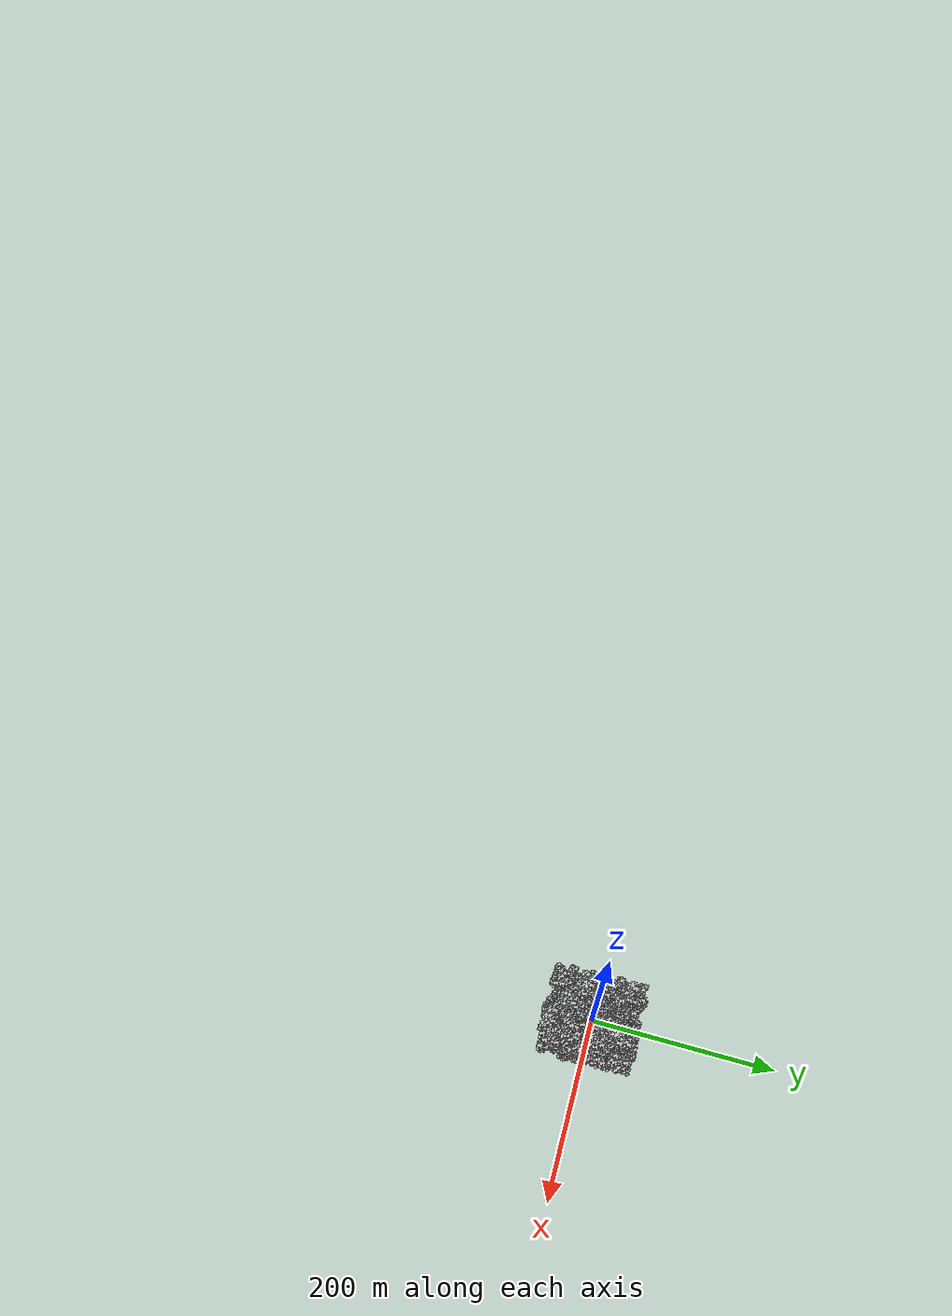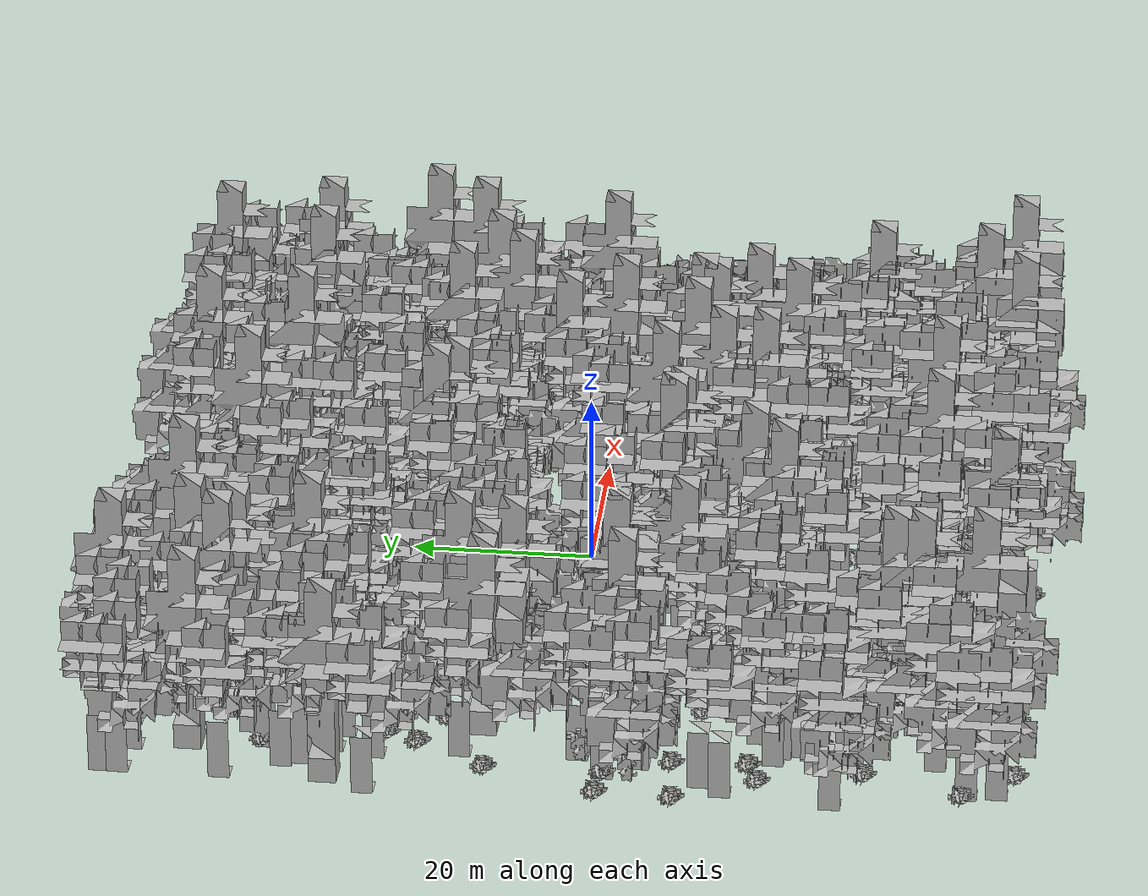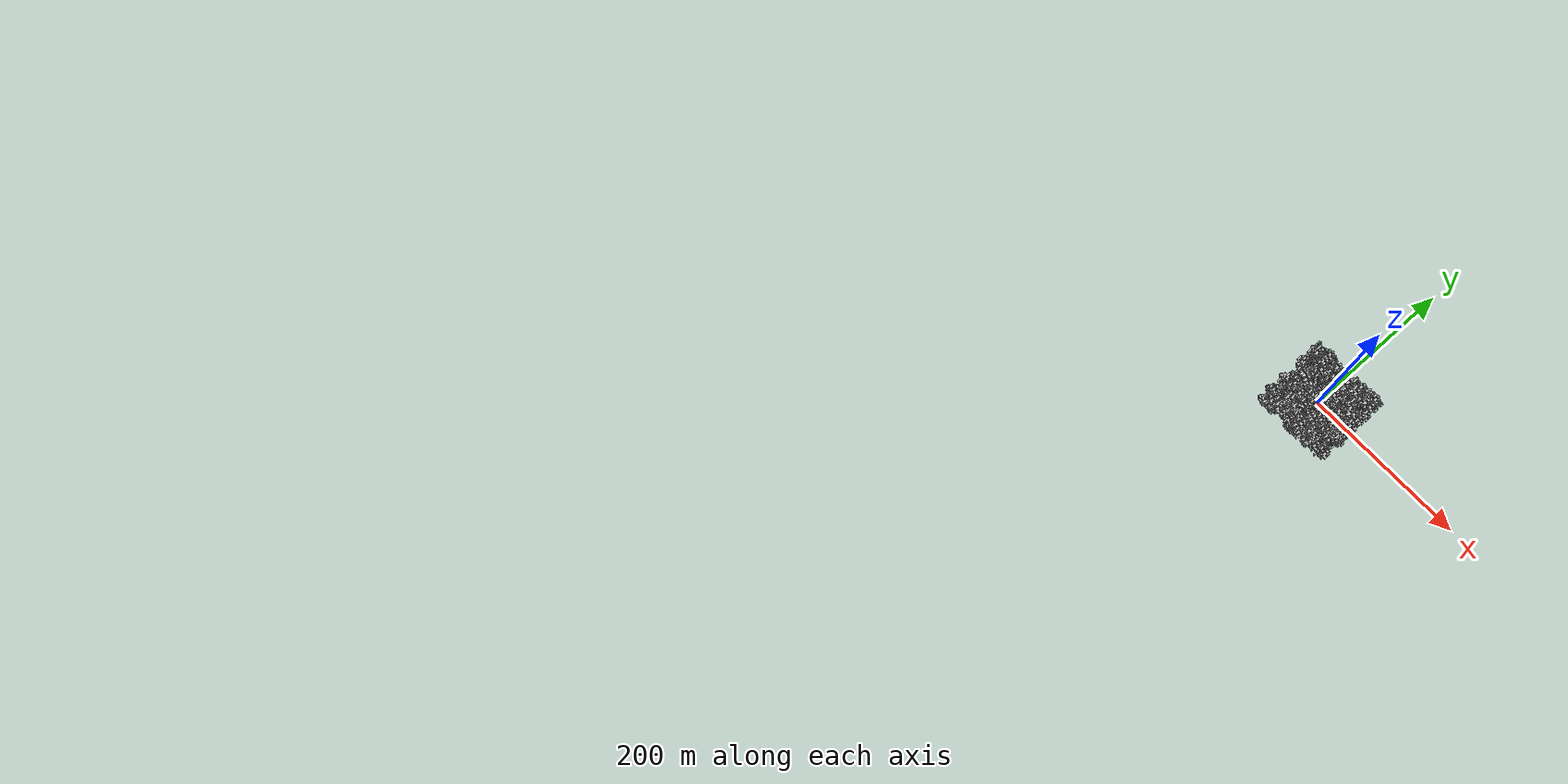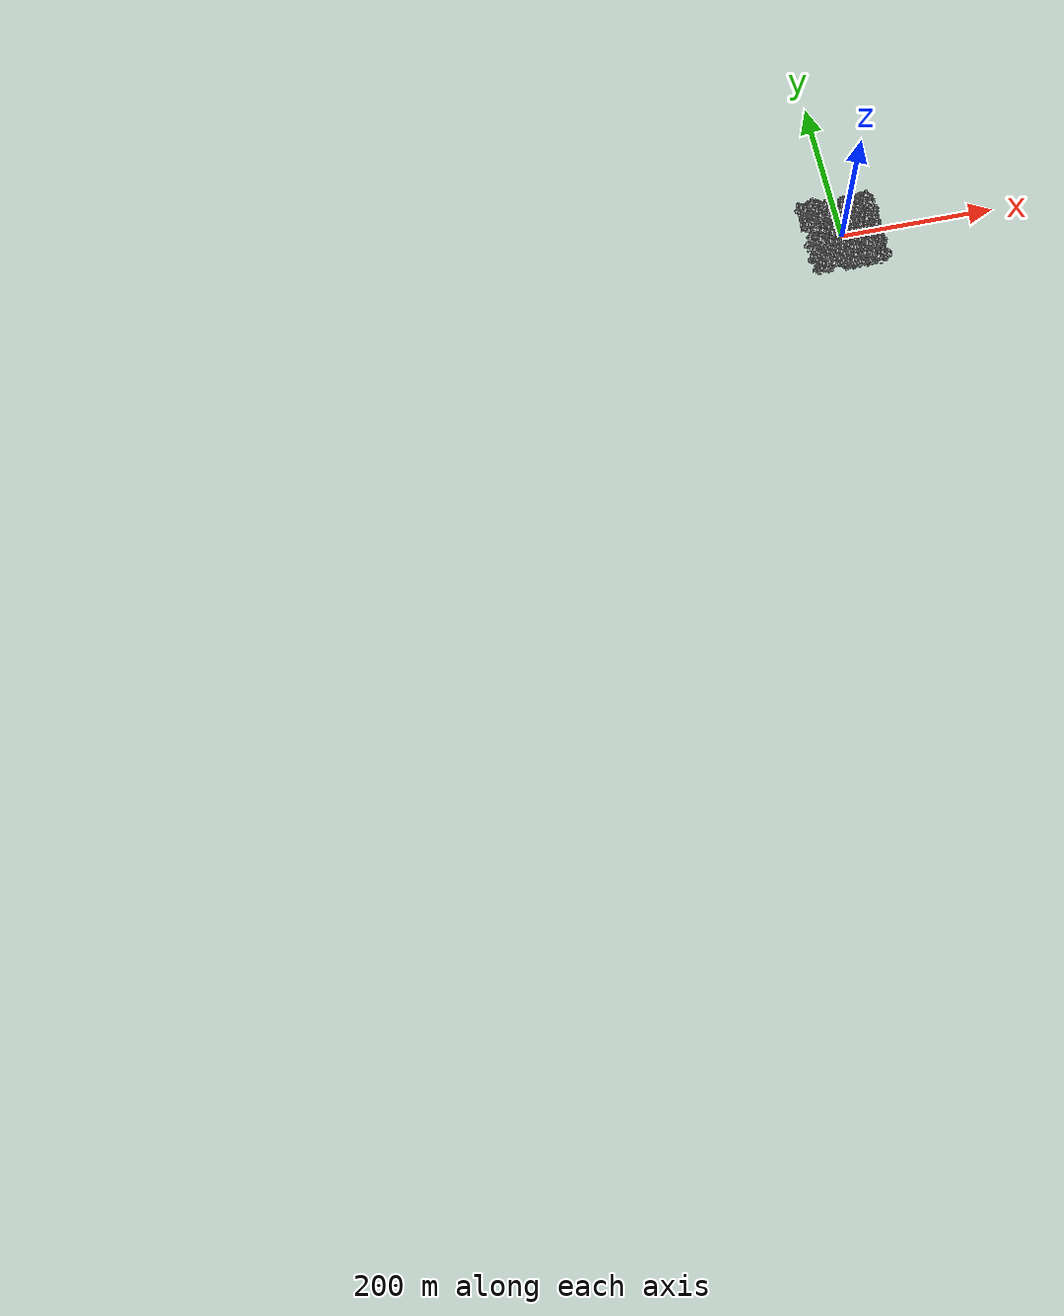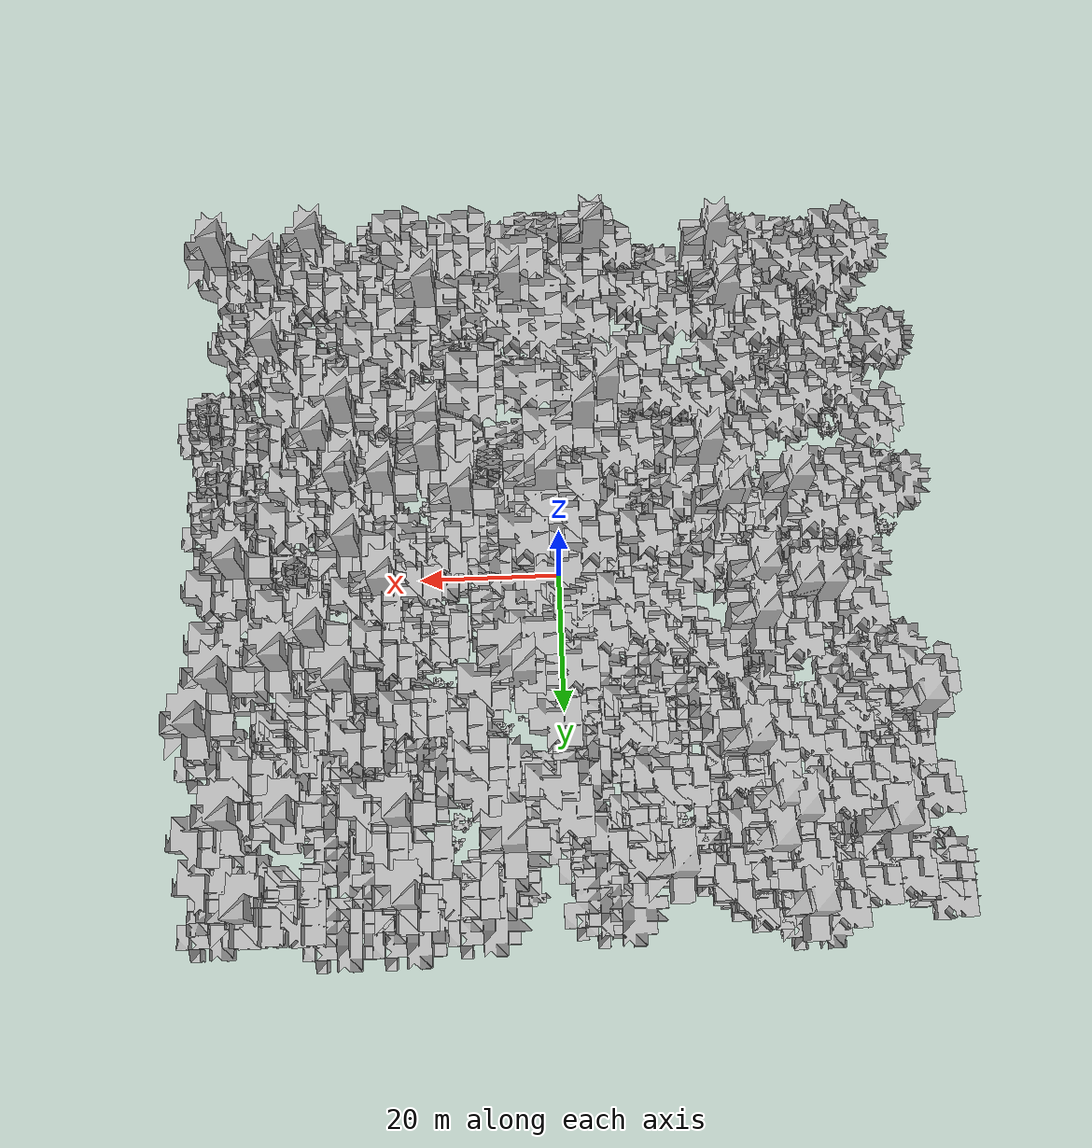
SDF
<sdf version="1.7">
    <world name="default">
        <plugin name="mrs_gazebo_static_transform_republisher_plugin" filename="libMrsGazeboCommonResources_StaticTransformRepublisher.so"/>
        <spherical_coordinates>
            <surface_model>EARTH_WGS84</surface_model>
            <latitude_deg>47.3977</latitude_deg>
            <longitude_deg>8.54559</longitude_deg>
            <elevation>0</elevation>
            <heading_deg>0</heading_deg>
        </spherical_coordinates>
        <physics name="default_physics" default="0" type="ode">
            <ode>
                <solver>
                    <type>quick</type>
                    <iters>10</iters>
                    <sor>1.3</sor>
                    <use_dynamic_moi_rescaling>0</use_dynamic_moi_rescaling>
                </solver>
                <constraints>
                    <cfm>0</cfm>
                    <erp>0.2</erp>
                    <contact_max_correcting_vel>1000</contact_max_correcting_vel>
                    <contact_surface_layer>0.001</contact_surface_layer>
                </constraints>
            </ode>
            <max_step_size>0.004</max_step_size>
            <real_time_factor>1</real_time_factor>
            <real_time_update_rate>250</real_time_update_rate>
        </physics>
        <scene>
            <shadows>0</shadows>
            <ambient>0.4 0.4 0.4 1</ambient>
            <background>0.7 0.7 0.7 1</background>
        </scene>
        <light name="sun" type="directional">
            <pose>0 0 1000 0.4 0.2 0</pose>
            <diffuse>1 1 1 1</diffuse>
            <specular>0.6 0.6 0.6 1</specular>
            <direction>0.1 0.1 -0.9</direction>
            <attenuation>
                <range>20</range>
                <constant>0.5</constant>
                <linear>0.01</linear>
                <quadratic>0.001</quadratic>
            </attenuation>
            <cast_shadows>1</cast_shadows>
            <spot>
                <inner_angle>0</inner_angle>
                <outer_angle>0</outer_angle>
                <falloff>0</falloff>
            </spot>
        </light>
        <model name="ground_plane">
            <static>1</static>
            <link name="link">
                <collision name="collision">
                    <pose>0 0 0 0 -0 0</pose>
                    <geometry>
                        <plane>
                            <normal>0 0 1</normal>
                            <size>100 100</size>
                        </plane>
                    </geometry>
                    <surface>
                        <contact>
                            <ode>
                                <min_depth>0.01</min_depth>
                                <max_vel>0</max_vel>
                            </ode>
                        </contact>
                        <friction>
                            <ode/>
                            <torsional>
                                <ode/>
                            </torsional>
                        </friction>
                        <bounce/>
                    </surface>
                    <max_contacts>10</max_contacts>
                </collision>
                <visual name="grass">
                    <pose>0 0 0 0 -0 0</pose>
                    <cast_shadows>0</cast_shadows>
                    <geometry>
                        <mesh>
                            <scale>0.41000000000000003 0.41000000000000003 0.1</scale>
                            <uri>file://grass_plane/meshes/grass_plane.dae</uri>
                        </mesh>
                    </geometry>
                </visual>
                <self_collide>0</self_collide>
                <enable_wind>0</enable_wind>
                <kinematic>0</kinematic>
            </link>
        </model>
        <model name="the_void">
            <static>1</static>
            <link name="link">
                <pose>0 0 0.1 0 -0 0</pose>
                <visual name="the_void">
                    <pose>0 0 2 0 -0 0</pose>
                    <geometry>
                        <sphere>
                            <radius>0.25</radius>
                        </sphere>
                    </geometry>
                    <material>
                        <script>
                            <uri>file://media/materials/scripts/Gazebo.material</uri>
                            <name>Gazebo/Black</name>
                        </script>
                    </material>
                </visual>
                <self_collide>0</self_collide>
                <enable_wind>0</enable_wind>
                <kinematic>0</kinematic>
            </link>
            <pose>-1000 -1000 0 0 -0 0</pose>
        </model>
        <gui fullscreen="0">
            <camera name="camera">
                <pose>35.1577 98.6044 40.0204 0 0.407996 -1.99761</pose>
                <view_controller>orbit</view_controller>
                <projection_type>perspective</projection_type>
            </camera>
        </gui>
        <plugin name="mrs_gazebo_rviz_cam_synchronizer" filename="libMrsGazeboCommonResources_RvizCameraSynchronizer.so">
            <target_frame_id>gazebo_user_camera</target_frame_id>
            <world_origin_frame_id>uav1/gps_origin</world_origin_frame_id>
            <frame_to_follow>uav1</frame_to_follow>
        </plugin>
        <gravity>0 0 -9.8066</gravity>
        <magnetic_field>6e-06 2.3e-05 -4.2e-05</magnetic_field>
        <atmosphere type="adiabatic"/>
        <wind/>
        <model name="Tree 0">
            <static>1</static>
            <pose>-23.924865385319332 -39.56324629947811 0 1.57079 -0 0</pose>
            <link name="link">
                <pose>0 0 0 0 -0 0</pose>
                <collision name="collision">
                    <geometry>
                        <mesh>
                            <scale>5 5 5</scale>
                            <uri>model://tree_9/meshes/tree_9.obj</uri>
                        </mesh>
                    </geometry>
                    <max_contacts>10</max_contacts>
                    <surface>
                        <contact>
                            <ode/>
                        </contact>
                        <bounce/>
                        <friction>
                            <torsional>
                                <ode/>
                            </torsional>
                            <ode/>
                        </friction>
                    </surface>
                </collision>
                <visual name="visual">
                    <geometry>
                        <mesh>
                            <scale>5 5 5</scale>
                            <uri>model://tree_9/meshes/tree_9.obj</uri>
                        </mesh>
                    </geometry>
                </visual>
                <self_collide>0</self_collide>
                <enable_wind>0</enable_wind>
                <kinematic>0</kinematic>
            </link>
        </model>
        <model name="Tree 1">
            <static>1</static>
            <pose>48.033321169185385 -20.172110421014434 0 1.57079 -0 0</pose>
            <link name="link">
                <pose>0 0 0 0 -0 0</pose>
                <collision name="collision">
                    <geometry>
                        <mesh>
                            <scale>5 5 5</scale>
                            <uri>model://tree_2/meshes/tree_2.obj</uri>
                        </mesh>
                    </geometry>
                    <max_contacts>10</max_contacts>
                    <surface>
                        <contact>
                            <ode/>
                        </contact>
                        <bounce/>
                        <friction>
                            <torsional>
                                <ode/>
                            </torsional>
                            <ode/>
                        </friction>
                    </surface>
                </collision>
                <visual name="visual">
                    <geometry>
                        <mesh>
                            <scale>5 5 5</scale>
                            <uri>model://tree_2/meshes/tree_2.obj</uri>
                        </mesh>
                    </geometry>
                </visual>
                <self_collide>0</self_collide>
                <enable_wind>0</enable_wind>
                <kinematic>0</kinematic>
            </link>
        </model>
        <model name="Tree 2">
            <static>1</static>
            <pose>20.87272012074979 49.653918708185955 0 1.57079 -0 0</pose>
            <link name="link">
                <pose>0 0 0 0 -0 0</pose>
                <collision name="collision">
                    <geometry>
                        <mesh>
                            <scale>5 5 5</scale>
                            <uri>model://tree_2/meshes/tree_2.obj</uri>
                        </mesh>
                    </geometry>
                    <max_contacts>10</max_contacts>
                    <surface>
                        <contact>
                            <ode/>
                        </contact>
                        <bounce/>
                        <friction>
                            <torsional>
                                <ode/>
                            </torsional>
                            <ode/>
                        </friction>
                    </surface>
                </collision>
                <visual name="visual">
                    <geometry>
                        <mesh>
                            <scale>5 5 5</scale>
                            <uri>model://tree_2/meshes/tree_2.obj</uri>
                        </mesh>
                    </geometry>
                </visual>
                <self_collide>0</self_collide>
                <enable_wind>0</enable_wind>
                <kinematic>0</kinematic>
            </link>
        </model>
        <model name="Tree 3">
            <static>1</static>
            <pose>-35.04640376633964 34.69629686138252 0 1.57079 -0 0</pose>
            <link name="link">
                <pose>0 0 0 0 -0 0</pose>
                <collision name="collision">
                    <geometry>
                        <mesh>
                            <scale>5 5 5</scale>
                            <uri>model://tree_9/meshes/tree_9.obj</uri>
                        </mesh>
                    </geometry>
                    <max_contacts>10</max_contacts>
                    <surface>
                        <contact>
                            <ode/>
                        </contact>
                        <bounce/>
                        <friction>
                            <torsional>
                                <ode/>
                            </torsional>
                            <ode/>
                        </friction>
                    </surface>
                </collision>
                <visual name="visual">
                    <geometry>
                        <mesh>
                            <scale>5 5 5</scale>
                            <uri>model://tree_9/meshes/tree_9.obj</uri>
                        </mesh>
                    </geometry>
                </visual>
                <self_collide>0</self_collide>
                <enable_wind>0</enable_wind>
                <kinematic>0</kinematic>
            </link>
        </model>
        <model name="Tree 4">
            <static>1</static>
            <pose>-30.380189341605327 26.773847000356994 0 1.57079 -0 0</pose>
            <link name="link">
                <pose>0 0 0 0 -0 0</pose>
                <collision name="collision">
                    <geometry>
                        <mesh>
                            <scale>5 5 5</scale>
                            <uri>model://tree_9/meshes/tree_9.obj</uri>
                        </mesh>
                    </geometry>
                    <max_contacts>10</max_contacts>
                    <surface>
                        <contact>
                            <ode/>
                        </contact>
                        <bounce/>
                        <friction>
                            <torsional>
                                <ode/>
                            </torsional>
                            <ode/>
                        </friction>
                    </surface>
                </collision>
                <visual name="visual">
                    <geometry>
                        <mesh>
                            <scale>5 5 5</scale>
                            <uri>model://tree_9/meshes/tree_9.obj</uri>
                        </mesh>
                    </geometry>
                </visual>
                <self_collide>0</self_collide>
                <enable_wind>0</enable_wind>
                <kinematic>0</kinematic>
            </link>
        </model>
        <model name="Tree 5">
            <static>1</static>
            <pose>-26.01429329863007 6.461266945672065 0 1.57079 -0 0</pose>
            <link name="link">
                <pose>0 0 0 0 -0 0</pose>
                <collision name="collision">
                    <geometry>
                        <mesh>
                            <scale>5 5 5</scale>
                            <uri>model://tree_9/meshes/tree_9.obj</uri>
                        </mesh>
                    </geometry>
                    <max_contacts>10</max_contacts>
                    <surface>
                        <contact>
                            <ode/>
                        </contact>
                        <bounce/>
                        <friction>
                            <torsional>
                                <ode/>
                            </torsional>
                            <ode/>
                        </friction>
                    </surface>
                </collision>
                <visual name="visual">
                    <geometry>
                        <mesh>
                            <scale>5 5 5</scale>
                            <uri>model://tree_9/meshes/tree_9.obj</uri>
                        </mesh>
                    </geometry>
                </visual>
                <self_collide>0</self_collide>
                <enable_wind>0</enable_wind>
                <kinematic>0</kinematic>
            </link>
        </model>
        <model name="Tree 6">
            <static>1</static>
            <pose>36.65518132205763 -21.107911213101392 0 1.57079 -0 0</pose>
            <link name="link">
                <pose>0 0 0 0 -0 0</pose>
                <collision name="collision">
                    <geometry>
                        <mesh>
                            <scale>5 5 5</scale>
                            <uri>model://tree_9/meshes/tree_9.obj</uri>
                        </mesh>
                    </geometry>
                    <max_contacts>10</max_contacts>
                    <surface>
                        <contact>
                            <ode/>
                        </contact>
                        <bounce/>
                        <friction>
                            <torsional>
                                <ode/>
                            </torsional>
                            <ode/>
                        </friction>
                    </surface>
                </collision>
                <visual name="visual">
                    <geometry>
                        <mesh>
                            <scale>5 5 5</scale>
                            <uri>model://tree_9/meshes/tree_9.obj</uri>
                        </mesh>
                    </geometry>
                </visual>
                <self_collide>0</self_collide>
                <enable_wind>0</enable_wind>
                <kinematic>0</kinematic>
            </link>
        </model>
        <model name="Tree 7">
            <static>1</static>
            <pose>-8.924480028915518 37.32568058768811 0 1.57079 -0 0</pose>
            <link name="link">
                <pose>0 0 0 0 -0 0</pose>
                <collision name="collision">
                    <geometry>
                        <mesh>
                            <scale>5 5 5</scale>
                            <uri>model://tree_9/meshes/tree_9.obj</uri>
                        </mesh>
                    </geometry>
                    <max_contacts>10</max_contacts>
                    <surface>
                        <contact>
                            <ode/>
                        </contact>
                        <bounce/>
                        <friction>
                            <torsional>
                                <ode/>
                            </torsional>
                            <ode/>
                        </friction>
                    </surface>
                </collision>
                <visual name="visual">
                    <geometry>
                        <mesh>
                            <scale>5 5 5</scale>
                            <uri>model://tree_9/meshes/tree_9.obj</uri>
                        </mesh>
                    </geometry>
                </visual>
                <self_collide>0</self_collide>
                <enable_wind>0</enable_wind>
                <kinematic>0</kinematic>
            </link>
        </model>
        <model name="Tree 8">
            <static>1</static>
            <pose>-34.397896939591064 -21.52071543263403 0 1.57079 -0 0</pose>
            <link name="link">
                <pose>0 0 0 0 -0 0</pose>
                <collision name="collision">
                    <geometry>
                        <mesh>
                            <scale>5 5 5</scale>
                            <uri>model://tree_9/meshes/tree_9.obj</uri>
                        </mesh>
                    </geometry>
                    <max_contacts>10</max_contacts>
                    <surface>
                        <contact>
                            <ode/>
                        </contact>
                        <bounce/>
                        <friction>
                            <torsional>
                                <ode/>
                            </torsional>
                            <ode/>
                        </friction>
                    </surface>
                </collision>
                <visual name="visual">
                    <geometry>
                        <mesh>
                            <scale>5 5 5</scale>
                            <uri>model://tree_9/meshes/tree_9.obj</uri>
                        </mesh>
                    </geometry>
                </visual>
                <self_collide>0</self_collide>
                <enable_wind>0</enable_wind>
                <kinematic>0</kinematic>
            </link>
        </model>
        <model name="Tree 9">
            <static>1</static>
            <pose>29.69096235954777 -0.456956809424355 0 1.57079 -0 0</pose>
            <link name="link">
                <pose>0 0 0 0 -0 0</pose>
                <collision name="collision">
                    <geometry>
                        <mesh>
                            <scale>5 5 5</scale>
                            <uri>model://tree_2/meshes/tree_2.obj</uri>
                        </mesh>
                    </geometry>
                    <max_contacts>10</max_contacts>
                    <surface>
                        <contact>
                            <ode/>
                        </contact>
                        <bounce/>
                        <friction>
                            <torsional>
                                <ode/>
                            </torsional>
                            <ode/>
                        </friction>
                    </surface>
                </collision>
                <visual name="visual">
                    <geometry>
                        <mesh>
                            <scale>5 5 5</scale>
                            <uri>model://tree_2/meshes/tree_2.obj</uri>
                        </mesh>
                    </geometry>
                </visual>
                <self_collide>0</self_collide>
                <enable_wind>0</enable_wind>
                <kinematic>0</kinematic>
            </link>
        </model>
        <model name="Tree 10">
            <static>1</static>
            <pose>-37.46173545541709 19.173625960675253 0 1.57079 -0 0</pose>
            <link name="link">
                <pose>0 0 0 0 -0 0</pose>
                <collision name="collision">
                    <geometry>
                        <mesh>
                            <scale>5 5 5</scale>
                            <uri>model://tree_2/meshes/tree_2.obj</uri>
                        </mesh>
                    </geometry>
                    <max_contacts>10</max_contacts>
                    <surface>
                        <contact>
                            <ode/>
                        </contact>
                        <bounce/>
                        <friction>
                            <torsional>
                                <ode/>
                            </torsional>
                            <ode/>
                        </friction>
                    </surface>
                </collision>
                <visual name="visual">
                    <geometry>
                        <mesh>
                            <scale>5 5 5</scale>
                            <uri>model://tree_2/meshes/tree_2.obj</uri>
                        </mesh>
                    </geometry>
                </visual>
                <self_collide>0</self_collide>
                <enable_wind>0</enable_wind>
                <kinematic>0</kinematic>
            </link>
        </model>
        <model name="Tree 11">
            <static>1</static>
            <pose>40.675569838467524 -29.791562081589042 0 1.57079 -0 0</pose>
            <link name="link">
                <pose>0 0 0 0 -0 0</pose>
                <collision name="collision">
                    <geometry>
                        <mesh>
                            <scale>5 5 5</scale>
                            <uri>model://tree_9/meshes/tree_9.obj</uri>
                        </mesh>
                    </geometry>
                    <max_contacts>10</max_contacts>
                    <surface>
                        <contact>
                            <ode/>
                        </contact>
                        <bounce/>
                        <friction>
                            <torsional>
                                <ode/>
                            </torsional>
                            <ode/>
                        </friction>
                    </surface>
                </collision>
                <visual name="visual">
                    <geometry>
                        <mesh>
                            <scale>5 5 5</scale>
                            <uri>model://tree_9/meshes/tree_9.obj</uri>
                        </mesh>
                    </geometry>
                </visual>
                <self_collide>0</self_collide>
                <enable_wind>0</enable_wind>
                <kinematic>0</kinematic>
            </link>
        </model>
        <model name="Tree 12">
            <static>1</static>
            <pose>-33.84470445783158 -42.91395990194694 0 1.57079 -0 0</pose>
            <link name="link">
                <pose>0 0 0 0 -0 0</pose>
                <collision name="collision">
                    <geometry>
                        <mesh>
                            <scale>5 5 5</scale>
                            <uri>model://tree_9/meshes/tree_9.obj</uri>
                        </mesh>
                    </geometry>
                    <max_contacts>10</max_contacts>
                    <surface>
                        <contact>
                            <ode/>
                        </contact>
                        <bounce/>
                        <friction>
                            <torsional>
                                <ode/>
                            </torsional>
                            <ode/>
                        </friction>
                    </surface>
                </collision>
                <visual name="visual">
                    <geometry>
                        <mesh>
                            <scale>5 5 5</scale>
                            <uri>model://tree_9/meshes/tree_9.obj</uri>
                        </mesh>
                    </geometry>
                </visual>
                <self_collide>0</self_collide>
                <enable_wind>0</enable_wind>
                <kinematic>0</kinematic>
            </link>
        </model>
        <model name="Tree 13">
            <static>1</static>
            <pose>15.753740143780576 12.22474399532576 0 1.57079 -0 0</pose>
            <link name="link">
                <pose>0 0 0 0 -0 0</pose>
                <collision name="collision">
                    <geometry>
                        <mesh>
                            <scale>5 5 5</scale>
                            <uri>model://tree_9/meshes/tree_9.obj</uri>
                        </mesh>
                    </geometry>
                    <max_contacts>10</max_contacts>
                    <surface>
                        <contact>
                            <ode/>
                        </contact>
                        <bounce/>
                        <friction>
                            <torsional>
                                <ode/>
                            </torsional>
                            <ode/>
                        </friction>
                    </surface>
                </collision>
                <visual name="visual">
                    <geometry>
                        <mesh>
                            <scale>5 5 5</scale>
                            <uri>model://tree_9/meshes/tree_9.obj</uri>
                        </mesh>
                    </geometry>
                </visual>
                <self_collide>0</self_collide>
                <enable_wind>0</enable_wind>
                <kinematic>0</kinematic>
            </link>
        </model>
        <model name="Tree 14">
            <static>1</static>
            <pose>34.0772824988684 -46.59886837229775 0 1.57079 -0 0</pose>
            <link name="link">
                <pose>0 0 0 0 -0 0</pose>
                <collision name="collision">
                    <geometry>
                        <mesh>
                            <scale>5 5 5</scale>
                            <uri>model://tree_4/meshes/tree_4.obj</uri>
                        </mesh>
                    </geometry>
                    <max_contacts>10</max_contacts>
                    <surface>
                        <contact>
                            <ode/>
                        </contact>
                        <bounce/>
                        <friction>
                            <torsional>
                                <ode/>
                            </torsional>
                            <ode/>
                        </friction>
                    </surface>
                </collision>
                <visual name="visual">
                    <geometry>
                        <mesh>
                            <scale>5 5 5</scale>
                            <uri>model://tree_4/meshes/tree_4.obj</uri>
                        </mesh>
                    </geometry>
                </visual>
                <self_collide>0</self_collide>
                <enable_wind>0</enable_wind>
                <kinematic>0</kinematic>
            </link>
        </model>
        <model name="Tree 15">
            <static>1</static>
            <pose>34.30280642389937 23.57383132441612 0 1.57079 -0 0</pose>
            <link name="link">
                <pose>0 0 0 0 -0 0</pose>
                <collision name="collision">
                    <geometry>
                        <mesh>
                            <scale>5 5 5</scale>
                            <uri>model://tree_9/meshes/tree_9.obj</uri>
                        </mesh>
                    </geometry>
                    <max_contacts>10</max_contacts>
                    <surface>
                        <contact>
                            <ode/>
                        </contact>
                        <bounce/>
                        <friction>
                            <torsional>
                                <ode/>
                            </torsional>
                            <ode/>
                        </friction>
                    </surface>
                </collision>
                <visual name="visual">
                    <geometry>
                        <mesh>
                            <scale>5 5 5</scale>
                            <uri>model://tree_9/meshes/tree_9.obj</uri>
                        </mesh>
                    </geometry>
                </visual>
                <self_collide>0</self_collide>
                <enable_wind>0</enable_wind>
                <kinematic>0</kinematic>
            </link>
        </model>
        <model name="Tree 16">
            <static>1</static>
            <pose>-38.04390828666114 42.54708785325384 0 1.57079 -0 0</pose>
            <link name="link">
                <pose>0 0 0 0 -0 0</pose>
                <collision name="collision">
                    <geometry>
                        <mesh>
                            <scale>5 5 5</scale>
                            <uri>model://tree_2/meshes/tree_2.obj</uri>
                        </mesh>
                    </geometry>
                    <max_contacts>10</max_contacts>
                    <surface>
                        <contact>
                            <ode/>
                        </contact>
                        <bounce/>
                        <friction>
                            <torsional>
                                <ode/>
                            </torsional>
                            <ode/>
                        </friction>
                    </surface>
                </collision>
                <visual name="visual">
                    <geometry>
                        <mesh>
                            <scale>5 5 5</scale>
                            <uri>model://tree_2/meshes/tree_2.obj</uri>
                        </mesh>
                    </geometry>
                </visual>
                <self_collide>0</self_collide>
                <enable_wind>0</enable_wind>
                <kinematic>0</kinematic>
            </link>
        </model>
        <model name="Tree 17">
            <static>1</static>
            <pose>33.42079491599917 -5.492756090774165 0 1.57079 -0 0</pose>
            <link name="link">
                <pose>0 0 0 0 -0 0</pose>
                <collision name="collision">
                    <geometry>
                        <mesh>
                            <scale>5 5 5</scale>
                            <uri>model://tree_9/meshes/tree_9.obj</uri>
                        </mesh>
                    </geometry>
                    <max_contacts>10</max_contacts>
                    <surface>
                        <contact>
                            <ode/>
                        </contact>
                        <bounce/>
                        <friction>
                            <torsional>
                                <ode/>
                            </torsional>
                            <ode/>
                        </friction>
                    </surface>
                </collision>
                <visual name="visual">
                    <geometry>
                        <mesh>
                            <scale>5 5 5</scale>
                            <uri>model://tree_9/meshes/tree_9.obj</uri>
                        </mesh>
                    </geometry>
                </visual>
                <self_collide>0</self_collide>
                <enable_wind>0</enable_wind>
                <kinematic>0</kinematic>
            </link>
        </model>
        <model name="Tree 18">
            <static>1</static>
            <pose>15.028659522144899 -29.757518925209514 0 1.57079 -0 0</pose>
            <link name="link">
                <pose>0 0 0 0 -0 0</pose>
                <collision name="collision">
                    <geometry>
                        <mesh>
                            <scale>5 5 5</scale>
                            <uri>model://tree_2/meshes/tree_2.obj</uri>
                        </mesh>
                    </geometry>
                    <max_contacts>10</max_contacts>
                    <surface>
                        <contact>
                            <ode/>
                        </contact>
                        <bounce/>
                        <friction>
                            <torsional>
                                <ode/>
                            </torsional>
                            <ode/>
                        </friction>
                    </surface>
                </collision>
                <visual name="visual">
                    <geometry>
                        <mesh>
                            <scale>5 5 5</scale>
                            <uri>model://tree_2/meshes/tree_2.obj</uri>
                        </mesh>
                    </geometry>
                </visual>
                <self_collide>0</self_collide>
                <enable_wind>0</enable_wind>
                <kinematic>0</kinematic>
            </link>
        </model>
        <model name="Tree 19">
            <static>1</static>
            <pose>9.248120324372536 1.3311916147904839 0 1.57079 -0 0</pose>
            <link name="link">
                <pose>0 0 0 0 -0 0</pose>
                <collision name="collision">
                    <geometry>
                        <mesh>
                            <scale>5 5 5</scale>
                            <uri>model://tree_2/meshes/tree_2.obj</uri>
                        </mesh>
                    </geometry>
                    <max_contacts>10</max_contacts>
                    <surface>
                        <contact>
                            <ode/>
                        </contact>
                        <bounce/>
                        <friction>
                            <torsional>
                                <ode/>
                            </torsional>
                            <ode/>
                        </friction>
                    </surface>
                </collision>
                <visual name="visual">
                    <geometry>
                        <mesh>
                            <scale>5 5 5</scale>
                            <uri>model://tree_2/meshes/tree_2.obj</uri>
                        </mesh>
                    </geometry>
                </visual>
                <self_collide>0</self_collide>
                <enable_wind>0</enable_wind>
                <kinematic>0</kinematic>
            </link>
        </model>
        <model name="Tree 20">
            <static>1</static>
            <pose>-23.93520905923619 39.83151022851973 0 1.57079 -0 0</pose>
            <link name="link">
                <pose>0 0 0 0 -0 0</pose>
                <collision name="collision">
                    <geometry>
                        <mesh>
                            <scale>5 5 5</scale>
                            <uri>model://tree_9/meshes/tree_9.obj</uri>
                        </mesh>
                    </geometry>
                    <max_contacts>10</max_contacts>
                    <surface>
                        <contact>
                            <ode/>
                        </contact>
                        <bounce/>
                        <friction>
                            <torsional>
                                <ode/>
                            </torsional>
                            <ode/>
                        </friction>
                    </surface>
                </collision>
                <visual name="visual">
                    <geometry>
                        <mesh>
                            <scale>5 5 5</scale>
                            <uri>model://tree_9/meshes/tree_9.obj</uri>
                        </mesh>
                    </geometry>
                </visual>
                <self_collide>0</self_collide>
                <enable_wind>0</enable_wind>
                <kinematic>0</kinematic>
            </link>
        </model>
        <model name="Tree 21">
            <static>1</static>
            <pose>46.18077979845019 -16.865379844860307 0 1.57079 -0 0</pose>
            <link name="link">
                <pose>0 0 0 0 -0 0</pose>
                <collision name="collision">
                    <geometry>
                        <mesh>
                            <scale>5 5 5</scale>
                            <uri>model://tree_2/meshes/tree_2.obj</uri>
                        </mesh>
                    </geometry>
                    <max_contacts>10</max_contacts>
                    <surface>
                        <contact>
                            <ode/>
                        </contact>
                        <bounce/>
                        <friction>
                            <torsional>
                                <ode/>
                            </torsional>
                            <ode/>
                        </friction>
                    </surface>
                </collision>
                <visual name="visual">
                    <geometry>
                        <mesh>
                            <scale>5 5 5</scale>
                            <uri>model://tree_2/meshes/tree_2.obj</uri>
                        </mesh>
                    </geometry>
                </visual>
                <self_collide>0</self_collide>
                <enable_wind>0</enable_wind>
                <kinematic>0</kinematic>
            </link>
        </model>
        <model name="Tree 22">
            <static>1</static>
            <pose>37.80199516911915 14.07022457545068 0 1.57079 -0 0</pose>
            <link name="link">
                <pose>0 0 0 0 -0 0</pose>
                <collision name="collision">
                    <geometry>
                        <mesh>
                            <scale>5 5 5</scale>
                            <uri>model://tree_4/meshes/tree_4.obj</uri>
                        </mesh>
                    </geometry>
                    <max_contacts>10</max_contacts>
                    <surface>
                        <contact>
                            <ode/>
                        </contact>
                        <bounce/>
                        <friction>
                            <torsional>
                                <ode/>
                            </torsional>
                            <ode/>
                        </friction>
                    </surface>
                </collision>
                <visual name="visual">
                    <geometry>
                        <mesh>
                            <scale>5 5 5</scale>
                            <uri>model://tree_4/meshes/tree_4.obj</uri>
                        </mesh>
                    </geometry>
                </visual>
                <self_collide>0</self_collide>
                <enable_wind>0</enable_wind>
                <kinematic>0</kinematic>
            </link>
        </model>
        <model name="Tree 23">
            <static>1</static>
            <pose>-12.25507892687439 -1.445269428864627 0 1.57079 -0 0</pose>
            <link name="link">
                <pose>0 0 0 0 -0 0</pose>
                <collision name="collision">
                    <geometry>
                        <mesh>
                            <scale>5 5 5</scale>
                            <uri>model://tree_9/meshes/tree_9.obj</uri>
                        </mesh>
                    </geometry>
                    <max_contacts>10</max_contacts>
                    <surface>
                        <contact>
                            <ode/>
                        </contact>
                        <bounce/>
                        <friction>
                            <torsional>
                                <ode/>
                            </torsional>
                            <ode/>
                        </friction>
                    </surface>
                </collision>
                <visual name="visual">
                    <geometry>
                        <mesh>
                            <scale>5 5 5</scale>
                            <uri>model://tree_9/meshes/tree_9.obj</uri>
                        </mesh>
                    </geometry>
                </visual>
                <self_collide>0</self_collide>
                <enable_wind>0</enable_wind>
                <kinematic>0</kinematic>
            </link>
        </model>
        <model name="Tree 24">
            <static>1</static>
            <pose>-20.20828327090916 41.49937359427143 0 1.57079 -0 0</pose>
            <link name="link">
                <pose>0 0 0 0 -0 0</pose>
                <collision name="collision">
                    <geometry>
                        <mesh>
                            <scale>5 5 5</scale>
                            <uri>model://tree_2/meshes/tree_2.obj</uri>
                        </mesh>
                    </geometry>
                    <max_contacts>10</max_contacts>
                    <surface>
                        <contact>
                            <ode/>
                        </contact>
                        <bounce/>
                        <friction>
                            <torsional>
                                <ode/>
                            </torsional>
                            <ode/>
                        </friction>
                    </surface>
                </collision>
                <visual name="visual">
                    <geometry>
                        <mesh>
                            <scale>5 5 5</scale>
                            <uri>model://tree_2/meshes/tree_2.obj</uri>
                        </mesh>
                    </geometry>
                </visual>
                <self_collide>0</self_collide>
                <enable_wind>0</enable_wind>
                <kinematic>0</kinematic>
            </link>
        </model>
        <model name="Tree 25">
            <static>1</static>
            <pose>23.995479880402968 6.620817760587805 0 1.57079 -0 0</pose>
            <link name="link">
                <pose>0 0 0 0 -0 0</pose>
                <collision name="collision">
                    <geometry>
                        <mesh>
                            <scale>5 5 5</scale>
                            <uri>model://tree_2/meshes/tree_2.obj</uri>
                        </mesh>
                    </geometry>
                    <max_contacts>10</max_contacts>
                    <surface>
                        <contact>
                            <ode/>
                        </contact>
                        <bounce/>
                        <friction>
                            <torsional>
                                <ode/>
                            </torsional>
                            <ode/>
                        </friction>
                    </surface>
                </collision>
                <visual name="visual">
                    <geometry>
                        <mesh>
                            <scale>5 5 5</scale>
                            <uri>model://tree_2/meshes/tree_2.obj</uri>
                        </mesh>
                    </geometry>
                </visual>
                <self_collide>0</self_collide>
                <enable_wind>0</enable_wind>
                <kinematic>0</kinematic>
            </link>
        </model>
        <model name="Tree 26">
            <static>1</static>
            <pose>44.06824998179462 -0.5448657894834099 0 1.57079 -0 0</pose>
            <link name="link">
                <pose>0 0 0 0 -0 0</pose>
                <collision name="collision">
                    <geometry>
                        <mesh>
                            <scale>5 5 5</scale>
                            <uri>model://tree_2/meshes/tree_2.obj</uri>
                        </mesh>
                    </geometry>
                    <max_contacts>10</max_contacts>
                    <surface>
                        <contact>
                            <ode/>
                        </contact>
                        <bounce/>
                        <friction>
                            <torsional>
                                <ode/>
                            </torsional>
                            <ode/>
                        </friction>
                    </surface>
                </collision>
                <visual name="visual">
                    <geometry>
                        <mesh>
                            <scale>5 5 5</scale>
                            <uri>model://tree_2/meshes/tree_2.obj</uri>
                        </mesh>
                    </geometry>
                </visual>
                <self_collide>0</self_collide>
                <enable_wind>0</enable_wind>
                <kinematic>0</kinematic>
            </link>
        </model>
        <model name="Tree 27">
            <static>1</static>
            <pose>39.68313411229319 -32.615920540559245 0 1.57079 -0 0</pose>
            <link name="link">
                <pose>0 0 0 0 -0 0</pose>
                <collision name="collision">
                    <geometry>
                        <mesh>
                            <scale>5 5 5</scale>
                            <uri>model://tree_2/meshes/tree_2.obj</uri>
                        </mesh>
                    </geometry>
                    <max_contacts>10</max_contacts>
                    <surface>
                        <contact>
                            <ode/>
                        </contact>
                        <bounce/>
                        <friction>
                            <torsional>
                                <ode/>
                            </torsional>
                            <ode/>
                        </friction>
                    </surface>
                </collision>
                <visual name="visual">
                    <geometry>
                        <mesh>
                            <scale>5 5 5</scale>
                            <uri>model://tree_2/meshes/tree_2.obj</uri>
                        </mesh>
                    </geometry>
                </visual>
                <self_collide>0</self_collide>
                <enable_wind>0</enable_wind>
                <kinematic>0</kinematic>
            </link>
        </model>
        <model name="Tree 28">
            <static>1</static>
            <pose>-26.23139387876234 -40.70543061842851 0 1.57079 -0 0</pose>
            <link name="link">
                <pose>0 0 0 0 -0 0</pose>
                <collision name="collision">
                    <geometry>
                        <mesh>
                            <scale>5 5 5</scale>
                            <uri>model://tree_9/meshes/tree_9.obj</uri>
                        </mesh>
                    </geometry>
                    <max_contacts>10</max_contacts>
                    <surface>
                        <contact>
                            <ode/>
                        </contact>
                        <bounce/>
                        <friction>
                            <torsional>
                                <ode/>
                            </torsional>
                            <ode/>
                        </friction>
                    </surface>
                </collision>
                <visual name="visual">
                    <geometry>
                        <mesh>
                            <scale>5 5 5</scale>
                            <uri>model://tree_9/meshes/tree_9.obj</uri>
                        </mesh>
                    </geometry>
                </visual>
                <self_collide>0</self_collide>
                <enable_wind>0</enable_wind>
                <kinematic>0</kinematic>
            </link>
        </model>
        <model name="Tree 29">
            <static>1</static>
            <pose>-18.007581378090077 14.752689949842008 0 1.57079 -0 0</pose>
            <link name="link">
                <pose>0 0 0 0 -0 0</pose>
                <collision name="collision">
                    <geometry>
                        <mesh>
                            <scale>5 5 5</scale>
                            <uri>model://tree_9/meshes/tree_9.obj</uri>
                        </mesh>
                    </geometry>
                    <max_contacts>10</max_contacts>
                    <surface>
                        <contact>
                            <ode/>
                        </contact>
                        <bounce/>
                        <friction>
                            <torsional>
                                <ode/>
                            </torsional>
                            <ode/>
                        </friction>
                    </surface>
                </collision>
                <visual name="visual">
                    <geometry>
                        <mesh>
                            <scale>5 5 5</scale>
                            <uri>model://tree_9/meshes/tree_9.obj</uri>
                        </mesh>
                    </geometry>
                </visual>
                <self_collide>0</self_collide>
                <enable_wind>0</enable_wind>
                <kinematic>0</kinematic>
            </link>
        </model>
        <model name="Tree 30">
            <static>1</static>
            <pose>12.041843890324635 -48.820525487982906 0 1.57079 -0 0</pose>
            <link name="link">
                <pose>0 0 0 0 -0 0</pose>
                <collision name="collision">
                    <geometry>
                        <mesh>
                            <scale>5 5 5</scale>
                            <uri>model://tree_9/meshes/tree_9.obj</uri>
                        </mesh>
                    </geometry>
                    <max_contacts>10</max_contacts>
                    <surface>
                        <contact>
                            <ode/>
                        </contact>
                        <bounce/>
                        <friction>
                            <torsional>
                                <ode/>
                            </torsional>
                            <ode/>
                        </friction>
                    </surface>
                </collision>
                <visual name="visual">
                    <geometry>
                        <mesh>
                            <scale>5 5 5</scale>
                            <uri>model://tree_9/meshes/tree_9.obj</uri>
                        </mesh>
                    </geometry>
                </visual>
                <self_collide>0</self_collide>
                <enable_wind>0</enable_wind>
                <kinematic>0</kinematic>
            </link>
        </model>
        <model name="Tree 31">
            <static>1</static>
            <pose>-38.13482885484315 -45.42675569241127 0 1.57079 -0 0</pose>
            <link name="link">
                <pose>0 0 0 0 -0 0</pose>
                <collision name="collision">
                    <geometry>
                        <mesh>
                            <scale>5 5 5</scale>
                            <uri>model://tree_2/meshes/tree_2.obj</uri>
                        </mesh>
                    </geometry>
                    <max_contacts>10</max_contacts>
                    <surface>
                        <contact>
                            <ode/>
                        </contact>
                        <bounce/>
                        <friction>
                            <torsional>
                                <ode/>
                            </torsional>
                            <ode/>
                        </friction>
                    </surface>
                </collision>
                <visual name="visual">
                    <geometry>
                        <mesh>
                            <scale>5 5 5</scale>
                            <uri>model://tree_2/meshes/tree_2.obj</uri>
                        </mesh>
                    </geometry>
                </visual>
                <self_collide>0</self_collide>
                <enable_wind>0</enable_wind>
                <kinematic>0</kinematic>
            </link>
        </model>
        <model name="Tree 32">
            <static>1</static>
            <pose>-19.521945721071084 42.03346834511321 0 1.57079 -0 0</pose>
            <link name="link">
                <pose>0 0 0 0 -0 0</pose>
                <collision name="collision">
                    <geometry>
                        <mesh>
                            <scale>5 5 5</scale>
                            <uri>model://tree_2/meshes/tree_2.obj</uri>
                        </mesh>
                    </geometry>
                    <max_contacts>10</max_contacts>
                    <surface>
                        <contact>
                            <ode/>
                        </contact>
                        <bounce/>
                        <friction>
                            <torsional>
                                <ode/>
                            </torsional>
                            <ode/>
                        </friction>
                    </surface>
                </collision>
                <visual name="visual">
                    <geometry>
                        <mesh>
                            <scale>5 5 5</scale>
                            <uri>model://tree_2/meshes/tree_2.obj</uri>
                        </mesh>
                    </geometry>
                </visual>
                <self_collide>0</self_collide>
                <enable_wind>0</enable_wind>
                <kinematic>0</kinematic>
            </link>
        </model>
        <model name="Tree 33">
            <static>1</static>
            <pose>39.67086391093697 47.693228647121785 0 1.57079 -0 0</pose>
            <link name="link">
                <pose>0 0 0 0 -0 0</pose>
                <collision name="collision">
                    <geometry>
                        <mesh>
                            <scale>5 5 5</scale>
                            <uri>model://tree_9/meshes/tree_9.obj</uri>
                        </mesh>
                    </geometry>
                    <max_contacts>10</max_contacts>
                    <surface>
                        <contact>
                            <ode/>
                        </contact>
                        <bounce/>
                        <friction>
                            <torsional>
                                <ode/>
                            </torsional>
                            <ode/>
                        </friction>
                    </surface>
                </collision>
                <visual name="visual">
                    <geometry>
                        <mesh>
                            <scale>5 5 5</scale>
                            <uri>model://tree_9/meshes/tree_9.obj</uri>
                        </mesh>
                    </geometry>
                </visual>
                <self_collide>0</self_collide>
                <enable_wind>0</enable_wind>
                <kinematic>0</kinematic>
            </link>
        </model>
        <model name="Tree 34">
            <static>1</static>
            <pose>15.589000933477323 0.5096532520394845 0 1.57079 -0 0</pose>
            <link name="link">
                <pose>0 0 0 0 -0 0</pose>
                <collision name="collision">
                    <geometry>
                        <mesh>
                            <scale>5 5 5</scale>
                            <uri>model://tree_9/meshes/tree_9.obj</uri>
                        </mesh>
                    </geometry>
                    <max_contacts>10</max_contacts>
                    <surface>
                        <contact>
                            <ode/>
                        </contact>
                        <bounce/>
                        <friction>
                            <torsional>
                                <ode/>
                            </torsional>
                            <ode/>
                        </friction>
                    </surface>
                </collision>
                <visual name="visual">
                    <geometry>
                        <mesh>
                            <scale>5 5 5</scale>
                            <uri>model://tree_9/meshes/tree_9.obj</uri>
                        </mesh>
                    </geometry>
                </visual>
                <self_collide>0</self_collide>
                <enable_wind>0</enable_wind>
                <kinematic>0</kinematic>
            </link>
        </model>
        <model name="Tree 35">
            <static>1</static>
            <pose>31.24420139409291 -8.705503871518374 0 1.57079 -0 0</pose>
            <link name="link">
                <pose>0 0 0 0 -0 0</pose>
                <collision name="collision">
                    <geometry>
                        <mesh>
                            <scale>5 5 5</scale>
                            <uri>model://tree_9/meshes/tree_9.obj</uri>
                        </mesh>
                    </geometry>
                    <max_contacts>10</max_contacts>
                    <surface>
                        <contact>
                            <ode/>
                        </contact>
                        <bounce/>
                        <friction>
                            <torsional>
                                <ode/>
                            </torsional>
                            <ode/>
                        </friction>
                    </surface>
                </collision>
                <visual name="visual">
                    <geometry>
                        <mesh>
                            <scale>5 5 5</scale>
                            <uri>model://tree_9/meshes/tree_9.obj</uri>
                        </mesh>
                    </geometry>
                </visual>
                <self_collide>0</self_collide>
                <enable_wind>0</enable_wind>
                <kinematic>0</kinematic>
            </link>
        </model>
        <model name="Tree 36">
            <static>1</static>
            <pose>-40.76966097629848 -43.61976608381316 0 1.57079 -0 0</pose>
            <link name="link">
                <pose>0 0 0 0 -0 0</pose>
                <collision name="collision">
                    <geometry>
                        <mesh>
                            <scale>5 5 5</scale>
                            <uri>model://tree_2/meshes/tree_2.obj</uri>
                        </mesh>
                    </geometry>
                    <max_contacts>10</max_contacts>
                    <surface>
                        <contact>
                            <ode/>
                        </contact>
                        <bounce/>
                        <friction>
                            <torsional>
                                <ode/>
                            </torsional>
                            <ode/>
                        </friction>
                    </surface>
                </collision>
                <visual name="visual">
                    <geometry>
                        <mesh>
                            <scale>5 5 5</scale>
                            <uri>model://tree_2/meshes/tree_2.obj</uri>
                        </mesh>
                    </geometry>
                </visual>
                <self_collide>0</self_collide>
                <enable_wind>0</enable_wind>
                <kinematic>0</kinematic>
            </link>
        </model>
        <model name="Tree 37">
            <static>1</static>
            <pose>16.624176950822942 1.550773803191852 0 1.57079 -0 0</pose>
            <link name="link">
                <pose>0 0 0 0 -0 0</pose>
                <collision name="collision">
                    <geometry>
                        <mesh>
                            <scale>5 5 5</scale>
                            <uri>model://tree_2/meshes/tree_2.obj</uri>
                        </mesh>
                    </geometry>
                    <max_contacts>10</max_contacts>
                    <surface>
                        <contact>
                            <ode/>
                        </contact>
                        <bounce/>
                        <friction>
                            <torsional>
                                <ode/>
                            </torsional>
                            <ode/>
                        </friction>
                    </surface>
                </collision>
                <visual name="visual">
                    <geometry>
                        <mesh>
                            <scale>5 5 5</scale>
                            <uri>model://tree_2/meshes/tree_2.obj</uri>
                        </mesh>
                    </geometry>
                </visual>
                <self_collide>0</self_collide>
                <enable_wind>0</enable_wind>
                <kinematic>0</kinematic>
            </link>
        </model>
        <model name="Tree 38">
            <static>1</static>
            <pose>-34.988148311524874 -22.261455518859176 0 1.57079 -0 0</pose>
            <link name="link">
                <pose>0 0 0 0 -0 0</pose>
                <collision name="collision">
                    <geometry>
                        <mesh>
                            <scale>5 5 5</scale>
                            <uri>model://tree_2/meshes/tree_2.obj</uri>
                        </mesh>
                    </geometry>
                    <max_contacts>10</max_contacts>
                    <surface>
                        <contact>
                            <ode/>
                        </contact>
                        <bounce/>
                        <friction>
                            <torsional>
                                <ode/>
                            </torsional>
                            <ode/>
                        </friction>
                    </surface>
                </collision>
                <visual name="visual">
                    <geometry>
                        <mesh>
                            <scale>5 5 5</scale>
                            <uri>model://tree_2/meshes/tree_2.obj</uri>
                        </mesh>
                    </geometry>
                </visual>
                <self_collide>0</self_collide>
                <enable_wind>0</enable_wind>
                <kinematic>0</kinematic>
            </link>
        </model>
        <model name="Tree 39">
            <static>1</static>
            <pose>-47.19905034616801 -9.334872737619548 0 1.57079 -0 0</pose>
            <link name="link">
                <pose>0 0 0 0 -0 0</pose>
                <collision name="collision">
                    <geometry>
                        <mesh>
                            <scale>5 5 5</scale>
                            <uri>model://tree_2/meshes/tree_2.obj</uri>
                        </mesh>
                    </geometry>
                    <max_contacts>10</max_contacts>
                    <surface>
                        <contact>
                            <ode/>
                        </contact>
                        <bounce/>
                        <friction>
                            <torsional>
                                <ode/>
                            </torsional>
                            <ode/>
                        </friction>
                    </surface>
                </collision>
                <visual name="visual">
                    <geometry>
                        <mesh>
                            <scale>5 5 5</scale>
                            <uri>model://tree_2/meshes/tree_2.obj</uri>
                        </mesh>
                    </geometry>
                </visual>
                <self_collide>0</self_collide>
                <enable_wind>0</enable_wind>
                <kinematic>0</kinematic>
            </link>
        </model>
        <model name="Tree 40">
            <static>1</static>
            <pose>48.24264820988421 22.439823867339825 0 1.57079 -0 0</pose>
            <link name="link">
                <pose>0 0 0 0 -0 0</pose>
                <collision name="collision">
                    <geometry>
                        <mesh>
                            <scale>5 5 5</scale>
                            <uri>model://tree_4/meshes/tree_4.obj</uri>
                        </mesh>
                    </geometry>
                    <max_contacts>10</max_contacts>
                    <surface>
                        <contact>
                            <ode/>
                        </contact>
                        <bounce/>
                        <friction>
                            <torsional>
                                <ode/>
                            </torsional>
                            <ode/>
                        </friction>
                    </surface>
                </collision>
                <visual name="visual">
                    <geometry>
                        <mesh>
                            <scale>5 5 5</scale>
                            <uri>model://tree_4/meshes/tree_4.obj</uri>
                        </mesh>
                    </geometry>
                </visual>
                <self_collide>0</self_collide>
                <enable_wind>0</enable_wind>
                <kinematic>0</kinematic>
            </link>
        </model>
        <model name="Tree 41">
            <static>1</static>
            <pose>-32.73987073937401 41.87504957528232 0 1.57079 -0 0</pose>
            <link name="link">
                <pose>0 0 0 0 -0 0</pose>
                <collision name="collision">
                    <geometry>
                        <mesh>
                            <scale>5 5 5</scale>
                            <uri>model://tree_2/meshes/tree_2.obj</uri>
                        </mesh>
                    </geometry>
                    <max_contacts>10</max_contacts>
                    <surface>
                        <contact>
                            <ode/>
                        </contact>
                        <bounce/>
                        <friction>
                            <torsional>
                                <ode/>
                            </torsional>
                            <ode/>
                        </friction>
                    </surface>
                </collision>
                <visual name="visual">
                    <geometry>
                        <mesh>
                            <scale>5 5 5</scale>
                            <uri>model://tree_2/meshes/tree_2.obj</uri>
                        </mesh>
                    </geometry>
                </visual>
                <self_collide>0</self_collide>
                <enable_wind>0</enable_wind>
                <kinematic>0</kinematic>
            </link>
        </model>
        <model name="Tree 42">
            <static>1</static>
            <pose>17.768627958104858 -13.506438107565714 0 1.57079 -0 0</pose>
            <link name="link">
                <pose>0 0 0 0 -0 0</pose>
                <collision name="collision">
                    <geometry>
                        <mesh>
                            <scale>5 5 5</scale>
                            <uri>model://tree_4/meshes/tree_4.obj</uri>
                        </mesh>
                    </geometry>
                    <max_contacts>10</max_contacts>
                    <surface>
                        <contact>
                            <ode/>
                        </contact>
                        <bounce/>
                        <friction>
                            <torsional>
                                <ode/>
                            </torsional>
                            <ode/>
                        </friction>
                    </surface>
                </collision>
                <visual name="visual">
                    <geometry>
                        <mesh>
                            <scale>5 5 5</scale>
                            <uri>model://tree_4/meshes/tree_4.obj</uri>
                        </mesh>
                    </geometry>
                </visual>
                <self_collide>0</self_collide>
                <enable_wind>0</enable_wind>
                <kinematic>0</kinematic>
            </link>
        </model>
        <model name="Tree 43">
            <static>1</static>
            <pose>-45.829143708003514 23.205313448131406 0 1.57079 -0 0</pose>
            <link name="link">
                <pose>0 0 0 0 -0 0</pose>
                <collision name="collision">
                    <geometry>
                        <mesh>
                            <scale>5 5 5</scale>
                            <uri>model://tree_4/meshes/tree_4.obj</uri>
                        </mesh>
                    </geometry>
                    <max_contacts>10</max_contacts>
                    <surface>
                        <contact>
                            <ode/>
                        </contact>
                        <bounce/>
                        <friction>
                            <torsional>
                                <ode/>
                            </torsional>
                            <ode/>
                        </friction>
                    </surface>
                </collision>
                <visual name="visual">
                    <geometry>
                        <mesh>
                            <scale>5 5 5</scale>
                            <uri>model://tree_4/meshes/tree_4.obj</uri>
                        </mesh>
                    </geometry>
                </visual>
                <self_collide>0</self_collide>
                <enable_wind>0</enable_wind>
                <kinematic>0</kinematic>
            </link>
        </model>
        <model name="Tree 44">
            <static>1</static>
            <pose>23.462081700805015 -3.4095084266519606 0 1.57079 -0 0</pose>
            <link name="link">
                <pose>0 0 0 0 -0 0</pose>
                <collision name="collision">
                    <geometry>
                        <mesh>
                            <scale>5 5 5</scale>
                            <uri>model://tree_2/meshes/tree_2.obj</uri>
                        </mesh>
                    </geometry>
                    <max_contacts>10</max_contacts>
                    <surface>
                        <contact>
                            <ode/>
                        </contact>
                        <bounce/>
                        <friction>
                            <torsional>
                                <ode/>
                            </torsional>
                            <ode/>
                        </friction>
                    </surface>
                </collision>
                <visual name="visual">
                    <geometry>
                        <mesh>
                            <scale>5 5 5</scale>
                            <uri>model://tree_2/meshes/tree_2.obj</uri>
                        </mesh>
                    </geometry>
                </visual>
                <self_collide>0</self_collide>
                <enable_wind>0</enable_wind>
                <kinematic>0</kinematic>
            </link>
        </model>
        <model name="Tree 45">
            <static>1</static>
            <pose>24.41247554256917 -33.765874432687795 0 1.57079 -0 0</pose>
            <link name="link">
                <pose>0 0 0 0 -0 0</pose>
                <collision name="collision">
                    <geometry>
                        <mesh>
                            <scale>5 5 5</scale>
                            <uri>model://tree_2/meshes/tree_2.obj</uri>
                        </mesh>
                    </geometry>
                    <max_contacts>10</max_contacts>
                    <surface>
                        <contact>
                            <ode/>
                        </contact>
                        <bounce/>
                        <friction>
                            <torsional>
                                <ode/>
                            </torsional>
                            <ode/>
                        </friction>
                    </surface>
                </collision>
                <visual name="visual">
                    <geometry>
                        <mesh>
                            <scale>5 5 5</scale>
                            <uri>model://tree_2/meshes/tree_2.obj</uri>
                        </mesh>
                    </geometry>
                </visual>
                <self_collide>0</self_collide>
                <enable_wind>0</enable_wind>
                <kinematic>0</kinematic>
            </link>
        </model>
        <model name="Tree 46">
            <static>1</static>
            <pose>33.84190530448261 -46.29045705237117 0 1.57079 -0 0</pose>
            <link name="link">
                <pose>0 0 0 0 -0 0</pose>
                <collision name="collision">
                    <geometry>
                        <mesh>
                            <scale>5 5 5</scale>
                            <uri>model://tree_9/meshes/tree_9.obj</uri>
                        </mesh>
                    </geometry>
                    <max_contacts>10</max_contacts>
                    <surface>
                        <contact>
                            <ode/>
                        </contact>
                        <bounce/>
                        <friction>
                            <torsional>
                                <ode/>
                            </torsional>
                            <ode/>
                        </friction>
                    </surface>
                </collision>
                <visual name="visual">
                    <geometry>
                        <mesh>
                            <scale>5 5 5</scale>
                            <uri>model://tree_9/meshes/tree_9.obj</uri>
                        </mesh>
                    </geometry>
                </visual>
                <self_collide>0</self_collide>
                <enable_wind>0</enable_wind>
                <kinematic>0</kinematic>
            </link>
        </model>
        <model name="Tree 47">
            <static>1</static>
            <pose>-24.82613827071071 -26.96435486488531 0 1.57079 -0 0</pose>
            <link name="link">
                <pose>0 0 0 0 -0 0</pose>
                <collision name="collision">
                    <geometry>
                        <mesh>
                            <scale>5 5 5</scale>
                            <uri>model://tree_9/meshes/tree_9.obj</uri>
                        </mesh>
                    </geometry>
                    <max_contacts>10</max_contacts>
                    <surface>
                        <contact>
                            <ode/>
                        </contact>
                        <bounce/>
                        <friction>
                            <torsional>
                                <ode/>
                            </torsional>
                            <ode/>
                        </friction>
                    </surface>
                </collision>
                <visual name="visual">
                    <geometry>
                        <mesh>
                            <scale>5 5 5</scale>
                            <uri>model://tree_9/meshes/tree_9.obj</uri>
                        </mesh>
                    </geometry>
                </visual>
                <self_collide>0</self_collide>
                <enable_wind>0</enable_wind>
                <kinematic>0</kinematic>
            </link>
        </model>
        <model name="Tree 48">
            <static>1</static>
            <pose>43.61871249021824 5.252878970425115 0 1.57079 -0 0</pose>
            <link name="link">
                <pose>0 0 0 0 -0 0</pose>
                <collision name="collision">
                    <geometry>
                        <mesh>
                            <scale>5 5 5</scale>
                            <uri>model://tree_2/meshes/tree_2.obj</uri>
                        </mesh>
                    </geometry>
                    <max_contacts>10</max_contacts>
                    <surface>
                        <contact>
                            <ode/>
                        </contact>
                        <bounce/>
                        <friction>
                            <torsional>
                                <ode/>
                            </torsional>
                            <ode/>
                        </friction>
                    </surface>
                </collision>
                <visual name="visual">
                    <geometry>
                        <mesh>
                            <scale>5 5 5</scale>
                            <uri>model://tree_2/meshes/tree_2.obj</uri>
                        </mesh>
                    </geometry>
                </visual>
                <self_collide>0</self_collide>
                <enable_wind>0</enable_wind>
                <kinematic>0</kinematic>
            </link>
        </model>
        <model name="Tree 49">
            <static>1</static>
            <pose>-37.8095459447257 32.8377533887699 0 1.57079 -0 0</pose>
            <link name="link">
                <pose>0 0 0 0 -0 0</pose>
                <collision name="collision">
                    <geometry>
                        <mesh>
                            <scale>5 5 5</scale>
                            <uri>model://tree_9/meshes/tree_9.obj</uri>
                        </mesh>
                    </geometry>
                    <max_contacts>10</max_contacts>
                    <surface>
                        <contact>
                            <ode/>
                        </contact>
                        <bounce/>
                        <friction>
                            <torsional>
                                <ode/>
                            </torsional>
                            <ode/>
                        </friction>
                    </surface>
                </collision>
                <visual name="visual">
                    <geometry>
                        <mesh>
                            <scale>5 5 5</scale>
                            <uri>model://tree_9/meshes/tree_9.obj</uri>
                        </mesh>
                    </geometry>
                </visual>
                <self_collide>0</self_collide>
                <enable_wind>0</enable_wind>
                <kinematic>0</kinematic>
            </link>
        </model>
        <model name="Tree 50">
            <static>1</static>
            <pose>23.784958615671158 39.071334697973896 0 1.57079 -0 0</pose>
            <link name="link">
                <pose>0 0 0 0 -0 0</pose>
                <collision name="collision">
                    <geometry>
                        <mesh>
                            <scale>5 5 5</scale>
                            <uri>model://tree_9/meshes/tree_9.obj</uri>
                        </mesh>
                    </geometry>
                    <max_contacts>10</max_contacts>
                    <surface>
                        <contact>
                            <ode/>
                        </contact>
                        <bounce/>
                        <friction>
                            <torsional>
                                <ode/>
                            </torsional>
                            <ode/>
                        </friction>
                    </surface>
                </collision>
                <visual name="visual">
                    <geometry>
                        <mesh>
                            <scale>5 5 5</scale>
                            <uri>model://tree_9/meshes/tree_9.obj</uri>
                        </mesh>
                    </geometry>
                </visual>
                <self_collide>0</self_collide>
                <enable_wind>0</enable_wind>
                <kinematic>0</kinematic>
            </link>
        </model>
        <model name="Tree 51">
            <static>1</static>
            <pose>43.87346590486044 1.1403603794704367 0 1.57079 -0 0</pose>
            <link name="link">
                <pose>0 0 0 0 -0 0</pose>
                <collision name="collision">
                    <geometry>
                        <mesh>
                            <scale>5 5 5</scale>
                            <uri>model://tree_4/meshes/tree_4.obj</uri>
                        </mesh>
                    </geometry>
                    <max_contacts>10</max_contacts>
                    <surface>
                        <contact>
                            <ode/>
                        </contact>
                        <bounce/>
                        <friction>
                            <torsional>
                                <ode/>
                            </torsional>
                            <ode/>
                        </friction>
                    </surface>
                </collision>
                <visual name="visual">
                    <geometry>
                        <mesh>
                            <scale>5 5 5</scale>
                            <uri>model://tree_4/meshes/tree_4.obj</uri>
                        </mesh>
                    </geometry>
                </visual>
                <self_collide>0</self_collide>
                <enable_wind>0</enable_wind>
                <kinematic>0</kinematic>
            </link>
        </model>
        <model name="Tree 52">
            <static>1</static>
            <pose>19.20649136220615 -20.447518289749844 0 1.57079 -0 0</pose>
            <link name="link">
                <pose>0 0 0 0 -0 0</pose>
                <collision name="collision">
                    <geometry>
                        <mesh>
                            <scale>5 5 5</scale>
                            <uri>model://tree_2/meshes/tree_2.obj</uri>
                        </mesh>
                    </geometry>
                    <max_contacts>10</max_contacts>
                    <surface>
                        <contact>
                            <ode/>
                        </contact>
                        <bounce/>
                        <friction>
                            <torsional>
                                <ode/>
                            </torsional>
                            <ode/>
                        </friction>
                    </surface>
                </collision>
                <visual name="visual">
                    <geometry>
                        <mesh>
                            <scale>5 5 5</scale>
                            <uri>model://tree_2/meshes/tree_2.obj</uri>
                        </mesh>
                    </geometry>
                </visual>
                <self_collide>0</self_collide>
                <enable_wind>0</enable_wind>
                <kinematic>0</kinematic>
            </link>
        </model>
        <model name="Tree 53">
            <static>1</static>
            <pose>-23.803758097763165 27.53242939550931 0 1.57079 -0 0</pose>
            <link name="link">
                <pose>0 0 0 0 -0 0</pose>
                <collision name="collision">
                    <geometry>
                        <mesh>
                            <scale>5 5 5</scale>
                            <uri>model://tree_4/meshes/tree_4.obj</uri>
                        </mesh>
                    </geometry>
                    <max_contacts>10</max_contacts>
                    <surface>
                        <contact>
                            <ode/>
                        </contact>
                        <bounce/>
                        <friction>
                            <torsional>
                                <ode/>
                            </torsional>
                            <ode/>
                        </friction>
                    </surface>
                </collision>
                <visual name="visual">
                    <geometry>
                        <mesh>
                            <scale>5 5 5</scale>
                            <uri>model://tree_4/meshes/tree_4.obj</uri>
                        </mesh>
                    </geometry>
                </visual>
                <self_collide>0</self_collide>
                <enable_wind>0</enable_wind>
                <kinematic>0</kinematic>
            </link>
        </model>
        <model name="Tree 54">
            <static>1</static>
            <pose>-21.69497430200028 -34.57880158267642 0 1.57079 -0 0</pose>
            <link name="link">
                <pose>0 0 0 0 -0 0</pose>
                <collision name="collision">
                    <geometry>
                        <mesh>
                            <scale>5 5 5</scale>
                            <uri>model://tree_9/meshes/tree_9.obj</uri>
                        </mesh>
                    </geometry>
                    <max_contacts>10</max_contacts>
                    <surface>
                        <contact>
                            <ode/>
                        </contact>
                        <bounce/>
                        <friction>
                            <torsional>
                                <ode/>
                            </torsional>
                            <ode/>
                        </friction>
                    </surface>
                </collision>
                <visual name="visual">
                    <geometry>
                        <mesh>
                            <scale>5 5 5</scale>
                            <uri>model://tree_9/meshes/tree_9.obj</uri>
                        </mesh>
                    </geometry>
                </visual>
                <self_collide>0</self_collide>
                <enable_wind>0</enable_wind>
                <kinematic>0</kinematic>
            </link>
        </model>
        <model name="Tree 55">
            <static>1</static>
            <pose>25.86277076914162 19.972662460139063 0 1.57079 -0 0</pose>
            <link name="link">
                <pose>0 0 0 0 -0 0</pose>
                <collision name="collision">
                    <geometry>
                        <mesh>
                            <scale>5 5 5</scale>
                            <uri>model://tree_2/meshes/tree_2.obj</uri>
                        </mesh>
                    </geometry>
                    <max_contacts>10</max_contacts>
                    <surface>
                        <contact>
                            <ode/>
                        </contact>
                        <bounce/>
                        <friction>
                            <torsional>
                                <ode/>
                            </torsional>
                            <ode/>
                        </friction>
                    </surface>
                </collision>
                <visual name="visual">
                    <geometry>
                        <mesh>
                            <scale>5 5 5</scale>
                            <uri>model://tree_2/meshes/tree_2.obj</uri>
                        </mesh>
                    </geometry>
                </visual>
                <self_collide>0</self_collide>
                <enable_wind>0</enable_wind>
                <kinematic>0</kinematic>
            </link>
        </model>
        <model name="Tree 56">
            <static>1</static>
            <pose>24.795117540372743 45.456987772595454 0 1.57079 -0 0</pose>
            <link name="link">
                <pose>0 0 0 0 -0 0</pose>
                <collision name="collision">
                    <geometry>
                        <mesh>
                            <scale>5 5 5</scale>
                            <uri>model://tree_2/meshes/tree_2.obj</uri>
                        </mesh>
                    </geometry>
                    <max_contacts>10</max_contacts>
                    <surface>
                        <contact>
                            <ode/>
                        </contact>
                        <bounce/>
                        <friction>
                            <torsional>
                                <ode/>
                            </torsional>
                            <ode/>
                        </friction>
                    </surface>
                </collision>
                <visual name="visual">
                    <geometry>
                        <mesh>
                            <scale>5 5 5</scale>
                            <uri>model://tree_2/meshes/tree_2.obj</uri>
                        </mesh>
                    </geometry>
                </visual>
                <self_collide>0</self_collide>
                <enable_wind>0</enable_wind>
                <kinematic>0</kinematic>
            </link>
        </model>
        <model name="Tree 57">
            <static>1</static>
            <pose>11.9788699841692 -44.803621683157516 0 1.57079 -0 0</pose>
            <link name="link">
                <pose>0 0 0 0 -0 0</pose>
                <collision name="collision">
                    <geometry>
                        <mesh>
                            <scale>5 5 5</scale>
                            <uri>model://tree_9/meshes/tree_9.obj</uri>
                        </mesh>
                    </geometry>
                    <max_contacts>10</max_contacts>
                    <surface>
                        <contact>
                            <ode/>
                        </contact>
                        <bounce/>
                        <friction>
                            <torsional>
                                <ode/>
                            </torsional>
                            <ode/>
                        </friction>
                    </surface>
                </collision>
                <visual name="visual">
                    <geometry>
                        <mesh>
                            <scale>5 5 5</scale>
                            <uri>model://tree_9/meshes/tree_9.obj</uri>
                        </mesh>
                    </geometry>
                </visual>
                <self_collide>0</self_collide>
                <enable_wind>0</enable_wind>
                <kinematic>0</kinematic>
            </link>
        </model>
        <model name="Tree 58">
            <static>1</static>
            <pose>-29.136478285314066 -5.744824546744688 0 1.57079 -0 0</pose>
            <link name="link">
                <pose>0 0 0 0 -0 0</pose>
                <collision name="collision">
                    <geometry>
                        <mesh>
                            <scale>5 5 5</scale>
                            <uri>model://tree_2/meshes/tree_2.obj</uri>
                        </mesh>
                    </geometry>
                    <max_contacts>10</max_contacts>
                    <surface>
                        <contact>
                            <ode/>
                        </contact>
                        <bounce/>
                        <friction>
                            <torsional>
                                <ode/>
                            </torsional>
                            <ode/>
                        </friction>
                    </surface>
                </collision>
                <visual name="visual">
                    <geometry>
                        <mesh>
                            <scale>5 5 5</scale>
                            <uri>model://tree_2/meshes/tree_2.obj</uri>
                        </mesh>
                    </geometry>
                </visual>
                <self_collide>0</self_collide>
                <enable_wind>0</enable_wind>
                <kinematic>0</kinematic>
            </link>
        </model>
        <model name="Tree 59">
            <static>1</static>
            <pose>-40.03871868976724 16.23069719176786 0 1.57079 -0 0</pose>
            <link name="link">
                <pose>0 0 0 0 -0 0</pose>
                <collision name="collision">
                    <geometry>
                        <mesh>
                            <scale>5 5 5</scale>
                            <uri>model://tree_2/meshes/tree_2.obj</uri>
                        </mesh>
                    </geometry>
                    <max_contacts>10</max_contacts>
                    <surface>
                        <contact>
                            <ode/>
                        </contact>
                        <bounce/>
                        <friction>
                            <torsional>
                                <ode/>
                            </torsional>
                            <ode/>
                        </friction>
                    </surface>
                </collision>
                <visual name="visual">
                    <geometry>
                        <mesh>
                            <scale>5 5 5</scale>
                            <uri>model://tree_2/meshes/tree_2.obj</uri>
                        </mesh>
                    </geometry>
                </visual>
                <self_collide>0</self_collide>
                <enable_wind>0</enable_wind>
                <kinematic>0</kinematic>
            </link>
        </model>
        <model name="Tree 60">
            <static>1</static>
            <pose>6.862749363644205 -13.238998403001034 0 1.57079 -0 0</pose>
            <link name="link">
                <pose>0 0 0 0 -0 0</pose>
                <collision name="collision">
                    <geometry>
                        <mesh>
                            <scale>5 5 5</scale>
                            <uri>model://tree_2/meshes/tree_2.obj</uri>
                        </mesh>
                    </geometry>
                    <max_contacts>10</max_contacts>
                    <surface>
                        <contact>
                            <ode/>
                        </contact>
                        <bounce/>
                        <friction>
                            <torsional>
                                <ode/>
                            </torsional>
                            <ode/>
                        </friction>
                    </surface>
                </collision>
                <visual name="visual">
                    <geometry>
                        <mesh>
                            <scale>5 5 5</scale>
                            <uri>model://tree_2/meshes/tree_2.obj</uri>
                        </mesh>
                    </geometry>
                </visual>
                <self_collide>0</self_collide>
                <enable_wind>0</enable_wind>
                <kinematic>0</kinematic>
            </link>
        </model>
        <model name="Tree 61">
            <static>1</static>
            <pose>9.345196980787627 -48.581726508820935 0 1.57079 -0 0</pose>
            <link name="link">
                <pose>0 0 0 0 -0 0</pose>
                <collision name="collision">
                    <geometry>
                        <mesh>
                            <scale>5 5 5</scale>
                            <uri>model://tree_2/meshes/tree_2.obj</uri>
                        </mesh>
                    </geometry>
                    <max_contacts>10</max_contacts>
                    <surface>
                        <contact>
                            <ode/>
                        </contact>
                        <bounce/>
                        <friction>
                            <torsional>
                                <ode/>
                            </torsional>
                            <ode/>
                        </friction>
                    </surface>
                </collision>
                <visual name="visual">
                    <geometry>
                        <mesh>
                            <scale>5 5 5</scale>
                            <uri>model://tree_2/meshes/tree_2.obj</uri>
                        </mesh>
                    </geometry>
                </visual>
                <self_collide>0</self_collide>
                <enable_wind>0</enable_wind>
                <kinematic>0</kinematic>
            </link>
        </model>
        <model name="Tree 62">
            <static>1</static>
            <pose>46.65612200009754 -11.479614325144759 0 1.57079 -0 0</pose>
            <link name="link">
                <pose>0 0 0 0 -0 0</pose>
                <collision name="collision">
                    <geometry>
                        <mesh>
                            <scale>5 5 5</scale>
                            <uri>model://tree_2/meshes/tree_2.obj</uri>
                        </mesh>
                    </geometry>
                    <max_contacts>10</max_contacts>
                    <surface>
                        <contact>
                            <ode/>
                        </contact>
                        <bounce/>
                        <friction>
                            <torsional>
                                <ode/>
                            </torsional>
                            <ode/>
                        </friction>
                    </surface>
                </collision>
                <visual name="visual">
                    <geometry>
                        <mesh>
                            <scale>5 5 5</scale>
                            <uri>model://tree_2/meshes/tree_2.obj</uri>
                        </mesh>
                    </geometry>
                </visual>
                <self_collide>0</self_collide>
                <enable_wind>0</enable_wind>
                <kinematic>0</kinematic>
            </link>
        </model>
        <model name="Tree 63">
            <static>1</static>
            <pose>-4.091154610156643 -40.03539026270162 0 1.57079 -0 0</pose>
            <link name="link">
                <pose>0 0 0 0 -0 0</pose>
                <collision name="collision">
                    <geometry>
                        <mesh>
                            <scale>5 5 5</scale>
                            <uri>model://tree_2/meshes/tree_2.obj</uri>
                        </mesh>
                    </geometry>
                    <max_contacts>10</max_contacts>
                    <surface>
                        <contact>
                            <ode/>
                        </contact>
                        <bounce/>
                        <friction>
                            <torsional>
                                <ode/>
                            </torsional>
                            <ode/>
                        </friction>
                    </surface>
                </collision>
                <visual name="visual">
                    <geometry>
                        <mesh>
                            <scale>5 5 5</scale>
                            <uri>model://tree_2/meshes/tree_2.obj</uri>
                        </mesh>
                    </geometry>
                </visual>
                <self_collide>0</self_collide>
                <enable_wind>0</enable_wind>
                <kinematic>0</kinematic>
            </link>
        </model>
        <model name="Tree 64">
            <static>1</static>
            <pose>-38.32085286175642 29.71892166889316 0 1.57079 -0 0</pose>
            <link name="link">
                <pose>0 0 0 0 -0 0</pose>
                <collision name="collision">
                    <geometry>
                        <mesh>
                            <scale>5 5 5</scale>
                            <uri>model://tree_2/meshes/tree_2.obj</uri>
                        </mesh>
                    </geometry>
                    <max_contacts>10</max_contacts>
                    <surface>
                        <contact>
                            <ode/>
                        </contact>
                        <bounce/>
                        <friction>
                            <torsional>
                                <ode/>
                            </torsional>
                            <ode/>
                        </friction>
                    </surface>
                </collision>
                <visual name="visual">
                    <geometry>
                        <mesh>
                            <scale>5 5 5</scale>
                            <uri>model://tree_2/meshes/tree_2.obj</uri>
                        </mesh>
                    </geometry>
                </visual>
                <self_collide>0</self_collide>
                <enable_wind>0</enable_wind>
                <kinematic>0</kinematic>
            </link>
        </model>
        <model name="Tree 65">
            <static>1</static>
            <pose>-17.00998567451305 1.4229348751580773 0 1.57079 -0 0</pose>
            <link name="link">
                <pose>0 0 0 0 -0 0</pose>
                <collision name="collision">
                    <geometry>
                        <mesh>
                            <scale>5 5 5</scale>
                            <uri>model://tree_2/meshes/tree_2.obj</uri>
                        </mesh>
                    </geometry>
                    <max_contacts>10</max_contacts>
                    <surface>
                        <contact>
                            <ode/>
                        </contact>
                        <bounce/>
                        <friction>
                            <torsional>
                                <ode/>
                            </torsional>
                            <ode/>
                        </friction>
                    </surface>
                </collision>
                <visual name="visual">
                    <geometry>
                        <mesh>
                            <scale>5 5 5</scale>
                            <uri>model://tree_2/meshes/tree_2.obj</uri>
                        </mesh>
                    </geometry>
                </visual>
                <self_collide>0</self_collide>
                <enable_wind>0</enable_wind>
                <kinematic>0</kinematic>
            </link>
        </model>
        <model name="Tree 66">
            <static>1</static>
            <pose>24.513276819011793 7.012146546616137 0 1.57079 -0 0</pose>
            <link name="link">
                <pose>0 0 0 0 -0 0</pose>
                <collision name="collision">
                    <geometry>
                        <mesh>
                            <scale>5 5 5</scale>
                            <uri>model://tree_9/meshes/tree_9.obj</uri>
                        </mesh>
                    </geometry>
                    <max_contacts>10</max_contacts>
                    <surface>
                        <contact>
                            <ode/>
                        </contact>
                        <bounce/>
                        <friction>
                            <torsional>
                                <ode/>
                            </torsional>
                            <ode/>
                        </friction>
                    </surface>
                </collision>
                <visual name="visual">
                    <geometry>
                        <mesh>
                            <scale>5 5 5</scale>
                            <uri>model://tree_9/meshes/tree_9.obj</uri>
                        </mesh>
                    </geometry>
                </visual>
                <self_collide>0</self_collide>
                <enable_wind>0</enable_wind>
                <kinematic>0</kinematic>
            </link>
        </model>
        <model name="Tree 67">
            <static>1</static>
            <pose>-16.51270980587259 13.015987364559223 0 1.57079 -0 0</pose>
            <link name="link">
                <pose>0 0 0 0 -0 0</pose>
                <collision name="collision">
                    <geometry>
                        <mesh>
                            <scale>5 5 5</scale>
                            <uri>model://tree_9/meshes/tree_9.obj</uri>
                        </mesh>
                    </geometry>
                    <max_contacts>10</max_contacts>
                    <surface>
                        <contact>
                            <ode/>
                        </contact>
                        <bounce/>
                        <friction>
                            <torsional>
                                <ode/>
                            </torsional>
                            <ode/>
                        </friction>
                    </surface>
                </collision>
                <visual name="visual">
                    <geometry>
                        <mesh>
                            <scale>5 5 5</scale>
                            <uri>model://tree_9/meshes/tree_9.obj</uri>
                        </mesh>
                    </geometry>
                </visual>
                <self_collide>0</self_collide>
                <enable_wind>0</enable_wind>
                <kinematic>0</kinematic>
            </link>
        </model>
        <model name="Tree 68">
            <static>1</static>
            <pose>-20.85613020271379 -21.27397759455786 0 1.57079 -0 0</pose>
            <link name="link">
                <pose>0 0 0 0 -0 0</pose>
                <collision name="collision">
                    <geometry>
                        <mesh>
                            <scale>5 5 5</scale>
                            <uri>model://tree_9/meshes/tree_9.obj</uri>
                        </mesh>
                    </geometry>
                    <max_contacts>10</max_contacts>
                    <surface>
                        <contact>
                            <ode/>
                        </contact>
                        <bounce/>
                        <friction>
                            <torsional>
                                <ode/>
                            </torsional>
                            <ode/>
                        </friction>
                    </surface>
                </collision>
                <visual name="visual">
                    <geometry>
                        <mesh>
                            <scale>5 5 5</scale>
                            <uri>model://tree_9/meshes/tree_9.obj</uri>
                        </mesh>
                    </geometry>
                </visual>
                <self_collide>0</self_collide>
                <enable_wind>0</enable_wind>
                <kinematic>0</kinematic>
            </link>
        </model>
        <model name="Tree 69">
            <static>1</static>
            <pose>1.0135895242600697 -33.415363400066056 0 1.57079 -0 0</pose>
            <link name="link">
                <pose>0 0 0 0 -0 0</pose>
                <collision name="collision">
                    <geometry>
                        <mesh>
                            <scale>5 5 5</scale>
                            <uri>model://tree_2/meshes/tree_2.obj</uri>
                        </mesh>
                    </geometry>
                    <max_contacts>10</max_contacts>
                    <surface>
                        <contact>
                            <ode/>
                        </contact>
                        <bounce/>
                        <friction>
                            <torsional>
                                <ode/>
                            </torsional>
                            <ode/>
                        </friction>
                    </surface>
                </collision>
                <visual name="visual">
                    <geometry>
                        <mesh>
                            <scale>5 5 5</scale>
                            <uri>model://tree_2/meshes/tree_2.obj</uri>
                        </mesh>
                    </geometry>
                </visual>
                <self_collide>0</self_collide>
                <enable_wind>0</enable_wind>
                <kinematic>0</kinematic>
            </link>
        </model>
        <model name="Tree 70">
            <static>1</static>
            <pose>-31.152329110743658 13.74675163424672 0 1.57079 -0 0</pose>
            <link name="link">
                <pose>0 0 0 0 -0 0</pose>
                <collision name="collision">
                    <geometry>
                        <mesh>
                            <scale>5 5 5</scale>
                            <uri>model://tree_9/meshes/tree_9.obj</uri>
                        </mesh>
                    </geometry>
                    <max_contacts>10</max_contacts>
                    <surface>
                        <contact>
                            <ode/>
                        </contact>
                        <bounce/>
                        <friction>
                            <torsional>
                                <ode/>
                            </torsional>
                            <ode/>
                        </friction>
                    </surface>
                </collision>
                <visual name="visual">
                    <geometry>
                        <mesh>
                            <scale>5 5 5</scale>
                            <uri>model://tree_9/meshes/tree_9.obj</uri>
                        </mesh>
                    </geometry>
                </visual>
                <self_collide>0</self_collide>
                <enable_wind>0</enable_wind>
                <kinematic>0</kinematic>
            </link>
        </model>
        <model name="Tree 71">
            <static>1</static>
            <pose>-29.871786347168126 42.182777393270825 0 1.57079 -0 0</pose>
            <link name="link">
                <pose>0 0 0 0 -0 0</pose>
                <collision name="collision">
                    <geometry>
                        <mesh>
                            <scale>5 5 5</scale>
                            <uri>model://tree_9/meshes/tree_9.obj</uri>
                        </mesh>
                    </geometry>
                    <max_contacts>10</max_contacts>
                    <surface>
                        <contact>
                            <ode/>
                        </contact>
                        <bounce/>
                        <friction>
                            <torsional>
                                <ode/>
                            </torsional>
                            <ode/>
                        </friction>
                    </surface>
                </collision>
                <visual name="visual">
                    <geometry>
                        <mesh>
                            <scale>5 5 5</scale>
                            <uri>model://tree_9/meshes/tree_9.obj</uri>
                        </mesh>
                    </geometry>
                </visual>
                <self_collide>0</self_collide>
                <enable_wind>0</enable_wind>
                <kinematic>0</kinematic>
            </link>
        </model>
        <model name="Tree 72">
            <static>1</static>
            <pose>-37.95596648200813 40.20338384646338 0 1.57079 -0 0</pose>
            <link name="link">
                <pose>0 0 0 0 -0 0</pose>
                <collision name="collision">
                    <geometry>
                        <mesh>
                            <scale>5 5 5</scale>
                            <uri>model://tree_2/meshes/tree_2.obj</uri>
                        </mesh>
                    </geometry>
                    <max_contacts>10</max_contacts>
                    <surface>
                        <contact>
                            <ode/>
                        </contact>
                        <bounce/>
                        <friction>
                            <torsional>
                                <ode/>
                            </torsional>
                            <ode/>
                        </friction>
                    </surface>
                </collision>
                <visual name="visual">
                    <geometry>
                        <mesh>
                            <scale>5 5 5</scale>
                            <uri>model://tree_2/meshes/tree_2.obj</uri>
                        </mesh>
                    </geometry>
                </visual>
                <self_collide>0</self_collide>
                <enable_wind>0</enable_wind>
                <kinematic>0</kinematic>
            </link>
        </model>
        <model name="Tree 73">
            <static>1</static>
            <pose>-31.462649573007116 49.23476173207271 0 1.57079 -0 0</pose>
            <link name="link">
                <pose>0 0 0 0 -0 0</pose>
                <collision name="collision">
                    <geometry>
                        <mesh>
                            <scale>5 5 5</scale>
                            <uri>model://tree_2/meshes/tree_2.obj</uri>
                        </mesh>
                    </geometry>
                    <max_contacts>10</max_contacts>
                    <surface>
                        <contact>
                            <ode/>
                        </contact>
                        <bounce/>
                        <friction>
                            <torsional>
                                <ode/>
                            </torsional>
                            <ode/>
                        </friction>
                    </surface>
                </collision>
                <visual name="visual">
                    <geometry>
                        <mesh>
                            <scale>5 5 5</scale>
                            <uri>model://tree_2/meshes/tree_2.obj</uri>
                        </mesh>
                    </geometry>
                </visual>
                <self_collide>0</self_collide>
                <enable_wind>0</enable_wind>
                <kinematic>0</kinematic>
            </link>
        </model>
        <model name="Tree 74">
            <static>1</static>
            <pose>-12.274726762964114 5.470270894441896 0 1.57079 -0 0</pose>
            <link name="link">
                <pose>0 0 0 0 -0 0</pose>
                <collision name="collision">
                    <geometry>
                        <mesh>
                            <scale>5 5 5</scale>
                            <uri>model://tree_2/meshes/tree_2.obj</uri>
                        </mesh>
                    </geometry>
                    <max_contacts>10</max_contacts>
                    <surface>
                        <contact>
                            <ode/>
                        </contact>
                        <bounce/>
                        <friction>
                            <torsional>
                                <ode/>
                            </torsional>
                            <ode/>
                        </friction>
                    </surface>
                </collision>
                <visual name="visual">
                    <geometry>
                        <mesh>
                            <scale>5 5 5</scale>
                            <uri>model://tree_2/meshes/tree_2.obj</uri>
                        </mesh>
                    </geometry>
                </visual>
                <self_collide>0</self_collide>
                <enable_wind>0</enable_wind>
                <kinematic>0</kinematic>
            </link>
        </model>
        <model name="Tree 75">
            <static>1</static>
            <pose>11.155322127881874 32.93951829967364 0 1.57079 -0 0</pose>
            <link name="link">
                <pose>0 0 0 0 -0 0</pose>
                <collision name="collision">
                    <geometry>
                        <mesh>
                            <scale>5 5 5</scale>
                            <uri>model://tree_9/meshes/tree_9.obj</uri>
                        </mesh>
                    </geometry>
                    <max_contacts>10</max_contacts>
                    <surface>
                        <contact>
                            <ode/>
                        </contact>
                        <bounce/>
                        <friction>
                            <torsional>
                                <ode/>
                            </torsional>
                            <ode/>
                        </friction>
                    </surface>
                </collision>
                <visual name="visual">
                    <geometry>
                        <mesh>
                            <scale>5 5 5</scale>
                            <uri>model://tree_9/meshes/tree_9.obj</uri>
                        </mesh>
                    </geometry>
                </visual>
                <self_collide>0</self_collide>
                <enable_wind>0</enable_wind>
                <kinematic>0</kinematic>
            </link>
        </model>
        <model name="Tree 76">
            <static>1</static>
            <pose>-5.858938110843198 -43.6910968262304 0 1.57079 -0 0</pose>
            <link name="link">
                <pose>0 0 0 0 -0 0</pose>
                <collision name="collision">
                    <geometry>
                        <mesh>
                            <scale>5 5 5</scale>
                            <uri>model://tree_2/meshes/tree_2.obj</uri>
                        </mesh>
                    </geometry>
                    <max_contacts>10</max_contacts>
                    <surface>
                        <contact>
                            <ode/>
                        </contact>
                        <bounce/>
                        <friction>
                            <torsional>
                                <ode/>
                            </torsional>
                            <ode/>
                        </friction>
                    </surface>
                </collision>
                <visual name="visual">
                    <geometry>
                        <mesh>
                            <scale>5 5 5</scale>
                            <uri>model://tree_2/meshes/tree_2.obj</uri>
                        </mesh>
                    </geometry>
                </visual>
                <self_collide>0</self_collide>
                <enable_wind>0</enable_wind>
                <kinematic>0</kinematic>
            </link>
        </model>
        <model name="Tree 77">
            <static>1</static>
            <pose>46.83927495964204 13.837637274720748 0 1.57079 -0 0</pose>
            <link name="link">
                <pose>0 0 0 0 -0 0</pose>
                <collision name="collision">
                    <geometry>
                        <mesh>
                            <scale>5 5 5</scale>
                            <uri>model://tree_2/meshes/tree_2.obj</uri>
                        </mesh>
                    </geometry>
                    <max_contacts>10</max_contacts>
                    <surface>
                        <contact>
                            <ode/>
                        </contact>
                        <bounce/>
                        <friction>
                            <torsional>
                                <ode/>
                            </torsional>
                            <ode/>
                        </friction>
                    </surface>
                </collision>
                <visual name="visual">
                    <geometry>
                        <mesh>
                            <scale>5 5 5</scale>
                            <uri>model://tree_2/meshes/tree_2.obj</uri>
                        </mesh>
                    </geometry>
                </visual>
                <self_collide>0</self_collide>
                <enable_wind>0</enable_wind>
                <kinematic>0</kinematic>
            </link>
        </model>
        <model name="Tree 78">
            <static>1</static>
            <pose>26.89756589960041 -9.751024627171859 0 1.57079 -0 0</pose>
            <link name="link">
                <pose>0 0 0 0 -0 0</pose>
                <collision name="collision">
                    <geometry>
                        <mesh>
                            <scale>5 5 5</scale>
                            <uri>model://tree_9/meshes/tree_9.obj</uri>
                        </mesh>
                    </geometry>
                    <max_contacts>10</max_contacts>
                    <surface>
                        <contact>
                            <ode/>
                        </contact>
                        <bounce/>
                        <friction>
                            <torsional>
                                <ode/>
                            </torsional>
                            <ode/>
                        </friction>
                    </surface>
                </collision>
                <visual name="visual">
                    <geometry>
                        <mesh>
                            <scale>5 5 5</scale>
                            <uri>model://tree_9/meshes/tree_9.obj</uri>
                        </mesh>
                    </geometry>
                </visual>
                <self_collide>0</self_collide>
                <enable_wind>0</enable_wind>
                <kinematic>0</kinematic>
            </link>
        </model>
        <model name="Tree 79">
            <static>1</static>
            <pose>-8.75081149402024 7.3354006164904035 0 1.57079 -0 0</pose>
            <link name="link">
                <pose>0 0 0 0 -0 0</pose>
                <collision name="collision">
                    <geometry>
                        <mesh>
                            <scale>5 5 5</scale>
                            <uri>model://tree_9/meshes/tree_9.obj</uri>
                        </mesh>
                    </geometry>
                    <max_contacts>10</max_contacts>
                    <surface>
                        <contact>
                            <ode/>
                        </contact>
                        <bounce/>
                        <friction>
                            <torsional>
                                <ode/>
                            </torsional>
                            <ode/>
                        </friction>
                    </surface>
                </collision>
                <visual name="visual">
                    <geometry>
                        <mesh>
                            <scale>5 5 5</scale>
                            <uri>model://tree_9/meshes/tree_9.obj</uri>
                        </mesh>
                    </geometry>
                </visual>
                <self_collide>0</self_collide>
                <enable_wind>0</enable_wind>
                <kinematic>0</kinematic>
            </link>
        </model>
        <model name="Tree 80">
            <static>1</static>
            <pose>1.8890909134938099 32.941946965281105 0 1.57079 -0 0</pose>
            <link name="link">
                <pose>0 0 0 0 -0 0</pose>
                <collision name="collision">
                    <geometry>
                        <mesh>
                            <scale>5 5 5</scale>
                            <uri>model://tree_9/meshes/tree_9.obj</uri>
                        </mesh>
                    </geometry>
                    <max_contacts>10</max_contacts>
                    <surface>
                        <contact>
                            <ode/>
                        </contact>
                        <bounce/>
                        <friction>
                            <torsional>
                                <ode/>
                            </torsional>
                            <ode/>
                        </friction>
                    </surface>
                </collision>
                <visual name="visual">
                    <geometry>
                        <mesh>
                            <scale>5 5 5</scale>
                            <uri>model://tree_9/meshes/tree_9.obj</uri>
                        </mesh>
                    </geometry>
                </visual>
                <self_collide>0</self_collide>
                <enable_wind>0</enable_wind>
                <kinematic>0</kinematic>
            </link>
        </model>
        <model name="Tree 81">
            <static>1</static>
            <pose>47.324824428638195 -6.18817914970051 0 1.57079 -0 0</pose>
            <link name="link">
                <pose>0 0 0 0 -0 0</pose>
                <collision name="collision">
                    <geometry>
                        <mesh>
                            <scale>5 5 5</scale>
                            <uri>model://tree_2/meshes/tree_2.obj</uri>
                        </mesh>
                    </geometry>
                    <max_contacts>10</max_contacts>
                    <surface>
                        <contact>
                            <ode/>
                        </contact>
                        <bounce/>
                        <friction>
                            <torsional>
                                <ode/>
                            </torsional>
                            <ode/>
                        </friction>
                    </surface>
                </collision>
                <visual name="visual">
                    <geometry>
                        <mesh>
                            <scale>5 5 5</scale>
                            <uri>model://tree_2/meshes/tree_2.obj</uri>
                        </mesh>
                    </geometry>
                </visual>
                <self_collide>0</self_collide>
                <enable_wind>0</enable_wind>
                <kinematic>0</kinematic>
            </link>
        </model>
        <model name="Tree 82">
            <static>1</static>
            <pose>30.420307878156322 -36.29897966868231 0 1.57079 -0 0</pose>
            <link name="link">
                <pose>0 0 0 0 -0 0</pose>
                <collision name="collision">
                    <geometry>
                        <mesh>
                            <scale>5 5 5</scale>
                            <uri>model://tree_2/meshes/tree_2.obj</uri>
                        </mesh>
                    </geometry>
                    <max_contacts>10</max_contacts>
                    <surface>
                        <contact>
                            <ode/>
                        </contact>
                        <bounce/>
                        <friction>
                            <torsional>
                                <ode/>
                            </torsional>
                            <ode/>
                        </friction>
                    </surface>
                </collision>
                <visual name="visual">
                    <geometry>
                        <mesh>
                            <scale>5 5 5</scale>
                            <uri>model://tree_2/meshes/tree_2.obj</uri>
                        </mesh>
                    </geometry>
                </visual>
                <self_collide>0</self_collide>
                <enable_wind>0</enable_wind>
                <kinematic>0</kinematic>
            </link>
        </model>
        <model name="Tree 83">
            <static>1</static>
            <pose>-37.895851060354175 45.79186258499993 0 1.57079 -0 0</pose>
            <link name="link">
                <pose>0 0 0 0 -0 0</pose>
                <collision name="collision">
                    <geometry>
                        <mesh>
                            <scale>5 5 5</scale>
                            <uri>model://tree_9/meshes/tree_9.obj</uri>
                        </mesh>
                    </geometry>
                    <max_contacts>10</max_contacts>
                    <surface>
                        <contact>
                            <ode/>
                        </contact>
                        <bounce/>
                        <friction>
                            <torsional>
                                <ode/>
                            </torsional>
                            <ode/>
                        </friction>
                    </surface>
                </collision>
                <visual name="visual">
                    <geometry>
                        <mesh>
                            <scale>5 5 5</scale>
                            <uri>model://tree_9/meshes/tree_9.obj</uri>
                        </mesh>
                    </geometry>
                </visual>
                <self_collide>0</self_collide>
                <enable_wind>0</enable_wind>
                <kinematic>0</kinematic>
            </link>
        </model>
        <model name="Tree 84">
            <static>1</static>
            <pose>-2.7220117441366014 -9.177676038777747 0 1.57079 -0 0</pose>
            <link name="link">
                <pose>0 0 0 0 -0 0</pose>
                <collision name="collision">
                    <geometry>
                        <mesh>
                            <scale>5 5 5</scale>
                            <uri>model://tree_9/meshes/tree_9.obj</uri>
                        </mesh>
                    </geometry>
                    <max_contacts>10</max_contacts>
                    <surface>
                        <contact>
                            <ode/>
                        </contact>
                        <bounce/>
                        <friction>
                            <torsional>
                                <ode/>
                            </torsional>
                            <ode/>
                        </friction>
                    </surface>
                </collision>
                <visual name="visual">
                    <geometry>
                        <mesh>
                            <scale>5 5 5</scale>
                            <uri>model://tree_9/meshes/tree_9.obj</uri>
                        </mesh>
                    </geometry>
                </visual>
                <self_collide>0</self_collide>
                <enable_wind>0</enable_wind>
                <kinematic>0</kinematic>
            </link>
        </model>
        <model name="Tree 85">
            <static>1</static>
            <pose>-33.620127193260764 48.41159160890511 0 1.57079 -0 0</pose>
            <link name="link">
                <pose>0 0 0 0 -0 0</pose>
                <collision name="collision">
                    <geometry>
                        <mesh>
                            <scale>5 5 5</scale>
                            <uri>model://tree_9/meshes/tree_9.obj</uri>
                        </mesh>
                    </geometry>
                    <max_contacts>10</max_contacts>
                    <surface>
                        <contact>
                            <ode/>
                        </contact>
                        <bounce/>
                        <friction>
                            <torsional>
                                <ode/>
                            </torsional>
                            <ode/>
                        </friction>
                    </surface>
                </collision>
                <visual name="visual">
                    <geometry>
                        <mesh>
                            <scale>5 5 5</scale>
                            <uri>model://tree_9/meshes/tree_9.obj</uri>
                        </mesh>
                    </geometry>
                </visual>
                <self_collide>0</self_collide>
                <enable_wind>0</enable_wind>
                <kinematic>0</kinematic>
            </link>
        </model>
        <model name="Tree 86">
            <static>1</static>
            <pose>-40.604266709027634 30.70440649570567 0 1.57079 -0 0</pose>
            <link name="link">
                <pose>0 0 0 0 -0 0</pose>
                <collision name="collision">
                    <geometry>
                        <mesh>
                            <scale>5 5 5</scale>
                            <uri>model://tree_9/meshes/tree_9.obj</uri>
                        </mesh>
                    </geometry>
                    <max_contacts>10</max_contacts>
                    <surface>
                        <contact>
                            <ode/>
                        </contact>
                        <bounce/>
                        <friction>
                            <torsional>
                                <ode/>
                            </torsional>
                            <ode/>
                        </friction>
                    </surface>
                </collision>
                <visual name="visual">
                    <geometry>
                        <mesh>
                            <scale>5 5 5</scale>
                            <uri>model://tree_9/meshes/tree_9.obj</uri>
                        </mesh>
                    </geometry>
                </visual>
                <self_collide>0</self_collide>
                <enable_wind>0</enable_wind>
                <kinematic>0</kinematic>
            </link>
        </model>
        <model name="Tree 87">
            <static>1</static>
            <pose>27.165873374458528 26.056325228191795 0 1.57079 -0 0</pose>
            <link name="link">
                <pose>0 0 0 0 -0 0</pose>
                <collision name="collision">
                    <geometry>
                        <mesh>
                            <scale>5 5 5</scale>
                            <uri>model://tree_9/meshes/tree_9.obj</uri>
                        </mesh>
                    </geometry>
                    <max_contacts>10</max_contacts>
                    <surface>
                        <contact>
                            <ode/>
                        </contact>
                        <bounce/>
                        <friction>
                            <torsional>
                                <ode/>
                            </torsional>
                            <ode/>
                        </friction>
                    </surface>
                </collision>
                <visual name="visual">
                    <geometry>
                        <mesh>
                            <scale>5 5 5</scale>
                            <uri>model://tree_9/meshes/tree_9.obj</uri>
                        </mesh>
                    </geometry>
                </visual>
                <self_collide>0</self_collide>
                <enable_wind>0</enable_wind>
                <kinematic>0</kinematic>
            </link>
        </model>
        <model name="Tree 88">
            <static>1</static>
            <pose>9.057533686484057 -12.652472677659333 0 1.57079 -0 0</pose>
            <link name="link">
                <pose>0 0 0 0 -0 0</pose>
                <collision name="collision">
                    <geometry>
                        <mesh>
                            <scale>5 5 5</scale>
                            <uri>model://tree_2/meshes/tree_2.obj</uri>
                        </mesh>
                    </geometry>
                    <max_contacts>10</max_contacts>
                    <surface>
                        <contact>
                            <ode/>
                        </contact>
                        <bounce/>
                        <friction>
                            <torsional>
                                <ode/>
                            </torsional>
                            <ode/>
                        </friction>
                    </surface>
                </collision>
                <visual name="visual">
                    <geometry>
                        <mesh>
                            <scale>5 5 5</scale>
                            <uri>model://tree_2/meshes/tree_2.obj</uri>
                        </mesh>
                    </geometry>
                </visual>
                <self_collide>0</self_collide>
                <enable_wind>0</enable_wind>
                <kinematic>0</kinematic>
            </link>
        </model>
        <model name="Tree 89">
            <static>1</static>
            <pose>35.30041234183608 45.22693519672306 0 1.57079 -0 0</pose>
            <link name="link">
                <pose>0 0 0 0 -0 0</pose>
                <collision name="collision">
                    <geometry>
                        <mesh>
                            <scale>5 5 5</scale>
                            <uri>model://tree_9/meshes/tree_9.obj</uri>
                        </mesh>
                    </geometry>
                    <max_contacts>10</max_contacts>
                    <surface>
                        <contact>
                            <ode/>
                        </contact>
                        <bounce/>
                        <friction>
                            <torsional>
                                <ode/>
                            </torsional>
                            <ode/>
                        </friction>
                    </surface>
                </collision>
                <visual name="visual">
                    <geometry>
                        <mesh>
                            <scale>5 5 5</scale>
                            <uri>model://tree_9/meshes/tree_9.obj</uri>
                        </mesh>
                    </geometry>
                </visual>
                <self_collide>0</self_collide>
                <enable_wind>0</enable_wind>
                <kinematic>0</kinematic>
            </link>
        </model>
        <model name="Tree 90">
            <static>1</static>
            <pose>-14.790443552141355 9.24054400391472 0 1.57079 -0 0</pose>
            <link name="link">
                <pose>0 0 0 0 -0 0</pose>
                <collision name="collision">
                    <geometry>
                        <mesh>
                            <scale>5 5 5</scale>
                            <uri>model://tree_9/meshes/tree_9.obj</uri>
                        </mesh>
                    </geometry>
                    <max_contacts>10</max_contacts>
                    <surface>
                        <contact>
                            <ode/>
                        </contact>
                        <bounce/>
                        <friction>
                            <torsional>
                                <ode/>
                            </torsional>
                            <ode/>
                        </friction>
                    </surface>
                </collision>
                <visual name="visual">
                    <geometry>
                        <mesh>
                            <scale>5 5 5</scale>
                            <uri>model://tree_9/meshes/tree_9.obj</uri>
                        </mesh>
                    </geometry>
                </visual>
                <self_collide>0</self_collide>
                <enable_wind>0</enable_wind>
                <kinematic>0</kinematic>
            </link>
        </model>
        <model name="Tree 91">
            <static>1</static>
            <pose>-30.870508727637063 1.2729692239023649 0 1.57079 -0 0</pose>
            <link name="link">
                <pose>0 0 0 0 -0 0</pose>
                <collision name="collision">
                    <geometry>
                        <mesh>
                            <scale>5 5 5</scale>
                            <uri>model://tree_2/meshes/tree_2.obj</uri>
                        </mesh>
                    </geometry>
                    <max_contacts>10</max_contacts>
                    <surface>
                        <contact>
                            <ode/>
                        </contact>
                        <bounce/>
                        <friction>
                            <torsional>
                                <ode/>
                            </torsional>
                            <ode/>
                        </friction>
                    </surface>
                </collision>
                <visual name="visual">
                    <geometry>
                        <mesh>
                            <scale>5 5 5</scale>
                            <uri>model://tree_2/meshes/tree_2.obj</uri>
                        </mesh>
                    </geometry>
                </visual>
                <self_collide>0</self_collide>
                <enable_wind>0</enable_wind>
                <kinematic>0</kinematic>
            </link>
        </model>
        <model name="Tree 92">
            <static>1</static>
            <pose>-14.807454981048025 32.73547530737093 0 1.57079 -0 0</pose>
            <link name="link">
                <pose>0 0 0 0 -0 0</pose>
                <collision name="collision">
                    <geometry>
                        <mesh>
                            <scale>5 5 5</scale>
                            <uri>model://tree_9/meshes/tree_9.obj</uri>
                        </mesh>
                    </geometry>
                    <max_contacts>10</max_contacts>
                    <surface>
                        <contact>
                            <ode/>
                        </contact>
                        <bounce/>
                        <friction>
                            <torsional>
                                <ode/>
                            </torsional>
                            <ode/>
                        </friction>
                    </surface>
                </collision>
                <visual name="visual">
                    <geometry>
                        <mesh>
                            <scale>5 5 5</scale>
                            <uri>model://tree_9/meshes/tree_9.obj</uri>
                        </mesh>
                    </geometry>
                </visual>
                <self_collide>0</self_collide>
                <enable_wind>0</enable_wind>
                <kinematic>0</kinematic>
            </link>
        </model>
        <model name="Tree 93">
            <static>1</static>
            <pose>18.238228917331824 12.547364461600871 0 1.57079 -0 0</pose>
            <link name="link">
                <pose>0 0 0 0 -0 0</pose>
                <collision name="collision">
                    <geometry>
                        <mesh>
                            <scale>5 5 5</scale>
                            <uri>model://tree_9/meshes/tree_9.obj</uri>
                        </mesh>
                    </geometry>
                    <max_contacts>10</max_contacts>
                    <surface>
                        <contact>
                            <ode/>
                        </contact>
                        <bounce/>
                        <friction>
                            <torsional>
                                <ode/>
                            </torsional>
                            <ode/>
                        </friction>
                    </surface>
                </collision>
                <visual name="visual">
                    <geometry>
                        <mesh>
                            <scale>5 5 5</scale>
                            <uri>model://tree_9/meshes/tree_9.obj</uri>
                        </mesh>
                    </geometry>
                </visual>
                <self_collide>0</self_collide>
                <enable_wind>0</enable_wind>
                <kinematic>0</kinematic>
            </link>
        </model>
        <model name="Tree 94">
            <static>1</static>
            <pose>46.75430765645173 -11.448935542650752 0 1.57079 -0 0</pose>
            <link name="link">
                <pose>0 0 0 0 -0 0</pose>
                <collision name="collision">
                    <geometry>
                        <mesh>
                            <scale>5 5 5</scale>
                            <uri>model://tree_2/meshes/tree_2.obj</uri>
                        </mesh>
                    </geometry>
                    <max_contacts>10</max_contacts>
                    <surface>
                        <contact>
                            <ode/>
                        </contact>
                        <bounce/>
                        <friction>
                            <torsional>
                                <ode/>
                            </torsional>
                            <ode/>
                        </friction>
                    </surface>
                </collision>
                <visual name="visual">
                    <geometry>
                        <mesh>
                            <scale>5 5 5</scale>
                            <uri>model://tree_2/meshes/tree_2.obj</uri>
                        </mesh>
                    </geometry>
                </visual>
                <self_collide>0</self_collide>
                <enable_wind>0</enable_wind>
                <kinematic>0</kinematic>
            </link>
        </model>
        <model name="Tree 95">
            <static>1</static>
            <pose>-1.4726169784086949 16.752272059725186 0 1.57079 -0 0</pose>
            <link name="link">
                <pose>0 0 0 0 -0 0</pose>
                <collision name="collision">
                    <geometry>
                        <mesh>
                            <scale>5 5 5</scale>
                            <uri>model://tree_9/meshes/tree_9.obj</uri>
                        </mesh>
                    </geometry>
                    <max_contacts>10</max_contacts>
                    <surface>
                        <contact>
                            <ode/>
                        </contact>
                        <bounce/>
                        <friction>
                            <torsional>
                                <ode/>
                            </torsional>
                            <ode/>
                        </friction>
                    </surface>
                </collision>
                <visual name="visual">
                    <geometry>
                        <mesh>
                            <scale>5 5 5</scale>
                            <uri>model://tree_9/meshes/tree_9.obj</uri>
                        </mesh>
                    </geometry>
                </visual>
                <self_collide>0</self_collide>
                <enable_wind>0</enable_wind>
                <kinematic>0</kinematic>
            </link>
        </model>
        <model name="Tree 96">
            <static>1</static>
            <pose>22.931406059798277 -24.890056607040968 0 1.57079 -0 0</pose>
            <link name="link">
                <pose>0 0 0 0 -0 0</pose>
                <collision name="collision">
                    <geometry>
                        <mesh>
                            <scale>5 5 5</scale>
                            <uri>model://tree_2/meshes/tree_2.obj</uri>
                        </mesh>
                    </geometry>
                    <max_contacts>10</max_contacts>
                    <surface>
                        <contact>
                            <ode/>
                        </contact>
                        <bounce/>
                        <friction>
                            <torsional>
                                <ode/>
                            </torsional>
                            <ode/>
                        </friction>
                    </surface>
                </collision>
                <visual name="visual">
                    <geometry>
                        <mesh>
                            <scale>5 5 5</scale>
                            <uri>model://tree_2/meshes/tree_2.obj</uri>
                        </mesh>
                    </geometry>
                </visual>
                <self_collide>0</self_collide>
                <enable_wind>0</enable_wind>
                <kinematic>0</kinematic>
            </link>
        </model>
        <model name="Tree 97">
            <static>1</static>
            <pose>2.980153111615863 -7.103848919007191 0 1.57079 -0 0</pose>
            <link name="link">
                <pose>0 0 0 0 -0 0</pose>
                <collision name="collision">
                    <geometry>
                        <mesh>
                            <scale>5 5 5</scale>
                            <uri>model://tree_9/meshes/tree_9.obj</uri>
                        </mesh>
                    </geometry>
                    <max_contacts>10</max_contacts>
                    <surface>
                        <contact>
                            <ode/>
                        </contact>
                        <bounce/>
                        <friction>
                            <torsional>
                                <ode/>
                            </torsional>
                            <ode/>
                        </friction>
                    </surface>
                </collision>
                <visual name="visual">
                    <geometry>
                        <mesh>
                            <scale>5 5 5</scale>
                            <uri>model://tree_9/meshes/tree_9.obj</uri>
                        </mesh>
                    </geometry>
                </visual>
                <self_collide>0</self_collide>
                <enable_wind>0</enable_wind>
                <kinematic>0</kinematic>
            </link>
        </model>
        <model name="Tree 98">
            <static>1</static>
            <pose>39.37759468433839 46.303701114589714 0 1.57079 -0 0</pose>
            <link name="link">
                <pose>0 0 0 0 -0 0</pose>
                <collision name="collision">
                    <geometry>
                        <mesh>
                            <scale>5 5 5</scale>
                            <uri>model://tree_2/meshes/tree_2.obj</uri>
                        </mesh>
                    </geometry>
                    <max_contacts>10</max_contacts>
                    <surface>
                        <contact>
                            <ode/>
                        </contact>
                        <bounce/>
                        <friction>
                            <torsional>
                                <ode/>
                            </torsional>
                            <ode/>
                        </friction>
                    </surface>
                </collision>
                <visual name="visual">
                    <geometry>
                        <mesh>
                            <scale>5 5 5</scale>
                            <uri>model://tree_2/meshes/tree_2.obj</uri>
                        </mesh>
                    </geometry>
                </visual>
                <self_collide>0</self_collide>
                <enable_wind>0</enable_wind>
                <kinematic>0</kinematic>
            </link>
        </model>
        <model name="Tree 99">
            <static>1</static>
            <pose>-0.3490850998866293 9.459869655986061 0 1.57079 -0 0</pose>
            <link name="link">
                <pose>0 0 0 0 -0 0</pose>
                <collision name="collision">
                    <geometry>
                        <mesh>
                            <scale>5 5 5</scale>
                            <uri>model://tree_9/meshes/tree_9.obj</uri>
                        </mesh>
                    </geometry>
                    <max_contacts>10</max_contacts>
                    <surface>
                        <contact>
                            <ode/>
                        </contact>
                        <bounce/>
                        <friction>
                            <torsional>
                                <ode/>
                            </torsional>
                            <ode/>
                        </friction>
                    </surface>
                </collision>
                <visual name="visual">
                    <geometry>
                        <mesh>
                            <scale>5 5 5</scale>
                            <uri>model://tree_9/meshes/tree_9.obj</uri>
                        </mesh>
                    </geometry>
                </visual>
                <self_collide>0</self_collide>
                <enable_wind>0</enable_wind>
                <kinematic>0</kinematic>
            </link>
        </model>
        <model name="Tree 100">
            <static>1</static>
            <pose>-33.32349821657577 41.35231738673633 0 1.57079 -0 0</pose>
            <link name="link">
                <pose>0 0 0 0 -0 0</pose>
                <collision name="collision">
                    <geometry>
                        <mesh>
                            <scale>5 5 5</scale>
                            <uri>model://tree_2/meshes/tree_2.obj</uri>
                        </mesh>
                    </geometry>
                    <max_contacts>10</max_contacts>
                    <surface>
                        <contact>
                            <ode/>
                        </contact>
                        <bounce/>
                        <friction>
                            <torsional>
                                <ode/>
                            </torsional>
                            <ode/>
                        </friction>
                    </surface>
                </collision>
                <visual name="visual">
                    <geometry>
                        <mesh>
                            <scale>5 5 5</scale>
                            <uri>model://tree_2/meshes/tree_2.obj</uri>
                        </mesh>
                    </geometry>
                </visual>
                <self_collide>0</self_collide>
                <enable_wind>0</enable_wind>
                <kinematic>0</kinematic>
            </link>
        </model>
        <model name="Tree 101">
            <static>1</static>
            <pose>-34.530308470520154 -6.511901051801935 0 1.57079 -0 0</pose>
            <link name="link">
                <pose>0 0 0 0 -0 0</pose>
                <collision name="collision">
                    <geometry>
                        <mesh>
                            <scale>5 5 5</scale>
                            <uri>model://tree_2/meshes/tree_2.obj</uri>
                        </mesh>
                    </geometry>
                    <max_contacts>10</max_contacts>
                    <surface>
                        <contact>
                            <ode/>
                        </contact>
                        <bounce/>
                        <friction>
                            <torsional>
                                <ode/>
                            </torsional>
                            <ode/>
                        </friction>
                    </surface>
                </collision>
                <visual name="visual">
                    <geometry>
                        <mesh>
                            <scale>5 5 5</scale>
                            <uri>model://tree_2/meshes/tree_2.obj</uri>
                        </mesh>
                    </geometry>
                </visual>
                <self_collide>0</self_collide>
                <enable_wind>0</enable_wind>
                <kinematic>0</kinematic>
            </link>
        </model>
        <model name="Tree 102">
            <static>1</static>
            <pose>35.64490486095498 -26.07961763947482 0 1.57079 -0 0</pose>
            <link name="link">
                <pose>0 0 0 0 -0 0</pose>
                <collision name="collision">
                    <geometry>
                        <mesh>
                            <scale>5 5 5</scale>
                            <uri>model://tree_9/meshes/tree_9.obj</uri>
                        </mesh>
                    </geometry>
                    <max_contacts>10</max_contacts>
                    <surface>
                        <contact>
                            <ode/>
                        </contact>
                        <bounce/>
                        <friction>
                            <torsional>
                                <ode/>
                            </torsional>
                            <ode/>
                        </friction>
                    </surface>
                </collision>
                <visual name="visual">
                    <geometry>
                        <mesh>
                            <scale>5 5 5</scale>
                            <uri>model://tree_9/meshes/tree_9.obj</uri>
                        </mesh>
                    </geometry>
                </visual>
                <self_collide>0</self_collide>
                <enable_wind>0</enable_wind>
                <kinematic>0</kinematic>
            </link>
        </model>
        <model name="Tree 103">
            <static>1</static>
            <pose>45.64608996764218 16.801472499012675 0 1.57079 -0 0</pose>
            <link name="link">
                <pose>0 0 0 0 -0 0</pose>
                <collision name="collision">
                    <geometry>
                        <mesh>
                            <scale>5 5 5</scale>
                            <uri>model://tree_4/meshes/tree_4.obj</uri>
                        </mesh>
                    </geometry>
                    <max_contacts>10</max_contacts>
                    <surface>
                        <contact>
                            <ode/>
                        </contact>
                        <bounce/>
                        <friction>
                            <torsional>
                                <ode/>
                            </torsional>
                            <ode/>
                        </friction>
                    </surface>
                </collision>
                <visual name="visual">
                    <geometry>
                        <mesh>
                            <scale>5 5 5</scale>
                            <uri>model://tree_4/meshes/tree_4.obj</uri>
                        </mesh>
                    </geometry>
                </visual>
                <self_collide>0</self_collide>
                <enable_wind>0</enable_wind>
                <kinematic>0</kinematic>
            </link>
        </model>
        <model name="Tree 104">
            <static>1</static>
            <pose>15.454983715011693 -37.55387566364953 0 1.57079 -0 0</pose>
            <link name="link">
                <pose>0 0 0 0 -0 0</pose>
                <collision name="collision">
                    <geometry>
                        <mesh>
                            <scale>5 5 5</scale>
                            <uri>model://tree_2/meshes/tree_2.obj</uri>
                        </mesh>
                    </geometry>
                    <max_contacts>10</max_contacts>
                    <surface>
                        <contact>
                            <ode/>
                        </contact>
                        <bounce/>
                        <friction>
                            <torsional>
                                <ode/>
                            </torsional>
                            <ode/>
                        </friction>
                    </surface>
                </collision>
                <visual name="visual">
                    <geometry>
                        <mesh>
                            <scale>5 5 5</scale>
                            <uri>model://tree_2/meshes/tree_2.obj</uri>
                        </mesh>
                    </geometry>
                </visual>
                <self_collide>0</self_collide>
                <enable_wind>0</enable_wind>
                <kinematic>0</kinematic>
            </link>
        </model>
        <model name="Tree 105">
            <static>1</static>
            <pose>-41.30380353265443 39.59006016532007 0 1.57079 -0 0</pose>
            <link name="link">
                <pose>0 0 0 0 -0 0</pose>
                <collision name="collision">
                    <geometry>
                        <mesh>
                            <scale>5 5 5</scale>
                            <uri>model://tree_2/meshes/tree_2.obj</uri>
                        </mesh>
                    </geometry>
                    <max_contacts>10</max_contacts>
                    <surface>
                        <contact>
                            <ode/>
                        </contact>
                        <bounce/>
                        <friction>
                            <torsional>
                                <ode/>
                            </torsional>
                            <ode/>
                        </friction>
                    </surface>
                </collision>
                <visual name="visual">
                    <geometry>
                        <mesh>
                            <scale>5 5 5</scale>
                            <uri>model://tree_2/meshes/tree_2.obj</uri>
                        </mesh>
                    </geometry>
                </visual>
                <self_collide>0</self_collide>
                <enable_wind>0</enable_wind>
                <kinematic>0</kinematic>
            </link>
        </model>
        <model name="Tree 106">
            <static>1</static>
            <pose>35.371201495172826 2.7554698268493 0 1.57079 -0 0</pose>
            <link name="link">
                <pose>0 0 0 0 -0 0</pose>
                <collision name="collision">
                    <geometry>
                        <mesh>
                            <scale>5 5 5</scale>
                            <uri>model://tree_2/meshes/tree_2.obj</uri>
                        </mesh>
                    </geometry>
                    <max_contacts>10</max_contacts>
                    <surface>
                        <contact>
                            <ode/>
                        </contact>
                        <bounce/>
                        <friction>
                            <torsional>
                                <ode/>
                            </torsional>
                            <ode/>
                        </friction>
                    </surface>
                </collision>
                <visual name="visual">
                    <geometry>
                        <mesh>
                            <scale>5 5 5</scale>
                            <uri>model://tree_2/meshes/tree_2.obj</uri>
                        </mesh>
                    </geometry>
                </visual>
                <self_collide>0</self_collide>
                <enable_wind>0</enable_wind>
                <kinematic>0</kinematic>
            </link>
        </model>
        <model name="Tree 107">
            <static>1</static>
            <pose>30.2132124538156 -45.69833720967379 0 1.57079 -0 0</pose>
            <link name="link">
                <pose>0 0 0 0 -0 0</pose>
                <collision name="collision">
                    <geometry>
                        <mesh>
                            <scale>5 5 5</scale>
                            <uri>model://tree_2/meshes/tree_2.obj</uri>
                        </mesh>
                    </geometry>
                    <max_contacts>10</max_contacts>
                    <surface>
                        <contact>
                            <ode/>
                        </contact>
                        <bounce/>
                        <friction>
                            <torsional>
                                <ode/>
                            </torsional>
                            <ode/>
                        </friction>
                    </surface>
                </collision>
                <visual name="visual">
                    <geometry>
                        <mesh>
                            <scale>5 5 5</scale>
                            <uri>model://tree_2/meshes/tree_2.obj</uri>
                        </mesh>
                    </geometry>
                </visual>
                <self_collide>0</self_collide>
                <enable_wind>0</enable_wind>
                <kinematic>0</kinematic>
            </link>
        </model>
        <model name="Tree 108">
            <static>1</static>
            <pose>-24.926491142710955 15.85255083800179 0 1.57079 -0 0</pose>
            <link name="link">
                <pose>0 0 0 0 -0 0</pose>
                <collision name="collision">
                    <geometry>
                        <mesh>
                            <scale>5 5 5</scale>
                            <uri>model://tree_2/meshes/tree_2.obj</uri>
                        </mesh>
                    </geometry>
                    <max_contacts>10</max_contacts>
                    <surface>
                        <contact>
                            <ode/>
                        </contact>
                        <bounce/>
                        <friction>
                            <torsional>
                                <ode/>
                            </torsional>
                            <ode/>
                        </friction>
                    </surface>
                </collision>
                <visual name="visual">
                    <geometry>
                        <mesh>
                            <scale>5 5 5</scale>
                            <uri>model://tree_2/meshes/tree_2.obj</uri>
                        </mesh>
                    </geometry>
                </visual>
                <self_collide>0</self_collide>
                <enable_wind>0</enable_wind>
                <kinematic>0</kinematic>
            </link>
        </model>
        <model name="Tree 109">
            <static>1</static>
            <pose>-18.044318254047667 -22.158993474650302 0 1.57079 -0 0</pose>
            <link name="link">
                <pose>0 0 0 0 -0 0</pose>
                <collision name="collision">
                    <geometry>
                        <mesh>
                            <scale>5 5 5</scale>
                            <uri>model://tree_2/meshes/tree_2.obj</uri>
                        </mesh>
                    </geometry>
                    <max_contacts>10</max_contacts>
                    <surface>
                        <contact>
                            <ode/>
                        </contact>
                        <bounce/>
                        <friction>
                            <torsional>
                                <ode/>
                            </torsional>
                            <ode/>
                        </friction>
                    </surface>
                </collision>
                <visual name="visual">
                    <geometry>
                        <mesh>
                            <scale>5 5 5</scale>
                            <uri>model://tree_2/meshes/tree_2.obj</uri>
                        </mesh>
                    </geometry>
                </visual>
                <self_collide>0</self_collide>
                <enable_wind>0</enable_wind>
                <kinematic>0</kinematic>
            </link>
        </model>
        <model name="Tree 110">
            <static>1</static>
            <pose>36.501326711776244 25.730783659136492 0 1.57079 -0 0</pose>
            <link name="link">
                <pose>0 0 0 0 -0 0</pose>
                <collision name="collision">
                    <geometry>
                        <mesh>
                            <scale>5 5 5</scale>
                            <uri>model://tree_9/meshes/tree_9.obj</uri>
                        </mesh>
                    </geometry>
                    <max_contacts>10</max_contacts>
                    <surface>
                        <contact>
                            <ode/>
                        </contact>
                        <bounce/>
                        <friction>
                            <torsional>
                                <ode/>
                            </torsional>
                            <ode/>
                        </friction>
                    </surface>
                </collision>
                <visual name="visual">
                    <geometry>
                        <mesh>
                            <scale>5 5 5</scale>
                            <uri>model://tree_9/meshes/tree_9.obj</uri>
                        </mesh>
                    </geometry>
                </visual>
                <self_collide>0</self_collide>
                <enable_wind>0</enable_wind>
                <kinematic>0</kinematic>
            </link>
        </model>
        <model name="Tree 111">
            <static>1</static>
            <pose>5.620349925173663 17.47855955346637 0 1.57079 -0 0</pose>
            <link name="link">
                <pose>0 0 0 0 -0 0</pose>
                <collision name="collision">
                    <geometry>
                        <mesh>
                            <scale>5 5 5</scale>
                            <uri>model://tree_4/meshes/tree_4.obj</uri>
                        </mesh>
                    </geometry>
                    <max_contacts>10</max_contacts>
                    <surface>
                        <contact>
                            <ode/>
                        </contact>
                        <bounce/>
                        <friction>
                            <torsional>
                                <ode/>
                            </torsional>
                            <ode/>
                        </friction>
                    </surface>
                </collision>
                <visual name="visual">
                    <geometry>
                        <mesh>
                            <scale>5 5 5</scale>
                            <uri>model://tree_4/meshes/tree_4.obj</uri>
                        </mesh>
                    </geometry>
                </visual>
                <self_collide>0</self_collide>
                <enable_wind>0</enable_wind>
                <kinematic>0</kinematic>
            </link>
        </model>
        <model name="Tree 112">
            <static>1</static>
            <pose>-9.899704015344525 10.689790009107803 0 1.57079 -0 0</pose>
            <link name="link">
                <pose>0 0 0 0 -0 0</pose>
                <collision name="collision">
                    <geometry>
                        <mesh>
                            <scale>5 5 5</scale>
                            <uri>model://tree_9/meshes/tree_9.obj</uri>
                        </mesh>
                    </geometry>
                    <max_contacts>10</max_contacts>
                    <surface>
                        <contact>
                            <ode/>
                        </contact>
                        <bounce/>
                        <friction>
                            <torsional>
                                <ode/>
                            </torsional>
                            <ode/>
                        </friction>
                    </surface>
                </collision>
                <visual name="visual">
                    <geometry>
                        <mesh>
                            <scale>5 5 5</scale>
                            <uri>model://tree_9/meshes/tree_9.obj</uri>
                        </mesh>
                    </geometry>
                </visual>
                <self_collide>0</self_collide>
                <enable_wind>0</enable_wind>
                <kinematic>0</kinematic>
            </link>
        </model>
        <model name="Tree 113">
            <static>1</static>
            <pose>-8.527223338831114 41.52122721705305 0 1.57079 -0 0</pose>
            <link name="link">
                <pose>0 0 0 0 -0 0</pose>
                <collision name="collision">
                    <geometry>
                        <mesh>
                            <scale>5 5 5</scale>
                            <uri>model://tree_9/meshes/tree_9.obj</uri>
                        </mesh>
                    </geometry>
                    <max_contacts>10</max_contacts>
                    <surface>
                        <contact>
                            <ode/>
                        </contact>
                        <bounce/>
                        <friction>
                            <torsional>
                                <ode/>
                            </torsional>
                            <ode/>
                        </friction>
                    </surface>
                </collision>
                <visual name="visual">
                    <geometry>
                        <mesh>
                            <scale>5 5 5</scale>
                            <uri>model://tree_9/meshes/tree_9.obj</uri>
                        </mesh>
                    </geometry>
                </visual>
                <self_collide>0</self_collide>
                <enable_wind>0</enable_wind>
                <kinematic>0</kinematic>
            </link>
        </model>
        <model name="Tree 114">
            <static>1</static>
            <pose>-3.723555735731182 46.94386994159136 0 1.57079 -0 0</pose>
            <link name="link">
                <pose>0 0 0 0 -0 0</pose>
                <collision name="collision">
                    <geometry>
                        <mesh>
                            <scale>5 5 5</scale>
                            <uri>model://tree_2/meshes/tree_2.obj</uri>
                        </mesh>
                    </geometry>
                    <max_contacts>10</max_contacts>
                    <surface>
                        <contact>
                            <ode/>
                        </contact>
                        <bounce/>
                        <friction>
                            <torsional>
                                <ode/>
                            </torsional>
                            <ode/>
                        </friction>
                    </surface>
                </collision>
                <visual name="visual">
                    <geometry>
                        <mesh>
                            <scale>5 5 5</scale>
                            <uri>model://tree_2/meshes/tree_2.obj</uri>
                        </mesh>
                    </geometry>
                </visual>
                <self_collide>0</self_collide>
                <enable_wind>0</enable_wind>
                <kinematic>0</kinematic>
            </link>
        </model>
        <model name="Tree 115">
            <static>1</static>
            <pose>39.80745481090513 -29.945849232210577 0 1.57079 -0 0</pose>
            <link name="link">
                <pose>0 0 0 0 -0 0</pose>
                <collision name="collision">
                    <geometry>
                        <mesh>
                            <scale>5 5 5</scale>
                            <uri>model://tree_4/meshes/tree_4.obj</uri>
                        </mesh>
                    </geometry>
                    <max_contacts>10</max_contacts>
                    <surface>
                        <contact>
                            <ode/>
                        </contact>
                        <bounce/>
                        <friction>
                            <torsional>
                                <ode/>
                            </torsional>
                            <ode/>
                        </friction>
                    </surface>
                </collision>
                <visual name="visual">
                    <geometry>
                        <mesh>
                            <scale>5 5 5</scale>
                            <uri>model://tree_4/meshes/tree_4.obj</uri>
                        </mesh>
                    </geometry>
                </visual>
                <self_collide>0</self_collide>
                <enable_wind>0</enable_wind>
                <kinematic>0</kinematic>
            </link>
        </model>
        <model name="Tree 116">
            <static>1</static>
            <pose>13.90707851654259 -1.4874954662497757 0 1.57079 -0 0</pose>
            <link name="link">
                <pose>0 0 0 0 -0 0</pose>
                <collision name="collision">
                    <geometry>
                        <mesh>
                            <scale>5 5 5</scale>
                            <uri>model://tree_9/meshes/tree_9.obj</uri>
                        </mesh>
                    </geometry>
                    <max_contacts>10</max_contacts>
                    <surface>
                        <contact>
                            <ode/>
                        </contact>
                        <bounce/>
                        <friction>
                            <torsional>
                                <ode/>
                            </torsional>
                            <ode/>
                        </friction>
                    </surface>
                </collision>
                <visual name="visual">
                    <geometry>
                        <mesh>
                            <scale>5 5 5</scale>
                            <uri>model://tree_9/meshes/tree_9.obj</uri>
                        </mesh>
                    </geometry>
                </visual>
                <self_collide>0</self_collide>
                <enable_wind>0</enable_wind>
                <kinematic>0</kinematic>
            </link>
        </model>
        <model name="Tree 117">
            <static>1</static>
            <pose>0.9161059431033536 17.77455166948812 0 1.57079 -0 0</pose>
            <link name="link">
                <pose>0 0 0 0 -0 0</pose>
                <collision name="collision">
                    <geometry>
                        <mesh>
                            <scale>5 5 5</scale>
                            <uri>model://tree_2/meshes/tree_2.obj</uri>
                        </mesh>
                    </geometry>
                    <max_contacts>10</max_contacts>
                    <surface>
                        <contact>
                            <ode/>
                        </contact>
                        <bounce/>
                        <friction>
                            <torsional>
                                <ode/>
                            </torsional>
                            <ode/>
                        </friction>
                    </surface>
                </collision>
                <visual name="visual">
                    <geometry>
                        <mesh>
                            <scale>5 5 5</scale>
                            <uri>model://tree_2/meshes/tree_2.obj</uri>
                        </mesh>
                    </geometry>
                </visual>
                <self_collide>0</self_collide>
                <enable_wind>0</enable_wind>
                <kinematic>0</kinematic>
            </link>
        </model>
        <model name="Tree 118">
            <static>1</static>
            <pose>3.3024279595389103 11.099374552851735 0 1.57079 -0 0</pose>
            <link name="link">
                <pose>0 0 0 0 -0 0</pose>
                <collision name="collision">
                    <geometry>
                        <mesh>
                            <scale>5 5 5</scale>
                            <uri>model://tree_2/meshes/tree_2.obj</uri>
                        </mesh>
                    </geometry>
                    <max_contacts>10</max_contacts>
                    <surface>
                        <contact>
                            <ode/>
                        </contact>
                        <bounce/>
                        <friction>
                            <torsional>
                                <ode/>
                            </torsional>
                            <ode/>
                        </friction>
                    </surface>
                </collision>
                <visual name="visual">
                    <geometry>
                        <mesh>
                            <scale>5 5 5</scale>
                            <uri>model://tree_2/meshes/tree_2.obj</uri>
                        </mesh>
                    </geometry>
                </visual>
                <self_collide>0</self_collide>
                <enable_wind>0</enable_wind>
                <kinematic>0</kinematic>
            </link>
        </model>
        <model name="Tree 119">
            <static>1</static>
            <pose>1.3344344062003373 -37.458925748966536 0 1.57079 -0 0</pose>
            <link name="link">
                <pose>0 0 0 0 -0 0</pose>
                <collision name="collision">
                    <geometry>
                        <mesh>
                            <scale>5 5 5</scale>
                            <uri>model://tree_9/meshes/tree_9.obj</uri>
                        </mesh>
                    </geometry>
                    <max_contacts>10</max_contacts>
                    <surface>
                        <contact>
                            <ode/>
                        </contact>
                        <bounce/>
                        <friction>
                            <torsional>
                                <ode/>
                            </torsional>
                            <ode/>
                        </friction>
                    </surface>
                </collision>
                <visual name="visual">
                    <geometry>
                        <mesh>
                            <scale>5 5 5</scale>
                            <uri>model://tree_9/meshes/tree_9.obj</uri>
                        </mesh>
                    </geometry>
                </visual>
                <self_collide>0</self_collide>
                <enable_wind>0</enable_wind>
                <kinematic>0</kinematic>
            </link>
        </model>
        <model name="Tree 120">
            <static>1</static>
            <pose>36.56373873033748 -29.062276941621278 0 1.57079 -0 0</pose>
            <link name="link">
                <pose>0 0 0 0 -0 0</pose>
                <collision name="collision">
                    <geometry>
                        <mesh>
                            <scale>5 5 5</scale>
                            <uri>model://tree_9/meshes/tree_9.obj</uri>
                        </mesh>
                    </geometry>
                    <max_contacts>10</max_contacts>
                    <surface>
                        <contact>
                            <ode/>
                        </contact>
                        <bounce/>
                        <friction>
                            <torsional>
                                <ode/>
                            </torsional>
                            <ode/>
                        </friction>
                    </surface>
                </collision>
                <visual name="visual">
                    <geometry>
                        <mesh>
                            <scale>5 5 5</scale>
                            <uri>model://tree_9/meshes/tree_9.obj</uri>
                        </mesh>
                    </geometry>
                </visual>
                <self_collide>0</self_collide>
                <enable_wind>0</enable_wind>
                <kinematic>0</kinematic>
            </link>
        </model>
        <model name="Tree 121">
            <static>1</static>
            <pose>-26.580350504393422 5.078206684629308 0 1.57079 -0 0</pose>
            <link name="link">
                <pose>0 0 0 0 -0 0</pose>
                <collision name="collision">
                    <geometry>
                        <mesh>
                            <scale>5 5 5</scale>
                            <uri>model://tree_4/meshes/tree_4.obj</uri>
                        </mesh>
                    </geometry>
                    <max_contacts>10</max_contacts>
                    <surface>
                        <contact>
                            <ode/>
                        </contact>
                        <bounce/>
                        <friction>
                            <torsional>
                                <ode/>
                            </torsional>
                            <ode/>
                        </friction>
                    </surface>
                </collision>
                <visual name="visual">
                    <geometry>
                        <mesh>
                            <scale>5 5 5</scale>
                            <uri>model://tree_4/meshes/tree_4.obj</uri>
                        </mesh>
                    </geometry>
                </visual>
                <self_collide>0</self_collide>
                <enable_wind>0</enable_wind>
                <kinematic>0</kinematic>
            </link>
        </model>
        <model name="Tree 122">
            <static>1</static>
            <pose>19.438190148864933 -43.14749817736164 0 1.57079 -0 0</pose>
            <link name="link">
                <pose>0 0 0 0 -0 0</pose>
                <collision name="collision">
                    <geometry>
                        <mesh>
                            <scale>5 5 5</scale>
                            <uri>model://tree_2/meshes/tree_2.obj</uri>
                        </mesh>
                    </geometry>
                    <max_contacts>10</max_contacts>
                    <surface>
                        <contact>
                            <ode/>
                        </contact>
                        <bounce/>
                        <friction>
                            <torsional>
                                <ode/>
                            </torsional>
                            <ode/>
                        </friction>
                    </surface>
                </collision>
                <visual name="visual">
                    <geometry>
                        <mesh>
                            <scale>5 5 5</scale>
                            <uri>model://tree_2/meshes/tree_2.obj</uri>
                        </mesh>
                    </geometry>
                </visual>
                <self_collide>0</self_collide>
                <enable_wind>0</enable_wind>
                <kinematic>0</kinematic>
            </link>
        </model>
        <model name="Tree 123">
            <static>1</static>
            <pose>-33.37134839626058 2.638206725450921 0 1.57079 -0 0</pose>
            <link name="link">
                <pose>0 0 0 0 -0 0</pose>
                <collision name="collision">
                    <geometry>
                        <mesh>
                            <scale>5 5 5</scale>
                            <uri>model://tree_2/meshes/tree_2.obj</uri>
                        </mesh>
                    </geometry>
                    <max_contacts>10</max_contacts>
                    <surface>
                        <contact>
                            <ode/>
                        </contact>
                        <bounce/>
                        <friction>
                            <torsional>
                                <ode/>
                            </torsional>
                            <ode/>
                        </friction>
                    </surface>
                </collision>
                <visual name="visual">
                    <geometry>
                        <mesh>
                            <scale>5 5 5</scale>
                            <uri>model://tree_2/meshes/tree_2.obj</uri>
                        </mesh>
                    </geometry>
                </visual>
                <self_collide>0</self_collide>
                <enable_wind>0</enable_wind>
                <kinematic>0</kinematic>
            </link>
        </model>
        <model name="Tree 124">
            <static>1</static>
            <pose>22.537961622530887 14.502943493615689 0 1.57079 -0 0</pose>
            <link name="link">
                <pose>0 0 0 0 -0 0</pose>
                <collision name="collision">
                    <geometry>
                        <mesh>
                            <scale>5 5 5</scale>
                            <uri>model://tree_9/meshes/tree_9.obj</uri>
                        </mesh>
                    </geometry>
                    <max_contacts>10</max_contacts>
                    <surface>
                        <contact>
                            <ode/>
                        </contact>
                        <bounce/>
                        <friction>
                            <torsional>
                                <ode/>
                            </torsional>
                            <ode/>
                        </friction>
                    </surface>
                </collision>
                <visual name="visual">
                    <geometry>
                        <mesh>
                            <scale>5 5 5</scale>
                            <uri>model://tree_9/meshes/tree_9.obj</uri>
                        </mesh>
                    </geometry>
                </visual>
                <self_collide>0</self_collide>
                <enable_wind>0</enable_wind>
                <kinematic>0</kinematic>
            </link>
        </model>
        <model name="Tree 125">
            <static>1</static>
            <pose>-10.347158183722698 37.0594135407499 0 1.57079 -0 0</pose>
            <link name="link">
                <pose>0 0 0 0 -0 0</pose>
                <collision name="collision">
                    <geometry>
                        <mesh>
                            <scale>5 5 5</scale>
                            <uri>model://tree_9/meshes/tree_9.obj</uri>
                        </mesh>
                    </geometry>
                    <max_contacts>10</max_contacts>
                    <surface>
                        <contact>
                            <ode/>
                        </contact>
                        <bounce/>
                        <friction>
                            <torsional>
                                <ode/>
                            </torsional>
                            <ode/>
                        </friction>
                    </surface>
                </collision>
                <visual name="visual">
                    <geometry>
                        <mesh>
                            <scale>5 5 5</scale>
                            <uri>model://tree_9/meshes/tree_9.obj</uri>
                        </mesh>
                    </geometry>
                </visual>
                <self_collide>0</self_collide>
                <enable_wind>0</enable_wind>
                <kinematic>0</kinematic>
            </link>
        </model>
        <model name="Tree 126">
            <static>1</static>
            <pose>35.97765056046059 -9.754690150531175 0 1.57079 -0 0</pose>
            <link name="link">
                <pose>0 0 0 0 -0 0</pose>
                <collision name="collision">
                    <geometry>
                        <mesh>
                            <scale>5 5 5</scale>
                            <uri>model://tree_9/meshes/tree_9.obj</uri>
                        </mesh>
                    </geometry>
                    <max_contacts>10</max_contacts>
                    <surface>
                        <contact>
                            <ode/>
                        </contact>
                        <bounce/>
                        <friction>
                            <torsional>
                                <ode/>
                            </torsional>
                            <ode/>
                        </friction>
                    </surface>
                </collision>
                <visual name="visual">
                    <geometry>
                        <mesh>
                            <scale>5 5 5</scale>
                            <uri>model://tree_9/meshes/tree_9.obj</uri>
                        </mesh>
                    </geometry>
                </visual>
                <self_collide>0</self_collide>
                <enable_wind>0</enable_wind>
                <kinematic>0</kinematic>
            </link>
        </model>
        <model name="Tree 127">
            <static>1</static>
            <pose>-10.060449470221165 -0.5923627758223731 0 1.57079 -0 0</pose>
            <link name="link">
                <pose>0 0 0 0 -0 0</pose>
                <collision name="collision">
                    <geometry>
                        <mesh>
                            <scale>5 5 5</scale>
                            <uri>model://tree_2/meshes/tree_2.obj</uri>
                        </mesh>
                    </geometry>
                    <max_contacts>10</max_contacts>
                    <surface>
                        <contact>
                            <ode/>
                        </contact>
                        <bounce/>
                        <friction>
                            <torsional>
                                <ode/>
                            </torsional>
                            <ode/>
                        </friction>
                    </surface>
                </collision>
                <visual name="visual">
                    <geometry>
                        <mesh>
                            <scale>5 5 5</scale>
                            <uri>model://tree_2/meshes/tree_2.obj</uri>
                        </mesh>
                    </geometry>
                </visual>
                <self_collide>0</self_collide>
                <enable_wind>0</enable_wind>
                <kinematic>0</kinematic>
            </link>
        </model>
        <model name="Tree 128">
            <static>1</static>
            <pose>24.50244240428944 31.31182161836395 0 1.57079 -0 0</pose>
            <link name="link">
                <pose>0 0 0 0 -0 0</pose>
                <collision name="collision">
                    <geometry>
                        <mesh>
                            <scale>5 5 5</scale>
                            <uri>model://tree_2/meshes/tree_2.obj</uri>
                        </mesh>
                    </geometry>
                    <max_contacts>10</max_contacts>
                    <surface>
                        <contact>
                            <ode/>
                        </contact>
                        <bounce/>
                        <friction>
                            <torsional>
                                <ode/>
                            </torsional>
                            <ode/>
                        </friction>
                    </surface>
                </collision>
                <visual name="visual">
                    <geometry>
                        <mesh>
                            <scale>5 5 5</scale>
                            <uri>model://tree_2/meshes/tree_2.obj</uri>
                        </mesh>
                    </geometry>
                </visual>
                <self_collide>0</self_collide>
                <enable_wind>0</enable_wind>
                <kinematic>0</kinematic>
            </link>
        </model>
        <model name="Tree 129">
            <static>1</static>
            <pose>-32.275747871213056 -20.155272480157183 0 1.57079 -0 0</pose>
            <link name="link">
                <pose>0 0 0 0 -0 0</pose>
                <collision name="collision">
                    <geometry>
                        <mesh>
                            <scale>5 5 5</scale>
                            <uri>model://tree_2/meshes/tree_2.obj</uri>
                        </mesh>
                    </geometry>
                    <max_contacts>10</max_contacts>
                    <surface>
                        <contact>
                            <ode/>
                        </contact>
                        <bounce/>
                        <friction>
                            <torsional>
                                <ode/>
                            </torsional>
                            <ode/>
                        </friction>
                    </surface>
                </collision>
                <visual name="visual">
                    <geometry>
                        <mesh>
                            <scale>5 5 5</scale>
                            <uri>model://tree_2/meshes/tree_2.obj</uri>
                        </mesh>
                    </geometry>
                </visual>
                <self_collide>0</self_collide>
                <enable_wind>0</enable_wind>
                <kinematic>0</kinematic>
            </link>
        </model>
        <model name="Tree 130">
            <static>1</static>
            <pose>3.1023467129953914 34.66690702815312 0 1.57079 -0 0</pose>
            <link name="link">
                <pose>0 0 0 0 -0 0</pose>
                <collision name="collision">
                    <geometry>
                        <mesh>
                            <scale>5 5 5</scale>
                            <uri>model://tree_2/meshes/tree_2.obj</uri>
                        </mesh>
                    </geometry>
                    <max_contacts>10</max_contacts>
                    <surface>
                        <contact>
                            <ode/>
                        </contact>
                        <bounce/>
                        <friction>
                            <torsional>
                                <ode/>
                            </torsional>
                            <ode/>
                        </friction>
                    </surface>
                </collision>
                <visual name="visual">
                    <geometry>
                        <mesh>
                            <scale>5 5 5</scale>
                            <uri>model://tree_2/meshes/tree_2.obj</uri>
                        </mesh>
                    </geometry>
                </visual>
                <self_collide>0</self_collide>
                <enable_wind>0</enable_wind>
                <kinematic>0</kinematic>
            </link>
        </model>
        <model name="Tree 131">
            <static>1</static>
            <pose>46.99511599348739 26.019942693859576 0 1.57079 -0 0</pose>
            <link name="link">
                <pose>0 0 0 0 -0 0</pose>
                <collision name="collision">
                    <geometry>
                        <mesh>
                            <scale>5 5 5</scale>
                            <uri>model://tree_2/meshes/tree_2.obj</uri>
                        </mesh>
                    </geometry>
                    <max_contacts>10</max_contacts>
                    <surface>
                        <contact>
                            <ode/>
                        </contact>
                        <bounce/>
                        <friction>
                            <torsional>
                                <ode/>
                            </torsional>
                            <ode/>
                        </friction>
                    </surface>
                </collision>
                <visual name="visual">
                    <geometry>
                        <mesh>
                            <scale>5 5 5</scale>
                            <uri>model://tree_2/meshes/tree_2.obj</uri>
                        </mesh>
                    </geometry>
                </visual>
                <self_collide>0</self_collide>
                <enable_wind>0</enable_wind>
                <kinematic>0</kinematic>
            </link>
        </model>
        <model name="Tree 132">
            <static>1</static>
            <pose>-8.780857883740538 22.985955963311554 0 1.57079 -0 0</pose>
            <link name="link">
                <pose>0 0 0 0 -0 0</pose>
                <collision name="collision">
                    <geometry>
                        <mesh>
                            <scale>5 5 5</scale>
                            <uri>model://tree_9/meshes/tree_9.obj</uri>
                        </mesh>
                    </geometry>
                    <max_contacts>10</max_contacts>
                    <surface>
                        <contact>
                            <ode/>
                        </contact>
                        <bounce/>
                        <friction>
                            <torsional>
                                <ode/>
                            </torsional>
                            <ode/>
                        </friction>
                    </surface>
                </collision>
                <visual name="visual">
                    <geometry>
                        <mesh>
                            <scale>5 5 5</scale>
                            <uri>model://tree_9/meshes/tree_9.obj</uri>
                        </mesh>
                    </geometry>
                </visual>
                <self_collide>0</self_collide>
                <enable_wind>0</enable_wind>
                <kinematic>0</kinematic>
            </link>
        </model>
        <model name="Tree 133">
            <static>1</static>
            <pose>21.071428440487523 -36.29514026054124 0 1.57079 -0 0</pose>
            <link name="link">
                <pose>0 0 0 0 -0 0</pose>
                <collision name="collision">
                    <geometry>
                        <mesh>
                            <scale>5 5 5</scale>
                            <uri>model://tree_2/meshes/tree_2.obj</uri>
                        </mesh>
                    </geometry>
                    <max_contacts>10</max_contacts>
                    <surface>
                        <contact>
                            <ode/>
                        </contact>
                        <bounce/>
                        <friction>
                            <torsional>
                                <ode/>
                            </torsional>
                            <ode/>
                        </friction>
                    </surface>
                </collision>
                <visual name="visual">
                    <geometry>
                        <mesh>
                            <scale>5 5 5</scale>
                            <uri>model://tree_2/meshes/tree_2.obj</uri>
                        </mesh>
                    </geometry>
                </visual>
                <self_collide>0</self_collide>
                <enable_wind>0</enable_wind>
                <kinematic>0</kinematic>
            </link>
        </model>
        <model name="Tree 134">
            <static>1</static>
            <pose>8.558510559018586 -38.46568026360939 0 1.57079 -0 0</pose>
            <link name="link">
                <pose>0 0 0 0 -0 0</pose>
                <collision name="collision">
                    <geometry>
                        <mesh>
                            <scale>5 5 5</scale>
                            <uri>model://tree_9/meshes/tree_9.obj</uri>
                        </mesh>
                    </geometry>
                    <max_contacts>10</max_contacts>
                    <surface>
                        <contact>
                            <ode/>
                        </contact>
                        <bounce/>
                        <friction>
                            <torsional>
                                <ode/>
                            </torsional>
                            <ode/>
                        </friction>
                    </surface>
                </collision>
                <visual name="visual">
                    <geometry>
                        <mesh>
                            <scale>5 5 5</scale>
                            <uri>model://tree_9/meshes/tree_9.obj</uri>
                        </mesh>
                    </geometry>
                </visual>
                <self_collide>0</self_collide>
                <enable_wind>0</enable_wind>
                <kinematic>0</kinematic>
            </link>
        </model>
        <model name="Tree 135">
            <static>1</static>
            <pose>19.86955863285192 -39.00320339449084 0 1.57079 -0 0</pose>
            <link name="link">
                <pose>0 0 0 0 -0 0</pose>
                <collision name="collision">
                    <geometry>
                        <mesh>
                            <scale>5 5 5</scale>
                            <uri>model://tree_2/meshes/tree_2.obj</uri>
                        </mesh>
                    </geometry>
                    <max_contacts>10</max_contacts>
                    <surface>
                        <contact>
                            <ode/>
                        </contact>
                        <bounce/>
                        <friction>
                            <torsional>
                                <ode/>
                            </torsional>
                            <ode/>
                        </friction>
                    </surface>
                </collision>
                <visual name="visual">
                    <geometry>
                        <mesh>
                            <scale>5 5 5</scale>
                            <uri>model://tree_2/meshes/tree_2.obj</uri>
                        </mesh>
                    </geometry>
                </visual>
                <self_collide>0</self_collide>
                <enable_wind>0</enable_wind>
                <kinematic>0</kinematic>
            </link>
        </model>
        <model name="Tree 136">
            <static>1</static>
            <pose>6.555535081400947 -26.276757290732622 0 1.57079 -0 0</pose>
            <link name="link">
                <pose>0 0 0 0 -0 0</pose>
                <collision name="collision">
                    <geometry>
                        <mesh>
                            <scale>5 5 5</scale>
                            <uri>model://tree_2/meshes/tree_2.obj</uri>
                        </mesh>
                    </geometry>
                    <max_contacts>10</max_contacts>
                    <surface>
                        <contact>
                            <ode/>
                        </contact>
                        <bounce/>
                        <friction>
                            <torsional>
                                <ode/>
                            </torsional>
                            <ode/>
                        </friction>
                    </surface>
                </collision>
                <visual name="visual">
                    <geometry>
                        <mesh>
                            <scale>5 5 5</scale>
                            <uri>model://tree_2/meshes/tree_2.obj</uri>
                        </mesh>
                    </geometry>
                </visual>
                <self_collide>0</self_collide>
                <enable_wind>0</enable_wind>
                <kinematic>0</kinematic>
            </link>
        </model>
        <model name="Tree 137">
            <static>1</static>
            <pose>-42.46720709388182 44.98236926747016 0 1.57079 -0 0</pose>
            <link name="link">
                <pose>0 0 0 0 -0 0</pose>
                <collision name="collision">
                    <geometry>
                        <mesh>
                            <scale>5 5 5</scale>
                            <uri>model://tree_9/meshes/tree_9.obj</uri>
                        </mesh>
                    </geometry>
                    <max_contacts>10</max_contacts>
                    <surface>
                        <contact>
                            <ode/>
                        </contact>
                        <bounce/>
                        <friction>
                            <torsional>
                                <ode/>
                            </torsional>
                            <ode/>
                        </friction>
                    </surface>
                </collision>
                <visual name="visual">
                    <geometry>
                        <mesh>
                            <scale>5 5 5</scale>
                            <uri>model://tree_9/meshes/tree_9.obj</uri>
                        </mesh>
                    </geometry>
                </visual>
                <self_collide>0</self_collide>
                <enable_wind>0</enable_wind>
                <kinematic>0</kinematic>
            </link>
        </model>
        <model name="Tree 138">
            <static>1</static>
            <pose>23.376822282890174 15.78970278752962 0 1.57079 -0 0</pose>
            <link name="link">
                <pose>0 0 0 0 -0 0</pose>
                <collision name="collision">
                    <geometry>
                        <mesh>
                            <scale>5 5 5</scale>
                            <uri>model://tree_2/meshes/tree_2.obj</uri>
                        </mesh>
                    </geometry>
                    <max_contacts>10</max_contacts>
                    <surface>
                        <contact>
                            <ode/>
                        </contact>
                        <bounce/>
                        <friction>
                            <torsional>
                                <ode/>
                            </torsional>
                            <ode/>
                        </friction>
                    </surface>
                </collision>
                <visual name="visual">
                    <geometry>
                        <mesh>
                            <scale>5 5 5</scale>
                            <uri>model://tree_2/meshes/tree_2.obj</uri>
                        </mesh>
                    </geometry>
                </visual>
                <self_collide>0</self_collide>
                <enable_wind>0</enable_wind>
                <kinematic>0</kinematic>
            </link>
        </model>
        <model name="Tree 139">
            <static>1</static>
            <pose>27.87261427236224 -40.946688696869245 0 1.57079 -0 0</pose>
            <link name="link">
                <pose>0 0 0 0 -0 0</pose>
                <collision name="collision">
                    <geometry>
                        <mesh>
                            <scale>5 5 5</scale>
                            <uri>model://tree_9/meshes/tree_9.obj</uri>
                        </mesh>
                    </geometry>
                    <max_contacts>10</max_contacts>
                    <surface>
                        <contact>
                            <ode/>
                        </contact>
                        <bounce/>
                        <friction>
                            <torsional>
                                <ode/>
                            </torsional>
                            <ode/>
                        </friction>
                    </surface>
                </collision>
                <visual name="visual">
                    <geometry>
                        <mesh>
                            <scale>5 5 5</scale>
                            <uri>model://tree_9/meshes/tree_9.obj</uri>
                        </mesh>
                    </geometry>
                </visual>
                <self_collide>0</self_collide>
                <enable_wind>0</enable_wind>
                <kinematic>0</kinematic>
            </link>
        </model>
        <model name="Tree 140">
            <static>1</static>
            <pose>-3.5608397065718975 -18.911041098502135 0 1.57079 -0 0</pose>
            <link name="link">
                <pose>0 0 0 0 -0 0</pose>
                <collision name="collision">
                    <geometry>
                        <mesh>
                            <scale>5 5 5</scale>
                            <uri>model://tree_4/meshes/tree_4.obj</uri>
                        </mesh>
                    </geometry>
                    <max_contacts>10</max_contacts>
                    <surface>
                        <contact>
                            <ode/>
                        </contact>
                        <bounce/>
                        <friction>
                            <torsional>
                                <ode/>
                            </torsional>
                            <ode/>
                        </friction>
                    </surface>
                </collision>
                <visual name="visual">
                    <geometry>
                        <mesh>
                            <scale>5 5 5</scale>
                            <uri>model://tree_4/meshes/tree_4.obj</uri>
                        </mesh>
                    </geometry>
                </visual>
                <self_collide>0</self_collide>
                <enable_wind>0</enable_wind>
                <kinematic>0</kinematic>
            </link>
        </model>
        <model name="Tree 141">
            <static>1</static>
            <pose>-45.21138667634014 -18.357033535448075 0 1.57079 -0 0</pose>
            <link name="link">
                <pose>0 0 0 0 -0 0</pose>
                <collision name="collision">
                    <geometry>
                        <mesh>
                            <scale>5 5 5</scale>
                            <uri>model://tree_9/meshes/tree_9.obj</uri>
                        </mesh>
                    </geometry>
                    <max_contacts>10</max_contacts>
                    <surface>
                        <contact>
                            <ode/>
                        </contact>
                        <bounce/>
                        <friction>
                            <torsional>
                                <ode/>
                            </torsional>
                            <ode/>
                        </friction>
                    </surface>
                </collision>
                <visual name="visual">
                    <geometry>
                        <mesh>
                            <scale>5 5 5</scale>
                            <uri>model://tree_9/meshes/tree_9.obj</uri>
                        </mesh>
                    </geometry>
                </visual>
                <self_collide>0</self_collide>
                <enable_wind>0</enable_wind>
                <kinematic>0</kinematic>
            </link>
        </model>
        <model name="Tree 142">
            <static>1</static>
            <pose>-27.04613698225974 15.676470827664275 0 1.57079 -0 0</pose>
            <link name="link">
                <pose>0 0 0 0 -0 0</pose>
                <collision name="collision">
                    <geometry>
                        <mesh>
                            <scale>5 5 5</scale>
                            <uri>model://tree_2/meshes/tree_2.obj</uri>
                        </mesh>
                    </geometry>
                    <max_contacts>10</max_contacts>
                    <surface>
                        <contact>
                            <ode/>
                        </contact>
                        <bounce/>
                        <friction>
                            <torsional>
                                <ode/>
                            </torsional>
                            <ode/>
                        </friction>
                    </surface>
                </collision>
                <visual name="visual">
                    <geometry>
                        <mesh>
                            <scale>5 5 5</scale>
                            <uri>model://tree_2/meshes/tree_2.obj</uri>
                        </mesh>
                    </geometry>
                </visual>
                <self_collide>0</self_collide>
                <enable_wind>0</enable_wind>
                <kinematic>0</kinematic>
            </link>
        </model>
        <model name="Tree 143">
            <static>1</static>
            <pose>-10.896337183410012 28.54299655543771 0 1.57079 -0 0</pose>
            <link name="link">
                <pose>0 0 0 0 -0 0</pose>
                <collision name="collision">
                    <geometry>
                        <mesh>
                            <scale>5 5 5</scale>
                            <uri>model://tree_2/meshes/tree_2.obj</uri>
                        </mesh>
                    </geometry>
                    <max_contacts>10</max_contacts>
                    <surface>
                        <contact>
                            <ode/>
                        </contact>
                        <bounce/>
                        <friction>
                            <torsional>
                                <ode/>
                            </torsional>
                            <ode/>
                        </friction>
                    </surface>
                </collision>
                <visual name="visual">
                    <geometry>
                        <mesh>
                            <scale>5 5 5</scale>
                            <uri>model://tree_2/meshes/tree_2.obj</uri>
                        </mesh>
                    </geometry>
                </visual>
                <self_collide>0</self_collide>
                <enable_wind>0</enable_wind>
                <kinematic>0</kinematic>
            </link>
        </model>
        <model name="Tree 144">
            <static>1</static>
            <pose>-41.424064871114936 34.5058697806371 0 1.57079 -0 0</pose>
            <link name="link">
                <pose>0 0 0 0 -0 0</pose>
                <collision name="collision">
                    <geometry>
                        <mesh>
                            <scale>5 5 5</scale>
                            <uri>model://tree_2/meshes/tree_2.obj</uri>
                        </mesh>
                    </geometry>
                    <max_contacts>10</max_contacts>
                    <surface>
                        <contact>
                            <ode/>
                        </contact>
                        <bounce/>
                        <friction>
                            <torsional>
                                <ode/>
                            </torsional>
                            <ode/>
                        </friction>
                    </surface>
                </collision>
                <visual name="visual">
                    <geometry>
                        <mesh>
                            <scale>5 5 5</scale>
                            <uri>model://tree_2/meshes/tree_2.obj</uri>
                        </mesh>
                    </geometry>
                </visual>
                <self_collide>0</self_collide>
                <enable_wind>0</enable_wind>
                <kinematic>0</kinematic>
            </link>
        </model>
        <model name="Tree 145">
            <static>1</static>
            <pose>40.81949024441167 30.302701460930763 0 1.57079 -0 0</pose>
            <link name="link">
                <pose>0 0 0 0 -0 0</pose>
                <collision name="collision">
                    <geometry>
                        <mesh>
                            <scale>5 5 5</scale>
                            <uri>model://tree_2/meshes/tree_2.obj</uri>
                        </mesh>
                    </geometry>
                    <max_contacts>10</max_contacts>
                    <surface>
                        <contact>
                            <ode/>
                        </contact>
                        <bounce/>
                        <friction>
                            <torsional>
                                <ode/>
                            </torsional>
                            <ode/>
                        </friction>
                    </surface>
                </collision>
                <visual name="visual">
                    <geometry>
                        <mesh>
                            <scale>5 5 5</scale>
                            <uri>model://tree_2/meshes/tree_2.obj</uri>
                        </mesh>
                    </geometry>
                </visual>
                <self_collide>0</self_collide>
                <enable_wind>0</enable_wind>
                <kinematic>0</kinematic>
            </link>
        </model>
        <model name="Tree 146">
            <static>1</static>
            <pose>-40.4022281970056 -23.169692786425035 0 1.57079 -0 0</pose>
            <link name="link">
                <pose>0 0 0 0 -0 0</pose>
                <collision name="collision">
                    <geometry>
                        <mesh>
                            <scale>5 5 5</scale>
                            <uri>model://tree_2/meshes/tree_2.obj</uri>
                        </mesh>
                    </geometry>
                    <max_contacts>10</max_contacts>
                    <surface>
                        <contact>
                            <ode/>
                        </contact>
                        <bounce/>
                        <friction>
                            <torsional>
                                <ode/>
                            </torsional>
                            <ode/>
                        </friction>
                    </surface>
                </collision>
                <visual name="visual">
                    <geometry>
                        <mesh>
                            <scale>5 5 5</scale>
                            <uri>model://tree_2/meshes/tree_2.obj</uri>
                        </mesh>
                    </geometry>
                </visual>
                <self_collide>0</self_collide>
                <enable_wind>0</enable_wind>
                <kinematic>0</kinematic>
            </link>
        </model>
        <model name="Tree 147">
            <static>1</static>
            <pose>-18.112543908383063 23.943969143659288 0 1.57079 -0 0</pose>
            <link name="link">
                <pose>0 0 0 0 -0 0</pose>
                <collision name="collision">
                    <geometry>
                        <mesh>
                            <scale>5 5 5</scale>
                            <uri>model://tree_2/meshes/tree_2.obj</uri>
                        </mesh>
                    </geometry>
                    <max_contacts>10</max_contacts>
                    <surface>
                        <contact>
                            <ode/>
                        </contact>
                        <bounce/>
                        <friction>
                            <torsional>
                                <ode/>
                            </torsional>
                            <ode/>
                        </friction>
                    </surface>
                </collision>
                <visual name="visual">
                    <geometry>
                        <mesh>
                            <scale>5 5 5</scale>
                            <uri>model://tree_2/meshes/tree_2.obj</uri>
                        </mesh>
                    </geometry>
                </visual>
                <self_collide>0</self_collide>
                <enable_wind>0</enable_wind>
                <kinematic>0</kinematic>
            </link>
        </model>
        <model name="Tree 148">
            <static>1</static>
            <pose>-43.10674437991681 -44.321453439389046 0 1.57079 -0 0</pose>
            <link name="link">
                <pose>0 0 0 0 -0 0</pose>
                <collision name="collision">
                    <geometry>
                        <mesh>
                            <scale>5 5 5</scale>
                            <uri>model://tree_9/meshes/tree_9.obj</uri>
                        </mesh>
                    </geometry>
                    <max_contacts>10</max_contacts>
                    <surface>
                        <contact>
                            <ode/>
                        </contact>
                        <bounce/>
                        <friction>
                            <torsional>
                                <ode/>
                            </torsional>
                            <ode/>
                        </friction>
                    </surface>
                </collision>
                <visual name="visual">
                    <geometry>
                        <mesh>
                            <scale>5 5 5</scale>
                            <uri>model://tree_9/meshes/tree_9.obj</uri>
                        </mesh>
                    </geometry>
                </visual>
                <self_collide>0</self_collide>
                <enable_wind>0</enable_wind>
                <kinematic>0</kinematic>
            </link>
        </model>
        <model name="Tree 149">
            <static>1</static>
            <pose>34.92805971777392 44.63427372227741 0 1.57079 -0 0</pose>
            <link name="link">
                <pose>0 0 0 0 -0 0</pose>
                <collision name="collision">
                    <geometry>
                        <mesh>
                            <scale>5 5 5</scale>
                            <uri>model://tree_9/meshes/tree_9.obj</uri>
                        </mesh>
                    </geometry>
                    <max_contacts>10</max_contacts>
                    <surface>
                        <contact>
                            <ode/>
                        </contact>
                        <bounce/>
                        <friction>
                            <torsional>
                                <ode/>
                            </torsional>
                            <ode/>
                        </friction>
                    </surface>
                </collision>
                <visual name="visual">
                    <geometry>
                        <mesh>
                            <scale>5 5 5</scale>
                            <uri>model://tree_9/meshes/tree_9.obj</uri>
                        </mesh>
                    </geometry>
                </visual>
                <self_collide>0</self_collide>
                <enable_wind>0</enable_wind>
                <kinematic>0</kinematic>
            </link>
        </model>
        <model name="Tree 150">
            <static>1</static>
            <pose>20.231310961614867 32.512239698982214 0 1.57079 -0 0</pose>
            <link name="link">
                <pose>0 0 0 0 -0 0</pose>
                <collision name="collision">
                    <geometry>
                        <mesh>
                            <scale>5 5 5</scale>
                            <uri>model://tree_2/meshes/tree_2.obj</uri>
                        </mesh>
                    </geometry>
                    <max_contacts>10</max_contacts>
                    <surface>
                        <contact>
                            <ode/>
                        </contact>
                        <bounce/>
                        <friction>
                            <torsional>
                                <ode/>
                            </torsional>
                            <ode/>
                        </friction>
                    </surface>
                </collision>
                <visual name="visual">
                    <geometry>
                        <mesh>
                            <scale>5 5 5</scale>
                            <uri>model://tree_2/meshes/tree_2.obj</uri>
                        </mesh>
                    </geometry>
                </visual>
                <self_collide>0</self_collide>
                <enable_wind>0</enable_wind>
                <kinematic>0</kinematic>
            </link>
        </model>
        <model name="Tree 151">
            <static>1</static>
            <pose>2.621911795145998 -49.80109586511059 0 1.57079 -0 0</pose>
            <link name="link">
                <pose>0 0 0 0 -0 0</pose>
                <collision name="collision">
                    <geometry>
                        <mesh>
                            <scale>5 5 5</scale>
                            <uri>model://tree_2/meshes/tree_2.obj</uri>
                        </mesh>
                    </geometry>
                    <max_contacts>10</max_contacts>
                    <surface>
                        <contact>
                            <ode/>
                        </contact>
                        <bounce/>
                        <friction>
                            <torsional>
                                <ode/>
                            </torsional>
                            <ode/>
                        </friction>
                    </surface>
                </collision>
                <visual name="visual">
                    <geometry>
                        <mesh>
                            <scale>5 5 5</scale>
                            <uri>model://tree_2/meshes/tree_2.obj</uri>
                        </mesh>
                    </geometry>
                </visual>
                <self_collide>0</self_collide>
                <enable_wind>0</enable_wind>
                <kinematic>0</kinematic>
            </link>
        </model>
        <model name="Tree 152">
            <static>1</static>
            <pose>22.84345310221603 -19.085297486134156 0 1.57079 -0 0</pose>
            <link name="link">
                <pose>0 0 0 0 -0 0</pose>
                <collision name="collision">
                    <geometry>
                        <mesh>
                            <scale>5 5 5</scale>
                            <uri>model://tree_2/meshes/tree_2.obj</uri>
                        </mesh>
                    </geometry>
                    <max_contacts>10</max_contacts>
                    <surface>
                        <contact>
                            <ode/>
                        </contact>
                        <bounce/>
                        <friction>
                            <torsional>
                                <ode/>
                            </torsional>
                            <ode/>
                        </friction>
                    </surface>
                </collision>
                <visual name="visual">
                    <geometry>
                        <mesh>
                            <scale>5 5 5</scale>
                            <uri>model://tree_2/meshes/tree_2.obj</uri>
                        </mesh>
                    </geometry>
                </visual>
                <self_collide>0</self_collide>
                <enable_wind>0</enable_wind>
                <kinematic>0</kinematic>
            </link>
        </model>
        <model name="Tree 153">
            <static>1</static>
            <pose>11.004625740407675 29.336698907649435 0 1.57079 -0 0</pose>
            <link name="link">
                <pose>0 0 0 0 -0 0</pose>
                <collision name="collision">
                    <geometry>
                        <mesh>
                            <scale>5 5 5</scale>
                            <uri>model://tree_9/meshes/tree_9.obj</uri>
                        </mesh>
                    </geometry>
                    <max_contacts>10</max_contacts>
                    <surface>
                        <contact>
                            <ode/>
                        </contact>
                        <bounce/>
                        <friction>
                            <torsional>
                                <ode/>
                            </torsional>
                            <ode/>
                        </friction>
                    </surface>
                </collision>
                <visual name="visual">
                    <geometry>
                        <mesh>
                            <scale>5 5 5</scale>
                            <uri>model://tree_9/meshes/tree_9.obj</uri>
                        </mesh>
                    </geometry>
                </visual>
                <self_collide>0</self_collide>
                <enable_wind>0</enable_wind>
                <kinematic>0</kinematic>
            </link>
        </model>
        <model name="Tree 154">
            <static>1</static>
            <pose>-43.60174938197179 -15.972993914055579 0 1.57079 -0 0</pose>
            <link name="link">
                <pose>0 0 0 0 -0 0</pose>
                <collision name="collision">
                    <geometry>
                        <mesh>
                            <scale>5 5 5</scale>
                            <uri>model://tree_9/meshes/tree_9.obj</uri>
                        </mesh>
                    </geometry>
                    <max_contacts>10</max_contacts>
                    <surface>
                        <contact>
                            <ode/>
                        </contact>
                        <bounce/>
                        <friction>
                            <torsional>
                                <ode/>
                            </torsional>
                            <ode/>
                        </friction>
                    </surface>
                </collision>
                <visual name="visual">
                    <geometry>
                        <mesh>
                            <scale>5 5 5</scale>
                            <uri>model://tree_9/meshes/tree_9.obj</uri>
                        </mesh>
                    </geometry>
                </visual>
                <self_collide>0</self_collide>
                <enable_wind>0</enable_wind>
                <kinematic>0</kinematic>
            </link>
        </model>
        <model name="Tree 155">
            <static>1</static>
            <pose>28.610025527224806 -1.3845964453533597 0 1.57079 -0 0</pose>
            <link name="link">
                <pose>0 0 0 0 -0 0</pose>
                <collision name="collision">
                    <geometry>
                        <mesh>
                            <scale>5 5 5</scale>
                            <uri>model://tree_4/meshes/tree_4.obj</uri>
                        </mesh>
                    </geometry>
                    <max_contacts>10</max_contacts>
                    <surface>
                        <contact>
                            <ode/>
                        </contact>
                        <bounce/>
                        <friction>
                            <torsional>
                                <ode/>
                            </torsional>
                            <ode/>
                        </friction>
                    </surface>
                </collision>
                <visual name="visual">
                    <geometry>
                        <mesh>
                            <scale>5 5 5</scale>
                            <uri>model://tree_4/meshes/tree_4.obj</uri>
                        </mesh>
                    </geometry>
                </visual>
                <self_collide>0</self_collide>
                <enable_wind>0</enable_wind>
                <kinematic>0</kinematic>
            </link>
        </model>
        <model name="Tree 156">
            <static>1</static>
            <pose>37.145250818423165 35.27654310468033 0 1.57079 -0 0</pose>
            <link name="link">
                <pose>0 0 0 0 -0 0</pose>
                <collision name="collision">
                    <geometry>
                        <mesh>
                            <scale>5 5 5</scale>
                            <uri>model://tree_9/meshes/tree_9.obj</uri>
                        </mesh>
                    </geometry>
                    <max_contacts>10</max_contacts>
                    <surface>
                        <contact>
                            <ode/>
                        </contact>
                        <bounce/>
                        <friction>
                            <torsional>
                                <ode/>
                            </torsional>
                            <ode/>
                        </friction>
                    </surface>
                </collision>
                <visual name="visual">
                    <geometry>
                        <mesh>
                            <scale>5 5 5</scale>
                            <uri>model://tree_9/meshes/tree_9.obj</uri>
                        </mesh>
                    </geometry>
                </visual>
                <self_collide>0</self_collide>
                <enable_wind>0</enable_wind>
                <kinematic>0</kinematic>
            </link>
        </model>
        <model name="Tree 157">
            <static>1</static>
            <pose>-39.60856064833061 -2.6644926782317313 0 1.57079 -0 0</pose>
            <link name="link">
                <pose>0 0 0 0 -0 0</pose>
                <collision name="collision">
                    <geometry>
                        <mesh>
                            <scale>5 5 5</scale>
                            <uri>model://tree_9/meshes/tree_9.obj</uri>
                        </mesh>
                    </geometry>
                    <max_contacts>10</max_contacts>
                    <surface>
                        <contact>
                            <ode/>
                        </contact>
                        <bounce/>
                        <friction>
                            <torsional>
                                <ode/>
                            </torsional>
                            <ode/>
                        </friction>
                    </surface>
                </collision>
                <visual name="visual">
                    <geometry>
                        <mesh>
                            <scale>5 5 5</scale>
                            <uri>model://tree_9/meshes/tree_9.obj</uri>
                        </mesh>
                    </geometry>
                </visual>
                <self_collide>0</self_collide>
                <enable_wind>0</enable_wind>
                <kinematic>0</kinematic>
            </link>
        </model>
        <model name="Tree 158">
            <static>1</static>
            <pose>-18.06155878847854 15.18476219161063 0 1.57079 -0 0</pose>
            <link name="link">
                <pose>0 0 0 0 -0 0</pose>
                <collision name="collision">
                    <geometry>
                        <mesh>
                            <scale>5 5 5</scale>
                            <uri>model://tree_2/meshes/tree_2.obj</uri>
                        </mesh>
                    </geometry>
                    <max_contacts>10</max_contacts>
                    <surface>
                        <contact>
                            <ode/>
                        </contact>
                        <bounce/>
                        <friction>
                            <torsional>
                                <ode/>
                            </torsional>
                            <ode/>
                        </friction>
                    </surface>
                </collision>
                <visual name="visual">
                    <geometry>
                        <mesh>
                            <scale>5 5 5</scale>
                            <uri>model://tree_2/meshes/tree_2.obj</uri>
                        </mesh>
                    </geometry>
                </visual>
                <self_collide>0</self_collide>
                <enable_wind>0</enable_wind>
                <kinematic>0</kinematic>
            </link>
        </model>
        <model name="Tree 159">
            <static>1</static>
            <pose>-2.783555532988295 -15.857061413306361 0 1.57079 -0 0</pose>
            <link name="link">
                <pose>0 0 0 0 -0 0</pose>
                <collision name="collision">
                    <geometry>
                        <mesh>
                            <scale>5 5 5</scale>
                            <uri>model://tree_2/meshes/tree_2.obj</uri>
                        </mesh>
                    </geometry>
                    <max_contacts>10</max_contacts>
                    <surface>
                        <contact>
                            <ode/>
                        </contact>
                        <bounce/>
                        <friction>
                            <torsional>
                                <ode/>
                            </torsional>
                            <ode/>
                        </friction>
                    </surface>
                </collision>
                <visual name="visual">
                    <geometry>
                        <mesh>
                            <scale>5 5 5</scale>
                            <uri>model://tree_2/meshes/tree_2.obj</uri>
                        </mesh>
                    </geometry>
                </visual>
                <self_collide>0</self_collide>
                <enable_wind>0</enable_wind>
                <kinematic>0</kinematic>
            </link>
        </model>
        <model name="Tree 160">
            <static>1</static>
            <pose>43.79051882658062 34.58082346817598 0 1.57079 -0 0</pose>
            <link name="link">
                <pose>0 0 0 0 -0 0</pose>
                <collision name="collision">
                    <geometry>
                        <mesh>
                            <scale>5 5 5</scale>
                            <uri>model://tree_4/meshes/tree_4.obj</uri>
                        </mesh>
                    </geometry>
                    <max_contacts>10</max_contacts>
                    <surface>
                        <contact>
                            <ode/>
                        </contact>
                        <bounce/>
                        <friction>
                            <torsional>
                                <ode/>
                            </torsional>
                            <ode/>
                        </friction>
                    </surface>
                </collision>
                <visual name="visual">
                    <geometry>
                        <mesh>
                            <scale>5 5 5</scale>
                            <uri>model://tree_4/meshes/tree_4.obj</uri>
                        </mesh>
                    </geometry>
                </visual>
                <self_collide>0</self_collide>
                <enable_wind>0</enable_wind>
                <kinematic>0</kinematic>
            </link>
        </model>
        <model name="Tree 161">
            <static>1</static>
            <pose>-9.09563497129021 -45.561297958943825 0 1.57079 -0 0</pose>
            <link name="link">
                <pose>0 0 0 0 -0 0</pose>
                <collision name="collision">
                    <geometry>
                        <mesh>
                            <scale>5 5 5</scale>
                            <uri>model://tree_9/meshes/tree_9.obj</uri>
                        </mesh>
                    </geometry>
                    <max_contacts>10</max_contacts>
                    <surface>
                        <contact>
                            <ode/>
                        </contact>
                        <bounce/>
                        <friction>
                            <torsional>
                                <ode/>
                            </torsional>
                            <ode/>
                        </friction>
                    </surface>
                </collision>
                <visual name="visual">
                    <geometry>
                        <mesh>
                            <scale>5 5 5</scale>
                            <uri>model://tree_9/meshes/tree_9.obj</uri>
                        </mesh>
                    </geometry>
                </visual>
                <self_collide>0</self_collide>
                <enable_wind>0</enable_wind>
                <kinematic>0</kinematic>
            </link>
        </model>
        <model name="Tree 162">
            <static>1</static>
            <pose>-48.387136195144585 19.270411574426902 0 1.57079 -0 0</pose>
            <link name="link">
                <pose>0 0 0 0 -0 0</pose>
                <collision name="collision">
                    <geometry>
                        <mesh>
                            <scale>5 5 5</scale>
                            <uri>model://tree_9/meshes/tree_9.obj</uri>
                        </mesh>
                    </geometry>
                    <max_contacts>10</max_contacts>
                    <surface>
                        <contact>
                            <ode/>
                        </contact>
                        <bounce/>
                        <friction>
                            <torsional>
                                <ode/>
                            </torsional>
                            <ode/>
                        </friction>
                    </surface>
                </collision>
                <visual name="visual">
                    <geometry>
                        <mesh>
                            <scale>5 5 5</scale>
                            <uri>model://tree_9/meshes/tree_9.obj</uri>
                        </mesh>
                    </geometry>
                </visual>
                <self_collide>0</self_collide>
                <enable_wind>0</enable_wind>
                <kinematic>0</kinematic>
            </link>
        </model>
        <model name="Tree 163">
            <static>1</static>
            <pose>35.86347208557848 2.190947309715021 0 1.57079 -0 0</pose>
            <link name="link">
                <pose>0 0 0 0 -0 0</pose>
                <collision name="collision">
                    <geometry>
                        <mesh>
                            <scale>5 5 5</scale>
                            <uri>model://tree_2/meshes/tree_2.obj</uri>
                        </mesh>
                    </geometry>
                    <max_contacts>10</max_contacts>
                    <surface>
                        <contact>
                            <ode/>
                        </contact>
                        <bounce/>
                        <friction>
                            <torsional>
                                <ode/>
                            </torsional>
                            <ode/>
                        </friction>
                    </surface>
                </collision>
                <visual name="visual">
                    <geometry>
                        <mesh>
                            <scale>5 5 5</scale>
                            <uri>model://tree_2/meshes/tree_2.obj</uri>
                        </mesh>
                    </geometry>
                </visual>
                <self_collide>0</self_collide>
                <enable_wind>0</enable_wind>
                <kinematic>0</kinematic>
            </link>
        </model>
        <model name="Tree 164">
            <static>1</static>
            <pose>-40.85618069890715 38.47016322065829 0 1.57079 -0 0</pose>
            <link name="link">
                <pose>0 0 0 0 -0 0</pose>
                <collision name="collision">
                    <geometry>
                        <mesh>
                            <scale>5 5 5</scale>
                            <uri>model://tree_4/meshes/tree_4.obj</uri>
                        </mesh>
                    </geometry>
                    <max_contacts>10</max_contacts>
                    <surface>
                        <contact>
                            <ode/>
                        </contact>
                        <bounce/>
                        <friction>
                            <torsional>
                                <ode/>
                            </torsional>
                            <ode/>
                        </friction>
                    </surface>
                </collision>
                <visual name="visual">
                    <geometry>
                        <mesh>
                            <scale>5 5 5</scale>
                            <uri>model://tree_4/meshes/tree_4.obj</uri>
                        </mesh>
                    </geometry>
                </visual>
                <self_collide>0</self_collide>
                <enable_wind>0</enable_wind>
                <kinematic>0</kinematic>
            </link>
        </model>
        <model name="Tree 165">
            <static>1</static>
            <pose>-35.716841610379866 -47.5262882809241 0 1.57079 -0 0</pose>
            <link name="link">
                <pose>0 0 0 0 -0 0</pose>
                <collision name="collision">
                    <geometry>
                        <mesh>
                            <scale>5 5 5</scale>
                            <uri>model://tree_2/meshes/tree_2.obj</uri>
                        </mesh>
                    </geometry>
                    <max_contacts>10</max_contacts>
                    <surface>
                        <contact>
                            <ode/>
                        </contact>
                        <bounce/>
                        <friction>
                            <torsional>
                                <ode/>
                            </torsional>
                            <ode/>
                        </friction>
                    </surface>
                </collision>
                <visual name="visual">
                    <geometry>
                        <mesh>
                            <scale>5 5 5</scale>
                            <uri>model://tree_2/meshes/tree_2.obj</uri>
                        </mesh>
                    </geometry>
                </visual>
                <self_collide>0</self_collide>
                <enable_wind>0</enable_wind>
                <kinematic>0</kinematic>
            </link>
        </model>
        <model name="Tree 166">
            <static>1</static>
            <pose>45.80068980575068 47.62167638669008 0 1.57079 -0 0</pose>
            <link name="link">
                <pose>0 0 0 0 -0 0</pose>
                <collision name="collision">
                    <geometry>
                        <mesh>
                            <scale>5 5 5</scale>
                            <uri>model://tree_2/meshes/tree_2.obj</uri>
                        </mesh>
                    </geometry>
                    <max_contacts>10</max_contacts>
                    <surface>
                        <contact>
                            <ode/>
                        </contact>
                        <bounce/>
                        <friction>
                            <torsional>
                                <ode/>
                            </torsional>
                            <ode/>
                        </friction>
                    </surface>
                </collision>
                <visual name="visual">
                    <geometry>
                        <mesh>
                            <scale>5 5 5</scale>
                            <uri>model://tree_2/meshes/tree_2.obj</uri>
                        </mesh>
                    </geometry>
                </visual>
                <self_collide>0</self_collide>
                <enable_wind>0</enable_wind>
                <kinematic>0</kinematic>
            </link>
        </model>
        <model name="Tree 167">
            <static>1</static>
            <pose>-47.10913253300266 -30.87652828828624 0 1.57079 -0 0</pose>
            <link name="link">
                <pose>0 0 0 0 -0 0</pose>
                <collision name="collision">
                    <geometry>
                        <mesh>
                            <scale>5 5 5</scale>
                            <uri>model://tree_2/meshes/tree_2.obj</uri>
                        </mesh>
                    </geometry>
                    <max_contacts>10</max_contacts>
                    <surface>
                        <contact>
                            <ode/>
                        </contact>
                        <bounce/>
                        <friction>
                            <torsional>
                                <ode/>
                            </torsional>
                            <ode/>
                        </friction>
                    </surface>
                </collision>
                <visual name="visual">
                    <geometry>
                        <mesh>
                            <scale>5 5 5</scale>
                            <uri>model://tree_2/meshes/tree_2.obj</uri>
                        </mesh>
                    </geometry>
                </visual>
                <self_collide>0</self_collide>
                <enable_wind>0</enable_wind>
                <kinematic>0</kinematic>
            </link>
        </model>
        <model name="Tree 168">
            <static>1</static>
            <pose>-9.65585581139765 39.42043639937344 0 1.57079 -0 0</pose>
            <link name="link">
                <pose>0 0 0 0 -0 0</pose>
                <collision name="collision">
                    <geometry>
                        <mesh>
                            <scale>5 5 5</scale>
                            <uri>model://tree_9/meshes/tree_9.obj</uri>
                        </mesh>
                    </geometry>
                    <max_contacts>10</max_contacts>
                    <surface>
                        <contact>
                            <ode/>
                        </contact>
                        <bounce/>
                        <friction>
                            <torsional>
                                <ode/>
                            </torsional>
                            <ode/>
                        </friction>
                    </surface>
                </collision>
                <visual name="visual">
                    <geometry>
                        <mesh>
                            <scale>5 5 5</scale>
                            <uri>model://tree_9/meshes/tree_9.obj</uri>
                        </mesh>
                    </geometry>
                </visual>
                <self_collide>0</self_collide>
                <enable_wind>0</enable_wind>
                <kinematic>0</kinematic>
            </link>
        </model>
        <model name="Tree 169">
            <static>1</static>
            <pose>-0.28877620983701746 -42.22154718238013 0 1.57079 -0 0</pose>
            <link name="link">
                <pose>0 0 0 0 -0 0</pose>
                <collision name="collision">
                    <geometry>
                        <mesh>
                            <scale>5 5 5</scale>
                            <uri>model://tree_2/meshes/tree_2.obj</uri>
                        </mesh>
                    </geometry>
                    <max_contacts>10</max_contacts>
                    <surface>
                        <contact>
                            <ode/>
                        </contact>
                        <bounce/>
                        <friction>
                            <torsional>
                                <ode/>
                            </torsional>
                            <ode/>
                        </friction>
                    </surface>
                </collision>
                <visual name="visual">
                    <geometry>
                        <mesh>
                            <scale>5 5 5</scale>
                            <uri>model://tree_2/meshes/tree_2.obj</uri>
                        </mesh>
                    </geometry>
                </visual>
                <self_collide>0</self_collide>
                <enable_wind>0</enable_wind>
                <kinematic>0</kinematic>
            </link>
        </model>
        <model name="Tree 170">
            <static>1</static>
            <pose>-28.90986218186258 36.7159423877672 0 1.57079 -0 0</pose>
            <link name="link">
                <pose>0 0 0 0 -0 0</pose>
                <collision name="collision">
                    <geometry>
                        <mesh>
                            <scale>5 5 5</scale>
                            <uri>model://tree_4/meshes/tree_4.obj</uri>
                        </mesh>
                    </geometry>
                    <max_contacts>10</max_contacts>
                    <surface>
                        <contact>
                            <ode/>
                        </contact>
                        <bounce/>
                        <friction>
                            <torsional>
                                <ode/>
                            </torsional>
                            <ode/>
                        </friction>
                    </surface>
                </collision>
                <visual name="visual">
                    <geometry>
                        <mesh>
                            <scale>5 5 5</scale>
                            <uri>model://tree_4/meshes/tree_4.obj</uri>
                        </mesh>
                    </geometry>
                </visual>
                <self_collide>0</self_collide>
                <enable_wind>0</enable_wind>
                <kinematic>0</kinematic>
            </link>
        </model>
        <model name="Tree 171">
            <static>1</static>
            <pose>-8.340116157289778 24.722578922635137 0 1.57079 -0 0</pose>
            <link name="link">
                <pose>0 0 0 0 -0 0</pose>
                <collision name="collision">
                    <geometry>
                        <mesh>
                            <scale>5 5 5</scale>
                            <uri>model://tree_9/meshes/tree_9.obj</uri>
                        </mesh>
                    </geometry>
                    <max_contacts>10</max_contacts>
                    <surface>
                        <contact>
                            <ode/>
                        </contact>
                        <bounce/>
                        <friction>
                            <torsional>
                                <ode/>
                            </torsional>
                            <ode/>
                        </friction>
                    </surface>
                </collision>
                <visual name="visual">
                    <geometry>
                        <mesh>
                            <scale>5 5 5</scale>
                            <uri>model://tree_9/meshes/tree_9.obj</uri>
                        </mesh>
                    </geometry>
                </visual>
                <self_collide>0</self_collide>
                <enable_wind>0</enable_wind>
                <kinematic>0</kinematic>
            </link>
        </model>
        <model name="Tree 172">
            <static>1</static>
            <pose>16.532457097692983 -44.7354524508033 0 1.57079 -0 0</pose>
            <link name="link">
                <pose>0 0 0 0 -0 0</pose>
                <collision name="collision">
                    <geometry>
                        <mesh>
                            <scale>5 5 5</scale>
                            <uri>model://tree_9/meshes/tree_9.obj</uri>
                        </mesh>
                    </geometry>
                    <max_contacts>10</max_contacts>
                    <surface>
                        <contact>
                            <ode/>
                        </contact>
                        <bounce/>
                        <friction>
                            <torsional>
                                <ode/>
                            </torsional>
                            <ode/>
                        </friction>
                    </surface>
                </collision>
                <visual name="visual">
                    <geometry>
                        <mesh>
                            <scale>5 5 5</scale>
                            <uri>model://tree_9/meshes/tree_9.obj</uri>
                        </mesh>
                    </geometry>
                </visual>
                <self_collide>0</self_collide>
                <enable_wind>0</enable_wind>
                <kinematic>0</kinematic>
            </link>
        </model>
        <model name="Tree 173">
            <static>1</static>
            <pose>40.43037485357864 -42.23641874081335 0 1.57079 -0 0</pose>
            <link name="link">
                <pose>0 0 0 0 -0 0</pose>
                <collision name="collision">
                    <geometry>
                        <mesh>
                            <scale>5 5 5</scale>
                            <uri>model://tree_4/meshes/tree_4.obj</uri>
                        </mesh>
                    </geometry>
                    <max_contacts>10</max_contacts>
                    <surface>
                        <contact>
                            <ode/>
                        </contact>
                        <bounce/>
                        <friction>
                            <torsional>
                                <ode/>
                            </torsional>
                            <ode/>
                        </friction>
                    </surface>
                </collision>
                <visual name="visual">
                    <geometry>
                        <mesh>
                            <scale>5 5 5</scale>
                            <uri>model://tree_4/meshes/tree_4.obj</uri>
                        </mesh>
                    </geometry>
                </visual>
                <self_collide>0</self_collide>
                <enable_wind>0</enable_wind>
                <kinematic>0</kinematic>
            </link>
        </model>
        <model name="Tree 174">
            <static>1</static>
            <pose>32.18628222674734 20.827485246062864 0 1.57079 -0 0</pose>
            <link name="link">
                <pose>0 0 0 0 -0 0</pose>
                <collision name="collision">
                    <geometry>
                        <mesh>
                            <scale>5 5 5</scale>
                            <uri>model://tree_2/meshes/tree_2.obj</uri>
                        </mesh>
                    </geometry>
                    <max_contacts>10</max_contacts>
                    <surface>
                        <contact>
                            <ode/>
                        </contact>
                        <bounce/>
                        <friction>
                            <torsional>
                                <ode/>
                            </torsional>
                            <ode/>
                        </friction>
                    </surface>
                </collision>
                <visual name="visual">
                    <geometry>
                        <mesh>
                            <scale>5 5 5</scale>
                            <uri>model://tree_2/meshes/tree_2.obj</uri>
                        </mesh>
                    </geometry>
                </visual>
                <self_collide>0</self_collide>
                <enable_wind>0</enable_wind>
                <kinematic>0</kinematic>
            </link>
        </model>
        <model name="Tree 175">
            <static>1</static>
            <pose>41.39428471906977 29.024817073817715 0 1.57079 -0 0</pose>
            <link name="link">
                <pose>0 0 0 0 -0 0</pose>
                <collision name="collision">
                    <geometry>
                        <mesh>
                            <scale>5 5 5</scale>
                            <uri>model://tree_9/meshes/tree_9.obj</uri>
                        </mesh>
                    </geometry>
                    <max_contacts>10</max_contacts>
                    <surface>
                        <contact>
                            <ode/>
                        </contact>
                        <bounce/>
                        <friction>
                            <torsional>
                                <ode/>
                            </torsional>
                            <ode/>
                        </friction>
                    </surface>
                </collision>
                <visual name="visual">
                    <geometry>
                        <mesh>
                            <scale>5 5 5</scale>
                            <uri>model://tree_9/meshes/tree_9.obj</uri>
                        </mesh>
                    </geometry>
                </visual>
                <self_collide>0</self_collide>
                <enable_wind>0</enable_wind>
                <kinematic>0</kinematic>
            </link>
        </model>
        <model name="Tree 176">
            <static>1</static>
            <pose>-37.57247861716034 22.590304304562054 0 1.57079 -0 0</pose>
            <link name="link">
                <pose>0 0 0 0 -0 0</pose>
                <collision name="collision">
                    <geometry>
                        <mesh>
                            <scale>5 5 5</scale>
                            <uri>model://tree_9/meshes/tree_9.obj</uri>
                        </mesh>
                    </geometry>
                    <max_contacts>10</max_contacts>
                    <surface>
                        <contact>
                            <ode/>
                        </contact>
                        <bounce/>
                        <friction>
                            <torsional>
                                <ode/>
                            </torsional>
                            <ode/>
                        </friction>
                    </surface>
                </collision>
                <visual name="visual">
                    <geometry>
                        <mesh>
                            <scale>5 5 5</scale>
                            <uri>model://tree_9/meshes/tree_9.obj</uri>
                        </mesh>
                    </geometry>
                </visual>
                <self_collide>0</self_collide>
                <enable_wind>0</enable_wind>
                <kinematic>0</kinematic>
            </link>
        </model>
        <model name="Tree 177">
            <static>1</static>
            <pose>-1.5534932634758647 29.146359589009847 0 1.57079 -0 0</pose>
            <link name="link">
                <pose>0 0 0 0 -0 0</pose>
                <collision name="collision">
                    <geometry>
                        <mesh>
                            <scale>5 5 5</scale>
                            <uri>model://tree_2/meshes/tree_2.obj</uri>
                        </mesh>
                    </geometry>
                    <max_contacts>10</max_contacts>
                    <surface>
                        <contact>
                            <ode/>
                        </contact>
                        <bounce/>
                        <friction>
                            <torsional>
                                <ode/>
                            </torsional>
                            <ode/>
                        </friction>
                    </surface>
                </collision>
                <visual name="visual">
                    <geometry>
                        <mesh>
                            <scale>5 5 5</scale>
                            <uri>model://tree_2/meshes/tree_2.obj</uri>
                        </mesh>
                    </geometry>
                </visual>
                <self_collide>0</self_collide>
                <enable_wind>0</enable_wind>
                <kinematic>0</kinematic>
            </link>
        </model>
        <model name="Tree 178">
            <static>1</static>
            <pose>19.33147383148777 26.760592137192802 0 1.57079 -0 0</pose>
            <link name="link">
                <pose>0 0 0 0 -0 0</pose>
                <collision name="collision">
                    <geometry>
                        <mesh>
                            <scale>5 5 5</scale>
                            <uri>model://tree_2/meshes/tree_2.obj</uri>
                        </mesh>
                    </geometry>
                    <max_contacts>10</max_contacts>
                    <surface>
                        <contact>
                            <ode/>
                        </contact>
                        <bounce/>
                        <friction>
                            <torsional>
                                <ode/>
                            </torsional>
                            <ode/>
                        </friction>
                    </surface>
                </collision>
                <visual name="visual">
                    <geometry>
                        <mesh>
                            <scale>5 5 5</scale>
                            <uri>model://tree_2/meshes/tree_2.obj</uri>
                        </mesh>
                    </geometry>
                </visual>
                <self_collide>0</self_collide>
                <enable_wind>0</enable_wind>
                <kinematic>0</kinematic>
            </link>
        </model>
        <model name="Tree 179">
            <static>1</static>
            <pose>24.502888609328878 -49.035535075246315 0 1.57079 -0 0</pose>
            <link name="link">
                <pose>0 0 0 0 -0 0</pose>
                <collision name="collision">
                    <geometry>
                        <mesh>
                            <scale>5 5 5</scale>
                            <uri>model://tree_2/meshes/tree_2.obj</uri>
                        </mesh>
                    </geometry>
                    <max_contacts>10</max_contacts>
                    <surface>
                        <contact>
                            <ode/>
                        </contact>
                        <bounce/>
                        <friction>
                            <torsional>
                                <ode/>
                            </torsional>
                            <ode/>
                        </friction>
                    </surface>
                </collision>
                <visual name="visual">
                    <geometry>
                        <mesh>
                            <scale>5 5 5</scale>
                            <uri>model://tree_2/meshes/tree_2.obj</uri>
                        </mesh>
                    </geometry>
                </visual>
                <self_collide>0</self_collide>
                <enable_wind>0</enable_wind>
                <kinematic>0</kinematic>
            </link>
        </model>
        <model name="Tree 180">
            <static>1</static>
            <pose>29.816449414528634 -10.222656013615108 0 1.57079 -0 0</pose>
            <link name="link">
                <pose>0 0 0 0 -0 0</pose>
                <collision name="collision">
                    <geometry>
                        <mesh>
                            <scale>5 5 5</scale>
                            <uri>model://tree_4/meshes/tree_4.obj</uri>
                        </mesh>
                    </geometry>
                    <max_contacts>10</max_contacts>
                    <surface>
                        <contact>
                            <ode/>
                        </contact>
                        <bounce/>
                        <friction>
                            <torsional>
                                <ode/>
                            </torsional>
                            <ode/>
                        </friction>
                    </surface>
                </collision>
                <visual name="visual">
                    <geometry>
                        <mesh>
                            <scale>5 5 5</scale>
                            <uri>model://tree_4/meshes/tree_4.obj</uri>
                        </mesh>
                    </geometry>
                </visual>
                <self_collide>0</self_collide>
                <enable_wind>0</enable_wind>
                <kinematic>0</kinematic>
            </link>
        </model>
        <model name="Tree 181">
            <static>1</static>
            <pose>-6.9727555615401045 -10.246274128915722 0 1.57079 -0 0</pose>
            <link name="link">
                <pose>0 0 0 0 -0 0</pose>
                <collision name="collision">
                    <geometry>
                        <mesh>
                            <scale>5 5 5</scale>
                            <uri>model://tree_2/meshes/tree_2.obj</uri>
                        </mesh>
                    </geometry>
                    <max_contacts>10</max_contacts>
                    <surface>
                        <contact>
                            <ode/>
                        </contact>
                        <bounce/>
                        <friction>
                            <torsional>
                                <ode/>
                            </torsional>
                            <ode/>
                        </friction>
                    </surface>
                </collision>
                <visual name="visual">
                    <geometry>
                        <mesh>
                            <scale>5 5 5</scale>
                            <uri>model://tree_2/meshes/tree_2.obj</uri>
                        </mesh>
                    </geometry>
                </visual>
                <self_collide>0</self_collide>
                <enable_wind>0</enable_wind>
                <kinematic>0</kinematic>
            </link>
        </model>
        <model name="Tree 182">
            <static>1</static>
            <pose>-7.042790322751536 -22.452291825213035 0 1.57079 -0 0</pose>
            <link name="link">
                <pose>0 0 0 0 -0 0</pose>
                <collision name="collision">
                    <geometry>
                        <mesh>
                            <scale>5 5 5</scale>
                            <uri>model://tree_4/meshes/tree_4.obj</uri>
                        </mesh>
                    </geometry>
                    <max_contacts>10</max_contacts>
                    <surface>
                        <contact>
                            <ode/>
                        </contact>
                        <bounce/>
                        <friction>
                            <torsional>
                                <ode/>
                            </torsional>
                            <ode/>
                        </friction>
                    </surface>
                </collision>
                <visual name="visual">
                    <geometry>
                        <mesh>
                            <scale>5 5 5</scale>
                            <uri>model://tree_4/meshes/tree_4.obj</uri>
                        </mesh>
                    </geometry>
                </visual>
                <self_collide>0</self_collide>
                <enable_wind>0</enable_wind>
                <kinematic>0</kinematic>
            </link>
        </model>
        <model name="Tree 183">
            <static>1</static>
            <pose>25.327784345631727 25.826295363840984 0 1.57079 -0 0</pose>
            <link name="link">
                <pose>0 0 0 0 -0 0</pose>
                <collision name="collision">
                    <geometry>
                        <mesh>
                            <scale>5 5 5</scale>
                            <uri>model://tree_2/meshes/tree_2.obj</uri>
                        </mesh>
                    </geometry>
                    <max_contacts>10</max_contacts>
                    <surface>
                        <contact>
                            <ode/>
                        </contact>
                        <bounce/>
                        <friction>
                            <torsional>
                                <ode/>
                            </torsional>
                            <ode/>
                        </friction>
                    </surface>
                </collision>
                <visual name="visual">
                    <geometry>
                        <mesh>
                            <scale>5 5 5</scale>
                            <uri>model://tree_2/meshes/tree_2.obj</uri>
                        </mesh>
                    </geometry>
                </visual>
                <self_collide>0</self_collide>
                <enable_wind>0</enable_wind>
                <kinematic>0</kinematic>
            </link>
        </model>
        <model name="Tree 184">
            <static>1</static>
            <pose>18.524066527886006 -0.8828837480438807 0 1.57079 -0 0</pose>
            <link name="link">
                <pose>0 0 0 0 -0 0</pose>
                <collision name="collision">
                    <geometry>
                        <mesh>
                            <scale>5 5 5</scale>
                            <uri>model://tree_9/meshes/tree_9.obj</uri>
                        </mesh>
                    </geometry>
                    <max_contacts>10</max_contacts>
                    <surface>
                        <contact>
                            <ode/>
                        </contact>
                        <bounce/>
                        <friction>
                            <torsional>
                                <ode/>
                            </torsional>
                            <ode/>
                        </friction>
                    </surface>
                </collision>
                <visual name="visual">
                    <geometry>
                        <mesh>
                            <scale>5 5 5</scale>
                            <uri>model://tree_9/meshes/tree_9.obj</uri>
                        </mesh>
                    </geometry>
                </visual>
                <self_collide>0</self_collide>
                <enable_wind>0</enable_wind>
                <kinematic>0</kinematic>
            </link>
        </model>
        <model name="Tree 185">
            <static>1</static>
            <pose>-2.051851682870037 38.80719769443908 0 1.57079 -0 0</pose>
            <link name="link">
                <pose>0 0 0 0 -0 0</pose>
                <collision name="collision">
                    <geometry>
                        <mesh>
                            <scale>5 5 5</scale>
                            <uri>model://tree_2/meshes/tree_2.obj</uri>
                        </mesh>
                    </geometry>
                    <max_contacts>10</max_contacts>
                    <surface>
                        <contact>
                            <ode/>
                        </contact>
                        <bounce/>
                        <friction>
                            <torsional>
                                <ode/>
                            </torsional>
                            <ode/>
                        </friction>
                    </surface>
                </collision>
                <visual name="visual">
                    <geometry>
                        <mesh>
                            <scale>5 5 5</scale>
                            <uri>model://tree_2/meshes/tree_2.obj</uri>
                        </mesh>
                    </geometry>
                </visual>
                <self_collide>0</self_collide>
                <enable_wind>0</enable_wind>
                <kinematic>0</kinematic>
            </link>
        </model>
        <model name="Tree 186">
            <static>1</static>
            <pose>-31.621482010788085 -25.831532573165493 0 1.57079 -0 0</pose>
            <link name="link">
                <pose>0 0 0 0 -0 0</pose>
                <collision name="collision">
                    <geometry>
                        <mesh>
                            <scale>5 5 5</scale>
                            <uri>model://tree_2/meshes/tree_2.obj</uri>
                        </mesh>
                    </geometry>
                    <max_contacts>10</max_contacts>
                    <surface>
                        <contact>
                            <ode/>
                        </contact>
                        <bounce/>
                        <friction>
                            <torsional>
                                <ode/>
                            </torsional>
                            <ode/>
                        </friction>
                    </surface>
                </collision>
                <visual name="visual">
                    <geometry>
                        <mesh>
                            <scale>5 5 5</scale>
                            <uri>model://tree_2/meshes/tree_2.obj</uri>
                        </mesh>
                    </geometry>
                </visual>
                <self_collide>0</self_collide>
                <enable_wind>0</enable_wind>
                <kinematic>0</kinematic>
            </link>
        </model>
        <model name="Tree 187">
            <static>1</static>
            <pose>-24.241845685283067 -4.757598883458279 0 1.57079 -0 0</pose>
            <link name="link">
                <pose>0 0 0 0 -0 0</pose>
                <collision name="collision">
                    <geometry>
                        <mesh>
                            <scale>5 5 5</scale>
                            <uri>model://tree_9/meshes/tree_9.obj</uri>
                        </mesh>
                    </geometry>
                    <max_contacts>10</max_contacts>
                    <surface>
                        <contact>
                            <ode/>
                        </contact>
                        <bounce/>
                        <friction>
                            <torsional>
                                <ode/>
                            </torsional>
                            <ode/>
                        </friction>
                    </surface>
                </collision>
                <visual name="visual">
                    <geometry>
                        <mesh>
                            <scale>5 5 5</scale>
                            <uri>model://tree_9/meshes/tree_9.obj</uri>
                        </mesh>
                    </geometry>
                </visual>
                <self_collide>0</self_collide>
                <enable_wind>0</enable_wind>
                <kinematic>0</kinematic>
            </link>
        </model>
        <model name="Tree 188">
            <static>1</static>
            <pose>42.6067702807953 -3.1192963263607325 0 1.57079 -0 0</pose>
            <link name="link">
                <pose>0 0 0 0 -0 0</pose>
                <collision name="collision">
                    <geometry>
                        <mesh>
                            <scale>5 5 5</scale>
                            <uri>model://tree_2/meshes/tree_2.obj</uri>
                        </mesh>
                    </geometry>
                    <max_contacts>10</max_contacts>
                    <surface>
                        <contact>
                            <ode/>
                        </contact>
                        <bounce/>
                        <friction>
                            <torsional>
                                <ode/>
                            </torsional>
                            <ode/>
                        </friction>
                    </surface>
                </collision>
                <visual name="visual">
                    <geometry>
                        <mesh>
                            <scale>5 5 5</scale>
                            <uri>model://tree_2/meshes/tree_2.obj</uri>
                        </mesh>
                    </geometry>
                </visual>
                <self_collide>0</self_collide>
                <enable_wind>0</enable_wind>
                <kinematic>0</kinematic>
            </link>
        </model>
        <model name="Tree 189">
            <static>1</static>
            <pose>-5.8050835633143265 -8.681269433756626 0 1.57079 -0 0</pose>
            <link name="link">
                <pose>0 0 0 0 -0 0</pose>
                <collision name="collision">
                    <geometry>
                        <mesh>
                            <scale>5 5 5</scale>
                            <uri>model://tree_2/meshes/tree_2.obj</uri>
                        </mesh>
                    </geometry>
                    <max_contacts>10</max_contacts>
                    <surface>
                        <contact>
                            <ode/>
                        </contact>
                        <bounce/>
                        <friction>
                            <torsional>
                                <ode/>
                            </torsional>
                            <ode/>
                        </friction>
                    </surface>
                </collision>
                <visual name="visual">
                    <geometry>
                        <mesh>
                            <scale>5 5 5</scale>
                            <uri>model://tree_2/meshes/tree_2.obj</uri>
                        </mesh>
                    </geometry>
                </visual>
                <self_collide>0</self_collide>
                <enable_wind>0</enable_wind>
                <kinematic>0</kinematic>
            </link>
        </model>
        <model name="Tree 190">
            <static>1</static>
            <pose>20.330897565158992 -45.617040829227804 0 1.57079 -0 0</pose>
            <link name="link">
                <pose>0 0 0 0 -0 0</pose>
                <collision name="collision">
                    <geometry>
                        <mesh>
                            <scale>5 5 5</scale>
                            <uri>model://tree_9/meshes/tree_9.obj</uri>
                        </mesh>
                    </geometry>
                    <max_contacts>10</max_contacts>
                    <surface>
                        <contact>
                            <ode/>
                        </contact>
                        <bounce/>
                        <friction>
                            <torsional>
                                <ode/>
                            </torsional>
                            <ode/>
                        </friction>
                    </surface>
                </collision>
                <visual name="visual">
                    <geometry>
                        <mesh>
                            <scale>5 5 5</scale>
                            <uri>model://tree_9/meshes/tree_9.obj</uri>
                        </mesh>
                    </geometry>
                </visual>
                <self_collide>0</self_collide>
                <enable_wind>0</enable_wind>
                <kinematic>0</kinematic>
            </link>
        </model>
        <model name="Tree 191">
            <static>1</static>
            <pose>3.2712295106868012 -10.30562930904857 0 1.57079 -0 0</pose>
            <link name="link">
                <pose>0 0 0 0 -0 0</pose>
                <collision name="collision">
                    <geometry>
                        <mesh>
                            <scale>5 5 5</scale>
                            <uri>model://tree_4/meshes/tree_4.obj</uri>
                        </mesh>
                    </geometry>
                    <max_contacts>10</max_contacts>
                    <surface>
                        <contact>
                            <ode/>
                        </contact>
                        <bounce/>
                        <friction>
                            <torsional>
                                <ode/>
                            </torsional>
                            <ode/>
                        </friction>
                    </surface>
                </collision>
                <visual name="visual">
                    <geometry>
                        <mesh>
                            <scale>5 5 5</scale>
                            <uri>model://tree_4/meshes/tree_4.obj</uri>
                        </mesh>
                    </geometry>
                </visual>
                <self_collide>0</self_collide>
                <enable_wind>0</enable_wind>
                <kinematic>0</kinematic>
            </link>
        </model>
        <model name="Tree 192">
            <static>1</static>
            <pose>-35.399233529174026 38.36211465118173 0 1.57079 -0 0</pose>
            <link name="link">
                <pose>0 0 0 0 -0 0</pose>
                <collision name="collision">
                    <geometry>
                        <mesh>
                            <scale>5 5 5</scale>
                            <uri>model://tree_2/meshes/tree_2.obj</uri>
                        </mesh>
                    </geometry>
                    <max_contacts>10</max_contacts>
                    <surface>
                        <contact>
                            <ode/>
                        </contact>
                        <bounce/>
                        <friction>
                            <torsional>
                                <ode/>
                            </torsional>
                            <ode/>
                        </friction>
                    </surface>
                </collision>
                <visual name="visual">
                    <geometry>
                        <mesh>
                            <scale>5 5 5</scale>
                            <uri>model://tree_2/meshes/tree_2.obj</uri>
                        </mesh>
                    </geometry>
                </visual>
                <self_collide>0</self_collide>
                <enable_wind>0</enable_wind>
                <kinematic>0</kinematic>
            </link>
        </model>
        <model name="Tree 193">
            <static>1</static>
            <pose>31.4406955588246 35.02788881723883 0 1.57079 -0 0</pose>
            <link name="link">
                <pose>0 0 0 0 -0 0</pose>
                <collision name="collision">
                    <geometry>
                        <mesh>
                            <scale>5 5 5</scale>
                            <uri>model://tree_2/meshes/tree_2.obj</uri>
                        </mesh>
                    </geometry>
                    <max_contacts>10</max_contacts>
                    <surface>
                        <contact>
                            <ode/>
                        </contact>
                        <bounce/>
                        <friction>
                            <torsional>
                                <ode/>
                            </torsional>
                            <ode/>
                        </friction>
                    </surface>
                </collision>
                <visual name="visual">
                    <geometry>
                        <mesh>
                            <scale>5 5 5</scale>
                            <uri>model://tree_2/meshes/tree_2.obj</uri>
                        </mesh>
                    </geometry>
                </visual>
                <self_collide>0</self_collide>
                <enable_wind>0</enable_wind>
                <kinematic>0</kinematic>
            </link>
        </model>
        <model name="Tree 194">
            <static>1</static>
            <pose>-10.674893969741866 -43.89011979655173 0 1.57079 -0 0</pose>
            <link name="link">
                <pose>0 0 0 0 -0 0</pose>
                <collision name="collision">
                    <geometry>
                        <mesh>
                            <scale>5 5 5</scale>
                            <uri>model://tree_2/meshes/tree_2.obj</uri>
                        </mesh>
                    </geometry>
                    <max_contacts>10</max_contacts>
                    <surface>
                        <contact>
                            <ode/>
                        </contact>
                        <bounce/>
                        <friction>
                            <torsional>
                                <ode/>
                            </torsional>
                            <ode/>
                        </friction>
                    </surface>
                </collision>
                <visual name="visual">
                    <geometry>
                        <mesh>
                            <scale>5 5 5</scale>
                            <uri>model://tree_2/meshes/tree_2.obj</uri>
                        </mesh>
                    </geometry>
                </visual>
                <self_collide>0</self_collide>
                <enable_wind>0</enable_wind>
                <kinematic>0</kinematic>
            </link>
        </model>
        <model name="Tree 195">
            <static>1</static>
            <pose>-24.764961347988365 2.653694080876015 0 1.57079 -0 0</pose>
            <link name="link">
                <pose>0 0 0 0 -0 0</pose>
                <collision name="collision">
                    <geometry>
                        <mesh>
                            <scale>5 5 5</scale>
                            <uri>model://tree_2/meshes/tree_2.obj</uri>
                        </mesh>
                    </geometry>
                    <max_contacts>10</max_contacts>
                    <surface>
                        <contact>
                            <ode/>
                        </contact>
                        <bounce/>
                        <friction>
                            <torsional>
                                <ode/>
                            </torsional>
                            <ode/>
                        </friction>
                    </surface>
                </collision>
                <visual name="visual">
                    <geometry>
                        <mesh>
                            <scale>5 5 5</scale>
                            <uri>model://tree_2/meshes/tree_2.obj</uri>
                        </mesh>
                    </geometry>
                </visual>
                <self_collide>0</self_collide>
                <enable_wind>0</enable_wind>
                <kinematic>0</kinematic>
            </link>
        </model>
        <model name="Tree 196">
            <static>1</static>
            <pose>39.42073658402053 -41.210865440796695 0 1.57079 -0 0</pose>
            <link name="link">
                <pose>0 0 0 0 -0 0</pose>
                <collision name="collision">
                    <geometry>
                        <mesh>
                            <scale>5 5 5</scale>
                            <uri>model://tree_2/meshes/tree_2.obj</uri>
                        </mesh>
                    </geometry>
                    <max_contacts>10</max_contacts>
                    <surface>
                        <contact>
                            <ode/>
                        </contact>
                        <bounce/>
                        <friction>
                            <torsional>
                                <ode/>
                            </torsional>
                            <ode/>
                        </friction>
                    </surface>
                </collision>
                <visual name="visual">
                    <geometry>
                        <mesh>
                            <scale>5 5 5</scale>
                            <uri>model://tree_2/meshes/tree_2.obj</uri>
                        </mesh>
                    </geometry>
                </visual>
                <self_collide>0</self_collide>
                <enable_wind>0</enable_wind>
                <kinematic>0</kinematic>
            </link>
        </model>
        <model name="Tree 197">
            <static>1</static>
            <pose>-31.505034450342166 -35.21010145878371 0 1.57079 -0 0</pose>
            <link name="link">
                <pose>0 0 0 0 -0 0</pose>
                <collision name="collision">
                    <geometry>
                        <mesh>
                            <scale>5 5 5</scale>
                            <uri>model://tree_9/meshes/tree_9.obj</uri>
                        </mesh>
                    </geometry>
                    <max_contacts>10</max_contacts>
                    <surface>
                        <contact>
                            <ode/>
                        </contact>
                        <bounce/>
                        <friction>
                            <torsional>
                                <ode/>
                            </torsional>
                            <ode/>
                        </friction>
                    </surface>
                </collision>
                <visual name="visual">
                    <geometry>
                        <mesh>
                            <scale>5 5 5</scale>
                            <uri>model://tree_9/meshes/tree_9.obj</uri>
                        </mesh>
                    </geometry>
                </visual>
                <self_collide>0</self_collide>
                <enable_wind>0</enable_wind>
                <kinematic>0</kinematic>
            </link>
        </model>
        <model name="Tree 198">
            <static>1</static>
            <pose>46.71750992874334 1.6706220637657836 0 1.57079 -0 0</pose>
            <link name="link">
                <pose>0 0 0 0 -0 0</pose>
                <collision name="collision">
                    <geometry>
                        <mesh>
                            <scale>5 5 5</scale>
                            <uri>model://tree_2/meshes/tree_2.obj</uri>
                        </mesh>
                    </geometry>
                    <max_contacts>10</max_contacts>
                    <surface>
                        <contact>
                            <ode/>
                        </contact>
                        <bounce/>
                        <friction>
                            <torsional>
                                <ode/>
                            </torsional>
                            <ode/>
                        </friction>
                    </surface>
                </collision>
                <visual name="visual">
                    <geometry>
                        <mesh>
                            <scale>5 5 5</scale>
                            <uri>model://tree_2/meshes/tree_2.obj</uri>
                        </mesh>
                    </geometry>
                </visual>
                <self_collide>0</self_collide>
                <enable_wind>0</enable_wind>
                <kinematic>0</kinematic>
            </link>
        </model>
        <model name="Tree 199">
            <static>1</static>
            <pose>20.337459972135704 -42.22111751211462 0 1.57079 -0 0</pose>
            <link name="link">
                <pose>0 0 0 0 -0 0</pose>
                <collision name="collision">
                    <geometry>
                        <mesh>
                            <scale>5 5 5</scale>
                            <uri>model://tree_2/meshes/tree_2.obj</uri>
                        </mesh>
                    </geometry>
                    <max_contacts>10</max_contacts>
                    <surface>
                        <contact>
                            <ode/>
                        </contact>
                        <bounce/>
                        <friction>
                            <torsional>
                                <ode/>
                            </torsional>
                            <ode/>
                        </friction>
                    </surface>
                </collision>
                <visual name="visual">
                    <geometry>
                        <mesh>
                            <scale>5 5 5</scale>
                            <uri>model://tree_2/meshes/tree_2.obj</uri>
                        </mesh>
                    </geometry>
                </visual>
                <self_collide>0</self_collide>
                <enable_wind>0</enable_wind>
                <kinematic>0</kinematic>
            </link>
        </model>
        <model name="Tree 200">
            <static>1</static>
            <pose>-43.483028208219 -9.218335727219674 0 1.57079 -0 0</pose>
            <link name="link">
                <pose>0 0 0 0 -0 0</pose>
                <collision name="collision">
                    <geometry>
                        <mesh>
                            <scale>5 5 5</scale>
                            <uri>model://tree_2/meshes/tree_2.obj</uri>
                        </mesh>
                    </geometry>
                    <max_contacts>10</max_contacts>
                    <surface>
                        <contact>
                            <ode/>
                        </contact>
                        <bounce/>
                        <friction>
                            <torsional>
                                <ode/>
                            </torsional>
                            <ode/>
                        </friction>
                    </surface>
                </collision>
                <visual name="visual">
                    <geometry>
                        <mesh>
                            <scale>5 5 5</scale>
                            <uri>model://tree_2/meshes/tree_2.obj</uri>
                        </mesh>
                    </geometry>
                </visual>
                <self_collide>0</self_collide>
                <enable_wind>0</enable_wind>
                <kinematic>0</kinematic>
            </link>
        </model>
        <model name="Tree 201">
            <static>1</static>
            <pose>3.6709668561519564 -44.476830825590774 0 1.57079 -0 0</pose>
            <link name="link">
                <pose>0 0 0 0 -0 0</pose>
                <collision name="collision">
                    <geometry>
                        <mesh>
                            <scale>5 5 5</scale>
                            <uri>model://tree_9/meshes/tree_9.obj</uri>
                        </mesh>
                    </geometry>
                    <max_contacts>10</max_contacts>
                    <surface>
                        <contact>
                            <ode/>
                        </contact>
                        <bounce/>
                        <friction>
                            <torsional>
                                <ode/>
                            </torsional>
                            <ode/>
                        </friction>
                    </surface>
                </collision>
                <visual name="visual">
                    <geometry>
                        <mesh>
                            <scale>5 5 5</scale>
                            <uri>model://tree_9/meshes/tree_9.obj</uri>
                        </mesh>
                    </geometry>
                </visual>
                <self_collide>0</self_collide>
                <enable_wind>0</enable_wind>
                <kinematic>0</kinematic>
            </link>
        </model>
        <model name="Tree 202">
            <static>1</static>
            <pose>43.45488937758476 -32.00739784229846 0 1.57079 -0 0</pose>
            <link name="link">
                <pose>0 0 0 0 -0 0</pose>
                <collision name="collision">
                    <geometry>
                        <mesh>
                            <scale>5 5 5</scale>
                            <uri>model://tree_9/meshes/tree_9.obj</uri>
                        </mesh>
                    </geometry>
                    <max_contacts>10</max_contacts>
                    <surface>
                        <contact>
                            <ode/>
                        </contact>
                        <bounce/>
                        <friction>
                            <torsional>
                                <ode/>
                            </torsional>
                            <ode/>
                        </friction>
                    </surface>
                </collision>
                <visual name="visual">
                    <geometry>
                        <mesh>
                            <scale>5 5 5</scale>
                            <uri>model://tree_9/meshes/tree_9.obj</uri>
                        </mesh>
                    </geometry>
                </visual>
                <self_collide>0</self_collide>
                <enable_wind>0</enable_wind>
                <kinematic>0</kinematic>
            </link>
        </model>
        <model name="Tree 203">
            <static>1</static>
            <pose>-47.090308002959546 45.704943119889066 0 1.57079 -0 0</pose>
            <link name="link">
                <pose>0 0 0 0 -0 0</pose>
                <collision name="collision">
                    <geometry>
                        <mesh>
                            <scale>5 5 5</scale>
                            <uri>model://tree_9/meshes/tree_9.obj</uri>
                        </mesh>
                    </geometry>
                    <max_contacts>10</max_contacts>
                    <surface>
                        <contact>
                            <ode/>
                        </contact>
                        <bounce/>
                        <friction>
                            <torsional>
                                <ode/>
                            </torsional>
                            <ode/>
                        </friction>
                    </surface>
                </collision>
                <visual name="visual">
                    <geometry>
                        <mesh>
                            <scale>5 5 5</scale>
                            <uri>model://tree_9/meshes/tree_9.obj</uri>
                        </mesh>
                    </geometry>
                </visual>
                <self_collide>0</self_collide>
                <enable_wind>0</enable_wind>
                <kinematic>0</kinematic>
            </link>
        </model>
        <model name="Tree 204">
            <static>1</static>
            <pose>-7.913164516298025 -13.836802595011413 0 1.57079 -0 0</pose>
            <link name="link">
                <pose>0 0 0 0 -0 0</pose>
                <collision name="collision">
                    <geometry>
                        <mesh>
                            <scale>5 5 5</scale>
                            <uri>model://tree_9/meshes/tree_9.obj</uri>
                        </mesh>
                    </geometry>
                    <max_contacts>10</max_contacts>
                    <surface>
                        <contact>
                            <ode/>
                        </contact>
                        <bounce/>
                        <friction>
                            <torsional>
                                <ode/>
                            </torsional>
                            <ode/>
                        </friction>
                    </surface>
                </collision>
                <visual name="visual">
                    <geometry>
                        <mesh>
                            <scale>5 5 5</scale>
                            <uri>model://tree_9/meshes/tree_9.obj</uri>
                        </mesh>
                    </geometry>
                </visual>
                <self_collide>0</self_collide>
                <enable_wind>0</enable_wind>
                <kinematic>0</kinematic>
            </link>
        </model>
        <model name="Tree 205">
            <static>1</static>
            <pose>36.66312062128924 -26.43334030486445 0 1.57079 -0 0</pose>
            <link name="link">
                <pose>0 0 0 0 -0 0</pose>
                <collision name="collision">
                    <geometry>
                        <mesh>
                            <scale>5 5 5</scale>
                            <uri>model://tree_2/meshes/tree_2.obj</uri>
                        </mesh>
                    </geometry>
                    <max_contacts>10</max_contacts>
                    <surface>
                        <contact>
                            <ode/>
                        </contact>
                        <bounce/>
                        <friction>
                            <torsional>
                                <ode/>
                            </torsional>
                            <ode/>
                        </friction>
                    </surface>
                </collision>
                <visual name="visual">
                    <geometry>
                        <mesh>
                            <scale>5 5 5</scale>
                            <uri>model://tree_2/meshes/tree_2.obj</uri>
                        </mesh>
                    </geometry>
                </visual>
                <self_collide>0</self_collide>
                <enable_wind>0</enable_wind>
                <kinematic>0</kinematic>
            </link>
        </model>
        <model name="Tree 206">
            <static>1</static>
            <pose>19.572251876248103 -46.933770976007125 0 1.57079 -0 0</pose>
            <link name="link">
                <pose>0 0 0 0 -0 0</pose>
                <collision name="collision">
                    <geometry>
                        <mesh>
                            <scale>5 5 5</scale>
                            <uri>model://tree_2/meshes/tree_2.obj</uri>
                        </mesh>
                    </geometry>
                    <max_contacts>10</max_contacts>
                    <surface>
                        <contact>
                            <ode/>
                        </contact>
                        <bounce/>
                        <friction>
                            <torsional>
                                <ode/>
                            </torsional>
                            <ode/>
                        </friction>
                    </surface>
                </collision>
                <visual name="visual">
                    <geometry>
                        <mesh>
                            <scale>5 5 5</scale>
                            <uri>model://tree_2/meshes/tree_2.obj</uri>
                        </mesh>
                    </geometry>
                </visual>
                <self_collide>0</self_collide>
                <enable_wind>0</enable_wind>
                <kinematic>0</kinematic>
            </link>
        </model>
        <model name="Tree 207">
            <static>1</static>
            <pose>33.151778285994126 -14.746281055507893 0 1.57079 -0 0</pose>
            <link name="link">
                <pose>0 0 0 0 -0 0</pose>
                <collision name="collision">
                    <geometry>
                        <mesh>
                            <scale>5 5 5</scale>
                            <uri>model://tree_9/meshes/tree_9.obj</uri>
                        </mesh>
                    </geometry>
                    <max_contacts>10</max_contacts>
                    <surface>
                        <contact>
                            <ode/>
                        </contact>
                        <bounce/>
                        <friction>
                            <torsional>
                                <ode/>
                            </torsional>
                            <ode/>
                        </friction>
                    </surface>
                </collision>
                <visual name="visual">
                    <geometry>
                        <mesh>
                            <scale>5 5 5</scale>
                            <uri>model://tree_9/meshes/tree_9.obj</uri>
                        </mesh>
                    </geometry>
                </visual>
                <self_collide>0</self_collide>
                <enable_wind>0</enable_wind>
                <kinematic>0</kinematic>
            </link>
        </model>
        <model name="Tree 208">
            <static>1</static>
            <pose>-24.39863821705377 -38.54482477718747 0 1.57079 -0 0</pose>
            <link name="link">
                <pose>0 0 0 0 -0 0</pose>
                <collision name="collision">
                    <geometry>
                        <mesh>
                            <scale>5 5 5</scale>
                            <uri>model://tree_4/meshes/tree_4.obj</uri>
                        </mesh>
                    </geometry>
                    <max_contacts>10</max_contacts>
                    <surface>
                        <contact>
                            <ode/>
                        </contact>
                        <bounce/>
                        <friction>
                            <torsional>
                                <ode/>
                            </torsional>
                            <ode/>
                        </friction>
                    </surface>
                </collision>
                <visual name="visual">
                    <geometry>
                        <mesh>
                            <scale>5 5 5</scale>
                            <uri>model://tree_4/meshes/tree_4.obj</uri>
                        </mesh>
                    </geometry>
                </visual>
                <self_collide>0</self_collide>
                <enable_wind>0</enable_wind>
                <kinematic>0</kinematic>
            </link>
        </model>
        <model name="Tree 209">
            <static>1</static>
            <pose>24.507348798104132 16.383957360278742 0 1.57079 -0 0</pose>
            <link name="link">
                <pose>0 0 0 0 -0 0</pose>
                <collision name="collision">
                    <geometry>
                        <mesh>
                            <scale>5 5 5</scale>
                            <uri>model://tree_2/meshes/tree_2.obj</uri>
                        </mesh>
                    </geometry>
                    <max_contacts>10</max_contacts>
                    <surface>
                        <contact>
                            <ode/>
                        </contact>
                        <bounce/>
                        <friction>
                            <torsional>
                                <ode/>
                            </torsional>
                            <ode/>
                        </friction>
                    </surface>
                </collision>
                <visual name="visual">
                    <geometry>
                        <mesh>
                            <scale>5 5 5</scale>
                            <uri>model://tree_2/meshes/tree_2.obj</uri>
                        </mesh>
                    </geometry>
                </visual>
                <self_collide>0</self_collide>
                <enable_wind>0</enable_wind>
                <kinematic>0</kinematic>
            </link>
        </model>
        <model name="Tree 210">
            <static>1</static>
            <pose>-4.886920589332988 -26.97479200473081 0 1.57079 -0 0</pose>
            <link name="link">
                <pose>0 0 0 0 -0 0</pose>
                <collision name="collision">
                    <geometry>
                        <mesh>
                            <scale>5 5 5</scale>
                            <uri>model://tree_9/meshes/tree_9.obj</uri>
                        </mesh>
                    </geometry>
                    <max_contacts>10</max_contacts>
                    <surface>
                        <contact>
                            <ode/>
                        </contact>
                        <bounce/>
                        <friction>
                            <torsional>
                                <ode/>
                            </torsional>
                            <ode/>
                        </friction>
                    </surface>
                </collision>
                <visual name="visual">
                    <geometry>
                        <mesh>
                            <scale>5 5 5</scale>
                            <uri>model://tree_9/meshes/tree_9.obj</uri>
                        </mesh>
                    </geometry>
                </visual>
                <self_collide>0</self_collide>
                <enable_wind>0</enable_wind>
                <kinematic>0</kinematic>
            </link>
        </model>
        <model name="Tree 211">
            <static>1</static>
            <pose>-41.3844225548065 -7.9648437891661885 0 1.57079 -0 0</pose>
            <link name="link">
                <pose>0 0 0 0 -0 0</pose>
                <collision name="collision">
                    <geometry>
                        <mesh>
                            <scale>5 5 5</scale>
                            <uri>model://tree_2/meshes/tree_2.obj</uri>
                        </mesh>
                    </geometry>
                    <max_contacts>10</max_contacts>
                    <surface>
                        <contact>
                            <ode/>
                        </contact>
                        <bounce/>
                        <friction>
                            <torsional>
                                <ode/>
                            </torsional>
                            <ode/>
                        </friction>
                    </surface>
                </collision>
                <visual name="visual">
                    <geometry>
                        <mesh>
                            <scale>5 5 5</scale>
                            <uri>model://tree_2/meshes/tree_2.obj</uri>
                        </mesh>
                    </geometry>
                </visual>
                <self_collide>0</self_collide>
                <enable_wind>0</enable_wind>
                <kinematic>0</kinematic>
            </link>
        </model>
        <model name="Tree 212">
            <static>1</static>
            <pose>27.29322065400727 6.4888466099948445 0 1.57079 -0 0</pose>
            <link name="link">
                <pose>0 0 0 0 -0 0</pose>
                <collision name="collision">
                    <geometry>
                        <mesh>
                            <scale>5 5 5</scale>
                            <uri>model://tree_9/meshes/tree_9.obj</uri>
                        </mesh>
                    </geometry>
                    <max_contacts>10</max_contacts>
                    <surface>
                        <contact>
                            <ode/>
                        </contact>
                        <bounce/>
                        <friction>
                            <torsional>
                                <ode/>
                            </torsional>
                            <ode/>
                        </friction>
                    </surface>
                </collision>
                <visual name="visual">
                    <geometry>
                        <mesh>
                            <scale>5 5 5</scale>
                            <uri>model://tree_9/meshes/tree_9.obj</uri>
                        </mesh>
                    </geometry>
                </visual>
                <self_collide>0</self_collide>
                <enable_wind>0</enable_wind>
                <kinematic>0</kinematic>
            </link>
        </model>
        <model name="Tree 213">
            <static>1</static>
            <pose>7.777345805694729 -6.773553840340121 0 1.57079 -0 0</pose>
            <link name="link">
                <pose>0 0 0 0 -0 0</pose>
                <collision name="collision">
                    <geometry>
                        <mesh>
                            <scale>5 5 5</scale>
                            <uri>model://tree_2/meshes/tree_2.obj</uri>
                        </mesh>
                    </geometry>
                    <max_contacts>10</max_contacts>
                    <surface>
                        <contact>
                            <ode/>
                        </contact>
                        <bounce/>
                        <friction>
                            <torsional>
                                <ode/>
                            </torsional>
                            <ode/>
                        </friction>
                    </surface>
                </collision>
                <visual name="visual">
                    <geometry>
                        <mesh>
                            <scale>5 5 5</scale>
                            <uri>model://tree_2/meshes/tree_2.obj</uri>
                        </mesh>
                    </geometry>
                </visual>
                <self_collide>0</self_collide>
                <enable_wind>0</enable_wind>
                <kinematic>0</kinematic>
            </link>
        </model>
        <model name="Tree 214">
            <static>1</static>
            <pose>32.688483675479205 -39.402663424623775 0 1.57079 -0 0</pose>
            <link name="link">
                <pose>0 0 0 0 -0 0</pose>
                <collision name="collision">
                    <geometry>
                        <mesh>
                            <scale>5 5 5</scale>
                            <uri>model://tree_9/meshes/tree_9.obj</uri>
                        </mesh>
                    </geometry>
                    <max_contacts>10</max_contacts>
                    <surface>
                        <contact>
                            <ode/>
                        </contact>
                        <bounce/>
                        <friction>
                            <torsional>
                                <ode/>
                            </torsional>
                            <ode/>
                        </friction>
                    </surface>
                </collision>
                <visual name="visual">
                    <geometry>
                        <mesh>
                            <scale>5 5 5</scale>
                            <uri>model://tree_9/meshes/tree_9.obj</uri>
                        </mesh>
                    </geometry>
                </visual>
                <self_collide>0</self_collide>
                <enable_wind>0</enable_wind>
                <kinematic>0</kinematic>
            </link>
        </model>
        <model name="Tree 215">
            <static>1</static>
            <pose>-35.40312318519553 -23.79344273532743 0 1.57079 -0 0</pose>
            <link name="link">
                <pose>0 0 0 0 -0 0</pose>
                <collision name="collision">
                    <geometry>
                        <mesh>
                            <scale>5 5 5</scale>
                            <uri>model://tree_2/meshes/tree_2.obj</uri>
                        </mesh>
                    </geometry>
                    <max_contacts>10</max_contacts>
                    <surface>
                        <contact>
                            <ode/>
                        </contact>
                        <bounce/>
                        <friction>
                            <torsional>
                                <ode/>
                            </torsional>
                            <ode/>
                        </friction>
                    </surface>
                </collision>
                <visual name="visual">
                    <geometry>
                        <mesh>
                            <scale>5 5 5</scale>
                            <uri>model://tree_2/meshes/tree_2.obj</uri>
                        </mesh>
                    </geometry>
                </visual>
                <self_collide>0</self_collide>
                <enable_wind>0</enable_wind>
                <kinematic>0</kinematic>
            </link>
        </model>
        <model name="Tree 216">
            <static>1</static>
            <pose>-16.652558628436523 20.780735772522505 0 1.57079 -0 0</pose>
            <link name="link">
                <pose>0 0 0 0 -0 0</pose>
                <collision name="collision">
                    <geometry>
                        <mesh>
                            <scale>5 5 5</scale>
                            <uri>model://tree_2/meshes/tree_2.obj</uri>
                        </mesh>
                    </geometry>
                    <max_contacts>10</max_contacts>
                    <surface>
                        <contact>
                            <ode/>
                        </contact>
                        <bounce/>
                        <friction>
                            <torsional>
                                <ode/>
                            </torsional>
                            <ode/>
                        </friction>
                    </surface>
                </collision>
                <visual name="visual">
                    <geometry>
                        <mesh>
                            <scale>5 5 5</scale>
                            <uri>model://tree_2/meshes/tree_2.obj</uri>
                        </mesh>
                    </geometry>
                </visual>
                <self_collide>0</self_collide>
                <enable_wind>0</enable_wind>
                <kinematic>0</kinematic>
            </link>
        </model>
        <model name="Tree 217">
            <static>1</static>
            <pose>-31.69886925289042 -41.27076005451691 0 1.57079 -0 0</pose>
            <link name="link">
                <pose>0 0 0 0 -0 0</pose>
                <collision name="collision">
                    <geometry>
                        <mesh>
                            <scale>5 5 5</scale>
                            <uri>model://tree_2/meshes/tree_2.obj</uri>
                        </mesh>
                    </geometry>
                    <max_contacts>10</max_contacts>
                    <surface>
                        <contact>
                            <ode/>
                        </contact>
                        <bounce/>
                        <friction>
                            <torsional>
                                <ode/>
                            </torsional>
                            <ode/>
                        </friction>
                    </surface>
                </collision>
                <visual name="visual">
                    <geometry>
                        <mesh>
                            <scale>5 5 5</scale>
                            <uri>model://tree_2/meshes/tree_2.obj</uri>
                        </mesh>
                    </geometry>
                </visual>
                <self_collide>0</self_collide>
                <enable_wind>0</enable_wind>
                <kinematic>0</kinematic>
            </link>
        </model>
        <model name="Tree 218">
            <static>1</static>
            <pose>-24.39783169195416 -35.90968024163579 0 1.57079 -0 0</pose>
            <link name="link">
                <pose>0 0 0 0 -0 0</pose>
                <collision name="collision">
                    <geometry>
                        <mesh>
                            <scale>5 5 5</scale>
                            <uri>model://tree_4/meshes/tree_4.obj</uri>
                        </mesh>
                    </geometry>
                    <max_contacts>10</max_contacts>
                    <surface>
                        <contact>
                            <ode/>
                        </contact>
                        <bounce/>
                        <friction>
                            <torsional>
                                <ode/>
                            </torsional>
                            <ode/>
                        </friction>
                    </surface>
                </collision>
                <visual name="visual">
                    <geometry>
                        <mesh>
                            <scale>5 5 5</scale>
                            <uri>model://tree_4/meshes/tree_4.obj</uri>
                        </mesh>
                    </geometry>
                </visual>
                <self_collide>0</self_collide>
                <enable_wind>0</enable_wind>
                <kinematic>0</kinematic>
            </link>
        </model>
        <model name="Tree 219">
            <static>1</static>
            <pose>-0.5966813129942352 -49.77935298906042 0 1.57079 -0 0</pose>
            <link name="link">
                <pose>0 0 0 0 -0 0</pose>
                <collision name="collision">
                    <geometry>
                        <mesh>
                            <scale>5 5 5</scale>
                            <uri>model://tree_2/meshes/tree_2.obj</uri>
                        </mesh>
                    </geometry>
                    <max_contacts>10</max_contacts>
                    <surface>
                        <contact>
                            <ode/>
                        </contact>
                        <bounce/>
                        <friction>
                            <torsional>
                                <ode/>
                            </torsional>
                            <ode/>
                        </friction>
                    </surface>
                </collision>
                <visual name="visual">
                    <geometry>
                        <mesh>
                            <scale>5 5 5</scale>
                            <uri>model://tree_2/meshes/tree_2.obj</uri>
                        </mesh>
                    </geometry>
                </visual>
                <self_collide>0</self_collide>
                <enable_wind>0</enable_wind>
                <kinematic>0</kinematic>
            </link>
        </model>
        <model name="Tree 220">
            <static>1</static>
            <pose>1.8639907155610018 -9.446952442271858 0 1.57079 -0 0</pose>
            <link name="link">
                <pose>0 0 0 0 -0 0</pose>
                <collision name="collision">
                    <geometry>
                        <mesh>
                            <scale>5 5 5</scale>
                            <uri>model://tree_4/meshes/tree_4.obj</uri>
                        </mesh>
                    </geometry>
                    <max_contacts>10</max_contacts>
                    <surface>
                        <contact>
                            <ode/>
                        </contact>
                        <bounce/>
                        <friction>
                            <torsional>
                                <ode/>
                            </torsional>
                            <ode/>
                        </friction>
                    </surface>
                </collision>
                <visual name="visual">
                    <geometry>
                        <mesh>
                            <scale>5 5 5</scale>
                            <uri>model://tree_4/meshes/tree_4.obj</uri>
                        </mesh>
                    </geometry>
                </visual>
                <self_collide>0</self_collide>
                <enable_wind>0</enable_wind>
                <kinematic>0</kinematic>
            </link>
        </model>
        <model name="Tree 221">
            <static>1</static>
            <pose>-16.924811058316507 -34.29193425043087 0 1.57079 -0 0</pose>
            <link name="link">
                <pose>0 0 0 0 -0 0</pose>
                <collision name="collision">
                    <geometry>
                        <mesh>
                            <scale>5 5 5</scale>
                            <uri>model://tree_9/meshes/tree_9.obj</uri>
                        </mesh>
                    </geometry>
                    <max_contacts>10</max_contacts>
                    <surface>
                        <contact>
                            <ode/>
                        </contact>
                        <bounce/>
                        <friction>
                            <torsional>
                                <ode/>
                            </torsional>
                            <ode/>
                        </friction>
                    </surface>
                </collision>
                <visual name="visual">
                    <geometry>
                        <mesh>
                            <scale>5 5 5</scale>
                            <uri>model://tree_9/meshes/tree_9.obj</uri>
                        </mesh>
                    </geometry>
                </visual>
                <self_collide>0</self_collide>
                <enable_wind>0</enable_wind>
                <kinematic>0</kinematic>
            </link>
        </model>
        <model name="Tree 222">
            <static>1</static>
            <pose>-20.28313257199036 16.2040404915911 0 1.57079 -0 0</pose>
            <link name="link">
                <pose>0 0 0 0 -0 0</pose>
                <collision name="collision">
                    <geometry>
                        <mesh>
                            <scale>5 5 5</scale>
                            <uri>model://tree_9/meshes/tree_9.obj</uri>
                        </mesh>
                    </geometry>
                    <max_contacts>10</max_contacts>
                    <surface>
                        <contact>
                            <ode/>
                        </contact>
                        <bounce/>
                        <friction>
                            <torsional>
                                <ode/>
                            </torsional>
                            <ode/>
                        </friction>
                    </surface>
                </collision>
                <visual name="visual">
                    <geometry>
                        <mesh>
                            <scale>5 5 5</scale>
                            <uri>model://tree_9/meshes/tree_9.obj</uri>
                        </mesh>
                    </geometry>
                </visual>
                <self_collide>0</self_collide>
                <enable_wind>0</enable_wind>
                <kinematic>0</kinematic>
            </link>
        </model>
        <model name="Tree 223">
            <static>1</static>
            <pose>23.928885232206298 -32.60799172686441 0 1.57079 -0 0</pose>
            <link name="link">
                <pose>0 0 0 0 -0 0</pose>
                <collision name="collision">
                    <geometry>
                        <mesh>
                            <scale>5 5 5</scale>
                            <uri>model://tree_2/meshes/tree_2.obj</uri>
                        </mesh>
                    </geometry>
                    <max_contacts>10</max_contacts>
                    <surface>
                        <contact>
                            <ode/>
                        </contact>
                        <bounce/>
                        <friction>
                            <torsional>
                                <ode/>
                            </torsional>
                            <ode/>
                        </friction>
                    </surface>
                </collision>
                <visual name="visual">
                    <geometry>
                        <mesh>
                            <scale>5 5 5</scale>
                            <uri>model://tree_2/meshes/tree_2.obj</uri>
                        </mesh>
                    </geometry>
                </visual>
                <self_collide>0</self_collide>
                <enable_wind>0</enable_wind>
                <kinematic>0</kinematic>
            </link>
        </model>
        <model name="Tree 224">
            <static>1</static>
            <pose>-24.117555800730162 -4.76062071663231 0 1.57079 -0 0</pose>
            <link name="link">
                <pose>0 0 0 0 -0 0</pose>
                <collision name="collision">
                    <geometry>
                        <mesh>
                            <scale>5 5 5</scale>
                            <uri>model://tree_9/meshes/tree_9.obj</uri>
                        </mesh>
                    </geometry>
                    <max_contacts>10</max_contacts>
                    <surface>
                        <contact>
                            <ode/>
                        </contact>
                        <bounce/>
                        <friction>
                            <torsional>
                                <ode/>
                            </torsional>
                            <ode/>
                        </friction>
                    </surface>
                </collision>
                <visual name="visual">
                    <geometry>
                        <mesh>
                            <scale>5 5 5</scale>
                            <uri>model://tree_9/meshes/tree_9.obj</uri>
                        </mesh>
                    </geometry>
                </visual>
                <self_collide>0</self_collide>
                <enable_wind>0</enable_wind>
                <kinematic>0</kinematic>
            </link>
        </model>
        <model name="Tree 225">
            <static>1</static>
            <pose>-4.149420852794513 -14.181908517586436 0 1.57079 -0 0</pose>
            <link name="link">
                <pose>0 0 0 0 -0 0</pose>
                <collision name="collision">
                    <geometry>
                        <mesh>
                            <scale>5 5 5</scale>
                            <uri>model://tree_2/meshes/tree_2.obj</uri>
                        </mesh>
                    </geometry>
                    <max_contacts>10</max_contacts>
                    <surface>
                        <contact>
                            <ode/>
                        </contact>
                        <bounce/>
                        <friction>
                            <torsional>
                                <ode/>
                            </torsional>
                            <ode/>
                        </friction>
                    </surface>
                </collision>
                <visual name="visual">
                    <geometry>
                        <mesh>
                            <scale>5 5 5</scale>
                            <uri>model://tree_2/meshes/tree_2.obj</uri>
                        </mesh>
                    </geometry>
                </visual>
                <self_collide>0</self_collide>
                <enable_wind>0</enable_wind>
                <kinematic>0</kinematic>
            </link>
        </model>
        <model name="Tree 226">
            <static>1</static>
            <pose>-26.1415666873515 10.890141623253257 0 1.57079 -0 0</pose>
            <link name="link">
                <pose>0 0 0 0 -0 0</pose>
                <collision name="collision">
                    <geometry>
                        <mesh>
                            <scale>5 5 5</scale>
                            <uri>model://tree_4/meshes/tree_4.obj</uri>
                        </mesh>
                    </geometry>
                    <max_contacts>10</max_contacts>
                    <surface>
                        <contact>
                            <ode/>
                        </contact>
                        <bounce/>
                        <friction>
                            <torsional>
                                <ode/>
                            </torsional>
                            <ode/>
                        </friction>
                    </surface>
                </collision>
                <visual name="visual">
                    <geometry>
                        <mesh>
                            <scale>5 5 5</scale>
                            <uri>model://tree_4/meshes/tree_4.obj</uri>
                        </mesh>
                    </geometry>
                </visual>
                <self_collide>0</self_collide>
                <enable_wind>0</enable_wind>
                <kinematic>0</kinematic>
            </link>
        </model>
        <model name="Tree 227">
            <static>1</static>
            <pose>15.606646929918085 -23.060174489988373 0 1.57079 -0 0</pose>
            <link name="link">
                <pose>0 0 0 0 -0 0</pose>
                <collision name="collision">
                    <geometry>
                        <mesh>
                            <scale>5 5 5</scale>
                            <uri>model://tree_2/meshes/tree_2.obj</uri>
                        </mesh>
                    </geometry>
                    <max_contacts>10</max_contacts>
                    <surface>
                        <contact>
                            <ode/>
                        </contact>
                        <bounce/>
                        <friction>
                            <torsional>
                                <ode/>
                            </torsional>
                            <ode/>
                        </friction>
                    </surface>
                </collision>
                <visual name="visual">
                    <geometry>
                        <mesh>
                            <scale>5 5 5</scale>
                            <uri>model://tree_2/meshes/tree_2.obj</uri>
                        </mesh>
                    </geometry>
                </visual>
                <self_collide>0</self_collide>
                <enable_wind>0</enable_wind>
                <kinematic>0</kinematic>
            </link>
        </model>
        <model name="Tree 228">
            <static>1</static>
            <pose>-38.52489593198301 -23.488110629111738 0 1.57079 -0 0</pose>
            <link name="link">
                <pose>0 0 0 0 -0 0</pose>
                <collision name="collision">
                    <geometry>
                        <mesh>
                            <scale>5 5 5</scale>
                            <uri>model://tree_9/meshes/tree_9.obj</uri>
                        </mesh>
                    </geometry>
                    <max_contacts>10</max_contacts>
                    <surface>
                        <contact>
                            <ode/>
                        </contact>
                        <bounce/>
                        <friction>
                            <torsional>
                                <ode/>
                            </torsional>
                            <ode/>
                        </friction>
                    </surface>
                </collision>
                <visual name="visual">
                    <geometry>
                        <mesh>
                            <scale>5 5 5</scale>
                            <uri>model://tree_9/meshes/tree_9.obj</uri>
                        </mesh>
                    </geometry>
                </visual>
                <self_collide>0</self_collide>
                <enable_wind>0</enable_wind>
                <kinematic>0</kinematic>
            </link>
        </model>
        <model name="Tree 229">
            <static>1</static>
            <pose>46.20866240571068 12.094915122496651 0 1.57079 -0 0</pose>
            <link name="link">
                <pose>0 0 0 0 -0 0</pose>
                <collision name="collision">
                    <geometry>
                        <mesh>
                            <scale>5 5 5</scale>
                            <uri>model://tree_9/meshes/tree_9.obj</uri>
                        </mesh>
                    </geometry>
                    <max_contacts>10</max_contacts>
                    <surface>
                        <contact>
                            <ode/>
                        </contact>
                        <bounce/>
                        <friction>
                            <torsional>
                                <ode/>
                            </torsional>
                            <ode/>
                        </friction>
                    </surface>
                </collision>
                <visual name="visual">
                    <geometry>
                        <mesh>
                            <scale>5 5 5</scale>
                            <uri>model://tree_9/meshes/tree_9.obj</uri>
                        </mesh>
                    </geometry>
                </visual>
                <self_collide>0</self_collide>
                <enable_wind>0</enable_wind>
                <kinematic>0</kinematic>
            </link>
        </model>
        <model name="Tree 230">
            <static>1</static>
            <pose>27.8329646092875 28.515452601499774 0 1.57079 -0 0</pose>
            <link name="link">
                <pose>0 0 0 0 -0 0</pose>
                <collision name="collision">
                    <geometry>
                        <mesh>
                            <scale>5 5 5</scale>
                            <uri>model://tree_2/meshes/tree_2.obj</uri>
                        </mesh>
                    </geometry>
                    <max_contacts>10</max_contacts>
                    <surface>
                        <contact>
                            <ode/>
                        </contact>
                        <bounce/>
                        <friction>
                            <torsional>
                                <ode/>
                            </torsional>
                            <ode/>
                        </friction>
                    </surface>
                </collision>
                <visual name="visual">
                    <geometry>
                        <mesh>
                            <scale>5 5 5</scale>
                            <uri>model://tree_2/meshes/tree_2.obj</uri>
                        </mesh>
                    </geometry>
                </visual>
                <self_collide>0</self_collide>
                <enable_wind>0</enable_wind>
                <kinematic>0</kinematic>
            </link>
        </model>
        <model name="Tree 231">
            <static>1</static>
            <pose>43.17408872309885 -33.69004788197067 0 1.57079 -0 0</pose>
            <link name="link">
                <pose>0 0 0 0 -0 0</pose>
                <collision name="collision">
                    <geometry>
                        <mesh>
                            <scale>5 5 5</scale>
                            <uri>model://tree_9/meshes/tree_9.obj</uri>
                        </mesh>
                    </geometry>
                    <max_contacts>10</max_contacts>
                    <surface>
                        <contact>
                            <ode/>
                        </contact>
                        <bounce/>
                        <friction>
                            <torsional>
                                <ode/>
                            </torsional>
                            <ode/>
                        </friction>
                    </surface>
                </collision>
                <visual name="visual">
                    <geometry>
                        <mesh>
                            <scale>5 5 5</scale>
                            <uri>model://tree_9/meshes/tree_9.obj</uri>
                        </mesh>
                    </geometry>
                </visual>
                <self_collide>0</self_collide>
                <enable_wind>0</enable_wind>
                <kinematic>0</kinematic>
            </link>
        </model>
        <model name="Tree 232">
            <static>1</static>
            <pose>21.002469410184872 45.40003759109847 0 1.57079 -0 0</pose>
            <link name="link">
                <pose>0 0 0 0 -0 0</pose>
                <collision name="collision">
                    <geometry>
                        <mesh>
                            <scale>5 5 5</scale>
                            <uri>model://tree_4/meshes/tree_4.obj</uri>
                        </mesh>
                    </geometry>
                    <max_contacts>10</max_contacts>
                    <surface>
                        <contact>
                            <ode/>
                        </contact>
                        <bounce/>
                        <friction>
                            <torsional>
                                <ode/>
                            </torsional>
                            <ode/>
                        </friction>
                    </surface>
                </collision>
                <visual name="visual">
                    <geometry>
                        <mesh>
                            <scale>5 5 5</scale>
                            <uri>model://tree_4/meshes/tree_4.obj</uri>
                        </mesh>
                    </geometry>
                </visual>
                <self_collide>0</self_collide>
                <enable_wind>0</enable_wind>
                <kinematic>0</kinematic>
            </link>
        </model>
        <model name="Tree 233">
            <static>1</static>
            <pose>-6.690308977062074 -48.672245581805626 0 1.57079 -0 0</pose>
            <link name="link">
                <pose>0 0 0 0 -0 0</pose>
                <collision name="collision">
                    <geometry>
                        <mesh>
                            <scale>5 5 5</scale>
                            <uri>model://tree_9/meshes/tree_9.obj</uri>
                        </mesh>
                    </geometry>
                    <max_contacts>10</max_contacts>
                    <surface>
                        <contact>
                            <ode/>
                        </contact>
                        <bounce/>
                        <friction>
                            <torsional>
                                <ode/>
                            </torsional>
                            <ode/>
                        </friction>
                    </surface>
                </collision>
                <visual name="visual">
                    <geometry>
                        <mesh>
                            <scale>5 5 5</scale>
                            <uri>model://tree_9/meshes/tree_9.obj</uri>
                        </mesh>
                    </geometry>
                </visual>
                <self_collide>0</self_collide>
                <enable_wind>0</enable_wind>
                <kinematic>0</kinematic>
            </link>
        </model>
        <model name="Tree 234">
            <static>1</static>
            <pose>-43.23134581743954 32.07378673769277 0 1.57079 -0 0</pose>
            <link name="link">
                <pose>0 0 0 0 -0 0</pose>
                <collision name="collision">
                    <geometry>
                        <mesh>
                            <scale>5 5 5</scale>
                            <uri>model://tree_2/meshes/tree_2.obj</uri>
                        </mesh>
                    </geometry>
                    <max_contacts>10</max_contacts>
                    <surface>
                        <contact>
                            <ode/>
                        </contact>
                        <bounce/>
                        <friction>
                            <torsional>
                                <ode/>
                            </torsional>
                            <ode/>
                        </friction>
                    </surface>
                </collision>
                <visual name="visual">
                    <geometry>
                        <mesh>
                            <scale>5 5 5</scale>
                            <uri>model://tree_2/meshes/tree_2.obj</uri>
                        </mesh>
                    </geometry>
                </visual>
                <self_collide>0</self_collide>
                <enable_wind>0</enable_wind>
                <kinematic>0</kinematic>
            </link>
        </model>
        <model name="Tree 235">
            <static>1</static>
            <pose>-46.95983678728769 43.80647765038891 0 1.57079 -0 0</pose>
            <link name="link">
                <pose>0 0 0 0 -0 0</pose>
                <collision name="collision">
                    <geometry>
                        <mesh>
                            <scale>5 5 5</scale>
                            <uri>model://tree_2/meshes/tree_2.obj</uri>
                        </mesh>
                    </geometry>
                    <max_contacts>10</max_contacts>
                    <surface>
                        <contact>
                            <ode/>
                        </contact>
                        <bounce/>
                        <friction>
                            <torsional>
                                <ode/>
                            </torsional>
                            <ode/>
                        </friction>
                    </surface>
                </collision>
                <visual name="visual">
                    <geometry>
                        <mesh>
                            <scale>5 5 5</scale>
                            <uri>model://tree_2/meshes/tree_2.obj</uri>
                        </mesh>
                    </geometry>
                </visual>
                <self_collide>0</self_collide>
                <enable_wind>0</enable_wind>
                <kinematic>0</kinematic>
            </link>
        </model>
        <model name="Tree 236">
            <static>1</static>
            <pose>-34.77374842129693 -3.9292000744052373 0 1.57079 -0 0</pose>
            <link name="link">
                <pose>0 0 0 0 -0 0</pose>
                <collision name="collision">
                    <geometry>
                        <mesh>
                            <scale>5 5 5</scale>
                            <uri>model://tree_9/meshes/tree_9.obj</uri>
                        </mesh>
                    </geometry>
                    <max_contacts>10</max_contacts>
                    <surface>
                        <contact>
                            <ode/>
                        </contact>
                        <bounce/>
                        <friction>
                            <torsional>
                                <ode/>
                            </torsional>
                            <ode/>
                        </friction>
                    </surface>
                </collision>
                <visual name="visual">
                    <geometry>
                        <mesh>
                            <scale>5 5 5</scale>
                            <uri>model://tree_9/meshes/tree_9.obj</uri>
                        </mesh>
                    </geometry>
                </visual>
                <self_collide>0</self_collide>
                <enable_wind>0</enable_wind>
                <kinematic>0</kinematic>
            </link>
        </model>
        <model name="Tree 237">
            <static>1</static>
            <pose>14.895947857452704 45.16349501878419 0 1.57079 -0 0</pose>
            <link name="link">
                <pose>0 0 0 0 -0 0</pose>
                <collision name="collision">
                    <geometry>
                        <mesh>
                            <scale>5 5 5</scale>
                            <uri>model://tree_9/meshes/tree_9.obj</uri>
                        </mesh>
                    </geometry>
                    <max_contacts>10</max_contacts>
                    <surface>
                        <contact>
                            <ode/>
                        </contact>
                        <bounce/>
                        <friction>
                            <torsional>
                                <ode/>
                            </torsional>
                            <ode/>
                        </friction>
                    </surface>
                </collision>
                <visual name="visual">
                    <geometry>
                        <mesh>
                            <scale>5 5 5</scale>
                            <uri>model://tree_9/meshes/tree_9.obj</uri>
                        </mesh>
                    </geometry>
                </visual>
                <self_collide>0</self_collide>
                <enable_wind>0</enable_wind>
                <kinematic>0</kinematic>
            </link>
        </model>
        <model name="Tree 238">
            <static>1</static>
            <pose>-24.932123241702538 19.81569093710604 0 1.57079 -0 0</pose>
            <link name="link">
                <pose>0 0 0 0 -0 0</pose>
                <collision name="collision">
                    <geometry>
                        <mesh>
                            <scale>5 5 5</scale>
                            <uri>model://tree_2/meshes/tree_2.obj</uri>
                        </mesh>
                    </geometry>
                    <max_contacts>10</max_contacts>
                    <surface>
                        <contact>
                            <ode/>
                        </contact>
                        <bounce/>
                        <friction>
                            <torsional>
                                <ode/>
                            </torsional>
                            <ode/>
                        </friction>
                    </surface>
                </collision>
                <visual name="visual">
                    <geometry>
                        <mesh>
                            <scale>5 5 5</scale>
                            <uri>model://tree_2/meshes/tree_2.obj</uri>
                        </mesh>
                    </geometry>
                </visual>
                <self_collide>0</self_collide>
                <enable_wind>0</enable_wind>
                <kinematic>0</kinematic>
            </link>
        </model>
        <model name="Tree 239">
            <static>1</static>
            <pose>31.596997427976632 19.696301798779032 0 1.57079 -0 0</pose>
            <link name="link">
                <pose>0 0 0 0 -0 0</pose>
                <collision name="collision">
                    <geometry>
                        <mesh>
                            <scale>5 5 5</scale>
                            <uri>model://tree_9/meshes/tree_9.obj</uri>
                        </mesh>
                    </geometry>
                    <max_contacts>10</max_contacts>
                    <surface>
                        <contact>
                            <ode/>
                        </contact>
                        <bounce/>
                        <friction>
                            <torsional>
                                <ode/>
                            </torsional>
                            <ode/>
                        </friction>
                    </surface>
                </collision>
                <visual name="visual">
                    <geometry>
                        <mesh>
                            <scale>5 5 5</scale>
                            <uri>model://tree_9/meshes/tree_9.obj</uri>
                        </mesh>
                    </geometry>
                </visual>
                <self_collide>0</self_collide>
                <enable_wind>0</enable_wind>
                <kinematic>0</kinematic>
            </link>
        </model>
        <model name="Tree 240">
            <static>1</static>
            <pose>-12.330793939111345 -28.034754387633765 0 1.57079 -0 0</pose>
            <link name="link">
                <pose>0 0 0 0 -0 0</pose>
                <collision name="collision">
                    <geometry>
                        <mesh>
                            <scale>5 5 5</scale>
                            <uri>model://tree_9/meshes/tree_9.obj</uri>
                        </mesh>
                    </geometry>
                    <max_contacts>10</max_contacts>
                    <surface>
                        <contact>
                            <ode/>
                        </contact>
                        <bounce/>
                        <friction>
                            <torsional>
                                <ode/>
                            </torsional>
                            <ode/>
                        </friction>
                    </surface>
                </collision>
                <visual name="visual">
                    <geometry>
                        <mesh>
                            <scale>5 5 5</scale>
                            <uri>model://tree_9/meshes/tree_9.obj</uri>
                        </mesh>
                    </geometry>
                </visual>
                <self_collide>0</self_collide>
                <enable_wind>0</enable_wind>
                <kinematic>0</kinematic>
            </link>
        </model>
        <model name="Tree 241">
            <static>1</static>
            <pose>-16.08878769225285 12.952865579866732 0 1.57079 -0 0</pose>
            <link name="link">
                <pose>0 0 0 0 -0 0</pose>
                <collision name="collision">
                    <geometry>
                        <mesh>
                            <scale>5 5 5</scale>
                            <uri>model://tree_9/meshes/tree_9.obj</uri>
                        </mesh>
                    </geometry>
                    <max_contacts>10</max_contacts>
                    <surface>
                        <contact>
                            <ode/>
                        </contact>
                        <bounce/>
                        <friction>
                            <torsional>
                                <ode/>
                            </torsional>
                            <ode/>
                        </friction>
                    </surface>
                </collision>
                <visual name="visual">
                    <geometry>
                        <mesh>
                            <scale>5 5 5</scale>
                            <uri>model://tree_9/meshes/tree_9.obj</uri>
                        </mesh>
                    </geometry>
                </visual>
                <self_collide>0</self_collide>
                <enable_wind>0</enable_wind>
                <kinematic>0</kinematic>
            </link>
        </model>
        <model name="Tree 242">
            <static>1</static>
            <pose>8.931278209050085 -13.522976976945642 0 1.57079 -0 0</pose>
            <link name="link">
                <pose>0 0 0 0 -0 0</pose>
                <collision name="collision">
                    <geometry>
                        <mesh>
                            <scale>5 5 5</scale>
                            <uri>model://tree_2/meshes/tree_2.obj</uri>
                        </mesh>
                    </geometry>
                    <max_contacts>10</max_contacts>
                    <surface>
                        <contact>
                            <ode/>
                        </contact>
                        <bounce/>
                        <friction>
                            <torsional>
                                <ode/>
                            </torsional>
                            <ode/>
                        </friction>
                    </surface>
                </collision>
                <visual name="visual">
                    <geometry>
                        <mesh>
                            <scale>5 5 5</scale>
                            <uri>model://tree_2/meshes/tree_2.obj</uri>
                        </mesh>
                    </geometry>
                </visual>
                <self_collide>0</self_collide>
                <enable_wind>0</enable_wind>
                <kinematic>0</kinematic>
            </link>
        </model>
        <model name="Tree 243">
            <static>1</static>
            <pose>-38.4408915715711 -0.5570903907103144 0 1.57079 -0 0</pose>
            <link name="link">
                <pose>0 0 0 0 -0 0</pose>
                <collision name="collision">
                    <geometry>
                        <mesh>
                            <scale>5 5 5</scale>
                            <uri>model://tree_2/meshes/tree_2.obj</uri>
                        </mesh>
                    </geometry>
                    <max_contacts>10</max_contacts>
                    <surface>
                        <contact>
                            <ode/>
                        </contact>
                        <bounce/>
                        <friction>
                            <torsional>
                                <ode/>
                            </torsional>
                            <ode/>
                        </friction>
                    </surface>
                </collision>
                <visual name="visual">
                    <geometry>
                        <mesh>
                            <scale>5 5 5</scale>
                            <uri>model://tree_2/meshes/tree_2.obj</uri>
                        </mesh>
                    </geometry>
                </visual>
                <self_collide>0</self_collide>
                <enable_wind>0</enable_wind>
                <kinematic>0</kinematic>
            </link>
        </model>
        <model name="Tree 244">
            <static>1</static>
            <pose>29.037342486110518 -11.787017185143576 0 1.57079 -0 0</pose>
            <link name="link">
                <pose>0 0 0 0 -0 0</pose>
                <collision name="collision">
                    <geometry>
                        <mesh>
                            <scale>5 5 5</scale>
                            <uri>model://tree_4/meshes/tree_4.obj</uri>
                        </mesh>
                    </geometry>
                    <max_contacts>10</max_contacts>
                    <surface>
                        <contact>
                            <ode/>
                        </contact>
                        <bounce/>
                        <friction>
                            <torsional>
                                <ode/>
                            </torsional>
                            <ode/>
                        </friction>
                    </surface>
                </collision>
                <visual name="visual">
                    <geometry>
                        <mesh>
                            <scale>5 5 5</scale>
                            <uri>model://tree_4/meshes/tree_4.obj</uri>
                        </mesh>
                    </geometry>
                </visual>
                <self_collide>0</self_collide>
                <enable_wind>0</enable_wind>
                <kinematic>0</kinematic>
            </link>
        </model>
        <model name="Tree 245">
            <static>1</static>
            <pose>-44.102419800687514 28.56726645504625 0 1.57079 -0 0</pose>
            <link name="link">
                <pose>0 0 0 0 -0 0</pose>
                <collision name="collision">
                    <geometry>
                        <mesh>
                            <scale>5 5 5</scale>
                            <uri>model://tree_9/meshes/tree_9.obj</uri>
                        </mesh>
                    </geometry>
                    <max_contacts>10</max_contacts>
                    <surface>
                        <contact>
                            <ode/>
                        </contact>
                        <bounce/>
                        <friction>
                            <torsional>
                                <ode/>
                            </torsional>
                            <ode/>
                        </friction>
                    </surface>
                </collision>
                <visual name="visual">
                    <geometry>
                        <mesh>
                            <scale>5 5 5</scale>
                            <uri>model://tree_9/meshes/tree_9.obj</uri>
                        </mesh>
                    </geometry>
                </visual>
                <self_collide>0</self_collide>
                <enable_wind>0</enable_wind>
                <kinematic>0</kinematic>
            </link>
        </model>
        <model name="Tree 246">
            <static>1</static>
            <pose>46.363726576839994 43.3824258515282 0 1.57079 -0 0</pose>
            <link name="link">
                <pose>0 0 0 0 -0 0</pose>
                <collision name="collision">
                    <geometry>
                        <mesh>
                            <scale>5 5 5</scale>
                            <uri>model://tree_9/meshes/tree_9.obj</uri>
                        </mesh>
                    </geometry>
                    <max_contacts>10</max_contacts>
                    <surface>
                        <contact>
                            <ode/>
                        </contact>
                        <bounce/>
                        <friction>
                            <torsional>
                                <ode/>
                            </torsional>
                            <ode/>
                        </friction>
                    </surface>
                </collision>
                <visual name="visual">
                    <geometry>
                        <mesh>
                            <scale>5 5 5</scale>
                            <uri>model://tree_9/meshes/tree_9.obj</uri>
                        </mesh>
                    </geometry>
                </visual>
                <self_collide>0</self_collide>
                <enable_wind>0</enable_wind>
                <kinematic>0</kinematic>
            </link>
        </model>
        <model name="Tree 247">
            <static>1</static>
            <pose>-13.303245497820306 42.860824774339804 0 1.57079 -0 0</pose>
            <link name="link">
                <pose>0 0 0 0 -0 0</pose>
                <collision name="collision">
                    <geometry>
                        <mesh>
                            <scale>5 5 5</scale>
                            <uri>model://tree_4/meshes/tree_4.obj</uri>
                        </mesh>
                    </geometry>
                    <max_contacts>10</max_contacts>
                    <surface>
                        <contact>
                            <ode/>
                        </contact>
                        <bounce/>
                        <friction>
                            <torsional>
                                <ode/>
                            </torsional>
                            <ode/>
                        </friction>
                    </surface>
                </collision>
                <visual name="visual">
                    <geometry>
                        <mesh>
                            <scale>5 5 5</scale>
                            <uri>model://tree_4/meshes/tree_4.obj</uri>
                        </mesh>
                    </geometry>
                </visual>
                <self_collide>0</self_collide>
                <enable_wind>0</enable_wind>
                <kinematic>0</kinematic>
            </link>
        </model>
        <model name="Tree 248">
            <static>1</static>
            <pose>18.356158959743198 40.42447831138935 0 1.57079 -0 0</pose>
            <link name="link">
                <pose>0 0 0 0 -0 0</pose>
                <collision name="collision">
                    <geometry>
                        <mesh>
                            <scale>5 5 5</scale>
                            <uri>model://tree_9/meshes/tree_9.obj</uri>
                        </mesh>
                    </geometry>
                    <max_contacts>10</max_contacts>
                    <surface>
                        <contact>
                            <ode/>
                        </contact>
                        <bounce/>
                        <friction>
                            <torsional>
                                <ode/>
                            </torsional>
                            <ode/>
                        </friction>
                    </surface>
                </collision>
                <visual name="visual">
                    <geometry>
                        <mesh>
                            <scale>5 5 5</scale>
                            <uri>model://tree_9/meshes/tree_9.obj</uri>
                        </mesh>
                    </geometry>
                </visual>
                <self_collide>0</self_collide>
                <enable_wind>0</enable_wind>
                <kinematic>0</kinematic>
            </link>
        </model>
        <model name="Tree 249">
            <static>1</static>
            <pose>-37.185569354047466 -27.45101923290013 0 1.57079 -0 0</pose>
            <link name="link">
                <pose>0 0 0 0 -0 0</pose>
                <collision name="collision">
                    <geometry>
                        <mesh>
                            <scale>5 5 5</scale>
                            <uri>model://tree_9/meshes/tree_9.obj</uri>
                        </mesh>
                    </geometry>
                    <max_contacts>10</max_contacts>
                    <surface>
                        <contact>
                            <ode/>
                        </contact>
                        <bounce/>
                        <friction>
                            <torsional>
                                <ode/>
                            </torsional>
                            <ode/>
                        </friction>
                    </surface>
                </collision>
                <visual name="visual">
                    <geometry>
                        <mesh>
                            <scale>5 5 5</scale>
                            <uri>model://tree_9/meshes/tree_9.obj</uri>
                        </mesh>
                    </geometry>
                </visual>
                <self_collide>0</self_collide>
                <enable_wind>0</enable_wind>
                <kinematic>0</kinematic>
            </link>
        </model>
        <model name="Tree 250">
            <static>1</static>
            <pose>26.984869916912345 -38.146095033551234 0 1.57079 -0 0</pose>
            <link name="link">
                <pose>0 0 0 0 -0 0</pose>
                <collision name="collision">
                    <geometry>
                        <mesh>
                            <scale>5 5 5</scale>
                            <uri>model://tree_9/meshes/tree_9.obj</uri>
                        </mesh>
                    </geometry>
                    <max_contacts>10</max_contacts>
                    <surface>
                        <contact>
                            <ode/>
                        </contact>
                        <bounce/>
                        <friction>
                            <torsional>
                                <ode/>
                            </torsional>
                            <ode/>
                        </friction>
                    </surface>
                </collision>
                <visual name="visual">
                    <geometry>
                        <mesh>
                            <scale>5 5 5</scale>
                            <uri>model://tree_9/meshes/tree_9.obj</uri>
                        </mesh>
                    </geometry>
                </visual>
                <self_collide>0</self_collide>
                <enable_wind>0</enable_wind>
                <kinematic>0</kinematic>
            </link>
        </model>
        <model name="Tree 251">
            <static>1</static>
            <pose>41.4586439803152 46.248667576131524 0 1.57079 -0 0</pose>
            <link name="link">
                <pose>0 0 0 0 -0 0</pose>
                <collision name="collision">
                    <geometry>
                        <mesh>
                            <scale>5 5 5</scale>
                            <uri>model://tree_4/meshes/tree_4.obj</uri>
                        </mesh>
                    </geometry>
                    <max_contacts>10</max_contacts>
                    <surface>
                        <contact>
                            <ode/>
                        </contact>
                        <bounce/>
                        <friction>
                            <torsional>
                                <ode/>
                            </torsional>
                            <ode/>
                        </friction>
                    </surface>
                </collision>
                <visual name="visual">
                    <geometry>
                        <mesh>
                            <scale>5 5 5</scale>
                            <uri>model://tree_4/meshes/tree_4.obj</uri>
                        </mesh>
                    </geometry>
                </visual>
                <self_collide>0</self_collide>
                <enable_wind>0</enable_wind>
                <kinematic>0</kinematic>
            </link>
        </model>
        <model name="Tree 252">
            <static>1</static>
            <pose>-6.17023692253904 -46.401868441022906 0 1.57079 -0 0</pose>
            <link name="link">
                <pose>0 0 0 0 -0 0</pose>
                <collision name="collision">
                    <geometry>
                        <mesh>
                            <scale>5 5 5</scale>
                            <uri>model://tree_4/meshes/tree_4.obj</uri>
                        </mesh>
                    </geometry>
                    <max_contacts>10</max_contacts>
                    <surface>
                        <contact>
                            <ode/>
                        </contact>
                        <bounce/>
                        <friction>
                            <torsional>
                                <ode/>
                            </torsional>
                            <ode/>
                        </friction>
                    </surface>
                </collision>
                <visual name="visual">
                    <geometry>
                        <mesh>
                            <scale>5 5 5</scale>
                            <uri>model://tree_4/meshes/tree_4.obj</uri>
                        </mesh>
                    </geometry>
                </visual>
                <self_collide>0</self_collide>
                <enable_wind>0</enable_wind>
                <kinematic>0</kinematic>
            </link>
        </model>
        <model name="Tree 253">
            <static>1</static>
            <pose>-43.41135596623838 26.901611295303994 0 1.57079 -0 0</pose>
            <link name="link">
                <pose>0 0 0 0 -0 0</pose>
                <collision name="collision">
                    <geometry>
                        <mesh>
                            <scale>5 5 5</scale>
                            <uri>model://tree_9/meshes/tree_9.obj</uri>
                        </mesh>
                    </geometry>
                    <max_contacts>10</max_contacts>
                    <surface>
                        <contact>
                            <ode/>
                        </contact>
                        <bounce/>
                        <friction>
                            <torsional>
                                <ode/>
                            </torsional>
                            <ode/>
                        </friction>
                    </surface>
                </collision>
                <visual name="visual">
                    <geometry>
                        <mesh>
                            <scale>5 5 5</scale>
                            <uri>model://tree_9/meshes/tree_9.obj</uri>
                        </mesh>
                    </geometry>
                </visual>
                <self_collide>0</self_collide>
                <enable_wind>0</enable_wind>
                <kinematic>0</kinematic>
            </link>
        </model>
        <model name="Tree 254">
            <static>1</static>
            <pose>-29.405908573952797 8.615895095233185 0 1.57079 -0 0</pose>
            <link name="link">
                <pose>0 0 0 0 -0 0</pose>
                <collision name="collision">
                    <geometry>
                        <mesh>
                            <scale>5 5 5</scale>
                            <uri>model://tree_9/meshes/tree_9.obj</uri>
                        </mesh>
                    </geometry>
                    <max_contacts>10</max_contacts>
                    <surface>
                        <contact>
                            <ode/>
                        </contact>
                        <bounce/>
                        <friction>
                            <torsional>
                                <ode/>
                            </torsional>
                            <ode/>
                        </friction>
                    </surface>
                </collision>
                <visual name="visual">
                    <geometry>
                        <mesh>
                            <scale>5 5 5</scale>
                            <uri>model://tree_9/meshes/tree_9.obj</uri>
                        </mesh>
                    </geometry>
                </visual>
                <self_collide>0</self_collide>
                <enable_wind>0</enable_wind>
                <kinematic>0</kinematic>
            </link>
        </model>
        <model name="Tree 255">
            <static>1</static>
            <pose>-31.914594202238696 -31.326650412213976 0 1.57079 -0 0</pose>
            <link name="link">
                <pose>0 0 0 0 -0 0</pose>
                <collision name="collision">
                    <geometry>
                        <mesh>
                            <scale>5 5 5</scale>
                            <uri>model://tree_2/meshes/tree_2.obj</uri>
                        </mesh>
                    </geometry>
                    <max_contacts>10</max_contacts>
                    <surface>
                        <contact>
                            <ode/>
                        </contact>
                        <bounce/>
                        <friction>
                            <torsional>
                                <ode/>
                            </torsional>
                            <ode/>
                        </friction>
                    </surface>
                </collision>
                <visual name="visual">
                    <geometry>
                        <mesh>
                            <scale>5 5 5</scale>
                            <uri>model://tree_2/meshes/tree_2.obj</uri>
                        </mesh>
                    </geometry>
                </visual>
                <self_collide>0</self_collide>
                <enable_wind>0</enable_wind>
                <kinematic>0</kinematic>
            </link>
        </model>
        <model name="Tree 256">
            <static>1</static>
            <pose>22.379078573656116 46.17954341840084 0 1.57079 -0 0</pose>
            <link name="link">
                <pose>0 0 0 0 -0 0</pose>
                <collision name="collision">
                    <geometry>
                        <mesh>
                            <scale>5 5 5</scale>
                            <uri>model://tree_2/meshes/tree_2.obj</uri>
                        </mesh>
                    </geometry>
                    <max_contacts>10</max_contacts>
                    <surface>
                        <contact>
                            <ode/>
                        </contact>
                        <bounce/>
                        <friction>
                            <torsional>
                                <ode/>
                            </torsional>
                            <ode/>
                        </friction>
                    </surface>
                </collision>
                <visual name="visual">
                    <geometry>
                        <mesh>
                            <scale>5 5 5</scale>
                            <uri>model://tree_2/meshes/tree_2.obj</uri>
                        </mesh>
                    </geometry>
                </visual>
                <self_collide>0</self_collide>
                <enable_wind>0</enable_wind>
                <kinematic>0</kinematic>
            </link>
        </model>
        <model name="Tree 257">
            <static>1</static>
            <pose>-11.565295251363658 -21.250219013921956 0 1.57079 -0 0</pose>
            <link name="link">
                <pose>0 0 0 0 -0 0</pose>
                <collision name="collision">
                    <geometry>
                        <mesh>
                            <scale>5 5 5</scale>
                            <uri>model://tree_2/meshes/tree_2.obj</uri>
                        </mesh>
                    </geometry>
                    <max_contacts>10</max_contacts>
                    <surface>
                        <contact>
                            <ode/>
                        </contact>
                        <bounce/>
                        <friction>
                            <torsional>
                                <ode/>
                            </torsional>
                            <ode/>
                        </friction>
                    </surface>
                </collision>
                <visual name="visual">
                    <geometry>
                        <mesh>
                            <scale>5 5 5</scale>
                            <uri>model://tree_2/meshes/tree_2.obj</uri>
                        </mesh>
                    </geometry>
                </visual>
                <self_collide>0</self_collide>
                <enable_wind>0</enable_wind>
                <kinematic>0</kinematic>
            </link>
        </model>
        <model name="Tree 258">
            <static>1</static>
            <pose>34.33078379838304 21.757873083839144 0 1.57079 -0 0</pose>
            <link name="link">
                <pose>0 0 0 0 -0 0</pose>
                <collision name="collision">
                    <geometry>
                        <mesh>
                            <scale>5 5 5</scale>
                            <uri>model://tree_9/meshes/tree_9.obj</uri>
                        </mesh>
                    </geometry>
                    <max_contacts>10</max_contacts>
                    <surface>
                        <contact>
                            <ode/>
                        </contact>
                        <bounce/>
                        <friction>
                            <torsional>
                                <ode/>
                            </torsional>
                            <ode/>
                        </friction>
                    </surface>
                </collision>
                <visual name="visual">
                    <geometry>
                        <mesh>
                            <scale>5 5 5</scale>
                            <uri>model://tree_9/meshes/tree_9.obj</uri>
                        </mesh>
                    </geometry>
                </visual>
                <self_collide>0</self_collide>
                <enable_wind>0</enable_wind>
                <kinematic>0</kinematic>
            </link>
        </model>
        <model name="Tree 259">
            <static>1</static>
            <pose>-13.932378342446093 11.778304054915033 0 1.57079 -0 0</pose>
            <link name="link">
                <pose>0 0 0 0 -0 0</pose>
                <collision name="collision">
                    <geometry>
                        <mesh>
                            <scale>5 5 5</scale>
                            <uri>model://tree_2/meshes/tree_2.obj</uri>
                        </mesh>
                    </geometry>
                    <max_contacts>10</max_contacts>
                    <surface>
                        <contact>
                            <ode/>
                        </contact>
                        <bounce/>
                        <friction>
                            <torsional>
                                <ode/>
                            </torsional>
                            <ode/>
                        </friction>
                    </surface>
                </collision>
                <visual name="visual">
                    <geometry>
                        <mesh>
                            <scale>5 5 5</scale>
                            <uri>model://tree_2/meshes/tree_2.obj</uri>
                        </mesh>
                    </geometry>
                </visual>
                <self_collide>0</self_collide>
                <enable_wind>0</enable_wind>
                <kinematic>0</kinematic>
            </link>
        </model>
        <model name="Tree 260">
            <static>1</static>
            <pose>-12.782477383756117 11.96601270278721 0 1.57079 -0 0</pose>
            <link name="link">
                <pose>0 0 0 0 -0 0</pose>
                <collision name="collision">
                    <geometry>
                        <mesh>
                            <scale>5 5 5</scale>
                            <uri>model://tree_9/meshes/tree_9.obj</uri>
                        </mesh>
                    </geometry>
                    <max_contacts>10</max_contacts>
                    <surface>
                        <contact>
                            <ode/>
                        </contact>
                        <bounce/>
                        <friction>
                            <torsional>
                                <ode/>
                            </torsional>
                            <ode/>
                        </friction>
                    </surface>
                </collision>
                <visual name="visual">
                    <geometry>
                        <mesh>
                            <scale>5 5 5</scale>
                            <uri>model://tree_9/meshes/tree_9.obj</uri>
                        </mesh>
                    </geometry>
                </visual>
                <self_collide>0</self_collide>
                <enable_wind>0</enable_wind>
                <kinematic>0</kinematic>
            </link>
        </model>
        <model name="Tree 261">
            <static>1</static>
            <pose>37.30157970305224 -4.556516737093197 0 1.57079 -0 0</pose>
            <link name="link">
                <pose>0 0 0 0 -0 0</pose>
                <collision name="collision">
                    <geometry>
                        <mesh>
                            <scale>5 5 5</scale>
                            <uri>model://tree_9/meshes/tree_9.obj</uri>
                        </mesh>
                    </geometry>
                    <max_contacts>10</max_contacts>
                    <surface>
                        <contact>
                            <ode/>
                        </contact>
                        <bounce/>
                        <friction>
                            <torsional>
                                <ode/>
                            </torsional>
                            <ode/>
                        </friction>
                    </surface>
                </collision>
                <visual name="visual">
                    <geometry>
                        <mesh>
                            <scale>5 5 5</scale>
                            <uri>model://tree_9/meshes/tree_9.obj</uri>
                        </mesh>
                    </geometry>
                </visual>
                <self_collide>0</self_collide>
                <enable_wind>0</enable_wind>
                <kinematic>0</kinematic>
            </link>
        </model>
        <model name="Tree 262">
            <static>1</static>
            <pose>-26.26877843736714 22.52972556819509 0 1.57079 -0 0</pose>
            <link name="link">
                <pose>0 0 0 0 -0 0</pose>
                <collision name="collision">
                    <geometry>
                        <mesh>
                            <scale>5 5 5</scale>
                            <uri>model://tree_9/meshes/tree_9.obj</uri>
                        </mesh>
                    </geometry>
                    <max_contacts>10</max_contacts>
                    <surface>
                        <contact>
                            <ode/>
                        </contact>
                        <bounce/>
                        <friction>
                            <torsional>
                                <ode/>
                            </torsional>
                            <ode/>
                        </friction>
                    </surface>
                </collision>
                <visual name="visual">
                    <geometry>
                        <mesh>
                            <scale>5 5 5</scale>
                            <uri>model://tree_9/meshes/tree_9.obj</uri>
                        </mesh>
                    </geometry>
                </visual>
                <self_collide>0</self_collide>
                <enable_wind>0</enable_wind>
                <kinematic>0</kinematic>
            </link>
        </model>
        <model name="Tree 263">
            <static>1</static>
            <pose>26.395656382741592 28.512815226516736 0 1.57079 -0 0</pose>
            <link name="link">
                <pose>0 0 0 0 -0 0</pose>
                <collision name="collision">
                    <geometry>
                        <mesh>
                            <scale>5 5 5</scale>
                            <uri>model://tree_2/meshes/tree_2.obj</uri>
                        </mesh>
                    </geometry>
                    <max_contacts>10</max_contacts>
                    <surface>
                        <contact>
                            <ode/>
                        </contact>
                        <bounce/>
                        <friction>
                            <torsional>
                                <ode/>
                            </torsional>
                            <ode/>
                        </friction>
                    </surface>
                </collision>
                <visual name="visual">
                    <geometry>
                        <mesh>
                            <scale>5 5 5</scale>
                            <uri>model://tree_2/meshes/tree_2.obj</uri>
                        </mesh>
                    </geometry>
                </visual>
                <self_collide>0</self_collide>
                <enable_wind>0</enable_wind>
                <kinematic>0</kinematic>
            </link>
        </model>
        <model name="Tree 264">
            <static>1</static>
            <pose>14.210797839568265 22.644992830635744 0 1.57079 -0 0</pose>
            <link name="link">
                <pose>0 0 0 0 -0 0</pose>
                <collision name="collision">
                    <geometry>
                        <mesh>
                            <scale>5 5 5</scale>
                            <uri>model://tree_2/meshes/tree_2.obj</uri>
                        </mesh>
                    </geometry>
                    <max_contacts>10</max_contacts>
                    <surface>
                        <contact>
                            <ode/>
                        </contact>
                        <bounce/>
                        <friction>
                            <torsional>
                                <ode/>
                            </torsional>
                            <ode/>
                        </friction>
                    </surface>
                </collision>
                <visual name="visual">
                    <geometry>
                        <mesh>
                            <scale>5 5 5</scale>
                            <uri>model://tree_2/meshes/tree_2.obj</uri>
                        </mesh>
                    </geometry>
                </visual>
                <self_collide>0</self_collide>
                <enable_wind>0</enable_wind>
                <kinematic>0</kinematic>
            </link>
        </model>
        <model name="Tree 265">
            <static>1</static>
            <pose>18.003513778393256 -16.924962852991698 0 1.57079 -0 0</pose>
            <link name="link">
                <pose>0 0 0 0 -0 0</pose>
                <collision name="collision">
                    <geometry>
                        <mesh>
                            <scale>5 5 5</scale>
                            <uri>model://tree_9/meshes/tree_9.obj</uri>
                        </mesh>
                    </geometry>
                    <max_contacts>10</max_contacts>
                    <surface>
                        <contact>
                            <ode/>
                        </contact>
                        <bounce/>
                        <friction>
                            <torsional>
                                <ode/>
                            </torsional>
                            <ode/>
                        </friction>
                    </surface>
                </collision>
                <visual name="visual">
                    <geometry>
                        <mesh>
                            <scale>5 5 5</scale>
                            <uri>model://tree_9/meshes/tree_9.obj</uri>
                        </mesh>
                    </geometry>
                </visual>
                <self_collide>0</self_collide>
                <enable_wind>0</enable_wind>
                <kinematic>0</kinematic>
            </link>
        </model>
        <model name="Tree 266">
            <static>1</static>
            <pose>-23.80414053660921 16.13425205603764 0 1.57079 -0 0</pose>
            <link name="link">
                <pose>0 0 0 0 -0 0</pose>
                <collision name="collision">
                    <geometry>
                        <mesh>
                            <scale>5 5 5</scale>
                            <uri>model://tree_2/meshes/tree_2.obj</uri>
                        </mesh>
                    </geometry>
                    <max_contacts>10</max_contacts>
                    <surface>
                        <contact>
                            <ode/>
                        </contact>
                        <bounce/>
                        <friction>
                            <torsional>
                                <ode/>
                            </torsional>
                            <ode/>
                        </friction>
                    </surface>
                </collision>
                <visual name="visual">
                    <geometry>
                        <mesh>
                            <scale>5 5 5</scale>
                            <uri>model://tree_2/meshes/tree_2.obj</uri>
                        </mesh>
                    </geometry>
                </visual>
                <self_collide>0</self_collide>
                <enable_wind>0</enable_wind>
                <kinematic>0</kinematic>
            </link>
        </model>
        <model name="Tree 267">
            <static>1</static>
            <pose>38.381776165803345 23.83738080337804 0 1.57079 -0 0</pose>
            <link name="link">
                <pose>0 0 0 0 -0 0</pose>
                <collision name="collision">
                    <geometry>
                        <mesh>
                            <scale>5 5 5</scale>
                            <uri>model://tree_2/meshes/tree_2.obj</uri>
                        </mesh>
                    </geometry>
                    <max_contacts>10</max_contacts>
                    <surface>
                        <contact>
                            <ode/>
                        </contact>
                        <bounce/>
                        <friction>
                            <torsional>
                                <ode/>
                            </torsional>
                            <ode/>
                        </friction>
                    </surface>
                </collision>
                <visual name="visual">
                    <geometry>
                        <mesh>
                            <scale>5 5 5</scale>
                            <uri>model://tree_2/meshes/tree_2.obj</uri>
                        </mesh>
                    </geometry>
                </visual>
                <self_collide>0</self_collide>
                <enable_wind>0</enable_wind>
                <kinematic>0</kinematic>
            </link>
        </model>
        <model name="Tree 268">
            <static>1</static>
            <pose>8.845376184661752 8.26988138246685 0 1.57079 -0 0</pose>
            <link name="link">
                <pose>0 0 0 0 -0 0</pose>
                <collision name="collision">
                    <geometry>
                        <mesh>
                            <scale>5 5 5</scale>
                            <uri>model://tree_2/meshes/tree_2.obj</uri>
                        </mesh>
                    </geometry>
                    <max_contacts>10</max_contacts>
                    <surface>
                        <contact>
                            <ode/>
                        </contact>
                        <bounce/>
                        <friction>
                            <torsional>
                                <ode/>
                            </torsional>
                            <ode/>
                        </friction>
                    </surface>
                </collision>
                <visual name="visual">
                    <geometry>
                        <mesh>
                            <scale>5 5 5</scale>
                            <uri>model://tree_2/meshes/tree_2.obj</uri>
                        </mesh>
                    </geometry>
                </visual>
                <self_collide>0</self_collide>
                <enable_wind>0</enable_wind>
                <kinematic>0</kinematic>
            </link>
        </model>
        <model name="Tree 269">
            <static>1</static>
            <pose>-29.345398339270396 -26.36204800964158 0 1.57079 -0 0</pose>
            <link name="link">
                <pose>0 0 0 0 -0 0</pose>
                <collision name="collision">
                    <geometry>
                        <mesh>
                            <scale>5 5 5</scale>
                            <uri>model://tree_2/meshes/tree_2.obj</uri>
                        </mesh>
                    </geometry>
                    <max_contacts>10</max_contacts>
                    <surface>
                        <contact>
                            <ode/>
                        </contact>
                        <bounce/>
                        <friction>
                            <torsional>
                                <ode/>
                            </torsional>
                            <ode/>
                        </friction>
                    </surface>
                </collision>
                <visual name="visual">
                    <geometry>
                        <mesh>
                            <scale>5 5 5</scale>
                            <uri>model://tree_2/meshes/tree_2.obj</uri>
                        </mesh>
                    </geometry>
                </visual>
                <self_collide>0</self_collide>
                <enable_wind>0</enable_wind>
                <kinematic>0</kinematic>
            </link>
        </model>
        <model name="Tree 270">
            <static>1</static>
            <pose>46.21192026139306 -41.019183268055244 0 1.57079 -0 0</pose>
            <link name="link">
                <pose>0 0 0 0 -0 0</pose>
                <collision name="collision">
                    <geometry>
                        <mesh>
                            <scale>5 5 5</scale>
                            <uri>model://tree_9/meshes/tree_9.obj</uri>
                        </mesh>
                    </geometry>
                    <max_contacts>10</max_contacts>
                    <surface>
                        <contact>
                            <ode/>
                        </contact>
                        <bounce/>
                        <friction>
                            <torsional>
                                <ode/>
                            </torsional>
                            <ode/>
                        </friction>
                    </surface>
                </collision>
                <visual name="visual">
                    <geometry>
                        <mesh>
                            <scale>5 5 5</scale>
                            <uri>model://tree_9/meshes/tree_9.obj</uri>
                        </mesh>
                    </geometry>
                </visual>
                <self_collide>0</self_collide>
                <enable_wind>0</enable_wind>
                <kinematic>0</kinematic>
            </link>
        </model>
        <model name="Tree 271">
            <static>1</static>
            <pose>-6.158550140111437 40.03107607754687 0 1.57079 -0 0</pose>
            <link name="link">
                <pose>0 0 0 0 -0 0</pose>
                <collision name="collision">
                    <geometry>
                        <mesh>
                            <scale>5 5 5</scale>
                            <uri>model://tree_9/meshes/tree_9.obj</uri>
                        </mesh>
                    </geometry>
                    <max_contacts>10</max_contacts>
                    <surface>
                        <contact>
                            <ode/>
                        </contact>
                        <bounce/>
                        <friction>
                            <torsional>
                                <ode/>
                            </torsional>
                            <ode/>
                        </friction>
                    </surface>
                </collision>
                <visual name="visual">
                    <geometry>
                        <mesh>
                            <scale>5 5 5</scale>
                            <uri>model://tree_9/meshes/tree_9.obj</uri>
                        </mesh>
                    </geometry>
                </visual>
                <self_collide>0</self_collide>
                <enable_wind>0</enable_wind>
                <kinematic>0</kinematic>
            </link>
        </model>
        <model name="Tree 272">
            <static>1</static>
            <pose>36.46030297279357 -29.23382155306714 0 1.57079 -0 0</pose>
            <link name="link">
                <pose>0 0 0 0 -0 0</pose>
                <collision name="collision">
                    <geometry>
                        <mesh>
                            <scale>5 5 5</scale>
                            <uri>model://tree_2/meshes/tree_2.obj</uri>
                        </mesh>
                    </geometry>
                    <max_contacts>10</max_contacts>
                    <surface>
                        <contact>
                            <ode/>
                        </contact>
                        <bounce/>
                        <friction>
                            <torsional>
                                <ode/>
                            </torsional>
                            <ode/>
                        </friction>
                    </surface>
                </collision>
                <visual name="visual">
                    <geometry>
                        <mesh>
                            <scale>5 5 5</scale>
                            <uri>model://tree_2/meshes/tree_2.obj</uri>
                        </mesh>
                    </geometry>
                </visual>
                <self_collide>0</self_collide>
                <enable_wind>0</enable_wind>
                <kinematic>0</kinematic>
            </link>
        </model>
        <model name="Tree 273">
            <static>1</static>
            <pose>-23.87196098691396 48.22119927108969 0 1.57079 -0 0</pose>
            <link name="link">
                <pose>0 0 0 0 -0 0</pose>
                <collision name="collision">
                    <geometry>
                        <mesh>
                            <scale>5 5 5</scale>
                            <uri>model://tree_9/meshes/tree_9.obj</uri>
                        </mesh>
                    </geometry>
                    <max_contacts>10</max_contacts>
                    <surface>
                        <contact>
                            <ode/>
                        </contact>
                        <bounce/>
                        <friction>
                            <torsional>
                                <ode/>
                            </torsional>
                            <ode/>
                        </friction>
                    </surface>
                </collision>
                <visual name="visual">
                    <geometry>
                        <mesh>
                            <scale>5 5 5</scale>
                            <uri>model://tree_9/meshes/tree_9.obj</uri>
                        </mesh>
                    </geometry>
                </visual>
                <self_collide>0</self_collide>
                <enable_wind>0</enable_wind>
                <kinematic>0</kinematic>
            </link>
        </model>
        <model name="Tree 274">
            <static>1</static>
            <pose>43.71598568960326 34.226964899742555 0 1.57079 -0 0</pose>
            <link name="link">
                <pose>0 0 0 0 -0 0</pose>
                <collision name="collision">
                    <geometry>
                        <mesh>
                            <scale>5 5 5</scale>
                            <uri>model://tree_2/meshes/tree_2.obj</uri>
                        </mesh>
                    </geometry>
                    <max_contacts>10</max_contacts>
                    <surface>
                        <contact>
                            <ode/>
                        </contact>
                        <bounce/>
                        <friction>
                            <torsional>
                                <ode/>
                            </torsional>
                            <ode/>
                        </friction>
                    </surface>
                </collision>
                <visual name="visual">
                    <geometry>
                        <mesh>
                            <scale>5 5 5</scale>
                            <uri>model://tree_2/meshes/tree_2.obj</uri>
                        </mesh>
                    </geometry>
                </visual>
                <self_collide>0</self_collide>
                <enable_wind>0</enable_wind>
                <kinematic>0</kinematic>
            </link>
        </model>
        <model name="Tree 275">
            <static>1</static>
            <pose>-18.407030141554333 -18.08380873327686 0 1.57079 -0 0</pose>
            <link name="link">
                <pose>0 0 0 0 -0 0</pose>
                <collision name="collision">
                    <geometry>
                        <mesh>
                            <scale>5 5 5</scale>
                            <uri>model://tree_2/meshes/tree_2.obj</uri>
                        </mesh>
                    </geometry>
                    <max_contacts>10</max_contacts>
                    <surface>
                        <contact>
                            <ode/>
                        </contact>
                        <bounce/>
                        <friction>
                            <torsional>
                                <ode/>
                            </torsional>
                            <ode/>
                        </friction>
                    </surface>
                </collision>
                <visual name="visual">
                    <geometry>
                        <mesh>
                            <scale>5 5 5</scale>
                            <uri>model://tree_2/meshes/tree_2.obj</uri>
                        </mesh>
                    </geometry>
                </visual>
                <self_collide>0</self_collide>
                <enable_wind>0</enable_wind>
                <kinematic>0</kinematic>
            </link>
        </model>
        <model name="Tree 276">
            <static>1</static>
            <pose>40.08651948772227 -36.59136219958855 0 1.57079 -0 0</pose>
            <link name="link">
                <pose>0 0 0 0 -0 0</pose>
                <collision name="collision">
                    <geometry>
                        <mesh>
                            <scale>5 5 5</scale>
                            <uri>model://tree_9/meshes/tree_9.obj</uri>
                        </mesh>
                    </geometry>
                    <max_contacts>10</max_contacts>
                    <surface>
                        <contact>
                            <ode/>
                        </contact>
                        <bounce/>
                        <friction>
                            <torsional>
                                <ode/>
                            </torsional>
                            <ode/>
                        </friction>
                    </surface>
                </collision>
                <visual name="visual">
                    <geometry>
                        <mesh>
                            <scale>5 5 5</scale>
                            <uri>model://tree_9/meshes/tree_9.obj</uri>
                        </mesh>
                    </geometry>
                </visual>
                <self_collide>0</self_collide>
                <enable_wind>0</enable_wind>
                <kinematic>0</kinematic>
            </link>
        </model>
        <model name="Tree 277">
            <static>1</static>
            <pose>7.061776809887412 -36.76038164964864 0 1.57079 -0 0</pose>
            <link name="link">
                <pose>0 0 0 0 -0 0</pose>
                <collision name="collision">
                    <geometry>
                        <mesh>
                            <scale>5 5 5</scale>
                            <uri>model://tree_2/meshes/tree_2.obj</uri>
                        </mesh>
                    </geometry>
                    <max_contacts>10</max_contacts>
                    <surface>
                        <contact>
                            <ode/>
                        </contact>
                        <bounce/>
                        <friction>
                            <torsional>
                                <ode/>
                            </torsional>
                            <ode/>
                        </friction>
                    </surface>
                </collision>
                <visual name="visual">
                    <geometry>
                        <mesh>
                            <scale>5 5 5</scale>
                            <uri>model://tree_2/meshes/tree_2.obj</uri>
                        </mesh>
                    </geometry>
                </visual>
                <self_collide>0</self_collide>
                <enable_wind>0</enable_wind>
                <kinematic>0</kinematic>
            </link>
        </model>
        <model name="Tree 278">
            <static>1</static>
            <pose>20.952890141610297 46.465327054690135 0 1.57079 -0 0</pose>
            <link name="link">
                <pose>0 0 0 0 -0 0</pose>
                <collision name="collision">
                    <geometry>
                        <mesh>
                            <scale>5 5 5</scale>
                            <uri>model://tree_2/meshes/tree_2.obj</uri>
                        </mesh>
                    </geometry>
                    <max_contacts>10</max_contacts>
                    <surface>
                        <contact>
                            <ode/>
                        </contact>
                        <bounce/>
                        <friction>
                            <torsional>
                                <ode/>
                            </torsional>
                            <ode/>
                        </friction>
                    </surface>
                </collision>
                <visual name="visual">
                    <geometry>
                        <mesh>
                            <scale>5 5 5</scale>
                            <uri>model://tree_2/meshes/tree_2.obj</uri>
                        </mesh>
                    </geometry>
                </visual>
                <self_collide>0</self_collide>
                <enable_wind>0</enable_wind>
                <kinematic>0</kinematic>
            </link>
        </model>
        <model name="Tree 279">
            <static>1</static>
            <pose>-32.016383882359634 -7.2504381721655875 0 1.57079 -0 0</pose>
            <link name="link">
                <pose>0 0 0 0 -0 0</pose>
                <collision name="collision">
                    <geometry>
                        <mesh>
                            <scale>5 5 5</scale>
                            <uri>model://tree_4/meshes/tree_4.obj</uri>
                        </mesh>
                    </geometry>
                    <max_contacts>10</max_contacts>
                    <surface>
                        <contact>
                            <ode/>
                        </contact>
                        <bounce/>
                        <friction>
                            <torsional>
                                <ode/>
                            </torsional>
                            <ode/>
                        </friction>
                    </surface>
                </collision>
                <visual name="visual">
                    <geometry>
                        <mesh>
                            <scale>5 5 5</scale>
                            <uri>model://tree_4/meshes/tree_4.obj</uri>
                        </mesh>
                    </geometry>
                </visual>
                <self_collide>0</self_collide>
                <enable_wind>0</enable_wind>
                <kinematic>0</kinematic>
            </link>
        </model>
        <model name="Tree 280">
            <static>1</static>
            <pose>-35.14468293414009 44.808912297226456 0 1.57079 -0 0</pose>
            <link name="link">
                <pose>0 0 0 0 -0 0</pose>
                <collision name="collision">
                    <geometry>
                        <mesh>
                            <scale>5 5 5</scale>
                            <uri>model://tree_9/meshes/tree_9.obj</uri>
                        </mesh>
                    </geometry>
                    <max_contacts>10</max_contacts>
                    <surface>
                        <contact>
                            <ode/>
                        </contact>
                        <bounce/>
                        <friction>
                            <torsional>
                                <ode/>
                            </torsional>
                            <ode/>
                        </friction>
                    </surface>
                </collision>
                <visual name="visual">
                    <geometry>
                        <mesh>
                            <scale>5 5 5</scale>
                            <uri>model://tree_9/meshes/tree_9.obj</uri>
                        </mesh>
                    </geometry>
                </visual>
                <self_collide>0</self_collide>
                <enable_wind>0</enable_wind>
                <kinematic>0</kinematic>
            </link>
        </model>
        <model name="Tree 281">
            <static>1</static>
            <pose>36.60943720805692 34.59463839181744 0 1.57079 -0 0</pose>
            <link name="link">
                <pose>0 0 0 0 -0 0</pose>
                <collision name="collision">
                    <geometry>
                        <mesh>
                            <scale>5 5 5</scale>
                            <uri>model://tree_4/meshes/tree_4.obj</uri>
                        </mesh>
                    </geometry>
                    <max_contacts>10</max_contacts>
                    <surface>
                        <contact>
                            <ode/>
                        </contact>
                        <bounce/>
                        <friction>
                            <torsional>
                                <ode/>
                            </torsional>
                            <ode/>
                        </friction>
                    </surface>
                </collision>
                <visual name="visual">
                    <geometry>
                        <mesh>
                            <scale>5 5 5</scale>
                            <uri>model://tree_4/meshes/tree_4.obj</uri>
                        </mesh>
                    </geometry>
                </visual>
                <self_collide>0</self_collide>
                <enable_wind>0</enable_wind>
                <kinematic>0</kinematic>
            </link>
        </model>
        <model name="Tree 282">
            <static>1</static>
            <pose>21.718848073860016 -49.23426400967568 0 1.57079 -0 0</pose>
            <link name="link">
                <pose>0 0 0 0 -0 0</pose>
                <collision name="collision">
                    <geometry>
                        <mesh>
                            <scale>5 5 5</scale>
                            <uri>model://tree_9/meshes/tree_9.obj</uri>
                        </mesh>
                    </geometry>
                    <max_contacts>10</max_contacts>
                    <surface>
                        <contact>
                            <ode/>
                        </contact>
                        <bounce/>
                        <friction>
                            <torsional>
                                <ode/>
                            </torsional>
                            <ode/>
                        </friction>
                    </surface>
                </collision>
                <visual name="visual">
                    <geometry>
                        <mesh>
                            <scale>5 5 5</scale>
                            <uri>model://tree_9/meshes/tree_9.obj</uri>
                        </mesh>
                    </geometry>
                </visual>
                <self_collide>0</self_collide>
                <enable_wind>0</enable_wind>
                <kinematic>0</kinematic>
            </link>
        </model>
        <model name="Tree 283">
            <static>1</static>
            <pose>6.295768831552614 -15.802613625119086 0 1.57079 -0 0</pose>
            <link name="link">
                <pose>0 0 0 0 -0 0</pose>
                <collision name="collision">
                    <geometry>
                        <mesh>
                            <scale>5 5 5</scale>
                            <uri>model://tree_2/meshes/tree_2.obj</uri>
                        </mesh>
                    </geometry>
                    <max_contacts>10</max_contacts>
                    <surface>
                        <contact>
                            <ode/>
                        </contact>
                        <bounce/>
                        <friction>
                            <torsional>
                                <ode/>
                            </torsional>
                            <ode/>
                        </friction>
                    </surface>
                </collision>
                <visual name="visual">
                    <geometry>
                        <mesh>
                            <scale>5 5 5</scale>
                            <uri>model://tree_2/meshes/tree_2.obj</uri>
                        </mesh>
                    </geometry>
                </visual>
                <self_collide>0</self_collide>
                <enable_wind>0</enable_wind>
                <kinematic>0</kinematic>
            </link>
        </model>
        <model name="Tree 284">
            <static>1</static>
            <pose>3.377539293243487 12.111665372004211 0 1.57079 -0 0</pose>
            <link name="link">
                <pose>0 0 0 0 -0 0</pose>
                <collision name="collision">
                    <geometry>
                        <mesh>
                            <scale>5 5 5</scale>
                            <uri>model://tree_9/meshes/tree_9.obj</uri>
                        </mesh>
                    </geometry>
                    <max_contacts>10</max_contacts>
                    <surface>
                        <contact>
                            <ode/>
                        </contact>
                        <bounce/>
                        <friction>
                            <torsional>
                                <ode/>
                            </torsional>
                            <ode/>
                        </friction>
                    </surface>
                </collision>
                <visual name="visual">
                    <geometry>
                        <mesh>
                            <scale>5 5 5</scale>
                            <uri>model://tree_9/meshes/tree_9.obj</uri>
                        </mesh>
                    </geometry>
                </visual>
                <self_collide>0</self_collide>
                <enable_wind>0</enable_wind>
                <kinematic>0</kinematic>
            </link>
        </model>
        <model name="Tree 285">
            <static>1</static>
            <pose>20.309955610594187 -30.68000012818054 0 1.57079 -0 0</pose>
            <link name="link">
                <pose>0 0 0 0 -0 0</pose>
                <collision name="collision">
                    <geometry>
                        <mesh>
                            <scale>5 5 5</scale>
                            <uri>model://tree_9/meshes/tree_9.obj</uri>
                        </mesh>
                    </geometry>
                    <max_contacts>10</max_contacts>
                    <surface>
                        <contact>
                            <ode/>
                        </contact>
                        <bounce/>
                        <friction>
                            <torsional>
                                <ode/>
                            </torsional>
                            <ode/>
                        </friction>
                    </surface>
                </collision>
                <visual name="visual">
                    <geometry>
                        <mesh>
                            <scale>5 5 5</scale>
                            <uri>model://tree_9/meshes/tree_9.obj</uri>
                        </mesh>
                    </geometry>
                </visual>
                <self_collide>0</self_collide>
                <enable_wind>0</enable_wind>
                <kinematic>0</kinematic>
            </link>
        </model>
        <model name="Tree 286">
            <static>1</static>
            <pose>-5.15922674330546 -20.68508485118914 0 1.57079 -0 0</pose>
            <link name="link">
                <pose>0 0 0 0 -0 0</pose>
                <collision name="collision">
                    <geometry>
                        <mesh>
                            <scale>5 5 5</scale>
                            <uri>model://tree_9/meshes/tree_9.obj</uri>
                        </mesh>
                    </geometry>
                    <max_contacts>10</max_contacts>
                    <surface>
                        <contact>
                            <ode/>
                        </contact>
                        <bounce/>
                        <friction>
                            <torsional>
                                <ode/>
                            </torsional>
                            <ode/>
                        </friction>
                    </surface>
                </collision>
                <visual name="visual">
                    <geometry>
                        <mesh>
                            <scale>5 5 5</scale>
                            <uri>model://tree_9/meshes/tree_9.obj</uri>
                        </mesh>
                    </geometry>
                </visual>
                <self_collide>0</self_collide>
                <enable_wind>0</enable_wind>
                <kinematic>0</kinematic>
            </link>
        </model>
        <model name="Tree 287">
            <static>1</static>
            <pose>34.36551153234784 47.771866823140755 0 1.57079 -0 0</pose>
            <link name="link">
                <pose>0 0 0 0 -0 0</pose>
                <collision name="collision">
                    <geometry>
                        <mesh>
                            <scale>5 5 5</scale>
                            <uri>model://tree_9/meshes/tree_9.obj</uri>
                        </mesh>
                    </geometry>
                    <max_contacts>10</max_contacts>
                    <surface>
                        <contact>
                            <ode/>
                        </contact>
                        <bounce/>
                        <friction>
                            <torsional>
                                <ode/>
                            </torsional>
                            <ode/>
                        </friction>
                    </surface>
                </collision>
                <visual name="visual">
                    <geometry>
                        <mesh>
                            <scale>5 5 5</scale>
                            <uri>model://tree_9/meshes/tree_9.obj</uri>
                        </mesh>
                    </geometry>
                </visual>
                <self_collide>0</self_collide>
                <enable_wind>0</enable_wind>
                <kinematic>0</kinematic>
            </link>
        </model>
        <model name="Tree 288">
            <static>1</static>
            <pose>-41.42919751797965 18.992107995910033 0 1.57079 -0 0</pose>
            <link name="link">
                <pose>0 0 0 0 -0 0</pose>
                <collision name="collision">
                    <geometry>
                        <mesh>
                            <scale>5 5 5</scale>
                            <uri>model://tree_9/meshes/tree_9.obj</uri>
                        </mesh>
                    </geometry>
                    <max_contacts>10</max_contacts>
                    <surface>
                        <contact>
                            <ode/>
                        </contact>
                        <bounce/>
                        <friction>
                            <torsional>
                                <ode/>
                            </torsional>
                            <ode/>
                        </friction>
                    </surface>
                </collision>
                <visual name="visual">
                    <geometry>
                        <mesh>
                            <scale>5 5 5</scale>
                            <uri>model://tree_9/meshes/tree_9.obj</uri>
                        </mesh>
                    </geometry>
                </visual>
                <self_collide>0</self_collide>
                <enable_wind>0</enable_wind>
                <kinematic>0</kinematic>
            </link>
        </model>
        <model name="Tree 289">
            <static>1</static>
            <pose>-37.089750705977536 -24.213443097268684 0 1.57079 -0 0</pose>
            <link name="link">
                <pose>0 0 0 0 -0 0</pose>
                <collision name="collision">
                    <geometry>
                        <mesh>
                            <scale>5 5 5</scale>
                            <uri>model://tree_9/meshes/tree_9.obj</uri>
                        </mesh>
                    </geometry>
                    <max_contacts>10</max_contacts>
                    <surface>
                        <contact>
                            <ode/>
                        </contact>
                        <bounce/>
                        <friction>
                            <torsional>
                                <ode/>
                            </torsional>
                            <ode/>
                        </friction>
                    </surface>
                </collision>
                <visual name="visual">
                    <geometry>
                        <mesh>
                            <scale>5 5 5</scale>
                            <uri>model://tree_9/meshes/tree_9.obj</uri>
                        </mesh>
                    </geometry>
                </visual>
                <self_collide>0</self_collide>
                <enable_wind>0</enable_wind>
                <kinematic>0</kinematic>
            </link>
        </model>
        <model name="Tree 290">
            <static>1</static>
            <pose>-1.8208264783531476 8.430859979928897 0 1.57079 -0 0</pose>
            <link name="link">
                <pose>0 0 0 0 -0 0</pose>
                <collision name="collision">
                    <geometry>
                        <mesh>
                            <scale>5 5 5</scale>
                            <uri>model://tree_9/meshes/tree_9.obj</uri>
                        </mesh>
                    </geometry>
                    <max_contacts>10</max_contacts>
                    <surface>
                        <contact>
                            <ode/>
                        </contact>
                        <bounce/>
                        <friction>
                            <torsional>
                                <ode/>
                            </torsional>
                            <ode/>
                        </friction>
                    </surface>
                </collision>
                <visual name="visual">
                    <geometry>
                        <mesh>
                            <scale>5 5 5</scale>
                            <uri>model://tree_9/meshes/tree_9.obj</uri>
                        </mesh>
                    </geometry>
                </visual>
                <self_collide>0</self_collide>
                <enable_wind>0</enable_wind>
                <kinematic>0</kinematic>
            </link>
        </model>
        <model name="Tree 291">
            <static>1</static>
            <pose>41.03290571907176 -37.99853787617421 0 1.57079 -0 0</pose>
            <link name="link">
                <pose>0 0 0 0 -0 0</pose>
                <collision name="collision">
                    <geometry>
                        <mesh>
                            <scale>5 5 5</scale>
                            <uri>model://tree_2/meshes/tree_2.obj</uri>
                        </mesh>
                    </geometry>
                    <max_contacts>10</max_contacts>
                    <surface>
                        <contact>
                            <ode/>
                        </contact>
                        <bounce/>
                        <friction>
                            <torsional>
                                <ode/>
                            </torsional>
                            <ode/>
                        </friction>
                    </surface>
                </collision>
                <visual name="visual">
                    <geometry>
                        <mesh>
                            <scale>5 5 5</scale>
                            <uri>model://tree_2/meshes/tree_2.obj</uri>
                        </mesh>
                    </geometry>
                </visual>
                <self_collide>0</self_collide>
                <enable_wind>0</enable_wind>
                <kinematic>0</kinematic>
            </link>
        </model>
        <model name="Tree 292">
            <static>1</static>
            <pose>-18.081707227203406 -21.30981378207448 0 1.57079 -0 0</pose>
            <link name="link">
                <pose>0 0 0 0 -0 0</pose>
                <collision name="collision">
                    <geometry>
                        <mesh>
                            <scale>5 5 5</scale>
                            <uri>model://tree_9/meshes/tree_9.obj</uri>
                        </mesh>
                    </geometry>
                    <max_contacts>10</max_contacts>
                    <surface>
                        <contact>
                            <ode/>
                        </contact>
                        <bounce/>
                        <friction>
                            <torsional>
                                <ode/>
                            </torsional>
                            <ode/>
                        </friction>
                    </surface>
                </collision>
                <visual name="visual">
                    <geometry>
                        <mesh>
                            <scale>5 5 5</scale>
                            <uri>model://tree_9/meshes/tree_9.obj</uri>
                        </mesh>
                    </geometry>
                </visual>
                <self_collide>0</self_collide>
                <enable_wind>0</enable_wind>
                <kinematic>0</kinematic>
            </link>
        </model>
        <model name="Tree 293">
            <static>1</static>
            <pose>8.39848604532395 40.62874617414907 0 1.57079 -0 0</pose>
            <link name="link">
                <pose>0 0 0 0 -0 0</pose>
                <collision name="collision">
                    <geometry>
                        <mesh>
                            <scale>5 5 5</scale>
                            <uri>model://tree_2/meshes/tree_2.obj</uri>
                        </mesh>
                    </geometry>
                    <max_contacts>10</max_contacts>
                    <surface>
                        <contact>
                            <ode/>
                        </contact>
                        <bounce/>
                        <friction>
                            <torsional>
                                <ode/>
                            </torsional>
                            <ode/>
                        </friction>
                    </surface>
                </collision>
                <visual name="visual">
                    <geometry>
                        <mesh>
                            <scale>5 5 5</scale>
                            <uri>model://tree_2/meshes/tree_2.obj</uri>
                        </mesh>
                    </geometry>
                </visual>
                <self_collide>0</self_collide>
                <enable_wind>0</enable_wind>
                <kinematic>0</kinematic>
            </link>
        </model>
        <model name="Tree 294">
            <static>1</static>
            <pose>17.726136134458315 -18.311503051659905 0 1.57079 -0 0</pose>
            <link name="link">
                <pose>0 0 0 0 -0 0</pose>
                <collision name="collision">
                    <geometry>
                        <mesh>
                            <scale>5 5 5</scale>
                            <uri>model://tree_4/meshes/tree_4.obj</uri>
                        </mesh>
                    </geometry>
                    <max_contacts>10</max_contacts>
                    <surface>
                        <contact>
                            <ode/>
                        </contact>
                        <bounce/>
                        <friction>
                            <torsional>
                                <ode/>
                            </torsional>
                            <ode/>
                        </friction>
                    </surface>
                </collision>
                <visual name="visual">
                    <geometry>
                        <mesh>
                            <scale>5 5 5</scale>
                            <uri>model://tree_4/meshes/tree_4.obj</uri>
                        </mesh>
                    </geometry>
                </visual>
                <self_collide>0</self_collide>
                <enable_wind>0</enable_wind>
                <kinematic>0</kinematic>
            </link>
        </model>
        <model name="Tree 295">
            <static>1</static>
            <pose>4.814536733369771 -45.944035604019184 0 1.57079 -0 0</pose>
            <link name="link">
                <pose>0 0 0 0 -0 0</pose>
                <collision name="collision">
                    <geometry>
                        <mesh>
                            <scale>5 5 5</scale>
                            <uri>model://tree_2/meshes/tree_2.obj</uri>
                        </mesh>
                    </geometry>
                    <max_contacts>10</max_contacts>
                    <surface>
                        <contact>
                            <ode/>
                        </contact>
                        <bounce/>
                        <friction>
                            <torsional>
                                <ode/>
                            </torsional>
                            <ode/>
                        </friction>
                    </surface>
                </collision>
                <visual name="visual">
                    <geometry>
                        <mesh>
                            <scale>5 5 5</scale>
                            <uri>model://tree_2/meshes/tree_2.obj</uri>
                        </mesh>
                    </geometry>
                </visual>
                <self_collide>0</self_collide>
                <enable_wind>0</enable_wind>
                <kinematic>0</kinematic>
            </link>
        </model>
        <model name="Tree 296">
            <static>1</static>
            <pose>7.882287897154832 -2.7362110473029304 0 1.57079 -0 0</pose>
            <link name="link">
                <pose>0 0 0 0 -0 0</pose>
                <collision name="collision">
                    <geometry>
                        <mesh>
                            <scale>5 5 5</scale>
                            <uri>model://tree_2/meshes/tree_2.obj</uri>
                        </mesh>
                    </geometry>
                    <max_contacts>10</max_contacts>
                    <surface>
                        <contact>
                            <ode/>
                        </contact>
                        <bounce/>
                        <friction>
                            <torsional>
                                <ode/>
                            </torsional>
                            <ode/>
                        </friction>
                    </surface>
                </collision>
                <visual name="visual">
                    <geometry>
                        <mesh>
                            <scale>5 5 5</scale>
                            <uri>model://tree_2/meshes/tree_2.obj</uri>
                        </mesh>
                    </geometry>
                </visual>
                <self_collide>0</self_collide>
                <enable_wind>0</enable_wind>
                <kinematic>0</kinematic>
            </link>
        </model>
        <model name="Tree 297">
            <static>1</static>
            <pose>-25.368418844194505 -43.520345476886945 0 1.57079 -0 0</pose>
            <link name="link">
                <pose>0 0 0 0 -0 0</pose>
                <collision name="collision">
                    <geometry>
                        <mesh>
                            <scale>5 5 5</scale>
                            <uri>model://tree_2/meshes/tree_2.obj</uri>
                        </mesh>
                    </geometry>
                    <max_contacts>10</max_contacts>
                    <surface>
                        <contact>
                            <ode/>
                        </contact>
                        <bounce/>
                        <friction>
                            <torsional>
                                <ode/>
                            </torsional>
                            <ode/>
                        </friction>
                    </surface>
                </collision>
                <visual name="visual">
                    <geometry>
                        <mesh>
                            <scale>5 5 5</scale>
                            <uri>model://tree_2/meshes/tree_2.obj</uri>
                        </mesh>
                    </geometry>
                </visual>
                <self_collide>0</self_collide>
                <enable_wind>0</enable_wind>
                <kinematic>0</kinematic>
            </link>
        </model>
        <model name="Tree 298">
            <static>1</static>
            <pose>42.407879348922094 14.733070181241686 0 1.57079 -0 0</pose>
            <link name="link">
                <pose>0 0 0 0 -0 0</pose>
                <collision name="collision">
                    <geometry>
                        <mesh>
                            <scale>5 5 5</scale>
                            <uri>model://tree_2/meshes/tree_2.obj</uri>
                        </mesh>
                    </geometry>
                    <max_contacts>10</max_contacts>
                    <surface>
                        <contact>
                            <ode/>
                        </contact>
                        <bounce/>
                        <friction>
                            <torsional>
                                <ode/>
                            </torsional>
                            <ode/>
                        </friction>
                    </surface>
                </collision>
                <visual name="visual">
                    <geometry>
                        <mesh>
                            <scale>5 5 5</scale>
                            <uri>model://tree_2/meshes/tree_2.obj</uri>
                        </mesh>
                    </geometry>
                </visual>
                <self_collide>0</self_collide>
                <enable_wind>0</enable_wind>
                <kinematic>0</kinematic>
            </link>
        </model>
        <model name="Tree 299">
            <static>1</static>
            <pose>-34.567781017428935 28.5812304809955 0 1.57079 -0 0</pose>
            <link name="link">
                <pose>0 0 0 0 -0 0</pose>
                <collision name="collision">
                    <geometry>
                        <mesh>
                            <scale>5 5 5</scale>
                            <uri>model://tree_9/meshes/tree_9.obj</uri>
                        </mesh>
                    </geometry>
                    <max_contacts>10</max_contacts>
                    <surface>
                        <contact>
                            <ode/>
                        </contact>
                        <bounce/>
                        <friction>
                            <torsional>
                                <ode/>
                            </torsional>
                            <ode/>
                        </friction>
                    </surface>
                </collision>
                <visual name="visual">
                    <geometry>
                        <mesh>
                            <scale>5 5 5</scale>
                            <uri>model://tree_9/meshes/tree_9.obj</uri>
                        </mesh>
                    </geometry>
                </visual>
                <self_collide>0</self_collide>
                <enable_wind>0</enable_wind>
                <kinematic>0</kinematic>
            </link>
        </model>
        <model name="Tree 300">
            <static>1</static>
            <pose>19.173631644656624 3.9367359095783385 0 1.57079 -0 0</pose>
            <link name="link">
                <pose>0 0 0 0 -0 0</pose>
                <collision name="collision">
                    <geometry>
                        <mesh>
                            <scale>5 5 5</scale>
                            <uri>model://tree_9/meshes/tree_9.obj</uri>
                        </mesh>
                    </geometry>
                    <max_contacts>10</max_contacts>
                    <surface>
                        <contact>
                            <ode/>
                        </contact>
                        <bounce/>
                        <friction>
                            <torsional>
                                <ode/>
                            </torsional>
                            <ode/>
                        </friction>
                    </surface>
                </collision>
                <visual name="visual">
                    <geometry>
                        <mesh>
                            <scale>5 5 5</scale>
                            <uri>model://tree_9/meshes/tree_9.obj</uri>
                        </mesh>
                    </geometry>
                </visual>
                <self_collide>0</self_collide>
                <enable_wind>0</enable_wind>
                <kinematic>0</kinematic>
            </link>
        </model>
        <model name="Tree 301">
            <static>1</static>
            <pose>30.299191199668442 -28.28528094351237 0 1.57079 -0 0</pose>
            <link name="link">
                <pose>0 0 0 0 -0 0</pose>
                <collision name="collision">
                    <geometry>
                        <mesh>
                            <scale>5 5 5</scale>
                            <uri>model://tree_2/meshes/tree_2.obj</uri>
                        </mesh>
                    </geometry>
                    <max_contacts>10</max_contacts>
                    <surface>
                        <contact>
                            <ode/>
                        </contact>
                        <bounce/>
                        <friction>
                            <torsional>
                                <ode/>
                            </torsional>
                            <ode/>
                        </friction>
                    </surface>
                </collision>
                <visual name="visual">
                    <geometry>
                        <mesh>
                            <scale>5 5 5</scale>
                            <uri>model://tree_2/meshes/tree_2.obj</uri>
                        </mesh>
                    </geometry>
                </visual>
                <self_collide>0</self_collide>
                <enable_wind>0</enable_wind>
                <kinematic>0</kinematic>
            </link>
        </model>
        <model name="Tree 302">
            <static>1</static>
            <pose>27.38657744488623 -24.702330249919726 0 1.57079 -0 0</pose>
            <link name="link">
                <pose>0 0 0 0 -0 0</pose>
                <collision name="collision">
                    <geometry>
                        <mesh>
                            <scale>5 5 5</scale>
                            <uri>model://tree_9/meshes/tree_9.obj</uri>
                        </mesh>
                    </geometry>
                    <max_contacts>10</max_contacts>
                    <surface>
                        <contact>
                            <ode/>
                        </contact>
                        <bounce/>
                        <friction>
                            <torsional>
                                <ode/>
                            </torsional>
                            <ode/>
                        </friction>
                    </surface>
                </collision>
                <visual name="visual">
                    <geometry>
                        <mesh>
                            <scale>5 5 5</scale>
                            <uri>model://tree_9/meshes/tree_9.obj</uri>
                        </mesh>
                    </geometry>
                </visual>
                <self_collide>0</self_collide>
                <enable_wind>0</enable_wind>
                <kinematic>0</kinematic>
            </link>
        </model>
        <model name="Tree 303">
            <static>1</static>
            <pose>-14.913574780661378 -8.78419512537264 0 1.57079 -0 0</pose>
            <link name="link">
                <pose>0 0 0 0 -0 0</pose>
                <collision name="collision">
                    <geometry>
                        <mesh>
                            <scale>5 5 5</scale>
                            <uri>model://tree_2/meshes/tree_2.obj</uri>
                        </mesh>
                    </geometry>
                    <max_contacts>10</max_contacts>
                    <surface>
                        <contact>
                            <ode/>
                        </contact>
                        <bounce/>
                        <friction>
                            <torsional>
                                <ode/>
                            </torsional>
                            <ode/>
                        </friction>
                    </surface>
                </collision>
                <visual name="visual">
                    <geometry>
                        <mesh>
                            <scale>5 5 5</scale>
                            <uri>model://tree_2/meshes/tree_2.obj</uri>
                        </mesh>
                    </geometry>
                </visual>
                <self_collide>0</self_collide>
                <enable_wind>0</enable_wind>
                <kinematic>0</kinematic>
            </link>
        </model>
        <model name="Tree 304">
            <static>1</static>
            <pose>42.5211954715992 -45.7951712660425 0 1.57079 -0 0</pose>
            <link name="link">
                <pose>0 0 0 0 -0 0</pose>
                <collision name="collision">
                    <geometry>
                        <mesh>
                            <scale>5 5 5</scale>
                            <uri>model://tree_2/meshes/tree_2.obj</uri>
                        </mesh>
                    </geometry>
                    <max_contacts>10</max_contacts>
                    <surface>
                        <contact>
                            <ode/>
                        </contact>
                        <bounce/>
                        <friction>
                            <torsional>
                                <ode/>
                            </torsional>
                            <ode/>
                        </friction>
                    </surface>
                </collision>
                <visual name="visual">
                    <geometry>
                        <mesh>
                            <scale>5 5 5</scale>
                            <uri>model://tree_2/meshes/tree_2.obj</uri>
                        </mesh>
                    </geometry>
                </visual>
                <self_collide>0</self_collide>
                <enable_wind>0</enable_wind>
                <kinematic>0</kinematic>
            </link>
        </model>
        <model name="Tree 305">
            <static>1</static>
            <pose>-3.383652878231004 14.09125362563897 0 1.57079 -0 0</pose>
            <link name="link">
                <pose>0 0 0 0 -0 0</pose>
                <collision name="collision">
                    <geometry>
                        <mesh>
                            <scale>5 5 5</scale>
                            <uri>model://tree_2/meshes/tree_2.obj</uri>
                        </mesh>
                    </geometry>
                    <max_contacts>10</max_contacts>
                    <surface>
                        <contact>
                            <ode/>
                        </contact>
                        <bounce/>
                        <friction>
                            <torsional>
                                <ode/>
                            </torsional>
                            <ode/>
                        </friction>
                    </surface>
                </collision>
                <visual name="visual">
                    <geometry>
                        <mesh>
                            <scale>5 5 5</scale>
                            <uri>model://tree_2/meshes/tree_2.obj</uri>
                        </mesh>
                    </geometry>
                </visual>
                <self_collide>0</self_collide>
                <enable_wind>0</enable_wind>
                <kinematic>0</kinematic>
            </link>
        </model>
        <model name="Tree 306">
            <static>1</static>
            <pose>29.725671890383992 40.537798345735894 0 1.57079 -0 0</pose>
            <link name="link">
                <pose>0 0 0 0 -0 0</pose>
                <collision name="collision">
                    <geometry>
                        <mesh>
                            <scale>5 5 5</scale>
                            <uri>model://tree_2/meshes/tree_2.obj</uri>
                        </mesh>
                    </geometry>
                    <max_contacts>10</max_contacts>
                    <surface>
                        <contact>
                            <ode/>
                        </contact>
                        <bounce/>
                        <friction>
                            <torsional>
                                <ode/>
                            </torsional>
                            <ode/>
                        </friction>
                    </surface>
                </collision>
                <visual name="visual">
                    <geometry>
                        <mesh>
                            <scale>5 5 5</scale>
                            <uri>model://tree_2/meshes/tree_2.obj</uri>
                        </mesh>
                    </geometry>
                </visual>
                <self_collide>0</self_collide>
                <enable_wind>0</enable_wind>
                <kinematic>0</kinematic>
            </link>
        </model>
        <model name="Tree 307">
            <static>1</static>
            <pose>-17.61760655635346 -20.99757013027722 0 1.57079 -0 0</pose>
            <link name="link">
                <pose>0 0 0 0 -0 0</pose>
                <collision name="collision">
                    <geometry>
                        <mesh>
                            <scale>5 5 5</scale>
                            <uri>model://tree_2/meshes/tree_2.obj</uri>
                        </mesh>
                    </geometry>
                    <max_contacts>10</max_contacts>
                    <surface>
                        <contact>
                            <ode/>
                        </contact>
                        <bounce/>
                        <friction>
                            <torsional>
                                <ode/>
                            </torsional>
                            <ode/>
                        </friction>
                    </surface>
                </collision>
                <visual name="visual">
                    <geometry>
                        <mesh>
                            <scale>5 5 5</scale>
                            <uri>model://tree_2/meshes/tree_2.obj</uri>
                        </mesh>
                    </geometry>
                </visual>
                <self_collide>0</self_collide>
                <enable_wind>0</enable_wind>
                <kinematic>0</kinematic>
            </link>
        </model>
        <model name="Tree 308">
            <static>1</static>
            <pose>-27.061407241310498 35.17473423567277 0 1.57079 -0 0</pose>
            <link name="link">
                <pose>0 0 0 0 -0 0</pose>
                <collision name="collision">
                    <geometry>
                        <mesh>
                            <scale>5 5 5</scale>
                            <uri>model://tree_4/meshes/tree_4.obj</uri>
                        </mesh>
                    </geometry>
                    <max_contacts>10</max_contacts>
                    <surface>
                        <contact>
                            <ode/>
                        </contact>
                        <bounce/>
                        <friction>
                            <torsional>
                                <ode/>
                            </torsional>
                            <ode/>
                        </friction>
                    </surface>
                </collision>
                <visual name="visual">
                    <geometry>
                        <mesh>
                            <scale>5 5 5</scale>
                            <uri>model://tree_4/meshes/tree_4.obj</uri>
                        </mesh>
                    </geometry>
                </visual>
                <self_collide>0</self_collide>
                <enable_wind>0</enable_wind>
                <kinematic>0</kinematic>
            </link>
        </model>
        <model name="Tree 309">
            <static>1</static>
            <pose>5.874681967883824 -38.68437509318292 0 1.57079 -0 0</pose>
            <link name="link">
                <pose>0 0 0 0 -0 0</pose>
                <collision name="collision">
                    <geometry>
                        <mesh>
                            <scale>5 5 5</scale>
                            <uri>model://tree_4/meshes/tree_4.obj</uri>
                        </mesh>
                    </geometry>
                    <max_contacts>10</max_contacts>
                    <surface>
                        <contact>
                            <ode/>
                        </contact>
                        <bounce/>
                        <friction>
                            <torsional>
                                <ode/>
                            </torsional>
                            <ode/>
                        </friction>
                    </surface>
                </collision>
                <visual name="visual">
                    <geometry>
                        <mesh>
                            <scale>5 5 5</scale>
                            <uri>model://tree_4/meshes/tree_4.obj</uri>
                        </mesh>
                    </geometry>
                </visual>
                <self_collide>0</self_collide>
                <enable_wind>0</enable_wind>
                <kinematic>0</kinematic>
            </link>
        </model>
        <model name="Tree 310">
            <static>1</static>
            <pose>-20.06428762187378 -0.3637669211282386 0 1.57079 -0 0</pose>
            <link name="link">
                <pose>0 0 0 0 -0 0</pose>
                <collision name="collision">
                    <geometry>
                        <mesh>
                            <scale>5 5 5</scale>
                            <uri>model://tree_2/meshes/tree_2.obj</uri>
                        </mesh>
                    </geometry>
                    <max_contacts>10</max_contacts>
                    <surface>
                        <contact>
                            <ode/>
                        </contact>
                        <bounce/>
                        <friction>
                            <torsional>
                                <ode/>
                            </torsional>
                            <ode/>
                        </friction>
                    </surface>
                </collision>
                <visual name="visual">
                    <geometry>
                        <mesh>
                            <scale>5 5 5</scale>
                            <uri>model://tree_2/meshes/tree_2.obj</uri>
                        </mesh>
                    </geometry>
                </visual>
                <self_collide>0</self_collide>
                <enable_wind>0</enable_wind>
                <kinematic>0</kinematic>
            </link>
        </model>
        <model name="Tree 311">
            <static>1</static>
            <pose>-46.39051784983039 -30.113174473263392 0 1.57079 -0 0</pose>
            <link name="link">
                <pose>0 0 0 0 -0 0</pose>
                <collision name="collision">
                    <geometry>
                        <mesh>
                            <scale>5 5 5</scale>
                            <uri>model://tree_9/meshes/tree_9.obj</uri>
                        </mesh>
                    </geometry>
                    <max_contacts>10</max_contacts>
                    <surface>
                        <contact>
                            <ode/>
                        </contact>
                        <bounce/>
                        <friction>
                            <torsional>
                                <ode/>
                            </torsional>
                            <ode/>
                        </friction>
                    </surface>
                </collision>
                <visual name="visual">
                    <geometry>
                        <mesh>
                            <scale>5 5 5</scale>
                            <uri>model://tree_9/meshes/tree_9.obj</uri>
                        </mesh>
                    </geometry>
                </visual>
                <self_collide>0</self_collide>
                <enable_wind>0</enable_wind>
                <kinematic>0</kinematic>
            </link>
        </model>
        <model name="Tree 312">
            <static>1</static>
            <pose>16.574036281029038 -15.829431128959826 0 1.57079 -0 0</pose>
            <link name="link">
                <pose>0 0 0 0 -0 0</pose>
                <collision name="collision">
                    <geometry>
                        <mesh>
                            <scale>5 5 5</scale>
                            <uri>model://tree_2/meshes/tree_2.obj</uri>
                        </mesh>
                    </geometry>
                    <max_contacts>10</max_contacts>
                    <surface>
                        <contact>
                            <ode/>
                        </contact>
                        <bounce/>
                        <friction>
                            <torsional>
                                <ode/>
                            </torsional>
                            <ode/>
                        </friction>
                    </surface>
                </collision>
                <visual name="visual">
                    <geometry>
                        <mesh>
                            <scale>5 5 5</scale>
                            <uri>model://tree_2/meshes/tree_2.obj</uri>
                        </mesh>
                    </geometry>
                </visual>
                <self_collide>0</self_collide>
                <enable_wind>0</enable_wind>
                <kinematic>0</kinematic>
            </link>
        </model>
        <model name="Tree 313">
            <static>1</static>
            <pose>11.213224668453456 48.57307525206339 0 1.57079 -0 0</pose>
            <link name="link">
                <pose>0 0 0 0 -0 0</pose>
                <collision name="collision">
                    <geometry>
                        <mesh>
                            <scale>5 5 5</scale>
                            <uri>model://tree_2/meshes/tree_2.obj</uri>
                        </mesh>
                    </geometry>
                    <max_contacts>10</max_contacts>
                    <surface>
                        <contact>
                            <ode/>
                        </contact>
                        <bounce/>
                        <friction>
                            <torsional>
                                <ode/>
                            </torsional>
                            <ode/>
                        </friction>
                    </surface>
                </collision>
                <visual name="visual">
                    <geometry>
                        <mesh>
                            <scale>5 5 5</scale>
                            <uri>model://tree_2/meshes/tree_2.obj</uri>
                        </mesh>
                    </geometry>
                </visual>
                <self_collide>0</self_collide>
                <enable_wind>0</enable_wind>
                <kinematic>0</kinematic>
            </link>
        </model>
        <model name="Tree 314">
            <static>1</static>
            <pose>18.018402317230823 -38.571996026288616 0 1.57079 -0 0</pose>
            <link name="link">
                <pose>0 0 0 0 -0 0</pose>
                <collision name="collision">
                    <geometry>
                        <mesh>
                            <scale>5 5 5</scale>
                            <uri>model://tree_4/meshes/tree_4.obj</uri>
                        </mesh>
                    </geometry>
                    <max_contacts>10</max_contacts>
                    <surface>
                        <contact>
                            <ode/>
                        </contact>
                        <bounce/>
                        <friction>
                            <torsional>
                                <ode/>
                            </torsional>
                            <ode/>
                        </friction>
                    </surface>
                </collision>
                <visual name="visual">
                    <geometry>
                        <mesh>
                            <scale>5 5 5</scale>
                            <uri>model://tree_4/meshes/tree_4.obj</uri>
                        </mesh>
                    </geometry>
                </visual>
                <self_collide>0</self_collide>
                <enable_wind>0</enable_wind>
                <kinematic>0</kinematic>
            </link>
        </model>
        <model name="Tree 315">
            <static>1</static>
            <pose>-5.314737197179326 -33.704215837697504 0 1.57079 -0 0</pose>
            <link name="link">
                <pose>0 0 0 0 -0 0</pose>
                <collision name="collision">
                    <geometry>
                        <mesh>
                            <scale>5 5 5</scale>
                            <uri>model://tree_9/meshes/tree_9.obj</uri>
                        </mesh>
                    </geometry>
                    <max_contacts>10</max_contacts>
                    <surface>
                        <contact>
                            <ode/>
                        </contact>
                        <bounce/>
                        <friction>
                            <torsional>
                                <ode/>
                            </torsional>
                            <ode/>
                        </friction>
                    </surface>
                </collision>
                <visual name="visual">
                    <geometry>
                        <mesh>
                            <scale>5 5 5</scale>
                            <uri>model://tree_9/meshes/tree_9.obj</uri>
                        </mesh>
                    </geometry>
                </visual>
                <self_collide>0</self_collide>
                <enable_wind>0</enable_wind>
                <kinematic>0</kinematic>
            </link>
        </model>
        <model name="Tree 316">
            <static>1</static>
            <pose>21.130370482672305 42.97857349164029 0 1.57079 -0 0</pose>
            <link name="link">
                <pose>0 0 0 0 -0 0</pose>
                <collision name="collision">
                    <geometry>
                        <mesh>
                            <scale>5 5 5</scale>
                            <uri>model://tree_2/meshes/tree_2.obj</uri>
                        </mesh>
                    </geometry>
                    <max_contacts>10</max_contacts>
                    <surface>
                        <contact>
                            <ode/>
                        </contact>
                        <bounce/>
                        <friction>
                            <torsional>
                                <ode/>
                            </torsional>
                            <ode/>
                        </friction>
                    </surface>
                </collision>
                <visual name="visual">
                    <geometry>
                        <mesh>
                            <scale>5 5 5</scale>
                            <uri>model://tree_2/meshes/tree_2.obj</uri>
                        </mesh>
                    </geometry>
                </visual>
                <self_collide>0</self_collide>
                <enable_wind>0</enable_wind>
                <kinematic>0</kinematic>
            </link>
        </model>
        <model name="Tree 317">
            <static>1</static>
            <pose>-41.68393160243451 -42.30118559073004 0 1.57079 -0 0</pose>
            <link name="link">
                <pose>0 0 0 0 -0 0</pose>
                <collision name="collision">
                    <geometry>
                        <mesh>
                            <scale>5 5 5</scale>
                            <uri>model://tree_2/meshes/tree_2.obj</uri>
                        </mesh>
                    </geometry>
                    <max_contacts>10</max_contacts>
                    <surface>
                        <contact>
                            <ode/>
                        </contact>
                        <bounce/>
                        <friction>
                            <torsional>
                                <ode/>
                            </torsional>
                            <ode/>
                        </friction>
                    </surface>
                </collision>
                <visual name="visual">
                    <geometry>
                        <mesh>
                            <scale>5 5 5</scale>
                            <uri>model://tree_2/meshes/tree_2.obj</uri>
                        </mesh>
                    </geometry>
                </visual>
                <self_collide>0</self_collide>
                <enable_wind>0</enable_wind>
                <kinematic>0</kinematic>
            </link>
        </model>
        <model name="Tree 318">
            <static>1</static>
            <pose>27.903221223080592 -2.343932266564167 0 1.57079 -0 0</pose>
            <link name="link">
                <pose>0 0 0 0 -0 0</pose>
                <collision name="collision">
                    <geometry>
                        <mesh>
                            <scale>5 5 5</scale>
                            <uri>model://tree_2/meshes/tree_2.obj</uri>
                        </mesh>
                    </geometry>
                    <max_contacts>10</max_contacts>
                    <surface>
                        <contact>
                            <ode/>
                        </contact>
                        <bounce/>
                        <friction>
                            <torsional>
                                <ode/>
                            </torsional>
                            <ode/>
                        </friction>
                    </surface>
                </collision>
                <visual name="visual">
                    <geometry>
                        <mesh>
                            <scale>5 5 5</scale>
                            <uri>model://tree_2/meshes/tree_2.obj</uri>
                        </mesh>
                    </geometry>
                </visual>
                <self_collide>0</self_collide>
                <enable_wind>0</enable_wind>
                <kinematic>0</kinematic>
            </link>
        </model>
        <model name="Tree 319">
            <static>1</static>
            <pose>24.110428160682673 -10.0213274731097 0 1.57079 -0 0</pose>
            <link name="link">
                <pose>0 0 0 0 -0 0</pose>
                <collision name="collision">
                    <geometry>
                        <mesh>
                            <scale>5 5 5</scale>
                            <uri>model://tree_4/meshes/tree_4.obj</uri>
                        </mesh>
                    </geometry>
                    <max_contacts>10</max_contacts>
                    <surface>
                        <contact>
                            <ode/>
                        </contact>
                        <bounce/>
                        <friction>
                            <torsional>
                                <ode/>
                            </torsional>
                            <ode/>
                        </friction>
                    </surface>
                </collision>
                <visual name="visual">
                    <geometry>
                        <mesh>
                            <scale>5 5 5</scale>
                            <uri>model://tree_4/meshes/tree_4.obj</uri>
                        </mesh>
                    </geometry>
                </visual>
                <self_collide>0</self_collide>
                <enable_wind>0</enable_wind>
                <kinematic>0</kinematic>
            </link>
        </model>
        <model name="Tree 320">
            <static>1</static>
            <pose>-38.26942411183056 -9.980608833830765 0 1.57079 -0 0</pose>
            <link name="link">
                <pose>0 0 0 0 -0 0</pose>
                <collision name="collision">
                    <geometry>
                        <mesh>
                            <scale>5 5 5</scale>
                            <uri>model://tree_9/meshes/tree_9.obj</uri>
                        </mesh>
                    </geometry>
                    <max_contacts>10</max_contacts>
                    <surface>
                        <contact>
                            <ode/>
                        </contact>
                        <bounce/>
                        <friction>
                            <torsional>
                                <ode/>
                            </torsional>
                            <ode/>
                        </friction>
                    </surface>
                </collision>
                <visual name="visual">
                    <geometry>
                        <mesh>
                            <scale>5 5 5</scale>
                            <uri>model://tree_9/meshes/tree_9.obj</uri>
                        </mesh>
                    </geometry>
                </visual>
                <self_collide>0</self_collide>
                <enable_wind>0</enable_wind>
                <kinematic>0</kinematic>
            </link>
        </model>
        <model name="Tree 321">
            <static>1</static>
            <pose>-4.120335537556677 -39.87581194692803 0 1.57079 -0 0</pose>
            <link name="link">
                <pose>0 0 0 0 -0 0</pose>
                <collision name="collision">
                    <geometry>
                        <mesh>
                            <scale>5 5 5</scale>
                            <uri>model://tree_9/meshes/tree_9.obj</uri>
                        </mesh>
                    </geometry>
                    <max_contacts>10</max_contacts>
                    <surface>
                        <contact>
                            <ode/>
                        </contact>
                        <bounce/>
                        <friction>
                            <torsional>
                                <ode/>
                            </torsional>
                            <ode/>
                        </friction>
                    </surface>
                </collision>
                <visual name="visual">
                    <geometry>
                        <mesh>
                            <scale>5 5 5</scale>
                            <uri>model://tree_9/meshes/tree_9.obj</uri>
                        </mesh>
                    </geometry>
                </visual>
                <self_collide>0</self_collide>
                <enable_wind>0</enable_wind>
                <kinematic>0</kinematic>
            </link>
        </model>
        <model name="Tree 322">
            <static>1</static>
            <pose>-29.747695221389094 48.18562880825225 0 1.57079 -0 0</pose>
            <link name="link">
                <pose>0 0 0 0 -0 0</pose>
                <collision name="collision">
                    <geometry>
                        <mesh>
                            <scale>5 5 5</scale>
                            <uri>model://tree_4/meshes/tree_4.obj</uri>
                        </mesh>
                    </geometry>
                    <max_contacts>10</max_contacts>
                    <surface>
                        <contact>
                            <ode/>
                        </contact>
                        <bounce/>
                        <friction>
                            <torsional>
                                <ode/>
                            </torsional>
                            <ode/>
                        </friction>
                    </surface>
                </collision>
                <visual name="visual">
                    <geometry>
                        <mesh>
                            <scale>5 5 5</scale>
                            <uri>model://tree_4/meshes/tree_4.obj</uri>
                        </mesh>
                    </geometry>
                </visual>
                <self_collide>0</self_collide>
                <enable_wind>0</enable_wind>
                <kinematic>0</kinematic>
            </link>
        </model>
        <model name="Tree 323">
            <static>1</static>
            <pose>29.27998951058906 23.664999591345875 0 1.57079 -0 0</pose>
            <link name="link">
                <pose>0 0 0 0 -0 0</pose>
                <collision name="collision">
                    <geometry>
                        <mesh>
                            <scale>5 5 5</scale>
                            <uri>model://tree_2/meshes/tree_2.obj</uri>
                        </mesh>
                    </geometry>
                    <max_contacts>10</max_contacts>
                    <surface>
                        <contact>
                            <ode/>
                        </contact>
                        <bounce/>
                        <friction>
                            <torsional>
                                <ode/>
                            </torsional>
                            <ode/>
                        </friction>
                    </surface>
                </collision>
                <visual name="visual">
                    <geometry>
                        <mesh>
                            <scale>5 5 5</scale>
                            <uri>model://tree_2/meshes/tree_2.obj</uri>
                        </mesh>
                    </geometry>
                </visual>
                <self_collide>0</self_collide>
                <enable_wind>0</enable_wind>
                <kinematic>0</kinematic>
            </link>
        </model>
        <model name="Tree 324">
            <static>1</static>
            <pose>17.035311338334907 10.012206962439876 0 1.57079 -0 0</pose>
            <link name="link">
                <pose>0 0 0 0 -0 0</pose>
                <collision name="collision">
                    <geometry>
                        <mesh>
                            <scale>5 5 5</scale>
                            <uri>model://tree_2/meshes/tree_2.obj</uri>
                        </mesh>
                    </geometry>
                    <max_contacts>10</max_contacts>
                    <surface>
                        <contact>
                            <ode/>
                        </contact>
                        <bounce/>
                        <friction>
                            <torsional>
                                <ode/>
                            </torsional>
                            <ode/>
                        </friction>
                    </surface>
                </collision>
                <visual name="visual">
                    <geometry>
                        <mesh>
                            <scale>5 5 5</scale>
                            <uri>model://tree_2/meshes/tree_2.obj</uri>
                        </mesh>
                    </geometry>
                </visual>
                <self_collide>0</self_collide>
                <enable_wind>0</enable_wind>
                <kinematic>0</kinematic>
            </link>
        </model>
        <model name="Tree 325">
            <static>1</static>
            <pose>-31.035509424820894 4.198205151836888 0 1.57079 -0 0</pose>
            <link name="link">
                <pose>0 0 0 0 -0 0</pose>
                <collision name="collision">
                    <geometry>
                        <mesh>
                            <scale>5 5 5</scale>
                            <uri>model://tree_2/meshes/tree_2.obj</uri>
                        </mesh>
                    </geometry>
                    <max_contacts>10</max_contacts>
                    <surface>
                        <contact>
                            <ode/>
                        </contact>
                        <bounce/>
                        <friction>
                            <torsional>
                                <ode/>
                            </torsional>
                            <ode/>
                        </friction>
                    </surface>
                </collision>
                <visual name="visual">
                    <geometry>
                        <mesh>
                            <scale>5 5 5</scale>
                            <uri>model://tree_2/meshes/tree_2.obj</uri>
                        </mesh>
                    </geometry>
                </visual>
                <self_collide>0</self_collide>
                <enable_wind>0</enable_wind>
                <kinematic>0</kinematic>
            </link>
        </model>
        <model name="Tree 326">
            <static>1</static>
            <pose>-14.108015775769509 -22.625026654799797 0 1.57079 -0 0</pose>
            <link name="link">
                <pose>0 0 0 0 -0 0</pose>
                <collision name="collision">
                    <geometry>
                        <mesh>
                            <scale>5 5 5</scale>
                            <uri>model://tree_9/meshes/tree_9.obj</uri>
                        </mesh>
                    </geometry>
                    <max_contacts>10</max_contacts>
                    <surface>
                        <contact>
                            <ode/>
                        </contact>
                        <bounce/>
                        <friction>
                            <torsional>
                                <ode/>
                            </torsional>
                            <ode/>
                        </friction>
                    </surface>
                </collision>
                <visual name="visual">
                    <geometry>
                        <mesh>
                            <scale>5 5 5</scale>
                            <uri>model://tree_9/meshes/tree_9.obj</uri>
                        </mesh>
                    </geometry>
                </visual>
                <self_collide>0</self_collide>
                <enable_wind>0</enable_wind>
                <kinematic>0</kinematic>
            </link>
        </model>
        <model name="Tree 327">
            <static>1</static>
            <pose>23.201112177487516 -25.542676484218262 0 1.57079 -0 0</pose>
            <link name="link">
                <pose>0 0 0 0 -0 0</pose>
                <collision name="collision">
                    <geometry>
                        <mesh>
                            <scale>5 5 5</scale>
                            <uri>model://tree_2/meshes/tree_2.obj</uri>
                        </mesh>
                    </geometry>
                    <max_contacts>10</max_contacts>
                    <surface>
                        <contact>
                            <ode/>
                        </contact>
                        <bounce/>
                        <friction>
                            <torsional>
                                <ode/>
                            </torsional>
                            <ode/>
                        </friction>
                    </surface>
                </collision>
                <visual name="visual">
                    <geometry>
                        <mesh>
                            <scale>5 5 5</scale>
                            <uri>model://tree_2/meshes/tree_2.obj</uri>
                        </mesh>
                    </geometry>
                </visual>
                <self_collide>0</self_collide>
                <enable_wind>0</enable_wind>
                <kinematic>0</kinematic>
            </link>
        </model>
        <model name="Tree 328">
            <static>1</static>
            <pose>-23.534547379769663 -5.800079219180141 0 1.57079 -0 0</pose>
            <link name="link">
                <pose>0 0 0 0 -0 0</pose>
                <collision name="collision">
                    <geometry>
                        <mesh>
                            <scale>5 5 5</scale>
                            <uri>model://tree_4/meshes/tree_4.obj</uri>
                        </mesh>
                    </geometry>
                    <max_contacts>10</max_contacts>
                    <surface>
                        <contact>
                            <ode/>
                        </contact>
                        <bounce/>
                        <friction>
                            <torsional>
                                <ode/>
                            </torsional>
                            <ode/>
                        </friction>
                    </surface>
                </collision>
                <visual name="visual">
                    <geometry>
                        <mesh>
                            <scale>5 5 5</scale>
                            <uri>model://tree_4/meshes/tree_4.obj</uri>
                        </mesh>
                    </geometry>
                </visual>
                <self_collide>0</self_collide>
                <enable_wind>0</enable_wind>
                <kinematic>0</kinematic>
            </link>
        </model>
        <model name="Tree 329">
            <static>1</static>
            <pose>42.61146564563518 -6.9849470683185615 0 1.57079 -0 0</pose>
            <link name="link">
                <pose>0 0 0 0 -0 0</pose>
                <collision name="collision">
                    <geometry>
                        <mesh>
                            <scale>5 5 5</scale>
                            <uri>model://tree_2/meshes/tree_2.obj</uri>
                        </mesh>
                    </geometry>
                    <max_contacts>10</max_contacts>
                    <surface>
                        <contact>
                            <ode/>
                        </contact>
                        <bounce/>
                        <friction>
                            <torsional>
                                <ode/>
                            </torsional>
                            <ode/>
                        </friction>
                    </surface>
                </collision>
                <visual name="visual">
                    <geometry>
                        <mesh>
                            <scale>5 5 5</scale>
                            <uri>model://tree_2/meshes/tree_2.obj</uri>
                        </mesh>
                    </geometry>
                </visual>
                <self_collide>0</self_collide>
                <enable_wind>0</enable_wind>
                <kinematic>0</kinematic>
            </link>
        </model>
        <model name="Tree 330">
            <static>1</static>
            <pose>34.11174073707343 -12.562991950290922 0 1.57079 -0 0</pose>
            <link name="link">
                <pose>0 0 0 0 -0 0</pose>
                <collision name="collision">
                    <geometry>
                        <mesh>
                            <scale>5 5 5</scale>
                            <uri>model://tree_9/meshes/tree_9.obj</uri>
                        </mesh>
                    </geometry>
                    <max_contacts>10</max_contacts>
                    <surface>
                        <contact>
                            <ode/>
                        </contact>
                        <bounce/>
                        <friction>
                            <torsional>
                                <ode/>
                            </torsional>
                            <ode/>
                        </friction>
                    </surface>
                </collision>
                <visual name="visual">
                    <geometry>
                        <mesh>
                            <scale>5 5 5</scale>
                            <uri>model://tree_9/meshes/tree_9.obj</uri>
                        </mesh>
                    </geometry>
                </visual>
                <self_collide>0</self_collide>
                <enable_wind>0</enable_wind>
                <kinematic>0</kinematic>
            </link>
        </model>
        <model name="Tree 331">
            <static>1</static>
            <pose>25.835324758668776 -31.543473926986476 0 1.57079 -0 0</pose>
            <link name="link">
                <pose>0 0 0 0 -0 0</pose>
                <collision name="collision">
                    <geometry>
                        <mesh>
                            <scale>5 5 5</scale>
                            <uri>model://tree_9/meshes/tree_9.obj</uri>
                        </mesh>
                    </geometry>
                    <max_contacts>10</max_contacts>
                    <surface>
                        <contact>
                            <ode/>
                        </contact>
                        <bounce/>
                        <friction>
                            <torsional>
                                <ode/>
                            </torsional>
                            <ode/>
                        </friction>
                    </surface>
                </collision>
                <visual name="visual">
                    <geometry>
                        <mesh>
                            <scale>5 5 5</scale>
                            <uri>model://tree_9/meshes/tree_9.obj</uri>
                        </mesh>
                    </geometry>
                </visual>
                <self_collide>0</self_collide>
                <enable_wind>0</enable_wind>
                <kinematic>0</kinematic>
            </link>
        </model>
        <model name="Tree 332">
            <static>1</static>
            <pose>-14.19754366162212 -13.25863289107452 0 1.57079 -0 0</pose>
            <link name="link">
                <pose>0 0 0 0 -0 0</pose>
                <collision name="collision">
                    <geometry>
                        <mesh>
                            <scale>5 5 5</scale>
                            <uri>model://tree_2/meshes/tree_2.obj</uri>
                        </mesh>
                    </geometry>
                    <max_contacts>10</max_contacts>
                    <surface>
                        <contact>
                            <ode/>
                        </contact>
                        <bounce/>
                        <friction>
                            <torsional>
                                <ode/>
                            </torsional>
                            <ode/>
                        </friction>
                    </surface>
                </collision>
                <visual name="visual">
                    <geometry>
                        <mesh>
                            <scale>5 5 5</scale>
                            <uri>model://tree_2/meshes/tree_2.obj</uri>
                        </mesh>
                    </geometry>
                </visual>
                <self_collide>0</self_collide>
                <enable_wind>0</enable_wind>
                <kinematic>0</kinematic>
            </link>
        </model>
        <model name="Tree 333">
            <static>1</static>
            <pose>-9.994761039609699 24.234740286169554 0 1.57079 -0 0</pose>
            <link name="link">
                <pose>0 0 0 0 -0 0</pose>
                <collision name="collision">
                    <geometry>
                        <mesh>
                            <scale>5 5 5</scale>
                            <uri>model://tree_9/meshes/tree_9.obj</uri>
                        </mesh>
                    </geometry>
                    <max_contacts>10</max_contacts>
                    <surface>
                        <contact>
                            <ode/>
                        </contact>
                        <bounce/>
                        <friction>
                            <torsional>
                                <ode/>
                            </torsional>
                            <ode/>
                        </friction>
                    </surface>
                </collision>
                <visual name="visual">
                    <geometry>
                        <mesh>
                            <scale>5 5 5</scale>
                            <uri>model://tree_9/meshes/tree_9.obj</uri>
                        </mesh>
                    </geometry>
                </visual>
                <self_collide>0</self_collide>
                <enable_wind>0</enable_wind>
                <kinematic>0</kinematic>
            </link>
        </model>
        <model name="Tree 334">
            <static>1</static>
            <pose>-24.312002417522095 -13.295940552619044 0 1.57079 -0 0</pose>
            <link name="link">
                <pose>0 0 0 0 -0 0</pose>
                <collision name="collision">
                    <geometry>
                        <mesh>
                            <scale>5 5 5</scale>
                            <uri>model://tree_9/meshes/tree_9.obj</uri>
                        </mesh>
                    </geometry>
                    <max_contacts>10</max_contacts>
                    <surface>
                        <contact>
                            <ode/>
                        </contact>
                        <bounce/>
                        <friction>
                            <torsional>
                                <ode/>
                            </torsional>
                            <ode/>
                        </friction>
                    </surface>
                </collision>
                <visual name="visual">
                    <geometry>
                        <mesh>
                            <scale>5 5 5</scale>
                            <uri>model://tree_9/meshes/tree_9.obj</uri>
                        </mesh>
                    </geometry>
                </visual>
                <self_collide>0</self_collide>
                <enable_wind>0</enable_wind>
                <kinematic>0</kinematic>
            </link>
        </model>
        <model name="Tree 335">
            <static>1</static>
            <pose>21.733855571961243 -29.65472800646055 0 1.57079 -0 0</pose>
            <link name="link">
                <pose>0 0 0 0 -0 0</pose>
                <collision name="collision">
                    <geometry>
                        <mesh>
                            <scale>5 5 5</scale>
                            <uri>model://tree_9/meshes/tree_9.obj</uri>
                        </mesh>
                    </geometry>
                    <max_contacts>10</max_contacts>
                    <surface>
                        <contact>
                            <ode/>
                        </contact>
                        <bounce/>
                        <friction>
                            <torsional>
                                <ode/>
                            </torsional>
                            <ode/>
                        </friction>
                    </surface>
                </collision>
                <visual name="visual">
                    <geometry>
                        <mesh>
                            <scale>5 5 5</scale>
                            <uri>model://tree_9/meshes/tree_9.obj</uri>
                        </mesh>
                    </geometry>
                </visual>
                <self_collide>0</self_collide>
                <enable_wind>0</enable_wind>
                <kinematic>0</kinematic>
            </link>
        </model>
        <model name="Tree 336">
            <static>1</static>
            <pose>-21.377857462141794 46.76216035861866 0 1.57079 -0 0</pose>
            <link name="link">
                <pose>0 0 0 0 -0 0</pose>
                <collision name="collision">
                    <geometry>
                        <mesh>
                            <scale>5 5 5</scale>
                            <uri>model://tree_9/meshes/tree_9.obj</uri>
                        </mesh>
                    </geometry>
                    <max_contacts>10</max_contacts>
                    <surface>
                        <contact>
                            <ode/>
                        </contact>
                        <bounce/>
                        <friction>
                            <torsional>
                                <ode/>
                            </torsional>
                            <ode/>
                        </friction>
                    </surface>
                </collision>
                <visual name="visual">
                    <geometry>
                        <mesh>
                            <scale>5 5 5</scale>
                            <uri>model://tree_9/meshes/tree_9.obj</uri>
                        </mesh>
                    </geometry>
                </visual>
                <self_collide>0</self_collide>
                <enable_wind>0</enable_wind>
                <kinematic>0</kinematic>
            </link>
        </model>
        <model name="Tree 337">
            <static>1</static>
            <pose>-10.489471889079539 -14.795790264811572 0 1.57079 -0 0</pose>
            <link name="link">
                <pose>0 0 0 0 -0 0</pose>
                <collision name="collision">
                    <geometry>
                        <mesh>
                            <scale>5 5 5</scale>
                            <uri>model://tree_9/meshes/tree_9.obj</uri>
                        </mesh>
                    </geometry>
                    <max_contacts>10</max_contacts>
                    <surface>
                        <contact>
                            <ode/>
                        </contact>
                        <bounce/>
                        <friction>
                            <torsional>
                                <ode/>
                            </torsional>
                            <ode/>
                        </friction>
                    </surface>
                </collision>
                <visual name="visual">
                    <geometry>
                        <mesh>
                            <scale>5 5 5</scale>
                            <uri>model://tree_9/meshes/tree_9.obj</uri>
                        </mesh>
                    </geometry>
                </visual>
                <self_collide>0</self_collide>
                <enable_wind>0</enable_wind>
                <kinematic>0</kinematic>
            </link>
        </model>
        <model name="Tree 338">
            <static>1</static>
            <pose>-47.04059631398827 47.63617182437133 0 1.57079 -0 0</pose>
            <link name="link">
                <pose>0 0 0 0 -0 0</pose>
                <collision name="collision">
                    <geometry>
                        <mesh>
                            <scale>5 5 5</scale>
                            <uri>model://tree_9/meshes/tree_9.obj</uri>
                        </mesh>
                    </geometry>
                    <max_contacts>10</max_contacts>
                    <surface>
                        <contact>
                            <ode/>
                        </contact>
                        <bounce/>
                        <friction>
                            <torsional>
                                <ode/>
                            </torsional>
                            <ode/>
                        </friction>
                    </surface>
                </collision>
                <visual name="visual">
                    <geometry>
                        <mesh>
                            <scale>5 5 5</scale>
                            <uri>model://tree_9/meshes/tree_9.obj</uri>
                        </mesh>
                    </geometry>
                </visual>
                <self_collide>0</self_collide>
                <enable_wind>0</enable_wind>
                <kinematic>0</kinematic>
            </link>
        </model>
        <model name="Tree 339">
            <static>1</static>
            <pose>-26.620576672530795 28.592853497974502 0 1.57079 -0 0</pose>
            <link name="link">
                <pose>0 0 0 0 -0 0</pose>
                <collision name="collision">
                    <geometry>
                        <mesh>
                            <scale>5 5 5</scale>
                            <uri>model://tree_9/meshes/tree_9.obj</uri>
                        </mesh>
                    </geometry>
                    <max_contacts>10</max_contacts>
                    <surface>
                        <contact>
                            <ode/>
                        </contact>
                        <bounce/>
                        <friction>
                            <torsional>
                                <ode/>
                            </torsional>
                            <ode/>
                        </friction>
                    </surface>
                </collision>
                <visual name="visual">
                    <geometry>
                        <mesh>
                            <scale>5 5 5</scale>
                            <uri>model://tree_9/meshes/tree_9.obj</uri>
                        </mesh>
                    </geometry>
                </visual>
                <self_collide>0</self_collide>
                <enable_wind>0</enable_wind>
                <kinematic>0</kinematic>
            </link>
        </model>
        <model name="Tree 340">
            <static>1</static>
            <pose>-5.858359761423948 -46.60760312460517 0 1.57079 -0 0</pose>
            <link name="link">
                <pose>0 0 0 0 -0 0</pose>
                <collision name="collision">
                    <geometry>
                        <mesh>
                            <scale>5 5 5</scale>
                            <uri>model://tree_4/meshes/tree_4.obj</uri>
                        </mesh>
                    </geometry>
                    <max_contacts>10</max_contacts>
                    <surface>
                        <contact>
                            <ode/>
                        </contact>
                        <bounce/>
                        <friction>
                            <torsional>
                                <ode/>
                            </torsional>
                            <ode/>
                        </friction>
                    </surface>
                </collision>
                <visual name="visual">
                    <geometry>
                        <mesh>
                            <scale>5 5 5</scale>
                            <uri>model://tree_4/meshes/tree_4.obj</uri>
                        </mesh>
                    </geometry>
                </visual>
                <self_collide>0</self_collide>
                <enable_wind>0</enable_wind>
                <kinematic>0</kinematic>
            </link>
        </model>
        <model name="Tree 341">
            <static>1</static>
            <pose>-36.68935878918355 10.830980637629551 0 1.57079 -0 0</pose>
            <link name="link">
                <pose>0 0 0 0 -0 0</pose>
                <collision name="collision">
                    <geometry>
                        <mesh>
                            <scale>5 5 5</scale>
                            <uri>model://tree_2/meshes/tree_2.obj</uri>
                        </mesh>
                    </geometry>
                    <max_contacts>10</max_contacts>
                    <surface>
                        <contact>
                            <ode/>
                        </contact>
                        <bounce/>
                        <friction>
                            <torsional>
                                <ode/>
                            </torsional>
                            <ode/>
                        </friction>
                    </surface>
                </collision>
                <visual name="visual">
                    <geometry>
                        <mesh>
                            <scale>5 5 5</scale>
                            <uri>model://tree_2/meshes/tree_2.obj</uri>
                        </mesh>
                    </geometry>
                </visual>
                <self_collide>0</self_collide>
                <enable_wind>0</enable_wind>
                <kinematic>0</kinematic>
            </link>
        </model>
        <model name="Tree 342">
            <static>1</static>
            <pose>32.83230200395863 -16.333218965376126 0 1.57079 -0 0</pose>
            <link name="link">
                <pose>0 0 0 0 -0 0</pose>
                <collision name="collision">
                    <geometry>
                        <mesh>
                            <scale>5 5 5</scale>
                            <uri>model://tree_4/meshes/tree_4.obj</uri>
                        </mesh>
                    </geometry>
                    <max_contacts>10</max_contacts>
                    <surface>
                        <contact>
                            <ode/>
                        </contact>
                        <bounce/>
                        <friction>
                            <torsional>
                                <ode/>
                            </torsional>
                            <ode/>
                        </friction>
                    </surface>
                </collision>
                <visual name="visual">
                    <geometry>
                        <mesh>
                            <scale>5 5 5</scale>
                            <uri>model://tree_4/meshes/tree_4.obj</uri>
                        </mesh>
                    </geometry>
                </visual>
                <self_collide>0</self_collide>
                <enable_wind>0</enable_wind>
                <kinematic>0</kinematic>
            </link>
        </model>
        <model name="Tree 343">
            <static>1</static>
            <pose>-36.10897740412527 -26.768879907588218 0 1.57079 -0 0</pose>
            <link name="link">
                <pose>0 0 0 0 -0 0</pose>
                <collision name="collision">
                    <geometry>
                        <mesh>
                            <scale>5 5 5</scale>
                            <uri>model://tree_2/meshes/tree_2.obj</uri>
                        </mesh>
                    </geometry>
                    <max_contacts>10</max_contacts>
                    <surface>
                        <contact>
                            <ode/>
                        </contact>
                        <bounce/>
                        <friction>
                            <torsional>
                                <ode/>
                            </torsional>
                            <ode/>
                        </friction>
                    </surface>
                </collision>
                <visual name="visual">
                    <geometry>
                        <mesh>
                            <scale>5 5 5</scale>
                            <uri>model://tree_2/meshes/tree_2.obj</uri>
                        </mesh>
                    </geometry>
                </visual>
                <self_collide>0</self_collide>
                <enable_wind>0</enable_wind>
                <kinematic>0</kinematic>
            </link>
        </model>
        <model name="Tree 344">
            <static>1</static>
            <pose>-10.38203551112732 33.412755009520396 0 1.57079 -0 0</pose>
            <link name="link">
                <pose>0 0 0 0 -0 0</pose>
                <collision name="collision">
                    <geometry>
                        <mesh>
                            <scale>5 5 5</scale>
                            <uri>model://tree_2/meshes/tree_2.obj</uri>
                        </mesh>
                    </geometry>
                    <max_contacts>10</max_contacts>
                    <surface>
                        <contact>
                            <ode/>
                        </contact>
                        <bounce/>
                        <friction>
                            <torsional>
                                <ode/>
                            </torsional>
                            <ode/>
                        </friction>
                    </surface>
                </collision>
                <visual name="visual">
                    <geometry>
                        <mesh>
                            <scale>5 5 5</scale>
                            <uri>model://tree_2/meshes/tree_2.obj</uri>
                        </mesh>
                    </geometry>
                </visual>
                <self_collide>0</self_collide>
                <enable_wind>0</enable_wind>
                <kinematic>0</kinematic>
            </link>
        </model>
        <model name="Tree 345">
            <static>1</static>
            <pose>29.686381372685645 17.54589759115069 0 1.57079 -0 0</pose>
            <link name="link">
                <pose>0 0 0 0 -0 0</pose>
                <collision name="collision">
                    <geometry>
                        <mesh>
                            <scale>5 5 5</scale>
                            <uri>model://tree_4/meshes/tree_4.obj</uri>
                        </mesh>
                    </geometry>
                    <max_contacts>10</max_contacts>
                    <surface>
                        <contact>
                            <ode/>
                        </contact>
                        <bounce/>
                        <friction>
                            <torsional>
                                <ode/>
                            </torsional>
                            <ode/>
                        </friction>
                    </surface>
                </collision>
                <visual name="visual">
                    <geometry>
                        <mesh>
                            <scale>5 5 5</scale>
                            <uri>model://tree_4/meshes/tree_4.obj</uri>
                        </mesh>
                    </geometry>
                </visual>
                <self_collide>0</self_collide>
                <enable_wind>0</enable_wind>
                <kinematic>0</kinematic>
            </link>
        </model>
        <model name="Tree 346">
            <static>1</static>
            <pose>-33.28938446052771 -31.3530799619786 0 1.57079 -0 0</pose>
            <link name="link">
                <pose>0 0 0 0 -0 0</pose>
                <collision name="collision">
                    <geometry>
                        <mesh>
                            <scale>5 5 5</scale>
                            <uri>model://tree_2/meshes/tree_2.obj</uri>
                        </mesh>
                    </geometry>
                    <max_contacts>10</max_contacts>
                    <surface>
                        <contact>
                            <ode/>
                        </contact>
                        <bounce/>
                        <friction>
                            <torsional>
                                <ode/>
                            </torsional>
                            <ode/>
                        </friction>
                    </surface>
                </collision>
                <visual name="visual">
                    <geometry>
                        <mesh>
                            <scale>5 5 5</scale>
                            <uri>model://tree_2/meshes/tree_2.obj</uri>
                        </mesh>
                    </geometry>
                </visual>
                <self_collide>0</self_collide>
                <enable_wind>0</enable_wind>
                <kinematic>0</kinematic>
            </link>
        </model>
        <model name="Tree 347">
            <static>1</static>
            <pose>2.840165784560888 -3.1890552691516945 0 1.57079 -0 0</pose>
            <link name="link">
                <pose>0 0 0 0 -0 0</pose>
                <collision name="collision">
                    <geometry>
                        <mesh>
                            <scale>5 5 5</scale>
                            <uri>model://tree_2/meshes/tree_2.obj</uri>
                        </mesh>
                    </geometry>
                    <max_contacts>10</max_contacts>
                    <surface>
                        <contact>
                            <ode/>
                        </contact>
                        <bounce/>
                        <friction>
                            <torsional>
                                <ode/>
                            </torsional>
                            <ode/>
                        </friction>
                    </surface>
                </collision>
                <visual name="visual">
                    <geometry>
                        <mesh>
                            <scale>5 5 5</scale>
                            <uri>model://tree_2/meshes/tree_2.obj</uri>
                        </mesh>
                    </geometry>
                </visual>
                <self_collide>0</self_collide>
                <enable_wind>0</enable_wind>
                <kinematic>0</kinematic>
            </link>
        </model>
        <model name="Tree 348">
            <static>1</static>
            <pose>-42.94926867114103 -5.672406579600484 0 1.57079 -0 0</pose>
            <link name="link">
                <pose>0 0 0 0 -0 0</pose>
                <collision name="collision">
                    <geometry>
                        <mesh>
                            <scale>5 5 5</scale>
                            <uri>model://tree_9/meshes/tree_9.obj</uri>
                        </mesh>
                    </geometry>
                    <max_contacts>10</max_contacts>
                    <surface>
                        <contact>
                            <ode/>
                        </contact>
                        <bounce/>
                        <friction>
                            <torsional>
                                <ode/>
                            </torsional>
                            <ode/>
                        </friction>
                    </surface>
                </collision>
                <visual name="visual">
                    <geometry>
                        <mesh>
                            <scale>5 5 5</scale>
                            <uri>model://tree_9/meshes/tree_9.obj</uri>
                        </mesh>
                    </geometry>
                </visual>
                <self_collide>0</self_collide>
                <enable_wind>0</enable_wind>
                <kinematic>0</kinematic>
            </link>
        </model>
        <model name="Tree 349">
            <static>1</static>
            <pose>27.779091031460126 23.221463805002003 0 1.57079 -0 0</pose>
            <link name="link">
                <pose>0 0 0 0 -0 0</pose>
                <collision name="collision">
                    <geometry>
                        <mesh>
                            <scale>5 5 5</scale>
                            <uri>model://tree_2/meshes/tree_2.obj</uri>
                        </mesh>
                    </geometry>
                    <max_contacts>10</max_contacts>
                    <surface>
                        <contact>
                            <ode/>
                        </contact>
                        <bounce/>
                        <friction>
                            <torsional>
                                <ode/>
                            </torsional>
                            <ode/>
                        </friction>
                    </surface>
                </collision>
                <visual name="visual">
                    <geometry>
                        <mesh>
                            <scale>5 5 5</scale>
                            <uri>model://tree_2/meshes/tree_2.obj</uri>
                        </mesh>
                    </geometry>
                </visual>
                <self_collide>0</self_collide>
                <enable_wind>0</enable_wind>
                <kinematic>0</kinematic>
            </link>
        </model>
        <model name="Tree 350">
            <static>1</static>
            <pose>11.165870726129171 -21.925880403977636 0 1.57079 -0 0</pose>
            <link name="link">
                <pose>0 0 0 0 -0 0</pose>
                <collision name="collision">
                    <geometry>
                        <mesh>
                            <scale>5 5 5</scale>
                            <uri>model://tree_9/meshes/tree_9.obj</uri>
                        </mesh>
                    </geometry>
                    <max_contacts>10</max_contacts>
                    <surface>
                        <contact>
                            <ode/>
                        </contact>
                        <bounce/>
                        <friction>
                            <torsional>
                                <ode/>
                            </torsional>
                            <ode/>
                        </friction>
                    </surface>
                </collision>
                <visual name="visual">
                    <geometry>
                        <mesh>
                            <scale>5 5 5</scale>
                            <uri>model://tree_9/meshes/tree_9.obj</uri>
                        </mesh>
                    </geometry>
                </visual>
                <self_collide>0</self_collide>
                <enable_wind>0</enable_wind>
                <kinematic>0</kinematic>
            </link>
        </model>
        <model name="Tree 351">
            <static>1</static>
            <pose>20.12689506008094 46.70370734955297 0 1.57079 -0 0</pose>
            <link name="link">
                <pose>0 0 0 0 -0 0</pose>
                <collision name="collision">
                    <geometry>
                        <mesh>
                            <scale>5 5 5</scale>
                            <uri>model://tree_9/meshes/tree_9.obj</uri>
                        </mesh>
                    </geometry>
                    <max_contacts>10</max_contacts>
                    <surface>
                        <contact>
                            <ode/>
                        </contact>
                        <bounce/>
                        <friction>
                            <torsional>
                                <ode/>
                            </torsional>
                            <ode/>
                        </friction>
                    </surface>
                </collision>
                <visual name="visual">
                    <geometry>
                        <mesh>
                            <scale>5 5 5</scale>
                            <uri>model://tree_9/meshes/tree_9.obj</uri>
                        </mesh>
                    </geometry>
                </visual>
                <self_collide>0</self_collide>
                <enable_wind>0</enable_wind>
                <kinematic>0</kinematic>
            </link>
        </model>
        <model name="Tree 352">
            <static>1</static>
            <pose>4.143959220281452 -16.235256727797932 0 1.57079 -0 0</pose>
            <link name="link">
                <pose>0 0 0 0 -0 0</pose>
                <collision name="collision">
                    <geometry>
                        <mesh>
                            <scale>5 5 5</scale>
                            <uri>model://tree_2/meshes/tree_2.obj</uri>
                        </mesh>
                    </geometry>
                    <max_contacts>10</max_contacts>
                    <surface>
                        <contact>
                            <ode/>
                        </contact>
                        <bounce/>
                        <friction>
                            <torsional>
                                <ode/>
                            </torsional>
                            <ode/>
                        </friction>
                    </surface>
                </collision>
                <visual name="visual">
                    <geometry>
                        <mesh>
                            <scale>5 5 5</scale>
                            <uri>model://tree_2/meshes/tree_2.obj</uri>
                        </mesh>
                    </geometry>
                </visual>
                <self_collide>0</self_collide>
                <enable_wind>0</enable_wind>
                <kinematic>0</kinematic>
            </link>
        </model>
        <model name="Tree 353">
            <static>1</static>
            <pose>-19.195181280287645 44.75454680597346 0 1.57079 -0 0</pose>
            <link name="link">
                <pose>0 0 0 0 -0 0</pose>
                <collision name="collision">
                    <geometry>
                        <mesh>
                            <scale>5 5 5</scale>
                            <uri>model://tree_9/meshes/tree_9.obj</uri>
                        </mesh>
                    </geometry>
                    <max_contacts>10</max_contacts>
                    <surface>
                        <contact>
                            <ode/>
                        </contact>
                        <bounce/>
                        <friction>
                            <torsional>
                                <ode/>
                            </torsional>
                            <ode/>
                        </friction>
                    </surface>
                </collision>
                <visual name="visual">
                    <geometry>
                        <mesh>
                            <scale>5 5 5</scale>
                            <uri>model://tree_9/meshes/tree_9.obj</uri>
                        </mesh>
                    </geometry>
                </visual>
                <self_collide>0</self_collide>
                <enable_wind>0</enable_wind>
                <kinematic>0</kinematic>
            </link>
        </model>
        <model name="Tree 354">
            <static>1</static>
            <pose>-24.93131574499724 -21.111950874562247 0 1.57079 -0 0</pose>
            <link name="link">
                <pose>0 0 0 0 -0 0</pose>
                <collision name="collision">
                    <geometry>
                        <mesh>
                            <scale>5 5 5</scale>
                            <uri>model://tree_2/meshes/tree_2.obj</uri>
                        </mesh>
                    </geometry>
                    <max_contacts>10</max_contacts>
                    <surface>
                        <contact>
                            <ode/>
                        </contact>
                        <bounce/>
                        <friction>
                            <torsional>
                                <ode/>
                            </torsional>
                            <ode/>
                        </friction>
                    </surface>
                </collision>
                <visual name="visual">
                    <geometry>
                        <mesh>
                            <scale>5 5 5</scale>
                            <uri>model://tree_2/meshes/tree_2.obj</uri>
                        </mesh>
                    </geometry>
                </visual>
                <self_collide>0</self_collide>
                <enable_wind>0</enable_wind>
                <kinematic>0</kinematic>
            </link>
        </model>
        <model name="Tree 355">
            <static>1</static>
            <pose>10.052322185288048 44.16530480788485 0 1.57079 -0 0</pose>
            <link name="link">
                <pose>0 0 0 0 -0 0</pose>
                <collision name="collision">
                    <geometry>
                        <mesh>
                            <scale>5 5 5</scale>
                            <uri>model://tree_2/meshes/tree_2.obj</uri>
                        </mesh>
                    </geometry>
                    <max_contacts>10</max_contacts>
                    <surface>
                        <contact>
                            <ode/>
                        </contact>
                        <bounce/>
                        <friction>
                            <torsional>
                                <ode/>
                            </torsional>
                            <ode/>
                        </friction>
                    </surface>
                </collision>
                <visual name="visual">
                    <geometry>
                        <mesh>
                            <scale>5 5 5</scale>
                            <uri>model://tree_2/meshes/tree_2.obj</uri>
                        </mesh>
                    </geometry>
                </visual>
                <self_collide>0</self_collide>
                <enable_wind>0</enable_wind>
                <kinematic>0</kinematic>
            </link>
        </model>
        <model name="Tree 356">
            <static>1</static>
            <pose>10.760014141674219 -10.616425029197451 0 1.57079 -0 0</pose>
            <link name="link">
                <pose>0 0 0 0 -0 0</pose>
                <collision name="collision">
                    <geometry>
                        <mesh>
                            <scale>5 5 5</scale>
                            <uri>model://tree_2/meshes/tree_2.obj</uri>
                        </mesh>
                    </geometry>
                    <max_contacts>10</max_contacts>
                    <surface>
                        <contact>
                            <ode/>
                        </contact>
                        <bounce/>
                        <friction>
                            <torsional>
                                <ode/>
                            </torsional>
                            <ode/>
                        </friction>
                    </surface>
                </collision>
                <visual name="visual">
                    <geometry>
                        <mesh>
                            <scale>5 5 5</scale>
                            <uri>model://tree_2/meshes/tree_2.obj</uri>
                        </mesh>
                    </geometry>
                </visual>
                <self_collide>0</self_collide>
                <enable_wind>0</enable_wind>
                <kinematic>0</kinematic>
            </link>
        </model>
        <model name="Tree 357">
            <static>1</static>
            <pose>22.041293349651625 35.02563808948311 0 1.57079 -0 0</pose>
            <link name="link">
                <pose>0 0 0 0 -0 0</pose>
                <collision name="collision">
                    <geometry>
                        <mesh>
                            <scale>5 5 5</scale>
                            <uri>model://tree_4/meshes/tree_4.obj</uri>
                        </mesh>
                    </geometry>
                    <max_contacts>10</max_contacts>
                    <surface>
                        <contact>
                            <ode/>
                        </contact>
                        <bounce/>
                        <friction>
                            <torsional>
                                <ode/>
                            </torsional>
                            <ode/>
                        </friction>
                    </surface>
                </collision>
                <visual name="visual">
                    <geometry>
                        <mesh>
                            <scale>5 5 5</scale>
                            <uri>model://tree_4/meshes/tree_4.obj</uri>
                        </mesh>
                    </geometry>
                </visual>
                <self_collide>0</self_collide>
                <enable_wind>0</enable_wind>
                <kinematic>0</kinematic>
            </link>
        </model>
        <model name="Tree 358">
            <static>1</static>
            <pose>-41.77243844822458 34.14281033162936 0 1.57079 -0 0</pose>
            <link name="link">
                <pose>0 0 0 0 -0 0</pose>
                <collision name="collision">
                    <geometry>
                        <mesh>
                            <scale>5 5 5</scale>
                            <uri>model://tree_2/meshes/tree_2.obj</uri>
                        </mesh>
                    </geometry>
                    <max_contacts>10</max_contacts>
                    <surface>
                        <contact>
                            <ode/>
                        </contact>
                        <bounce/>
                        <friction>
                            <torsional>
                                <ode/>
                            </torsional>
                            <ode/>
                        </friction>
                    </surface>
                </collision>
                <visual name="visual">
                    <geometry>
                        <mesh>
                            <scale>5 5 5</scale>
                            <uri>model://tree_2/meshes/tree_2.obj</uri>
                        </mesh>
                    </geometry>
                </visual>
                <self_collide>0</self_collide>
                <enable_wind>0</enable_wind>
                <kinematic>0</kinematic>
            </link>
        </model>
        <model name="Tree 359">
            <static>1</static>
            <pose>32.04495781991564 -5.09936473506437 0 1.57079 -0 0</pose>
            <link name="link">
                <pose>0 0 0 0 -0 0</pose>
                <collision name="collision">
                    <geometry>
                        <mesh>
                            <scale>5 5 5</scale>
                            <uri>model://tree_9/meshes/tree_9.obj</uri>
                        </mesh>
                    </geometry>
                    <max_contacts>10</max_contacts>
                    <surface>
                        <contact>
                            <ode/>
                        </contact>
                        <bounce/>
                        <friction>
                            <torsional>
                                <ode/>
                            </torsional>
                            <ode/>
                        </friction>
                    </surface>
                </collision>
                <visual name="visual">
                    <geometry>
                        <mesh>
                            <scale>5 5 5</scale>
                            <uri>model://tree_9/meshes/tree_9.obj</uri>
                        </mesh>
                    </geometry>
                </visual>
                <self_collide>0</self_collide>
                <enable_wind>0</enable_wind>
                <kinematic>0</kinematic>
            </link>
        </model>
        <model name="Tree 360">
            <static>1</static>
            <pose>-42.63068470221041 25.494685621622907 0 1.57079 -0 0</pose>
            <link name="link">
                <pose>0 0 0 0 -0 0</pose>
                <collision name="collision">
                    <geometry>
                        <mesh>
                            <scale>5 5 5</scale>
                            <uri>model://tree_9/meshes/tree_9.obj</uri>
                        </mesh>
                    </geometry>
                    <max_contacts>10</max_contacts>
                    <surface>
                        <contact>
                            <ode/>
                        </contact>
                        <bounce/>
                        <friction>
                            <torsional>
                                <ode/>
                            </torsional>
                            <ode/>
                        </friction>
                    </surface>
                </collision>
                <visual name="visual">
                    <geometry>
                        <mesh>
                            <scale>5 5 5</scale>
                            <uri>model://tree_9/meshes/tree_9.obj</uri>
                        </mesh>
                    </geometry>
                </visual>
                <self_collide>0</self_collide>
                <enable_wind>0</enable_wind>
                <kinematic>0</kinematic>
            </link>
        </model>
        <model name="Tree 361">
            <static>1</static>
            <pose>-9.718052472346457 22.76295253184138 0 1.57079 -0 0</pose>
            <link name="link">
                <pose>0 0 0 0 -0 0</pose>
                <collision name="collision">
                    <geometry>
                        <mesh>
                            <scale>5 5 5</scale>
                            <uri>model://tree_2/meshes/tree_2.obj</uri>
                        </mesh>
                    </geometry>
                    <max_contacts>10</max_contacts>
                    <surface>
                        <contact>
                            <ode/>
                        </contact>
                        <bounce/>
                        <friction>
                            <torsional>
                                <ode/>
                            </torsional>
                            <ode/>
                        </friction>
                    </surface>
                </collision>
                <visual name="visual">
                    <geometry>
                        <mesh>
                            <scale>5 5 5</scale>
                            <uri>model://tree_2/meshes/tree_2.obj</uri>
                        </mesh>
                    </geometry>
                </visual>
                <self_collide>0</self_collide>
                <enable_wind>0</enable_wind>
                <kinematic>0</kinematic>
            </link>
        </model>
        <model name="Tree 362">
            <static>1</static>
            <pose>-7.704652158869997 8.272122872264084 0 1.57079 -0 0</pose>
            <link name="link">
                <pose>0 0 0 0 -0 0</pose>
                <collision name="collision">
                    <geometry>
                        <mesh>
                            <scale>5 5 5</scale>
                            <uri>model://tree_2/meshes/tree_2.obj</uri>
                        </mesh>
                    </geometry>
                    <max_contacts>10</max_contacts>
                    <surface>
                        <contact>
                            <ode/>
                        </contact>
                        <bounce/>
                        <friction>
                            <torsional>
                                <ode/>
                            </torsional>
                            <ode/>
                        </friction>
                    </surface>
                </collision>
                <visual name="visual">
                    <geometry>
                        <mesh>
                            <scale>5 5 5</scale>
                            <uri>model://tree_2/meshes/tree_2.obj</uri>
                        </mesh>
                    </geometry>
                </visual>
                <self_collide>0</self_collide>
                <enable_wind>0</enable_wind>
                <kinematic>0</kinematic>
            </link>
        </model>
        <model name="Tree 363">
            <static>1</static>
            <pose>10.420069227927776 19.2062418600609 0 1.57079 -0 0</pose>
            <link name="link">
                <pose>0 0 0 0 -0 0</pose>
                <collision name="collision">
                    <geometry>
                        <mesh>
                            <scale>5 5 5</scale>
                            <uri>model://tree_9/meshes/tree_9.obj</uri>
                        </mesh>
                    </geometry>
                    <max_contacts>10</max_contacts>
                    <surface>
                        <contact>
                            <ode/>
                        </contact>
                        <bounce/>
                        <friction>
                            <torsional>
                                <ode/>
                            </torsional>
                            <ode/>
                        </friction>
                    </surface>
                </collision>
                <visual name="visual">
                    <geometry>
                        <mesh>
                            <scale>5 5 5</scale>
                            <uri>model://tree_9/meshes/tree_9.obj</uri>
                        </mesh>
                    </geometry>
                </visual>
                <self_collide>0</self_collide>
                <enable_wind>0</enable_wind>
                <kinematic>0</kinematic>
            </link>
        </model>
        <model name="Tree 364">
            <static>1</static>
            <pose>-40.4232232530459 2.6903171464660716 0 1.57079 -0 0</pose>
            <link name="link">
                <pose>0 0 0 0 -0 0</pose>
                <collision name="collision">
                    <geometry>
                        <mesh>
                            <scale>5 5 5</scale>
                            <uri>model://tree_2/meshes/tree_2.obj</uri>
                        </mesh>
                    </geometry>
                    <max_contacts>10</max_contacts>
                    <surface>
                        <contact>
                            <ode/>
                        </contact>
                        <bounce/>
                        <friction>
                            <torsional>
                                <ode/>
                            </torsional>
                            <ode/>
                        </friction>
                    </surface>
                </collision>
                <visual name="visual">
                    <geometry>
                        <mesh>
                            <scale>5 5 5</scale>
                            <uri>model://tree_2/meshes/tree_2.obj</uri>
                        </mesh>
                    </geometry>
                </visual>
                <self_collide>0</self_collide>
                <enable_wind>0</enable_wind>
                <kinematic>0</kinematic>
            </link>
        </model>
        <model name="Tree 365">
            <static>1</static>
            <pose>-45.35891612203508 -46.988151969875744 0 1.57079 -0 0</pose>
            <link name="link">
                <pose>0 0 0 0 -0 0</pose>
                <collision name="collision">
                    <geometry>
                        <mesh>
                            <scale>5 5 5</scale>
                            <uri>model://tree_2/meshes/tree_2.obj</uri>
                        </mesh>
                    </geometry>
                    <max_contacts>10</max_contacts>
                    <surface>
                        <contact>
                            <ode/>
                        </contact>
                        <bounce/>
                        <friction>
                            <torsional>
                                <ode/>
                            </torsional>
                            <ode/>
                        </friction>
                    </surface>
                </collision>
                <visual name="visual">
                    <geometry>
                        <mesh>
                            <scale>5 5 5</scale>
                            <uri>model://tree_2/meshes/tree_2.obj</uri>
                        </mesh>
                    </geometry>
                </visual>
                <self_collide>0</self_collide>
                <enable_wind>0</enable_wind>
                <kinematic>0</kinematic>
            </link>
        </model>
        <model name="Tree 366">
            <static>1</static>
            <pose>-0.2130111601675324 33.888686945930814 0 1.57079 -0 0</pose>
            <link name="link">
                <pose>0 0 0 0 -0 0</pose>
                <collision name="collision">
                    <geometry>
                        <mesh>
                            <scale>5 5 5</scale>
                            <uri>model://tree_2/meshes/tree_2.obj</uri>
                        </mesh>
                    </geometry>
                    <max_contacts>10</max_contacts>
                    <surface>
                        <contact>
                            <ode/>
                        </contact>
                        <bounce/>
                        <friction>
                            <torsional>
                                <ode/>
                            </torsional>
                            <ode/>
                        </friction>
                    </surface>
                </collision>
                <visual name="visual">
                    <geometry>
                        <mesh>
                            <scale>5 5 5</scale>
                            <uri>model://tree_2/meshes/tree_2.obj</uri>
                        </mesh>
                    </geometry>
                </visual>
                <self_collide>0</self_collide>
                <enable_wind>0</enable_wind>
                <kinematic>0</kinematic>
            </link>
        </model>
        <model name="Tree 367">
            <static>1</static>
            <pose>-21.460627902359743 31.037786431418937 0 1.57079 -0 0</pose>
            <link name="link">
                <pose>0 0 0 0 -0 0</pose>
                <collision name="collision">
                    <geometry>
                        <mesh>
                            <scale>5 5 5</scale>
                            <uri>model://tree_9/meshes/tree_9.obj</uri>
                        </mesh>
                    </geometry>
                    <max_contacts>10</max_contacts>
                    <surface>
                        <contact>
                            <ode/>
                        </contact>
                        <bounce/>
                        <friction>
                            <torsional>
                                <ode/>
                            </torsional>
                            <ode/>
                        </friction>
                    </surface>
                </collision>
                <visual name="visual">
                    <geometry>
                        <mesh>
                            <scale>5 5 5</scale>
                            <uri>model://tree_9/meshes/tree_9.obj</uri>
                        </mesh>
                    </geometry>
                </visual>
                <self_collide>0</self_collide>
                <enable_wind>0</enable_wind>
                <kinematic>0</kinematic>
            </link>
        </model>
        <model name="Tree 368">
            <static>1</static>
            <pose>-40.68788474341447 23.506452333726372 0 1.57079 -0 0</pose>
            <link name="link">
                <pose>0 0 0 0 -0 0</pose>
                <collision name="collision">
                    <geometry>
                        <mesh>
                            <scale>5 5 5</scale>
                            <uri>model://tree_9/meshes/tree_9.obj</uri>
                        </mesh>
                    </geometry>
                    <max_contacts>10</max_contacts>
                    <surface>
                        <contact>
                            <ode/>
                        </contact>
                        <bounce/>
                        <friction>
                            <torsional>
                                <ode/>
                            </torsional>
                            <ode/>
                        </friction>
                    </surface>
                </collision>
                <visual name="visual">
                    <geometry>
                        <mesh>
                            <scale>5 5 5</scale>
                            <uri>model://tree_9/meshes/tree_9.obj</uri>
                        </mesh>
                    </geometry>
                </visual>
                <self_collide>0</self_collide>
                <enable_wind>0</enable_wind>
                <kinematic>0</kinematic>
            </link>
        </model>
        <model name="Tree 369">
            <static>1</static>
            <pose>-6.366387281033305 20.75947892196912 0 1.57079 -0 0</pose>
            <link name="link">
                <pose>0 0 0 0 -0 0</pose>
                <collision name="collision">
                    <geometry>
                        <mesh>
                            <scale>5 5 5</scale>
                            <uri>model://tree_2/meshes/tree_2.obj</uri>
                        </mesh>
                    </geometry>
                    <max_contacts>10</max_contacts>
                    <surface>
                        <contact>
                            <ode/>
                        </contact>
                        <bounce/>
                        <friction>
                            <torsional>
                                <ode/>
                            </torsional>
                            <ode/>
                        </friction>
                    </surface>
                </collision>
                <visual name="visual">
                    <geometry>
                        <mesh>
                            <scale>5 5 5</scale>
                            <uri>model://tree_2/meshes/tree_2.obj</uri>
                        </mesh>
                    </geometry>
                </visual>
                <self_collide>0</self_collide>
                <enable_wind>0</enable_wind>
                <kinematic>0</kinematic>
            </link>
        </model>
        <model name="Tree 370">
            <static>1</static>
            <pose>-22.212911323495682 18.787901693262626 0 1.57079 -0 0</pose>
            <link name="link">
                <pose>0 0 0 0 -0 0</pose>
                <collision name="collision">
                    <geometry>
                        <mesh>
                            <scale>5 5 5</scale>
                            <uri>model://tree_2/meshes/tree_2.obj</uri>
                        </mesh>
                    </geometry>
                    <max_contacts>10</max_contacts>
                    <surface>
                        <contact>
                            <ode/>
                        </contact>
                        <bounce/>
                        <friction>
                            <torsional>
                                <ode/>
                            </torsional>
                            <ode/>
                        </friction>
                    </surface>
                </collision>
                <visual name="visual">
                    <geometry>
                        <mesh>
                            <scale>5 5 5</scale>
                            <uri>model://tree_2/meshes/tree_2.obj</uri>
                        </mesh>
                    </geometry>
                </visual>
                <self_collide>0</self_collide>
                <enable_wind>0</enable_wind>
                <kinematic>0</kinematic>
            </link>
        </model>
        <model name="Tree 371">
            <static>1</static>
            <pose>-12.642415150354047 -20.035244155332997 0 1.57079 -0 0</pose>
            <link name="link">
                <pose>0 0 0 0 -0 0</pose>
                <collision name="collision">
                    <geometry>
                        <mesh>
                            <scale>5 5 5</scale>
                            <uri>model://tree_2/meshes/tree_2.obj</uri>
                        </mesh>
                    </geometry>
                    <max_contacts>10</max_contacts>
                    <surface>
                        <contact>
                            <ode/>
                        </contact>
                        <bounce/>
                        <friction>
                            <torsional>
                                <ode/>
                            </torsional>
                            <ode/>
                        </friction>
                    </surface>
                </collision>
                <visual name="visual">
                    <geometry>
                        <mesh>
                            <scale>5 5 5</scale>
                            <uri>model://tree_2/meshes/tree_2.obj</uri>
                        </mesh>
                    </geometry>
                </visual>
                <self_collide>0</self_collide>
                <enable_wind>0</enable_wind>
                <kinematic>0</kinematic>
            </link>
        </model>
        <model name="Tree 372">
            <static>1</static>
            <pose>-3.0648247561752413 -26.08221658848552 0 1.57079 -0 0</pose>
            <link name="link">
                <pose>0 0 0 0 -0 0</pose>
                <collision name="collision">
                    <geometry>
                        <mesh>
                            <scale>5 5 5</scale>
                            <uri>model://tree_9/meshes/tree_9.obj</uri>
                        </mesh>
                    </geometry>
                    <max_contacts>10</max_contacts>
                    <surface>
                        <contact>
                            <ode/>
                        </contact>
                        <bounce/>
                        <friction>
                            <torsional>
                                <ode/>
                            </torsional>
                            <ode/>
                        </friction>
                    </surface>
                </collision>
                <visual name="visual">
                    <geometry>
                        <mesh>
                            <scale>5 5 5</scale>
                            <uri>model://tree_9/meshes/tree_9.obj</uri>
                        </mesh>
                    </geometry>
                </visual>
                <self_collide>0</self_collide>
                <enable_wind>0</enable_wind>
                <kinematic>0</kinematic>
            </link>
        </model>
        <model name="Tree 373">
            <static>1</static>
            <pose>-12.281225893651843 32.45876310305566 0 1.57079 -0 0</pose>
            <link name="link">
                <pose>0 0 0 0 -0 0</pose>
                <collision name="collision">
                    <geometry>
                        <mesh>
                            <scale>5 5 5</scale>
                            <uri>model://tree_9/meshes/tree_9.obj</uri>
                        </mesh>
                    </geometry>
                    <max_contacts>10</max_contacts>
                    <surface>
                        <contact>
                            <ode/>
                        </contact>
                        <bounce/>
                        <friction>
                            <torsional>
                                <ode/>
                            </torsional>
                            <ode/>
                        </friction>
                    </surface>
                </collision>
                <visual name="visual">
                    <geometry>
                        <mesh>
                            <scale>5 5 5</scale>
                            <uri>model://tree_9/meshes/tree_9.obj</uri>
                        </mesh>
                    </geometry>
                </visual>
                <self_collide>0</self_collide>
                <enable_wind>0</enable_wind>
                <kinematic>0</kinematic>
            </link>
        </model>
        <model name="Tree 374">
            <static>1</static>
            <pose>36.91762351364902 24.462850623214578 0 1.57079 -0 0</pose>
            <link name="link">
                <pose>0 0 0 0 -0 0</pose>
                <collision name="collision">
                    <geometry>
                        <mesh>
                            <scale>5 5 5</scale>
                            <uri>model://tree_9/meshes/tree_9.obj</uri>
                        </mesh>
                    </geometry>
                    <max_contacts>10</max_contacts>
                    <surface>
                        <contact>
                            <ode/>
                        </contact>
                        <bounce/>
                        <friction>
                            <torsional>
                                <ode/>
                            </torsional>
                            <ode/>
                        </friction>
                    </surface>
                </collision>
                <visual name="visual">
                    <geometry>
                        <mesh>
                            <scale>5 5 5</scale>
                            <uri>model://tree_9/meshes/tree_9.obj</uri>
                        </mesh>
                    </geometry>
                </visual>
                <self_collide>0</self_collide>
                <enable_wind>0</enable_wind>
                <kinematic>0</kinematic>
            </link>
        </model>
        <model name="Tree 375">
            <static>1</static>
            <pose>-42.22151396639985 25.308304262422283 0 1.57079 -0 0</pose>
            <link name="link">
                <pose>0 0 0 0 -0 0</pose>
                <collision name="collision">
                    <geometry>
                        <mesh>
                            <scale>5 5 5</scale>
                            <uri>model://tree_2/meshes/tree_2.obj</uri>
                        </mesh>
                    </geometry>
                    <max_contacts>10</max_contacts>
                    <surface>
                        <contact>
                            <ode/>
                        </contact>
                        <bounce/>
                        <friction>
                            <torsional>
                                <ode/>
                            </torsional>
                            <ode/>
                        </friction>
                    </surface>
                </collision>
                <visual name="visual">
                    <geometry>
                        <mesh>
                            <scale>5 5 5</scale>
                            <uri>model://tree_2/meshes/tree_2.obj</uri>
                        </mesh>
                    </geometry>
                </visual>
                <self_collide>0</self_collide>
                <enable_wind>0</enable_wind>
                <kinematic>0</kinematic>
            </link>
        </model>
        <model name="Tree 376">
            <static>1</static>
            <pose>29.66214670094044 49.65046742588045 0 1.57079 -0 0</pose>
            <link name="link">
                <pose>0 0 0 0 -0 0</pose>
                <collision name="collision">
                    <geometry>
                        <mesh>
                            <scale>5 5 5</scale>
                            <uri>model://tree_2/meshes/tree_2.obj</uri>
                        </mesh>
                    </geometry>
                    <max_contacts>10</max_contacts>
                    <surface>
                        <contact>
                            <ode/>
                        </contact>
                        <bounce/>
                        <friction>
                            <torsional>
                                <ode/>
                            </torsional>
                            <ode/>
                        </friction>
                    </surface>
                </collision>
                <visual name="visual">
                    <geometry>
                        <mesh>
                            <scale>5 5 5</scale>
                            <uri>model://tree_2/meshes/tree_2.obj</uri>
                        </mesh>
                    </geometry>
                </visual>
                <self_collide>0</self_collide>
                <enable_wind>0</enable_wind>
                <kinematic>0</kinematic>
            </link>
        </model>
        <model name="Tree 377">
            <static>1</static>
            <pose>4.436704550722858 -1.7964146817775557 0 1.57079 -0 0</pose>
            <link name="link">
                <pose>0 0 0 0 -0 0</pose>
                <collision name="collision">
                    <geometry>
                        <mesh>
                            <scale>5 5 5</scale>
                            <uri>model://tree_9/meshes/tree_9.obj</uri>
                        </mesh>
                    </geometry>
                    <max_contacts>10</max_contacts>
                    <surface>
                        <contact>
                            <ode/>
                        </contact>
                        <bounce/>
                        <friction>
                            <torsional>
                                <ode/>
                            </torsional>
                            <ode/>
                        </friction>
                    </surface>
                </collision>
                <visual name="visual">
                    <geometry>
                        <mesh>
                            <scale>5 5 5</scale>
                            <uri>model://tree_9/meshes/tree_9.obj</uri>
                        </mesh>
                    </geometry>
                </visual>
                <self_collide>0</self_collide>
                <enable_wind>0</enable_wind>
                <kinematic>0</kinematic>
            </link>
        </model>
        <model name="Tree 378">
            <static>1</static>
            <pose>42.35379942966942 -41.02405221375677 0 1.57079 -0 0</pose>
            <link name="link">
                <pose>0 0 0 0 -0 0</pose>
                <collision name="collision">
                    <geometry>
                        <mesh>
                            <scale>5 5 5</scale>
                            <uri>model://tree_9/meshes/tree_9.obj</uri>
                        </mesh>
                    </geometry>
                    <max_contacts>10</max_contacts>
                    <surface>
                        <contact>
                            <ode/>
                        </contact>
                        <bounce/>
                        <friction>
                            <torsional>
                                <ode/>
                            </torsional>
                            <ode/>
                        </friction>
                    </surface>
                </collision>
                <visual name="visual">
                    <geometry>
                        <mesh>
                            <scale>5 5 5</scale>
                            <uri>model://tree_9/meshes/tree_9.obj</uri>
                        </mesh>
                    </geometry>
                </visual>
                <self_collide>0</self_collide>
                <enable_wind>0</enable_wind>
                <kinematic>0</kinematic>
            </link>
        </model>
        <model name="Tree 379">
            <static>1</static>
            <pose>5.232499011304434 -33.460969041019254 0 1.57079 -0 0</pose>
            <link name="link">
                <pose>0 0 0 0 -0 0</pose>
                <collision name="collision">
                    <geometry>
                        <mesh>
                            <scale>5 5 5</scale>
                            <uri>model://tree_9/meshes/tree_9.obj</uri>
                        </mesh>
                    </geometry>
                    <max_contacts>10</max_contacts>
                    <surface>
                        <contact>
                            <ode/>
                        </contact>
                        <bounce/>
                        <friction>
                            <torsional>
                                <ode/>
                            </torsional>
                            <ode/>
                        </friction>
                    </surface>
                </collision>
                <visual name="visual">
                    <geometry>
                        <mesh>
                            <scale>5 5 5</scale>
                            <uri>model://tree_9/meshes/tree_9.obj</uri>
                        </mesh>
                    </geometry>
                </visual>
                <self_collide>0</self_collide>
                <enable_wind>0</enable_wind>
                <kinematic>0</kinematic>
            </link>
        </model>
        <model name="Tree 380">
            <static>1</static>
            <pose>24.061894090651336 4.59478984907696 0 1.57079 -0 0</pose>
            <link name="link">
                <pose>0 0 0 0 -0 0</pose>
                <collision name="collision">
                    <geometry>
                        <mesh>
                            <scale>5 5 5</scale>
                            <uri>model://tree_4/meshes/tree_4.obj</uri>
                        </mesh>
                    </geometry>
                    <max_contacts>10</max_contacts>
                    <surface>
                        <contact>
                            <ode/>
                        </contact>
                        <bounce/>
                        <friction>
                            <torsional>
                                <ode/>
                            </torsional>
                            <ode/>
                        </friction>
                    </surface>
                </collision>
                <visual name="visual">
                    <geometry>
                        <mesh>
                            <scale>5 5 5</scale>
                            <uri>model://tree_4/meshes/tree_4.obj</uri>
                        </mesh>
                    </geometry>
                </visual>
                <self_collide>0</self_collide>
                <enable_wind>0</enable_wind>
                <kinematic>0</kinematic>
            </link>
        </model>
        <model name="Tree 381">
            <static>1</static>
            <pose>-6.417627224293916 48.04051952422654 0 1.57079 -0 0</pose>
            <link name="link">
                <pose>0 0 0 0 -0 0</pose>
                <collision name="collision">
                    <geometry>
                        <mesh>
                            <scale>5 5 5</scale>
                            <uri>model://tree_2/meshes/tree_2.obj</uri>
                        </mesh>
                    </geometry>
                    <max_contacts>10</max_contacts>
                    <surface>
                        <contact>
                            <ode/>
                        </contact>
                        <bounce/>
                        <friction>
                            <torsional>
                                <ode/>
                            </torsional>
                            <ode/>
                        </friction>
                    </surface>
                </collision>
                <visual name="visual">
                    <geometry>
                        <mesh>
                            <scale>5 5 5</scale>
                            <uri>model://tree_2/meshes/tree_2.obj</uri>
                        </mesh>
                    </geometry>
                </visual>
                <self_collide>0</self_collide>
                <enable_wind>0</enable_wind>
                <kinematic>0</kinematic>
            </link>
        </model>
        <model name="Tree 382">
            <static>1</static>
            <pose>-12.502794408485933 -41.496224268251346 0 1.57079 -0 0</pose>
            <link name="link">
                <pose>0 0 0 0 -0 0</pose>
                <collision name="collision">
                    <geometry>
                        <mesh>
                            <scale>5 5 5</scale>
                            <uri>model://tree_2/meshes/tree_2.obj</uri>
                        </mesh>
                    </geometry>
                    <max_contacts>10</max_contacts>
                    <surface>
                        <contact>
                            <ode/>
                        </contact>
                        <bounce/>
                        <friction>
                            <torsional>
                                <ode/>
                            </torsional>
                            <ode/>
                        </friction>
                    </surface>
                </collision>
                <visual name="visual">
                    <geometry>
                        <mesh>
                            <scale>5 5 5</scale>
                            <uri>model://tree_2/meshes/tree_2.obj</uri>
                        </mesh>
                    </geometry>
                </visual>
                <self_collide>0</self_collide>
                <enable_wind>0</enable_wind>
                <kinematic>0</kinematic>
            </link>
        </model>
        <model name="Tree 383">
            <static>1</static>
            <pose>-15.647386984022432 -17.670154728674646 0 1.57079 -0 0</pose>
            <link name="link">
                <pose>0 0 0 0 -0 0</pose>
                <collision name="collision">
                    <geometry>
                        <mesh>
                            <scale>5 5 5</scale>
                            <uri>model://tree_2/meshes/tree_2.obj</uri>
                        </mesh>
                    </geometry>
                    <max_contacts>10</max_contacts>
                    <surface>
                        <contact>
                            <ode/>
                        </contact>
                        <bounce/>
                        <friction>
                            <torsional>
                                <ode/>
                            </torsional>
                            <ode/>
                        </friction>
                    </surface>
                </collision>
                <visual name="visual">
                    <geometry>
                        <mesh>
                            <scale>5 5 5</scale>
                            <uri>model://tree_2/meshes/tree_2.obj</uri>
                        </mesh>
                    </geometry>
                </visual>
                <self_collide>0</self_collide>
                <enable_wind>0</enable_wind>
                <kinematic>0</kinematic>
            </link>
        </model>
        <model name="Tree 384">
            <static>1</static>
            <pose>-36.813844674590996 -29.939361773939176 0 1.57079 -0 0</pose>
            <link name="link">
                <pose>0 0 0 0 -0 0</pose>
                <collision name="collision">
                    <geometry>
                        <mesh>
                            <scale>5 5 5</scale>
                            <uri>model://tree_9/meshes/tree_9.obj</uri>
                        </mesh>
                    </geometry>
                    <max_contacts>10</max_contacts>
                    <surface>
                        <contact>
                            <ode/>
                        </contact>
                        <bounce/>
                        <friction>
                            <torsional>
                                <ode/>
                            </torsional>
                            <ode/>
                        </friction>
                    </surface>
                </collision>
                <visual name="visual">
                    <geometry>
                        <mesh>
                            <scale>5 5 5</scale>
                            <uri>model://tree_9/meshes/tree_9.obj</uri>
                        </mesh>
                    </geometry>
                </visual>
                <self_collide>0</self_collide>
                <enable_wind>0</enable_wind>
                <kinematic>0</kinematic>
            </link>
        </model>
        <model name="Tree 385">
            <static>1</static>
            <pose>8.951131911752405 29.500418325169207 0 1.57079 -0 0</pose>
            <link name="link">
                <pose>0 0 0 0 -0 0</pose>
                <collision name="collision">
                    <geometry>
                        <mesh>
                            <scale>5 5 5</scale>
                            <uri>model://tree_2/meshes/tree_2.obj</uri>
                        </mesh>
                    </geometry>
                    <max_contacts>10</max_contacts>
                    <surface>
                        <contact>
                            <ode/>
                        </contact>
                        <bounce/>
                        <friction>
                            <torsional>
                                <ode/>
                            </torsional>
                            <ode/>
                        </friction>
                    </surface>
                </collision>
                <visual name="visual">
                    <geometry>
                        <mesh>
                            <scale>5 5 5</scale>
                            <uri>model://tree_2/meshes/tree_2.obj</uri>
                        </mesh>
                    </geometry>
                </visual>
                <self_collide>0</self_collide>
                <enable_wind>0</enable_wind>
                <kinematic>0</kinematic>
            </link>
        </model>
        <model name="Tree 386">
            <static>1</static>
            <pose>-36.90485787074141 -35.82614268389612 0 1.57079 -0 0</pose>
            <link name="link">
                <pose>0 0 0 0 -0 0</pose>
                <collision name="collision">
                    <geometry>
                        <mesh>
                            <scale>5 5 5</scale>
                            <uri>model://tree_2/meshes/tree_2.obj</uri>
                        </mesh>
                    </geometry>
                    <max_contacts>10</max_contacts>
                    <surface>
                        <contact>
                            <ode/>
                        </contact>
                        <bounce/>
                        <friction>
                            <torsional>
                                <ode/>
                            </torsional>
                            <ode/>
                        </friction>
                    </surface>
                </collision>
                <visual name="visual">
                    <geometry>
                        <mesh>
                            <scale>5 5 5</scale>
                            <uri>model://tree_2/meshes/tree_2.obj</uri>
                        </mesh>
                    </geometry>
                </visual>
                <self_collide>0</self_collide>
                <enable_wind>0</enable_wind>
                <kinematic>0</kinematic>
            </link>
        </model>
        <model name="Tree 387">
            <static>1</static>
            <pose>41.03221677490875 34.704959237562605 0 1.57079 -0 0</pose>
            <link name="link">
                <pose>0 0 0 0 -0 0</pose>
                <collision name="collision">
                    <geometry>
                        <mesh>
                            <scale>5 5 5</scale>
                            <uri>model://tree_9/meshes/tree_9.obj</uri>
                        </mesh>
                    </geometry>
                    <max_contacts>10</max_contacts>
                    <surface>
                        <contact>
                            <ode/>
                        </contact>
                        <bounce/>
                        <friction>
                            <torsional>
                                <ode/>
                            </torsional>
                            <ode/>
                        </friction>
                    </surface>
                </collision>
                <visual name="visual">
                    <geometry>
                        <mesh>
                            <scale>5 5 5</scale>
                            <uri>model://tree_9/meshes/tree_9.obj</uri>
                        </mesh>
                    </geometry>
                </visual>
                <self_collide>0</self_collide>
                <enable_wind>0</enable_wind>
                <kinematic>0</kinematic>
            </link>
        </model>
        <model name="Tree 388">
            <static>1</static>
            <pose>-9.100405342701379 -24.182311540960498 0 1.57079 -0 0</pose>
            <link name="link">
                <pose>0 0 0 0 -0 0</pose>
                <collision name="collision">
                    <geometry>
                        <mesh>
                            <scale>5 5 5</scale>
                            <uri>model://tree_9/meshes/tree_9.obj</uri>
                        </mesh>
                    </geometry>
                    <max_contacts>10</max_contacts>
                    <surface>
                        <contact>
                            <ode/>
                        </contact>
                        <bounce/>
                        <friction>
                            <torsional>
                                <ode/>
                            </torsional>
                            <ode/>
                        </friction>
                    </surface>
                </collision>
                <visual name="visual">
                    <geometry>
                        <mesh>
                            <scale>5 5 5</scale>
                            <uri>model://tree_9/meshes/tree_9.obj</uri>
                        </mesh>
                    </geometry>
                </visual>
                <self_collide>0</self_collide>
                <enable_wind>0</enable_wind>
                <kinematic>0</kinematic>
            </link>
        </model>
        <model name="Tree 389">
            <static>1</static>
            <pose>31.9354265391827 21.279044847657843 0 1.57079 -0 0</pose>
            <link name="link">
                <pose>0 0 0 0 -0 0</pose>
                <collision name="collision">
                    <geometry>
                        <mesh>
                            <scale>5 5 5</scale>
                            <uri>model://tree_2/meshes/tree_2.obj</uri>
                        </mesh>
                    </geometry>
                    <max_contacts>10</max_contacts>
                    <surface>
                        <contact>
                            <ode/>
                        </contact>
                        <bounce/>
                        <friction>
                            <torsional>
                                <ode/>
                            </torsional>
                            <ode/>
                        </friction>
                    </surface>
                </collision>
                <visual name="visual">
                    <geometry>
                        <mesh>
                            <scale>5 5 5</scale>
                            <uri>model://tree_2/meshes/tree_2.obj</uri>
                        </mesh>
                    </geometry>
                </visual>
                <self_collide>0</self_collide>
                <enable_wind>0</enable_wind>
                <kinematic>0</kinematic>
            </link>
        </model>
        <model name="Tree 390">
            <static>1</static>
            <pose>21.429544230948565 5.136664924182469 0 1.57079 -0 0</pose>
            <link name="link">
                <pose>0 0 0 0 -0 0</pose>
                <collision name="collision">
                    <geometry>
                        <mesh>
                            <scale>5 5 5</scale>
                            <uri>model://tree_2/meshes/tree_2.obj</uri>
                        </mesh>
                    </geometry>
                    <max_contacts>10</max_contacts>
                    <surface>
                        <contact>
                            <ode/>
                        </contact>
                        <bounce/>
                        <friction>
                            <torsional>
                                <ode/>
                            </torsional>
                            <ode/>
                        </friction>
                    </surface>
                </collision>
                <visual name="visual">
                    <geometry>
                        <mesh>
                            <scale>5 5 5</scale>
                            <uri>model://tree_2/meshes/tree_2.obj</uri>
                        </mesh>
                    </geometry>
                </visual>
                <self_collide>0</self_collide>
                <enable_wind>0</enable_wind>
                <kinematic>0</kinematic>
            </link>
        </model>
        <model name="Tree 391">
            <static>1</static>
            <pose>-43.94248469188372 15.178248357619808 0 1.57079 -0 0</pose>
            <link name="link">
                <pose>0 0 0 0 -0 0</pose>
                <collision name="collision">
                    <geometry>
                        <mesh>
                            <scale>5 5 5</scale>
                            <uri>model://tree_2/meshes/tree_2.obj</uri>
                        </mesh>
                    </geometry>
                    <max_contacts>10</max_contacts>
                    <surface>
                        <contact>
                            <ode/>
                        </contact>
                        <bounce/>
                        <friction>
                            <torsional>
                                <ode/>
                            </torsional>
                            <ode/>
                        </friction>
                    </surface>
                </collision>
                <visual name="visual">
                    <geometry>
                        <mesh>
                            <scale>5 5 5</scale>
                            <uri>model://tree_2/meshes/tree_2.obj</uri>
                        </mesh>
                    </geometry>
                </visual>
                <self_collide>0</self_collide>
                <enable_wind>0</enable_wind>
                <kinematic>0</kinematic>
            </link>
        </model>
        <model name="Tree 392">
            <static>1</static>
            <pose>23.650295690786507 26.822166667108178 0 1.57079 -0 0</pose>
            <link name="link">
                <pose>0 0 0 0 -0 0</pose>
                <collision name="collision">
                    <geometry>
                        <mesh>
                            <scale>5 5 5</scale>
                            <uri>model://tree_2/meshes/tree_2.obj</uri>
                        </mesh>
                    </geometry>
                    <max_contacts>10</max_contacts>
                    <surface>
                        <contact>
                            <ode/>
                        </contact>
                        <bounce/>
                        <friction>
                            <torsional>
                                <ode/>
                            </torsional>
                            <ode/>
                        </friction>
                    </surface>
                </collision>
                <visual name="visual">
                    <geometry>
                        <mesh>
                            <scale>5 5 5</scale>
                            <uri>model://tree_2/meshes/tree_2.obj</uri>
                        </mesh>
                    </geometry>
                </visual>
                <self_collide>0</self_collide>
                <enable_wind>0</enable_wind>
                <kinematic>0</kinematic>
            </link>
        </model>
        <model name="Tree 393">
            <static>1</static>
            <pose>41.313568974517466 -35.20145907594361 0 1.57079 -0 0</pose>
            <link name="link">
                <pose>0 0 0 0 -0 0</pose>
                <collision name="collision">
                    <geometry>
                        <mesh>
                            <scale>5 5 5</scale>
                            <uri>model://tree_9/meshes/tree_9.obj</uri>
                        </mesh>
                    </geometry>
                    <max_contacts>10</max_contacts>
                    <surface>
                        <contact>
                            <ode/>
                        </contact>
                        <bounce/>
                        <friction>
                            <torsional>
                                <ode/>
                            </torsional>
                            <ode/>
                        </friction>
                    </surface>
                </collision>
                <visual name="visual">
                    <geometry>
                        <mesh>
                            <scale>5 5 5</scale>
                            <uri>model://tree_9/meshes/tree_9.obj</uri>
                        </mesh>
                    </geometry>
                </visual>
                <self_collide>0</self_collide>
                <enable_wind>0</enable_wind>
                <kinematic>0</kinematic>
            </link>
        </model>
        <model name="Tree 394">
            <static>1</static>
            <pose>0.604795039134828 -17.36035169501664 0 1.57079 -0 0</pose>
            <link name="link">
                <pose>0 0 0 0 -0 0</pose>
                <collision name="collision">
                    <geometry>
                        <mesh>
                            <scale>5 5 5</scale>
                            <uri>model://tree_9/meshes/tree_9.obj</uri>
                        </mesh>
                    </geometry>
                    <max_contacts>10</max_contacts>
                    <surface>
                        <contact>
                            <ode/>
                        </contact>
                        <bounce/>
                        <friction>
                            <torsional>
                                <ode/>
                            </torsional>
                            <ode/>
                        </friction>
                    </surface>
                </collision>
                <visual name="visual">
                    <geometry>
                        <mesh>
                            <scale>5 5 5</scale>
                            <uri>model://tree_9/meshes/tree_9.obj</uri>
                        </mesh>
                    </geometry>
                </visual>
                <self_collide>0</self_collide>
                <enable_wind>0</enable_wind>
                <kinematic>0</kinematic>
            </link>
        </model>
        <model name="Tree 395">
            <static>1</static>
            <pose>14.489844292385186 -15.534150735335992 0 1.57079 -0 0</pose>
            <link name="link">
                <pose>0 0 0 0 -0 0</pose>
                <collision name="collision">
                    <geometry>
                        <mesh>
                            <scale>5 5 5</scale>
                            <uri>model://tree_9/meshes/tree_9.obj</uri>
                        </mesh>
                    </geometry>
                    <max_contacts>10</max_contacts>
                    <surface>
                        <contact>
                            <ode/>
                        </contact>
                        <bounce/>
                        <friction>
                            <torsional>
                                <ode/>
                            </torsional>
                            <ode/>
                        </friction>
                    </surface>
                </collision>
                <visual name="visual">
                    <geometry>
                        <mesh>
                            <scale>5 5 5</scale>
                            <uri>model://tree_9/meshes/tree_9.obj</uri>
                        </mesh>
                    </geometry>
                </visual>
                <self_collide>0</self_collide>
                <enable_wind>0</enable_wind>
                <kinematic>0</kinematic>
            </link>
        </model>
        <model name="Tree 396">
            <static>1</static>
            <pose>23.70705856776776 -20.91643154475363 0 1.57079 -0 0</pose>
            <link name="link">
                <pose>0 0 0 0 -0 0</pose>
                <collision name="collision">
                    <geometry>
                        <mesh>
                            <scale>5 5 5</scale>
                            <uri>model://tree_9/meshes/tree_9.obj</uri>
                        </mesh>
                    </geometry>
                    <max_contacts>10</max_contacts>
                    <surface>
                        <contact>
                            <ode/>
                        </contact>
                        <bounce/>
                        <friction>
                            <torsional>
                                <ode/>
                            </torsional>
                            <ode/>
                        </friction>
                    </surface>
                </collision>
                <visual name="visual">
                    <geometry>
                        <mesh>
                            <scale>5 5 5</scale>
                            <uri>model://tree_9/meshes/tree_9.obj</uri>
                        </mesh>
                    </geometry>
                </visual>
                <self_collide>0</self_collide>
                <enable_wind>0</enable_wind>
                <kinematic>0</kinematic>
            </link>
        </model>
        <model name="Tree 397">
            <static>1</static>
            <pose>47.77948027689769 -45.89022595186787 0 1.57079 -0 0</pose>
            <link name="link">
                <pose>0 0 0 0 -0 0</pose>
                <collision name="collision">
                    <geometry>
                        <mesh>
                            <scale>5 5 5</scale>
                            <uri>model://tree_4/meshes/tree_4.obj</uri>
                        </mesh>
                    </geometry>
                    <max_contacts>10</max_contacts>
                    <surface>
                        <contact>
                            <ode/>
                        </contact>
                        <bounce/>
                        <friction>
                            <torsional>
                                <ode/>
                            </torsional>
                            <ode/>
                        </friction>
                    </surface>
                </collision>
                <visual name="visual">
                    <geometry>
                        <mesh>
                            <scale>5 5 5</scale>
                            <uri>model://tree_4/meshes/tree_4.obj</uri>
                        </mesh>
                    </geometry>
                </visual>
                <self_collide>0</self_collide>
                <enable_wind>0</enable_wind>
                <kinematic>0</kinematic>
            </link>
        </model>
        <model name="Tree 398">
            <static>1</static>
            <pose>-23.70282556247734 -45.391071159141745 0 1.57079 -0 0</pose>
            <link name="link">
                <pose>0 0 0 0 -0 0</pose>
                <collision name="collision">
                    <geometry>
                        <mesh>
                            <scale>5 5 5</scale>
                            <uri>model://tree_4/meshes/tree_4.obj</uri>
                        </mesh>
                    </geometry>
                    <max_contacts>10</max_contacts>
                    <surface>
                        <contact>
                            <ode/>
                        </contact>
                        <bounce/>
                        <friction>
                            <torsional>
                                <ode/>
                            </torsional>
                            <ode/>
                        </friction>
                    </surface>
                </collision>
                <visual name="visual">
                    <geometry>
                        <mesh>
                            <scale>5 5 5</scale>
                            <uri>model://tree_4/meshes/tree_4.obj</uri>
                        </mesh>
                    </geometry>
                </visual>
                <self_collide>0</self_collide>
                <enable_wind>0</enable_wind>
                <kinematic>0</kinematic>
            </link>
        </model>
        <model name="Tree 399">
            <static>1</static>
            <pose>2.645638142882916 31.75627919578858 0 1.57079 -0 0</pose>
            <link name="link">
                <pose>0 0 0 0 -0 0</pose>
                <collision name="collision">
                    <geometry>
                        <mesh>
                            <scale>5 5 5</scale>
                            <uri>model://tree_2/meshes/tree_2.obj</uri>
                        </mesh>
                    </geometry>
                    <max_contacts>10</max_contacts>
                    <surface>
                        <contact>
                            <ode/>
                        </contact>
                        <bounce/>
                        <friction>
                            <torsional>
                                <ode/>
                            </torsional>
                            <ode/>
                        </friction>
                    </surface>
                </collision>
                <visual name="visual">
                    <geometry>
                        <mesh>
                            <scale>5 5 5</scale>
                            <uri>model://tree_2/meshes/tree_2.obj</uri>
                        </mesh>
                    </geometry>
                </visual>
                <self_collide>0</self_collide>
                <enable_wind>0</enable_wind>
                <kinematic>0</kinematic>
            </link>
        </model>
        <model name="Tree 400">
            <static>1</static>
            <pose>-39.84734412100117 31.981280660056086 0 1.57079 -0 0</pose>
            <link name="link">
                <pose>0 0 0 0 -0 0</pose>
                <collision name="collision">
                    <geometry>
                        <mesh>
                            <scale>5 5 5</scale>
                            <uri>model://tree_2/meshes/tree_2.obj</uri>
                        </mesh>
                    </geometry>
                    <max_contacts>10</max_contacts>
                    <surface>
                        <contact>
                            <ode/>
                        </contact>
                        <bounce/>
                        <friction>
                            <torsional>
                                <ode/>
                            </torsional>
                            <ode/>
                        </friction>
                    </surface>
                </collision>
                <visual name="visual">
                    <geometry>
                        <mesh>
                            <scale>5 5 5</scale>
                            <uri>model://tree_2/meshes/tree_2.obj</uri>
                        </mesh>
                    </geometry>
                </visual>
                <self_collide>0</self_collide>
                <enable_wind>0</enable_wind>
                <kinematic>0</kinematic>
            </link>
        </model>
        <model name="Tree 401">
            <static>1</static>
            <pose>-28.610480332034875 -48.491530875770025 0 1.57079 -0 0</pose>
            <link name="link">
                <pose>0 0 0 0 -0 0</pose>
                <collision name="collision">
                    <geometry>
                        <mesh>
                            <scale>5 5 5</scale>
                            <uri>model://tree_2/meshes/tree_2.obj</uri>
                        </mesh>
                    </geometry>
                    <max_contacts>10</max_contacts>
                    <surface>
                        <contact>
                            <ode/>
                        </contact>
                        <bounce/>
                        <friction>
                            <torsional>
                                <ode/>
                            </torsional>
                            <ode/>
                        </friction>
                    </surface>
                </collision>
                <visual name="visual">
                    <geometry>
                        <mesh>
                            <scale>5 5 5</scale>
                            <uri>model://tree_2/meshes/tree_2.obj</uri>
                        </mesh>
                    </geometry>
                </visual>
                <self_collide>0</self_collide>
                <enable_wind>0</enable_wind>
                <kinematic>0</kinematic>
            </link>
        </model>
        <model name="Tree 402">
            <static>1</static>
            <pose>-42.61764392849197 -47.52496986328725 0 1.57079 -0 0</pose>
            <link name="link">
                <pose>0 0 0 0 -0 0</pose>
                <collision name="collision">
                    <geometry>
                        <mesh>
                            <scale>5 5 5</scale>
                            <uri>model://tree_9/meshes/tree_9.obj</uri>
                        </mesh>
                    </geometry>
                    <max_contacts>10</max_contacts>
                    <surface>
                        <contact>
                            <ode/>
                        </contact>
                        <bounce/>
                        <friction>
                            <torsional>
                                <ode/>
                            </torsional>
                            <ode/>
                        </friction>
                    </surface>
                </collision>
                <visual name="visual">
                    <geometry>
                        <mesh>
                            <scale>5 5 5</scale>
                            <uri>model://tree_9/meshes/tree_9.obj</uri>
                        </mesh>
                    </geometry>
                </visual>
                <self_collide>0</self_collide>
                <enable_wind>0</enable_wind>
                <kinematic>0</kinematic>
            </link>
        </model>
        <model name="Tree 403">
            <static>1</static>
            <pose>13.391683993729728 -7.416144947524607 0 1.57079 -0 0</pose>
            <link name="link">
                <pose>0 0 0 0 -0 0</pose>
                <collision name="collision">
                    <geometry>
                        <mesh>
                            <scale>5 5 5</scale>
                            <uri>model://tree_4/meshes/tree_4.obj</uri>
                        </mesh>
                    </geometry>
                    <max_contacts>10</max_contacts>
                    <surface>
                        <contact>
                            <ode/>
                        </contact>
                        <bounce/>
                        <friction>
                            <torsional>
                                <ode/>
                            </torsional>
                            <ode/>
                        </friction>
                    </surface>
                </collision>
                <visual name="visual">
                    <geometry>
                        <mesh>
                            <scale>5 5 5</scale>
                            <uri>model://tree_4/meshes/tree_4.obj</uri>
                        </mesh>
                    </geometry>
                </visual>
                <self_collide>0</self_collide>
                <enable_wind>0</enable_wind>
                <kinematic>0</kinematic>
            </link>
        </model>
        <model name="Tree 404">
            <static>1</static>
            <pose>-37.72141303040711 -40.74951944022354 0 1.57079 -0 0</pose>
            <link name="link">
                <pose>0 0 0 0 -0 0</pose>
                <collision name="collision">
                    <geometry>
                        <mesh>
                            <scale>5 5 5</scale>
                            <uri>model://tree_9/meshes/tree_9.obj</uri>
                        </mesh>
                    </geometry>
                    <max_contacts>10</max_contacts>
                    <surface>
                        <contact>
                            <ode/>
                        </contact>
                        <bounce/>
                        <friction>
                            <torsional>
                                <ode/>
                            </torsional>
                            <ode/>
                        </friction>
                    </surface>
                </collision>
                <visual name="visual">
                    <geometry>
                        <mesh>
                            <scale>5 5 5</scale>
                            <uri>model://tree_9/meshes/tree_9.obj</uri>
                        </mesh>
                    </geometry>
                </visual>
                <self_collide>0</self_collide>
                <enable_wind>0</enable_wind>
                <kinematic>0</kinematic>
            </link>
        </model>
        <model name="Tree 405">
            <static>1</static>
            <pose>-41.48369884436466 34.03811036914203 0 1.57079 -0 0</pose>
            <link name="link">
                <pose>0 0 0 0 -0 0</pose>
                <collision name="collision">
                    <geometry>
                        <mesh>
                            <scale>5 5 5</scale>
                            <uri>model://tree_2/meshes/tree_2.obj</uri>
                        </mesh>
                    </geometry>
                    <max_contacts>10</max_contacts>
                    <surface>
                        <contact>
                            <ode/>
                        </contact>
                        <bounce/>
                        <friction>
                            <torsional>
                                <ode/>
                            </torsional>
                            <ode/>
                        </friction>
                    </surface>
                </collision>
                <visual name="visual">
                    <geometry>
                        <mesh>
                            <scale>5 5 5</scale>
                            <uri>model://tree_2/meshes/tree_2.obj</uri>
                        </mesh>
                    </geometry>
                </visual>
                <self_collide>0</self_collide>
                <enable_wind>0</enable_wind>
                <kinematic>0</kinematic>
            </link>
        </model>
        <model name="Tree 406">
            <static>1</static>
            <pose>43.341286187382494 42.47876591322391 0 1.57079 -0 0</pose>
            <link name="link">
                <pose>0 0 0 0 -0 0</pose>
                <collision name="collision">
                    <geometry>
                        <mesh>
                            <scale>5 5 5</scale>
                            <uri>model://tree_2/meshes/tree_2.obj</uri>
                        </mesh>
                    </geometry>
                    <max_contacts>10</max_contacts>
                    <surface>
                        <contact>
                            <ode/>
                        </contact>
                        <bounce/>
                        <friction>
                            <torsional>
                                <ode/>
                            </torsional>
                            <ode/>
                        </friction>
                    </surface>
                </collision>
                <visual name="visual">
                    <geometry>
                        <mesh>
                            <scale>5 5 5</scale>
                            <uri>model://tree_2/meshes/tree_2.obj</uri>
                        </mesh>
                    </geometry>
                </visual>
                <self_collide>0</self_collide>
                <enable_wind>0</enable_wind>
                <kinematic>0</kinematic>
            </link>
        </model>
        <model name="Tree 407">
            <static>1</static>
            <pose>41.226409160208036 -17.927557561476284 0 1.57079 -0 0</pose>
            <link name="link">
                <pose>0 0 0 0 -0 0</pose>
                <collision name="collision">
                    <geometry>
                        <mesh>
                            <scale>5 5 5</scale>
                            <uri>model://tree_2/meshes/tree_2.obj</uri>
                        </mesh>
                    </geometry>
                    <max_contacts>10</max_contacts>
                    <surface>
                        <contact>
                            <ode/>
                        </contact>
                        <bounce/>
                        <friction>
                            <torsional>
                                <ode/>
                            </torsional>
                            <ode/>
                        </friction>
                    </surface>
                </collision>
                <visual name="visual">
                    <geometry>
                        <mesh>
                            <scale>5 5 5</scale>
                            <uri>model://tree_2/meshes/tree_2.obj</uri>
                        </mesh>
                    </geometry>
                </visual>
                <self_collide>0</self_collide>
                <enable_wind>0</enable_wind>
                <kinematic>0</kinematic>
            </link>
        </model>
        <model name="Tree 408">
            <static>1</static>
            <pose>0.09977475486525123 35.973042317943595 0 1.57079 -0 0</pose>
            <link name="link">
                <pose>0 0 0 0 -0 0</pose>
                <collision name="collision">
                    <geometry>
                        <mesh>
                            <scale>5 5 5</scale>
                            <uri>model://tree_9/meshes/tree_9.obj</uri>
                        </mesh>
                    </geometry>
                    <max_contacts>10</max_contacts>
                    <surface>
                        <contact>
                            <ode/>
                        </contact>
                        <bounce/>
                        <friction>
                            <torsional>
                                <ode/>
                            </torsional>
                            <ode/>
                        </friction>
                    </surface>
                </collision>
                <visual name="visual">
                    <geometry>
                        <mesh>
                            <scale>5 5 5</scale>
                            <uri>model://tree_9/meshes/tree_9.obj</uri>
                        </mesh>
                    </geometry>
                </visual>
                <self_collide>0</self_collide>
                <enable_wind>0</enable_wind>
                <kinematic>0</kinematic>
            </link>
        </model>
        <model name="Tree 409">
            <static>1</static>
            <pose>-32.4980487806453 -6.9439238288082095 0 1.57079 -0 0</pose>
            <link name="link">
                <pose>0 0 0 0 -0 0</pose>
                <collision name="collision">
                    <geometry>
                        <mesh>
                            <scale>5 5 5</scale>
                            <uri>model://tree_9/meshes/tree_9.obj</uri>
                        </mesh>
                    </geometry>
                    <max_contacts>10</max_contacts>
                    <surface>
                        <contact>
                            <ode/>
                        </contact>
                        <bounce/>
                        <friction>
                            <torsional>
                                <ode/>
                            </torsional>
                            <ode/>
                        </friction>
                    </surface>
                </collision>
                <visual name="visual">
                    <geometry>
                        <mesh>
                            <scale>5 5 5</scale>
                            <uri>model://tree_9/meshes/tree_9.obj</uri>
                        </mesh>
                    </geometry>
                </visual>
                <self_collide>0</self_collide>
                <enable_wind>0</enable_wind>
                <kinematic>0</kinematic>
            </link>
        </model>
        <model name="Tree 410">
            <static>1</static>
            <pose>-35.76669107110097 -7.626636118009991 0 1.57079 -0 0</pose>
            <link name="link">
                <pose>0 0 0 0 -0 0</pose>
                <collision name="collision">
                    <geometry>
                        <mesh>
                            <scale>5 5 5</scale>
                            <uri>model://tree_9/meshes/tree_9.obj</uri>
                        </mesh>
                    </geometry>
                    <max_contacts>10</max_contacts>
                    <surface>
                        <contact>
                            <ode/>
                        </contact>
                        <bounce/>
                        <friction>
                            <torsional>
                                <ode/>
                            </torsional>
                            <ode/>
                        </friction>
                    </surface>
                </collision>
                <visual name="visual">
                    <geometry>
                        <mesh>
                            <scale>5 5 5</scale>
                            <uri>model://tree_9/meshes/tree_9.obj</uri>
                        </mesh>
                    </geometry>
                </visual>
                <self_collide>0</self_collide>
                <enable_wind>0</enable_wind>
                <kinematic>0</kinematic>
            </link>
        </model>
        <model name="Tree 411">
            <static>1</static>
            <pose>-16.883957403547782 -23.30895235521313 0 1.57079 -0 0</pose>
            <link name="link">
                <pose>0 0 0 0 -0 0</pose>
                <collision name="collision">
                    <geometry>
                        <mesh>
                            <scale>5 5 5</scale>
                            <uri>model://tree_9/meshes/tree_9.obj</uri>
                        </mesh>
                    </geometry>
                    <max_contacts>10</max_contacts>
                    <surface>
                        <contact>
                            <ode/>
                        </contact>
                        <bounce/>
                        <friction>
                            <torsional>
                                <ode/>
                            </torsional>
                            <ode/>
                        </friction>
                    </surface>
                </collision>
                <visual name="visual">
                    <geometry>
                        <mesh>
                            <scale>5 5 5</scale>
                            <uri>model://tree_9/meshes/tree_9.obj</uri>
                        </mesh>
                    </geometry>
                </visual>
                <self_collide>0</self_collide>
                <enable_wind>0</enable_wind>
                <kinematic>0</kinematic>
            </link>
        </model>
        <model name="Tree 412">
            <static>1</static>
            <pose>-20.452195706555372 -12.830890614539534 0 1.57079 -0 0</pose>
            <link name="link">
                <pose>0 0 0 0 -0 0</pose>
                <collision name="collision">
                    <geometry>
                        <mesh>
                            <scale>5 5 5</scale>
                            <uri>model://tree_4/meshes/tree_4.obj</uri>
                        </mesh>
                    </geometry>
                    <max_contacts>10</max_contacts>
                    <surface>
                        <contact>
                            <ode/>
                        </contact>
                        <bounce/>
                        <friction>
                            <torsional>
                                <ode/>
                            </torsional>
                            <ode/>
                        </friction>
                    </surface>
                </collision>
                <visual name="visual">
                    <geometry>
                        <mesh>
                            <scale>5 5 5</scale>
                            <uri>model://tree_4/meshes/tree_4.obj</uri>
                        </mesh>
                    </geometry>
                </visual>
                <self_collide>0</self_collide>
                <enable_wind>0</enable_wind>
                <kinematic>0</kinematic>
            </link>
        </model>
        <model name="Tree 413">
            <static>1</static>
            <pose>-5.488455737755089 11.592380355712237 0 1.57079 -0 0</pose>
            <link name="link">
                <pose>0 0 0 0 -0 0</pose>
                <collision name="collision">
                    <geometry>
                        <mesh>
                            <scale>5 5 5</scale>
                            <uri>model://tree_9/meshes/tree_9.obj</uri>
                        </mesh>
                    </geometry>
                    <max_contacts>10</max_contacts>
                    <surface>
                        <contact>
                            <ode/>
                        </contact>
                        <bounce/>
                        <friction>
                            <torsional>
                                <ode/>
                            </torsional>
                            <ode/>
                        </friction>
                    </surface>
                </collision>
                <visual name="visual">
                    <geometry>
                        <mesh>
                            <scale>5 5 5</scale>
                            <uri>model://tree_9/meshes/tree_9.obj</uri>
                        </mesh>
                    </geometry>
                </visual>
                <self_collide>0</self_collide>
                <enable_wind>0</enable_wind>
                <kinematic>0</kinematic>
            </link>
        </model>
        <model name="Tree 414">
            <static>1</static>
            <pose>21.73477724954408 -15.23190839268048 0 1.57079 -0 0</pose>
            <link name="link">
                <pose>0 0 0 0 -0 0</pose>
                <collision name="collision">
                    <geometry>
                        <mesh>
                            <scale>5 5 5</scale>
                            <uri>model://tree_2/meshes/tree_2.obj</uri>
                        </mesh>
                    </geometry>
                    <max_contacts>10</max_contacts>
                    <surface>
                        <contact>
                            <ode/>
                        </contact>
                        <bounce/>
                        <friction>
                            <torsional>
                                <ode/>
                            </torsional>
                            <ode/>
                        </friction>
                    </surface>
                </collision>
                <visual name="visual">
                    <geometry>
                        <mesh>
                            <scale>5 5 5</scale>
                            <uri>model://tree_2/meshes/tree_2.obj</uri>
                        </mesh>
                    </geometry>
                </visual>
                <self_collide>0</self_collide>
                <enable_wind>0</enable_wind>
                <kinematic>0</kinematic>
            </link>
        </model>
        <model name="Tree 415">
            <static>1</static>
            <pose>33.29643048318633 10.998768436752272 0 1.57079 -0 0</pose>
            <link name="link">
                <pose>0 0 0 0 -0 0</pose>
                <collision name="collision">
                    <geometry>
                        <mesh>
                            <scale>5 5 5</scale>
                            <uri>model://tree_4/meshes/tree_4.obj</uri>
                        </mesh>
                    </geometry>
                    <max_contacts>10</max_contacts>
                    <surface>
                        <contact>
                            <ode/>
                        </contact>
                        <bounce/>
                        <friction>
                            <torsional>
                                <ode/>
                            </torsional>
                            <ode/>
                        </friction>
                    </surface>
                </collision>
                <visual name="visual">
                    <geometry>
                        <mesh>
                            <scale>5 5 5</scale>
                            <uri>model://tree_4/meshes/tree_4.obj</uri>
                        </mesh>
                    </geometry>
                </visual>
                <self_collide>0</self_collide>
                <enable_wind>0</enable_wind>
                <kinematic>0</kinematic>
            </link>
        </model>
        <model name="Tree 416">
            <static>1</static>
            <pose>-1.9847843516070753 -3.73322131806173 0 1.57079 -0 0</pose>
            <link name="link">
                <pose>0 0 0 0 -0 0</pose>
                <collision name="collision">
                    <geometry>
                        <mesh>
                            <scale>5 5 5</scale>
                            <uri>model://tree_9/meshes/tree_9.obj</uri>
                        </mesh>
                    </geometry>
                    <max_contacts>10</max_contacts>
                    <surface>
                        <contact>
                            <ode/>
                        </contact>
                        <bounce/>
                        <friction>
                            <torsional>
                                <ode/>
                            </torsional>
                            <ode/>
                        </friction>
                    </surface>
                </collision>
                <visual name="visual">
                    <geometry>
                        <mesh>
                            <scale>5 5 5</scale>
                            <uri>model://tree_9/meshes/tree_9.obj</uri>
                        </mesh>
                    </geometry>
                </visual>
                <self_collide>0</self_collide>
                <enable_wind>0</enable_wind>
                <kinematic>0</kinematic>
            </link>
        </model>
        <model name="Tree 417">
            <static>1</static>
            <pose>41.47192838141562 -29.20267192982944 0 1.57079 -0 0</pose>
            <link name="link">
                <pose>0 0 0 0 -0 0</pose>
                <collision name="collision">
                    <geometry>
                        <mesh>
                            <scale>5 5 5</scale>
                            <uri>model://tree_9/meshes/tree_9.obj</uri>
                        </mesh>
                    </geometry>
                    <max_contacts>10</max_contacts>
                    <surface>
                        <contact>
                            <ode/>
                        </contact>
                        <bounce/>
                        <friction>
                            <torsional>
                                <ode/>
                            </torsional>
                            <ode/>
                        </friction>
                    </surface>
                </collision>
                <visual name="visual">
                    <geometry>
                        <mesh>
                            <scale>5 5 5</scale>
                            <uri>model://tree_9/meshes/tree_9.obj</uri>
                        </mesh>
                    </geometry>
                </visual>
                <self_collide>0</self_collide>
                <enable_wind>0</enable_wind>
                <kinematic>0</kinematic>
            </link>
        </model>
        <model name="Tree 418">
            <static>1</static>
            <pose>-31.746486014904132 7.374906194636779 0 1.57079 -0 0</pose>
            <link name="link">
                <pose>0 0 0 0 -0 0</pose>
                <collision name="collision">
                    <geometry>
                        <mesh>
                            <scale>5 5 5</scale>
                            <uri>model://tree_4/meshes/tree_4.obj</uri>
                        </mesh>
                    </geometry>
                    <max_contacts>10</max_contacts>
                    <surface>
                        <contact>
                            <ode/>
                        </contact>
                        <bounce/>
                        <friction>
                            <torsional>
                                <ode/>
                            </torsional>
                            <ode/>
                        </friction>
                    </surface>
                </collision>
                <visual name="visual">
                    <geometry>
                        <mesh>
                            <scale>5 5 5</scale>
                            <uri>model://tree_4/meshes/tree_4.obj</uri>
                        </mesh>
                    </geometry>
                </visual>
                <self_collide>0</self_collide>
                <enable_wind>0</enable_wind>
                <kinematic>0</kinematic>
            </link>
        </model>
        <model name="Tree 419">
            <static>1</static>
            <pose>20.804180576673104 22.540801937276726 0 1.57079 -0 0</pose>
            <link name="link">
                <pose>0 0 0 0 -0 0</pose>
                <collision name="collision">
                    <geometry>
                        <mesh>
                            <scale>5 5 5</scale>
                            <uri>model://tree_9/meshes/tree_9.obj</uri>
                        </mesh>
                    </geometry>
                    <max_contacts>10</max_contacts>
                    <surface>
                        <contact>
                            <ode/>
                        </contact>
                        <bounce/>
                        <friction>
                            <torsional>
                                <ode/>
                            </torsional>
                            <ode/>
                        </friction>
                    </surface>
                </collision>
                <visual name="visual">
                    <geometry>
                        <mesh>
                            <scale>5 5 5</scale>
                            <uri>model://tree_9/meshes/tree_9.obj</uri>
                        </mesh>
                    </geometry>
                </visual>
                <self_collide>0</self_collide>
                <enable_wind>0</enable_wind>
                <kinematic>0</kinematic>
            </link>
        </model>
        <model name="Tree 420">
            <static>1</static>
            <pose>18.732959338404797 22.46063817536472 0 1.57079 -0 0</pose>
            <link name="link">
                <pose>0 0 0 0 -0 0</pose>
                <collision name="collision">
                    <geometry>
                        <mesh>
                            <scale>5 5 5</scale>
                            <uri>model://tree_9/meshes/tree_9.obj</uri>
                        </mesh>
                    </geometry>
                    <max_contacts>10</max_contacts>
                    <surface>
                        <contact>
                            <ode/>
                        </contact>
                        <bounce/>
                        <friction>
                            <torsional>
                                <ode/>
                            </torsional>
                            <ode/>
                        </friction>
                    </surface>
                </collision>
                <visual name="visual">
                    <geometry>
                        <mesh>
                            <scale>5 5 5</scale>
                            <uri>model://tree_9/meshes/tree_9.obj</uri>
                        </mesh>
                    </geometry>
                </visual>
                <self_collide>0</self_collide>
                <enable_wind>0</enable_wind>
                <kinematic>0</kinematic>
            </link>
        </model>
        <model name="Tree 421">
            <static>1</static>
            <pose>-32.24264147268471 -44.48523333174012 0 1.57079 -0 0</pose>
            <link name="link">
                <pose>0 0 0 0 -0 0</pose>
                <collision name="collision">
                    <geometry>
                        <mesh>
                            <scale>5 5 5</scale>
                            <uri>model://tree_2/meshes/tree_2.obj</uri>
                        </mesh>
                    </geometry>
                    <max_contacts>10</max_contacts>
                    <surface>
                        <contact>
                            <ode/>
                        </contact>
                        <bounce/>
                        <friction>
                            <torsional>
                                <ode/>
                            </torsional>
                            <ode/>
                        </friction>
                    </surface>
                </collision>
                <visual name="visual">
                    <geometry>
                        <mesh>
                            <scale>5 5 5</scale>
                            <uri>model://tree_2/meshes/tree_2.obj</uri>
                        </mesh>
                    </geometry>
                </visual>
                <self_collide>0</self_collide>
                <enable_wind>0</enable_wind>
                <kinematic>0</kinematic>
            </link>
        </model>
        <model name="Tree 422">
            <static>1</static>
            <pose>-24.175738275939146 48.068718988952014 0 1.57079 -0 0</pose>
            <link name="link">
                <pose>0 0 0 0 -0 0</pose>
                <collision name="collision">
                    <geometry>
                        <mesh>
                            <scale>5 5 5</scale>
                            <uri>model://tree_9/meshes/tree_9.obj</uri>
                        </mesh>
                    </geometry>
                    <max_contacts>10</max_contacts>
                    <surface>
                        <contact>
                            <ode/>
                        </contact>
                        <bounce/>
                        <friction>
                            <torsional>
                                <ode/>
                            </torsional>
                            <ode/>
                        </friction>
                    </surface>
                </collision>
                <visual name="visual">
                    <geometry>
                        <mesh>
                            <scale>5 5 5</scale>
                            <uri>model://tree_9/meshes/tree_9.obj</uri>
                        </mesh>
                    </geometry>
                </visual>
                <self_collide>0</self_collide>
                <enable_wind>0</enable_wind>
                <kinematic>0</kinematic>
            </link>
        </model>
        <model name="Tree 423">
            <static>1</static>
            <pose>-30.29818477126853 -18.9280716475167 0 1.57079 -0 0</pose>
            <link name="link">
                <pose>0 0 0 0 -0 0</pose>
                <collision name="collision">
                    <geometry>
                        <mesh>
                            <scale>5 5 5</scale>
                            <uri>model://tree_9/meshes/tree_9.obj</uri>
                        </mesh>
                    </geometry>
                    <max_contacts>10</max_contacts>
                    <surface>
                        <contact>
                            <ode/>
                        </contact>
                        <bounce/>
                        <friction>
                            <torsional>
                                <ode/>
                            </torsional>
                            <ode/>
                        </friction>
                    </surface>
                </collision>
                <visual name="visual">
                    <geometry>
                        <mesh>
                            <scale>5 5 5</scale>
                            <uri>model://tree_9/meshes/tree_9.obj</uri>
                        </mesh>
                    </geometry>
                </visual>
                <self_collide>0</self_collide>
                <enable_wind>0</enable_wind>
                <kinematic>0</kinematic>
            </link>
        </model>
        <model name="Tree 424">
            <static>1</static>
            <pose>7.385606925104582 15.416974417516599 0 1.57079 -0 0</pose>
            <link name="link">
                <pose>0 0 0 0 -0 0</pose>
                <collision name="collision">
                    <geometry>
                        <mesh>
                            <scale>5 5 5</scale>
                            <uri>model://tree_4/meshes/tree_4.obj</uri>
                        </mesh>
                    </geometry>
                    <max_contacts>10</max_contacts>
                    <surface>
                        <contact>
                            <ode/>
                        </contact>
                        <bounce/>
                        <friction>
                            <torsional>
                                <ode/>
                            </torsional>
                            <ode/>
                        </friction>
                    </surface>
                </collision>
                <visual name="visual">
                    <geometry>
                        <mesh>
                            <scale>5 5 5</scale>
                            <uri>model://tree_4/meshes/tree_4.obj</uri>
                        </mesh>
                    </geometry>
                </visual>
                <self_collide>0</self_collide>
                <enable_wind>0</enable_wind>
                <kinematic>0</kinematic>
            </link>
        </model>
        <model name="Tree 425">
            <static>1</static>
            <pose>3.0923243359975103 -24.015048944402594 0 1.57079 -0 0</pose>
            <link name="link">
                <pose>0 0 0 0 -0 0</pose>
                <collision name="collision">
                    <geometry>
                        <mesh>
                            <scale>5 5 5</scale>
                            <uri>model://tree_9/meshes/tree_9.obj</uri>
                        </mesh>
                    </geometry>
                    <max_contacts>10</max_contacts>
                    <surface>
                        <contact>
                            <ode/>
                        </contact>
                        <bounce/>
                        <friction>
                            <torsional>
                                <ode/>
                            </torsional>
                            <ode/>
                        </friction>
                    </surface>
                </collision>
                <visual name="visual">
                    <geometry>
                        <mesh>
                            <scale>5 5 5</scale>
                            <uri>model://tree_9/meshes/tree_9.obj</uri>
                        </mesh>
                    </geometry>
                </visual>
                <self_collide>0</self_collide>
                <enable_wind>0</enable_wind>
                <kinematic>0</kinematic>
            </link>
        </model>
        <model name="Tree 426">
            <static>1</static>
            <pose>-19.769860203672128 -14.944252016866841 0 1.57079 -0 0</pose>
            <link name="link">
                <pose>0 0 0 0 -0 0</pose>
                <collision name="collision">
                    <geometry>
                        <mesh>
                            <scale>5 5 5</scale>
                            <uri>model://tree_2/meshes/tree_2.obj</uri>
                        </mesh>
                    </geometry>
                    <max_contacts>10</max_contacts>
                    <surface>
                        <contact>
                            <ode/>
                        </contact>
                        <bounce/>
                        <friction>
                            <torsional>
                                <ode/>
                            </torsional>
                            <ode/>
                        </friction>
                    </surface>
                </collision>
                <visual name="visual">
                    <geometry>
                        <mesh>
                            <scale>5 5 5</scale>
                            <uri>model://tree_2/meshes/tree_2.obj</uri>
                        </mesh>
                    </geometry>
                </visual>
                <self_collide>0</self_collide>
                <enable_wind>0</enable_wind>
                <kinematic>0</kinematic>
            </link>
        </model>
        <model name="Tree 427">
            <static>1</static>
            <pose>19.96392492285574 0.013606591931278444 0 1.57079 -0 0</pose>
            <link name="link">
                <pose>0 0 0 0 -0 0</pose>
                <collision name="collision">
                    <geometry>
                        <mesh>
                            <scale>5 5 5</scale>
                            <uri>model://tree_9/meshes/tree_9.obj</uri>
                        </mesh>
                    </geometry>
                    <max_contacts>10</max_contacts>
                    <surface>
                        <contact>
                            <ode/>
                        </contact>
                        <bounce/>
                        <friction>
                            <torsional>
                                <ode/>
                            </torsional>
                            <ode/>
                        </friction>
                    </surface>
                </collision>
                <visual name="visual">
                    <geometry>
                        <mesh>
                            <scale>5 5 5</scale>
                            <uri>model://tree_9/meshes/tree_9.obj</uri>
                        </mesh>
                    </geometry>
                </visual>
                <self_collide>0</self_collide>
                <enable_wind>0</enable_wind>
                <kinematic>0</kinematic>
            </link>
        </model>
        <model name="Tree 428">
            <static>1</static>
            <pose>-1.1106988840582517 8.644596109405292 0 1.57079 -0 0</pose>
            <link name="link">
                <pose>0 0 0 0 -0 0</pose>
                <collision name="collision">
                    <geometry>
                        <mesh>
                            <scale>5 5 5</scale>
                            <uri>model://tree_9/meshes/tree_9.obj</uri>
                        </mesh>
                    </geometry>
                    <max_contacts>10</max_contacts>
                    <surface>
                        <contact>
                            <ode/>
                        </contact>
                        <bounce/>
                        <friction>
                            <torsional>
                                <ode/>
                            </torsional>
                            <ode/>
                        </friction>
                    </surface>
                </collision>
                <visual name="visual">
                    <geometry>
                        <mesh>
                            <scale>5 5 5</scale>
                            <uri>model://tree_9/meshes/tree_9.obj</uri>
                        </mesh>
                    </geometry>
                </visual>
                <self_collide>0</self_collide>
                <enable_wind>0</enable_wind>
                <kinematic>0</kinematic>
            </link>
        </model>
        <model name="Tree 429">
            <static>1</static>
            <pose>34.97137101375034 -39.991488455039914 0 1.57079 -0 0</pose>
            <link name="link">
                <pose>0 0 0 0 -0 0</pose>
                <collision name="collision">
                    <geometry>
                        <mesh>
                            <scale>5 5 5</scale>
                            <uri>model://tree_9/meshes/tree_9.obj</uri>
                        </mesh>
                    </geometry>
                    <max_contacts>10</max_contacts>
                    <surface>
                        <contact>
                            <ode/>
                        </contact>
                        <bounce/>
                        <friction>
                            <torsional>
                                <ode/>
                            </torsional>
                            <ode/>
                        </friction>
                    </surface>
                </collision>
                <visual name="visual">
                    <geometry>
                        <mesh>
                            <scale>5 5 5</scale>
                            <uri>model://tree_9/meshes/tree_9.obj</uri>
                        </mesh>
                    </geometry>
                </visual>
                <self_collide>0</self_collide>
                <enable_wind>0</enable_wind>
                <kinematic>0</kinematic>
            </link>
        </model>
        <model name="Tree 430">
            <static>1</static>
            <pose>48.48108462780786 -21.979362937708057 0 1.57079 -0 0</pose>
            <link name="link">
                <pose>0 0 0 0 -0 0</pose>
                <collision name="collision">
                    <geometry>
                        <mesh>
                            <scale>5 5 5</scale>
                            <uri>model://tree_2/meshes/tree_2.obj</uri>
                        </mesh>
                    </geometry>
                    <max_contacts>10</max_contacts>
                    <surface>
                        <contact>
                            <ode/>
                        </contact>
                        <bounce/>
                        <friction>
                            <torsional>
                                <ode/>
                            </torsional>
                            <ode/>
                        </friction>
                    </surface>
                </collision>
                <visual name="visual">
                    <geometry>
                        <mesh>
                            <scale>5 5 5</scale>
                            <uri>model://tree_2/meshes/tree_2.obj</uri>
                        </mesh>
                    </geometry>
                </visual>
                <self_collide>0</self_collide>
                <enable_wind>0</enable_wind>
                <kinematic>0</kinematic>
            </link>
        </model>
        <model name="Tree 431">
            <static>1</static>
            <pose>-3.271768130506601 41.3278914187061 0 1.57079 -0 0</pose>
            <link name="link">
                <pose>0 0 0 0 -0 0</pose>
                <collision name="collision">
                    <geometry>
                        <mesh>
                            <scale>5 5 5</scale>
                            <uri>model://tree_2/meshes/tree_2.obj</uri>
                        </mesh>
                    </geometry>
                    <max_contacts>10</max_contacts>
                    <surface>
                        <contact>
                            <ode/>
                        </contact>
                        <bounce/>
                        <friction>
                            <torsional>
                                <ode/>
                            </torsional>
                            <ode/>
                        </friction>
                    </surface>
                </collision>
                <visual name="visual">
                    <geometry>
                        <mesh>
                            <scale>5 5 5</scale>
                            <uri>model://tree_2/meshes/tree_2.obj</uri>
                        </mesh>
                    </geometry>
                </visual>
                <self_collide>0</self_collide>
                <enable_wind>0</enable_wind>
                <kinematic>0</kinematic>
            </link>
        </model>
        <model name="Tree 432">
            <static>1</static>
            <pose>5.615182099480066 17.19140006094551 0 1.57079 -0 0</pose>
            <link name="link">
                <pose>0 0 0 0 -0 0</pose>
                <collision name="collision">
                    <geometry>
                        <mesh>
                            <scale>5 5 5</scale>
                            <uri>model://tree_9/meshes/tree_9.obj</uri>
                        </mesh>
                    </geometry>
                    <max_contacts>10</max_contacts>
                    <surface>
                        <contact>
                            <ode/>
                        </contact>
                        <bounce/>
                        <friction>
                            <torsional>
                                <ode/>
                            </torsional>
                            <ode/>
                        </friction>
                    </surface>
                </collision>
                <visual name="visual">
                    <geometry>
                        <mesh>
                            <scale>5 5 5</scale>
                            <uri>model://tree_9/meshes/tree_9.obj</uri>
                        </mesh>
                    </geometry>
                </visual>
                <self_collide>0</self_collide>
                <enable_wind>0</enable_wind>
                <kinematic>0</kinematic>
            </link>
        </model>
        <model name="Tree 433">
            <static>1</static>
            <pose>-33.45619310741938 4.303940181511322 0 1.57079 -0 0</pose>
            <link name="link">
                <pose>0 0 0 0 -0 0</pose>
                <collision name="collision">
                    <geometry>
                        <mesh>
                            <scale>5 5 5</scale>
                            <uri>model://tree_2/meshes/tree_2.obj</uri>
                        </mesh>
                    </geometry>
                    <max_contacts>10</max_contacts>
                    <surface>
                        <contact>
                            <ode/>
                        </contact>
                        <bounce/>
                        <friction>
                            <torsional>
                                <ode/>
                            </torsional>
                            <ode/>
                        </friction>
                    </surface>
                </collision>
                <visual name="visual">
                    <geometry>
                        <mesh>
                            <scale>5 5 5</scale>
                            <uri>model://tree_2/meshes/tree_2.obj</uri>
                        </mesh>
                    </geometry>
                </visual>
                <self_collide>0</self_collide>
                <enable_wind>0</enable_wind>
                <kinematic>0</kinematic>
            </link>
        </model>
        <model name="Tree 434">
            <static>1</static>
            <pose>-39.04657996201751 -7.706936970522683 0 1.57079 -0 0</pose>
            <link name="link">
                <pose>0 0 0 0 -0 0</pose>
                <collision name="collision">
                    <geometry>
                        <mesh>
                            <scale>5 5 5</scale>
                            <uri>model://tree_2/meshes/tree_2.obj</uri>
                        </mesh>
                    </geometry>
                    <max_contacts>10</max_contacts>
                    <surface>
                        <contact>
                            <ode/>
                        </contact>
                        <bounce/>
                        <friction>
                            <torsional>
                                <ode/>
                            </torsional>
                            <ode/>
                        </friction>
                    </surface>
                </collision>
                <visual name="visual">
                    <geometry>
                        <mesh>
                            <scale>5 5 5</scale>
                            <uri>model://tree_2/meshes/tree_2.obj</uri>
                        </mesh>
                    </geometry>
                </visual>
                <self_collide>0</self_collide>
                <enable_wind>0</enable_wind>
                <kinematic>0</kinematic>
            </link>
        </model>
        <model name="Tree 435">
            <static>1</static>
            <pose>35.001340384485445 29.877598933731747 0 1.57079 -0 0</pose>
            <link name="link">
                <pose>0 0 0 0 -0 0</pose>
                <collision name="collision">
                    <geometry>
                        <mesh>
                            <scale>5 5 5</scale>
                            <uri>model://tree_2/meshes/tree_2.obj</uri>
                        </mesh>
                    </geometry>
                    <max_contacts>10</max_contacts>
                    <surface>
                        <contact>
                            <ode/>
                        </contact>
                        <bounce/>
                        <friction>
                            <torsional>
                                <ode/>
                            </torsional>
                            <ode/>
                        </friction>
                    </surface>
                </collision>
                <visual name="visual">
                    <geometry>
                        <mesh>
                            <scale>5 5 5</scale>
                            <uri>model://tree_2/meshes/tree_2.obj</uri>
                        </mesh>
                    </geometry>
                </visual>
                <self_collide>0</self_collide>
                <enable_wind>0</enable_wind>
                <kinematic>0</kinematic>
            </link>
        </model>
        <model name="Tree 436">
            <static>1</static>
            <pose>38.759925952332935 -43.61144548312803 0 1.57079 -0 0</pose>
            <link name="link">
                <pose>0 0 0 0 -0 0</pose>
                <collision name="collision">
                    <geometry>
                        <mesh>
                            <scale>5 5 5</scale>
                            <uri>model://tree_9/meshes/tree_9.obj</uri>
                        </mesh>
                    </geometry>
                    <max_contacts>10</max_contacts>
                    <surface>
                        <contact>
                            <ode/>
                        </contact>
                        <bounce/>
                        <friction>
                            <torsional>
                                <ode/>
                            </torsional>
                            <ode/>
                        </friction>
                    </surface>
                </collision>
                <visual name="visual">
                    <geometry>
                        <mesh>
                            <scale>5 5 5</scale>
                            <uri>model://tree_9/meshes/tree_9.obj</uri>
                        </mesh>
                    </geometry>
                </visual>
                <self_collide>0</self_collide>
                <enable_wind>0</enable_wind>
                <kinematic>0</kinematic>
            </link>
        </model>
        <model name="Tree 437">
            <static>1</static>
            <pose>30.92968901215457 18.737203934543373 0 1.57079 -0 0</pose>
            <link name="link">
                <pose>0 0 0 0 -0 0</pose>
                <collision name="collision">
                    <geometry>
                        <mesh>
                            <scale>5 5 5</scale>
                            <uri>model://tree_9/meshes/tree_9.obj</uri>
                        </mesh>
                    </geometry>
                    <max_contacts>10</max_contacts>
                    <surface>
                        <contact>
                            <ode/>
                        </contact>
                        <bounce/>
                        <friction>
                            <torsional>
                                <ode/>
                            </torsional>
                            <ode/>
                        </friction>
                    </surface>
                </collision>
                <visual name="visual">
                    <geometry>
                        <mesh>
                            <scale>5 5 5</scale>
                            <uri>model://tree_9/meshes/tree_9.obj</uri>
                        </mesh>
                    </geometry>
                </visual>
                <self_collide>0</self_collide>
                <enable_wind>0</enable_wind>
                <kinematic>0</kinematic>
            </link>
        </model>
        <model name="Tree 438">
            <static>1</static>
            <pose>9.278628642492563 -37.849758699846525 0 1.57079 -0 0</pose>
            <link name="link">
                <pose>0 0 0 0 -0 0</pose>
                <collision name="collision">
                    <geometry>
                        <mesh>
                            <scale>5 5 5</scale>
                            <uri>model://tree_9/meshes/tree_9.obj</uri>
                        </mesh>
                    </geometry>
                    <max_contacts>10</max_contacts>
                    <surface>
                        <contact>
                            <ode/>
                        </contact>
                        <bounce/>
                        <friction>
                            <torsional>
                                <ode/>
                            </torsional>
                            <ode/>
                        </friction>
                    </surface>
                </collision>
                <visual name="visual">
                    <geometry>
                        <mesh>
                            <scale>5 5 5</scale>
                            <uri>model://tree_9/meshes/tree_9.obj</uri>
                        </mesh>
                    </geometry>
                </visual>
                <self_collide>0</self_collide>
                <enable_wind>0</enable_wind>
                <kinematic>0</kinematic>
            </link>
        </model>
        <model name="Tree 439">
            <static>1</static>
            <pose>19.975671994676432 -33.79794159955685 0 1.57079 -0 0</pose>
            <link name="link">
                <pose>0 0 0 0 -0 0</pose>
                <collision name="collision">
                    <geometry>
                        <mesh>
                            <scale>5 5 5</scale>
                            <uri>model://tree_2/meshes/tree_2.obj</uri>
                        </mesh>
                    </geometry>
                    <max_contacts>10</max_contacts>
                    <surface>
                        <contact>
                            <ode/>
                        </contact>
                        <bounce/>
                        <friction>
                            <torsional>
                                <ode/>
                            </torsional>
                            <ode/>
                        </friction>
                    </surface>
                </collision>
                <visual name="visual">
                    <geometry>
                        <mesh>
                            <scale>5 5 5</scale>
                            <uri>model://tree_2/meshes/tree_2.obj</uri>
                        </mesh>
                    </geometry>
                </visual>
                <self_collide>0</self_collide>
                <enable_wind>0</enable_wind>
                <kinematic>0</kinematic>
            </link>
        </model>
        <model name="Tree 440">
            <static>1</static>
            <pose>-40.197331925617966 9.914679828425975 0 1.57079 -0 0</pose>
            <link name="link">
                <pose>0 0 0 0 -0 0</pose>
                <collision name="collision">
                    <geometry>
                        <mesh>
                            <scale>5 5 5</scale>
                            <uri>model://tree_9/meshes/tree_9.obj</uri>
                        </mesh>
                    </geometry>
                    <max_contacts>10</max_contacts>
                    <surface>
                        <contact>
                            <ode/>
                        </contact>
                        <bounce/>
                        <friction>
                            <torsional>
                                <ode/>
                            </torsional>
                            <ode/>
                        </friction>
                    </surface>
                </collision>
                <visual name="visual">
                    <geometry>
                        <mesh>
                            <scale>5 5 5</scale>
                            <uri>model://tree_9/meshes/tree_9.obj</uri>
                        </mesh>
                    </geometry>
                </visual>
                <self_collide>0</self_collide>
                <enable_wind>0</enable_wind>
                <kinematic>0</kinematic>
            </link>
        </model>
        <model name="Tree 441">
            <static>1</static>
            <pose>1.1376527396535039 24.379057961916416 0 1.57079 -0 0</pose>
            <link name="link">
                <pose>0 0 0 0 -0 0</pose>
                <collision name="collision">
                    <geometry>
                        <mesh>
                            <scale>5 5 5</scale>
                            <uri>model://tree_9/meshes/tree_9.obj</uri>
                        </mesh>
                    </geometry>
                    <max_contacts>10</max_contacts>
                    <surface>
                        <contact>
                            <ode/>
                        </contact>
                        <bounce/>
                        <friction>
                            <torsional>
                                <ode/>
                            </torsional>
                            <ode/>
                        </friction>
                    </surface>
                </collision>
                <visual name="visual">
                    <geometry>
                        <mesh>
                            <scale>5 5 5</scale>
                            <uri>model://tree_9/meshes/tree_9.obj</uri>
                        </mesh>
                    </geometry>
                </visual>
                <self_collide>0</self_collide>
                <enable_wind>0</enable_wind>
                <kinematic>0</kinematic>
            </link>
        </model>
        <model name="Tree 442">
            <static>1</static>
            <pose>-2.917364934404276 27.20161537851176 0 1.57079 -0 0</pose>
            <link name="link">
                <pose>0 0 0 0 -0 0</pose>
                <collision name="collision">
                    <geometry>
                        <mesh>
                            <scale>5 5 5</scale>
                            <uri>model://tree_2/meshes/tree_2.obj</uri>
                        </mesh>
                    </geometry>
                    <max_contacts>10</max_contacts>
                    <surface>
                        <contact>
                            <ode/>
                        </contact>
                        <bounce/>
                        <friction>
                            <torsional>
                                <ode/>
                            </torsional>
                            <ode/>
                        </friction>
                    </surface>
                </collision>
                <visual name="visual">
                    <geometry>
                        <mesh>
                            <scale>5 5 5</scale>
                            <uri>model://tree_2/meshes/tree_2.obj</uri>
                        </mesh>
                    </geometry>
                </visual>
                <self_collide>0</self_collide>
                <enable_wind>0</enable_wind>
                <kinematic>0</kinematic>
            </link>
        </model>
        <model name="Tree 443">
            <static>1</static>
            <pose>1.502526323058909 -32.739513805474594 0 1.57079 -0 0</pose>
            <link name="link">
                <pose>0 0 0 0 -0 0</pose>
                <collision name="collision">
                    <geometry>
                        <mesh>
                            <scale>5 5 5</scale>
                            <uri>model://tree_9/meshes/tree_9.obj</uri>
                        </mesh>
                    </geometry>
                    <max_contacts>10</max_contacts>
                    <surface>
                        <contact>
                            <ode/>
                        </contact>
                        <bounce/>
                        <friction>
                            <torsional>
                                <ode/>
                            </torsional>
                            <ode/>
                        </friction>
                    </surface>
                </collision>
                <visual name="visual">
                    <geometry>
                        <mesh>
                            <scale>5 5 5</scale>
                            <uri>model://tree_9/meshes/tree_9.obj</uri>
                        </mesh>
                    </geometry>
                </visual>
                <self_collide>0</self_collide>
                <enable_wind>0</enable_wind>
                <kinematic>0</kinematic>
            </link>
        </model>
        <model name="Tree 444">
            <static>1</static>
            <pose>-14.871752063153558 -43.687005162348584 0 1.57079 -0 0</pose>
            <link name="link">
                <pose>0 0 0 0 -0 0</pose>
                <collision name="collision">
                    <geometry>
                        <mesh>
                            <scale>5 5 5</scale>
                            <uri>model://tree_2/meshes/tree_2.obj</uri>
                        </mesh>
                    </geometry>
                    <max_contacts>10</max_contacts>
                    <surface>
                        <contact>
                            <ode/>
                        </contact>
                        <bounce/>
                        <friction>
                            <torsional>
                                <ode/>
                            </torsional>
                            <ode/>
                        </friction>
                    </surface>
                </collision>
                <visual name="visual">
                    <geometry>
                        <mesh>
                            <scale>5 5 5</scale>
                            <uri>model://tree_2/meshes/tree_2.obj</uri>
                        </mesh>
                    </geometry>
                </visual>
                <self_collide>0</self_collide>
                <enable_wind>0</enable_wind>
                <kinematic>0</kinematic>
            </link>
        </model>
        <model name="Tree 445">
            <static>1</static>
            <pose>11.20322939207471 -26.444430332889056 0 1.57079 -0 0</pose>
            <link name="link">
                <pose>0 0 0 0 -0 0</pose>
                <collision name="collision">
                    <geometry>
                        <mesh>
                            <scale>5 5 5</scale>
                            <uri>model://tree_9/meshes/tree_9.obj</uri>
                        </mesh>
                    </geometry>
                    <max_contacts>10</max_contacts>
                    <surface>
                        <contact>
                            <ode/>
                        </contact>
                        <bounce/>
                        <friction>
                            <torsional>
                                <ode/>
                            </torsional>
                            <ode/>
                        </friction>
                    </surface>
                </collision>
                <visual name="visual">
                    <geometry>
                        <mesh>
                            <scale>5 5 5</scale>
                            <uri>model://tree_9/meshes/tree_9.obj</uri>
                        </mesh>
                    </geometry>
                </visual>
                <self_collide>0</self_collide>
                <enable_wind>0</enable_wind>
                <kinematic>0</kinematic>
            </link>
        </model>
        <model name="Tree 446">
            <static>1</static>
            <pose>7.543250950123976 38.87035778514955 0 1.57079 -0 0</pose>
            <link name="link">
                <pose>0 0 0 0 -0 0</pose>
                <collision name="collision">
                    <geometry>
                        <mesh>
                            <scale>5 5 5</scale>
                            <uri>model://tree_4/meshes/tree_4.obj</uri>
                        </mesh>
                    </geometry>
                    <max_contacts>10</max_contacts>
                    <surface>
                        <contact>
                            <ode/>
                        </contact>
                        <bounce/>
                        <friction>
                            <torsional>
                                <ode/>
                            </torsional>
                            <ode/>
                        </friction>
                    </surface>
                </collision>
                <visual name="visual">
                    <geometry>
                        <mesh>
                            <scale>5 5 5</scale>
                            <uri>model://tree_4/meshes/tree_4.obj</uri>
                        </mesh>
                    </geometry>
                </visual>
                <self_collide>0</self_collide>
                <enable_wind>0</enable_wind>
                <kinematic>0</kinematic>
            </link>
        </model>
        <model name="Tree 447">
            <static>1</static>
            <pose>43.27197609381956 -41.1261130366957 0 1.57079 -0 0</pose>
            <link name="link">
                <pose>0 0 0 0 -0 0</pose>
                <collision name="collision">
                    <geometry>
                        <mesh>
                            <scale>5 5 5</scale>
                            <uri>model://tree_9/meshes/tree_9.obj</uri>
                        </mesh>
                    </geometry>
                    <max_contacts>10</max_contacts>
                    <surface>
                        <contact>
                            <ode/>
                        </contact>
                        <bounce/>
                        <friction>
                            <torsional>
                                <ode/>
                            </torsional>
                            <ode/>
                        </friction>
                    </surface>
                </collision>
                <visual name="visual">
                    <geometry>
                        <mesh>
                            <scale>5 5 5</scale>
                            <uri>model://tree_9/meshes/tree_9.obj</uri>
                        </mesh>
                    </geometry>
                </visual>
                <self_collide>0</self_collide>
                <enable_wind>0</enable_wind>
                <kinematic>0</kinematic>
            </link>
        </model>
        <model name="Tree 448">
            <static>1</static>
            <pose>-47.43217987358885 -31.82136065484107 0 1.57079 -0 0</pose>
            <link name="link">
                <pose>0 0 0 0 -0 0</pose>
                <collision name="collision">
                    <geometry>
                        <mesh>
                            <scale>5 5 5</scale>
                            <uri>model://tree_2/meshes/tree_2.obj</uri>
                        </mesh>
                    </geometry>
                    <max_contacts>10</max_contacts>
                    <surface>
                        <contact>
                            <ode/>
                        </contact>
                        <bounce/>
                        <friction>
                            <torsional>
                                <ode/>
                            </torsional>
                            <ode/>
                        </friction>
                    </surface>
                </collision>
                <visual name="visual">
                    <geometry>
                        <mesh>
                            <scale>5 5 5</scale>
                            <uri>model://tree_2/meshes/tree_2.obj</uri>
                        </mesh>
                    </geometry>
                </visual>
                <self_collide>0</self_collide>
                <enable_wind>0</enable_wind>
                <kinematic>0</kinematic>
            </link>
        </model>
        <model name="Tree 449">
            <static>1</static>
            <pose>17.930954573375104 -47.361292299176036 0 1.57079 -0 0</pose>
            <link name="link">
                <pose>0 0 0 0 -0 0</pose>
                <collision name="collision">
                    <geometry>
                        <mesh>
                            <scale>5 5 5</scale>
                            <uri>model://tree_9/meshes/tree_9.obj</uri>
                        </mesh>
                    </geometry>
                    <max_contacts>10</max_contacts>
                    <surface>
                        <contact>
                            <ode/>
                        </contact>
                        <bounce/>
                        <friction>
                            <torsional>
                                <ode/>
                            </torsional>
                            <ode/>
                        </friction>
                    </surface>
                </collision>
                <visual name="visual">
                    <geometry>
                        <mesh>
                            <scale>5 5 5</scale>
                            <uri>model://tree_9/meshes/tree_9.obj</uri>
                        </mesh>
                    </geometry>
                </visual>
                <self_collide>0</self_collide>
                <enable_wind>0</enable_wind>
                <kinematic>0</kinematic>
            </link>
        </model>
        <model name="Tree 450">
            <static>1</static>
            <pose>29.697528010995228 -21.050527342067827 0 1.57079 -0 0</pose>
            <link name="link">
                <pose>0 0 0 0 -0 0</pose>
                <collision name="collision">
                    <geometry>
                        <mesh>
                            <scale>5 5 5</scale>
                            <uri>model://tree_4/meshes/tree_4.obj</uri>
                        </mesh>
                    </geometry>
                    <max_contacts>10</max_contacts>
                    <surface>
                        <contact>
                            <ode/>
                        </contact>
                        <bounce/>
                        <friction>
                            <torsional>
                                <ode/>
                            </torsional>
                            <ode/>
                        </friction>
                    </surface>
                </collision>
                <visual name="visual">
                    <geometry>
                        <mesh>
                            <scale>5 5 5</scale>
                            <uri>model://tree_4/meshes/tree_4.obj</uri>
                        </mesh>
                    </geometry>
                </visual>
                <self_collide>0</self_collide>
                <enable_wind>0</enable_wind>
                <kinematic>0</kinematic>
            </link>
        </model>
        <model name="Tree 451">
            <static>1</static>
            <pose>-2.698188105010999 -25.078943845553205 0 1.57079 -0 0</pose>
            <link name="link">
                <pose>0 0 0 0 -0 0</pose>
                <collision name="collision">
                    <geometry>
                        <mesh>
                            <scale>5 5 5</scale>
                            <uri>model://tree_9/meshes/tree_9.obj</uri>
                        </mesh>
                    </geometry>
                    <max_contacts>10</max_contacts>
                    <surface>
                        <contact>
                            <ode/>
                        </contact>
                        <bounce/>
                        <friction>
                            <torsional>
                                <ode/>
                            </torsional>
                            <ode/>
                        </friction>
                    </surface>
                </collision>
                <visual name="visual">
                    <geometry>
                        <mesh>
                            <scale>5 5 5</scale>
                            <uri>model://tree_9/meshes/tree_9.obj</uri>
                        </mesh>
                    </geometry>
                </visual>
                <self_collide>0</self_collide>
                <enable_wind>0</enable_wind>
                <kinematic>0</kinematic>
            </link>
        </model>
        <model name="Tree 452">
            <static>1</static>
            <pose>8.2247574698564 -35.844773241791806 0 1.57079 -0 0</pose>
            <link name="link">
                <pose>0 0 0 0 -0 0</pose>
                <collision name="collision">
                    <geometry>
                        <mesh>
                            <scale>5 5 5</scale>
                            <uri>model://tree_9/meshes/tree_9.obj</uri>
                        </mesh>
                    </geometry>
                    <max_contacts>10</max_contacts>
                    <surface>
                        <contact>
                            <ode/>
                        </contact>
                        <bounce/>
                        <friction>
                            <torsional>
                                <ode/>
                            </torsional>
                            <ode/>
                        </friction>
                    </surface>
                </collision>
                <visual name="visual">
                    <geometry>
                        <mesh>
                            <scale>5 5 5</scale>
                            <uri>model://tree_9/meshes/tree_9.obj</uri>
                        </mesh>
                    </geometry>
                </visual>
                <self_collide>0</self_collide>
                <enable_wind>0</enable_wind>
                <kinematic>0</kinematic>
            </link>
        </model>
        <model name="Tree 453">
            <static>1</static>
            <pose>-22.620034963460157 -5.587609622121192 0 1.57079 -0 0</pose>
            <link name="link">
                <pose>0 0 0 0 -0 0</pose>
                <collision name="collision">
                    <geometry>
                        <mesh>
                            <scale>5 5 5</scale>
                            <uri>model://tree_4/meshes/tree_4.obj</uri>
                        </mesh>
                    </geometry>
                    <max_contacts>10</max_contacts>
                    <surface>
                        <contact>
                            <ode/>
                        </contact>
                        <bounce/>
                        <friction>
                            <torsional>
                                <ode/>
                            </torsional>
                            <ode/>
                        </friction>
                    </surface>
                </collision>
                <visual name="visual">
                    <geometry>
                        <mesh>
                            <scale>5 5 5</scale>
                            <uri>model://tree_4/meshes/tree_4.obj</uri>
                        </mesh>
                    </geometry>
                </visual>
                <self_collide>0</self_collide>
                <enable_wind>0</enable_wind>
                <kinematic>0</kinematic>
            </link>
        </model>
        <model name="Tree 454">
            <static>1</static>
            <pose>-36.61844559717828 23.923042628501477 0 1.57079 -0 0</pose>
            <link name="link">
                <pose>0 0 0 0 -0 0</pose>
                <collision name="collision">
                    <geometry>
                        <mesh>
                            <scale>5 5 5</scale>
                            <uri>model://tree_9/meshes/tree_9.obj</uri>
                        </mesh>
                    </geometry>
                    <max_contacts>10</max_contacts>
                    <surface>
                        <contact>
                            <ode/>
                        </contact>
                        <bounce/>
                        <friction>
                            <torsional>
                                <ode/>
                            </torsional>
                            <ode/>
                        </friction>
                    </surface>
                </collision>
                <visual name="visual">
                    <geometry>
                        <mesh>
                            <scale>5 5 5</scale>
                            <uri>model://tree_9/meshes/tree_9.obj</uri>
                        </mesh>
                    </geometry>
                </visual>
                <self_collide>0</self_collide>
                <enable_wind>0</enable_wind>
                <kinematic>0</kinematic>
            </link>
        </model>
        <model name="Tree 455">
            <static>1</static>
            <pose>25.208841823636376 -44.80591636917758 0 1.57079 -0 0</pose>
            <link name="link">
                <pose>0 0 0 0 -0 0</pose>
                <collision name="collision">
                    <geometry>
                        <mesh>
                            <scale>5 5 5</scale>
                            <uri>model://tree_2/meshes/tree_2.obj</uri>
                        </mesh>
                    </geometry>
                    <max_contacts>10</max_contacts>
                    <surface>
                        <contact>
                            <ode/>
                        </contact>
                        <bounce/>
                        <friction>
                            <torsional>
                                <ode/>
                            </torsional>
                            <ode/>
                        </friction>
                    </surface>
                </collision>
                <visual name="visual">
                    <geometry>
                        <mesh>
                            <scale>5 5 5</scale>
                            <uri>model://tree_2/meshes/tree_2.obj</uri>
                        </mesh>
                    </geometry>
                </visual>
                <self_collide>0</self_collide>
                <enable_wind>0</enable_wind>
                <kinematic>0</kinematic>
            </link>
        </model>
        <model name="Tree 456">
            <static>1</static>
            <pose>-40.735341182523264 -9.325173269205031 0 1.57079 -0 0</pose>
            <link name="link">
                <pose>0 0 0 0 -0 0</pose>
                <collision name="collision">
                    <geometry>
                        <mesh>
                            <scale>5 5 5</scale>
                            <uri>model://tree_9/meshes/tree_9.obj</uri>
                        </mesh>
                    </geometry>
                    <max_contacts>10</max_contacts>
                    <surface>
                        <contact>
                            <ode/>
                        </contact>
                        <bounce/>
                        <friction>
                            <torsional>
                                <ode/>
                            </torsional>
                            <ode/>
                        </friction>
                    </surface>
                </collision>
                <visual name="visual">
                    <geometry>
                        <mesh>
                            <scale>5 5 5</scale>
                            <uri>model://tree_9/meshes/tree_9.obj</uri>
                        </mesh>
                    </geometry>
                </visual>
                <self_collide>0</self_collide>
                <enable_wind>0</enable_wind>
                <kinematic>0</kinematic>
            </link>
        </model>
        <model name="Tree 457">
            <static>1</static>
            <pose>-13.181504109494412 8.10868878890242 0 1.57079 -0 0</pose>
            <link name="link">
                <pose>0 0 0 0 -0 0</pose>
                <collision name="collision">
                    <geometry>
                        <mesh>
                            <scale>5 5 5</scale>
                            <uri>model://tree_9/meshes/tree_9.obj</uri>
                        </mesh>
                    </geometry>
                    <max_contacts>10</max_contacts>
                    <surface>
                        <contact>
                            <ode/>
                        </contact>
                        <bounce/>
                        <friction>
                            <torsional>
                                <ode/>
                            </torsional>
                            <ode/>
                        </friction>
                    </surface>
                </collision>
                <visual name="visual">
                    <geometry>
                        <mesh>
                            <scale>5 5 5</scale>
                            <uri>model://tree_9/meshes/tree_9.obj</uri>
                        </mesh>
                    </geometry>
                </visual>
                <self_collide>0</self_collide>
                <enable_wind>0</enable_wind>
                <kinematic>0</kinematic>
            </link>
        </model>
        <model name="Tree 458">
            <static>1</static>
            <pose>-2.2477638729897507 -27.73252026098537 0 1.57079 -0 0</pose>
            <link name="link">
                <pose>0 0 0 0 -0 0</pose>
                <collision name="collision">
                    <geometry>
                        <mesh>
                            <scale>5 5 5</scale>
                            <uri>model://tree_9/meshes/tree_9.obj</uri>
                        </mesh>
                    </geometry>
                    <max_contacts>10</max_contacts>
                    <surface>
                        <contact>
                            <ode/>
                        </contact>
                        <bounce/>
                        <friction>
                            <torsional>
                                <ode/>
                            </torsional>
                            <ode/>
                        </friction>
                    </surface>
                </collision>
                <visual name="visual">
                    <geometry>
                        <mesh>
                            <scale>5 5 5</scale>
                            <uri>model://tree_9/meshes/tree_9.obj</uri>
                        </mesh>
                    </geometry>
                </visual>
                <self_collide>0</self_collide>
                <enable_wind>0</enable_wind>
                <kinematic>0</kinematic>
            </link>
        </model>
        <model name="Tree 459">
            <static>1</static>
            <pose>-21.824847610218484 31.53596790006212 0 1.57079 -0 0</pose>
            <link name="link">
                <pose>0 0 0 0 -0 0</pose>
                <collision name="collision">
                    <geometry>
                        <mesh>
                            <scale>5 5 5</scale>
                            <uri>model://tree_9/meshes/tree_9.obj</uri>
                        </mesh>
                    </geometry>
                    <max_contacts>10</max_contacts>
                    <surface>
                        <contact>
                            <ode/>
                        </contact>
                        <bounce/>
                        <friction>
                            <torsional>
                                <ode/>
                            </torsional>
                            <ode/>
                        </friction>
                    </surface>
                </collision>
                <visual name="visual">
                    <geometry>
                        <mesh>
                            <scale>5 5 5</scale>
                            <uri>model://tree_9/meshes/tree_9.obj</uri>
                        </mesh>
                    </geometry>
                </visual>
                <self_collide>0</self_collide>
                <enable_wind>0</enable_wind>
                <kinematic>0</kinematic>
            </link>
        </model>
        <model name="Tree 460">
            <static>1</static>
            <pose>41.3768813083059 -28.638467625534314 0 1.57079 -0 0</pose>
            <link name="link">
                <pose>0 0 0 0 -0 0</pose>
                <collision name="collision">
                    <geometry>
                        <mesh>
                            <scale>5 5 5</scale>
                            <uri>model://tree_2/meshes/tree_2.obj</uri>
                        </mesh>
                    </geometry>
                    <max_contacts>10</max_contacts>
                    <surface>
                        <contact>
                            <ode/>
                        </contact>
                        <bounce/>
                        <friction>
                            <torsional>
                                <ode/>
                            </torsional>
                            <ode/>
                        </friction>
                    </surface>
                </collision>
                <visual name="visual">
                    <geometry>
                        <mesh>
                            <scale>5 5 5</scale>
                            <uri>model://tree_2/meshes/tree_2.obj</uri>
                        </mesh>
                    </geometry>
                </visual>
                <self_collide>0</self_collide>
                <enable_wind>0</enable_wind>
                <kinematic>0</kinematic>
            </link>
        </model>
        <model name="Tree 461">
            <static>1</static>
            <pose>-34.802106978105726 7.423735926476404 0 1.57079 -0 0</pose>
            <link name="link">
                <pose>0 0 0 0 -0 0</pose>
                <collision name="collision">
                    <geometry>
                        <mesh>
                            <scale>5 5 5</scale>
                            <uri>model://tree_4/meshes/tree_4.obj</uri>
                        </mesh>
                    </geometry>
                    <max_contacts>10</max_contacts>
                    <surface>
                        <contact>
                            <ode/>
                        </contact>
                        <bounce/>
                        <friction>
                            <torsional>
                                <ode/>
                            </torsional>
                            <ode/>
                        </friction>
                    </surface>
                </collision>
                <visual name="visual">
                    <geometry>
                        <mesh>
                            <scale>5 5 5</scale>
                            <uri>model://tree_4/meshes/tree_4.obj</uri>
                        </mesh>
                    </geometry>
                </visual>
                <self_collide>0</self_collide>
                <enable_wind>0</enable_wind>
                <kinematic>0</kinematic>
            </link>
        </model>
        <model name="Tree 462">
            <static>1</static>
            <pose>-39.20156544432315 -38.0842855357038 0 1.57079 -0 0</pose>
            <link name="link">
                <pose>0 0 0 0 -0 0</pose>
                <collision name="collision">
                    <geometry>
                        <mesh>
                            <scale>5 5 5</scale>
                            <uri>model://tree_2/meshes/tree_2.obj</uri>
                        </mesh>
                    </geometry>
                    <max_contacts>10</max_contacts>
                    <surface>
                        <contact>
                            <ode/>
                        </contact>
                        <bounce/>
                        <friction>
                            <torsional>
                                <ode/>
                            </torsional>
                            <ode/>
                        </friction>
                    </surface>
                </collision>
                <visual name="visual">
                    <geometry>
                        <mesh>
                            <scale>5 5 5</scale>
                            <uri>model://tree_2/meshes/tree_2.obj</uri>
                        </mesh>
                    </geometry>
                </visual>
                <self_collide>0</self_collide>
                <enable_wind>0</enable_wind>
                <kinematic>0</kinematic>
            </link>
        </model>
        <model name="Tree 463">
            <static>1</static>
            <pose>11.303474444316933 -38.22956041962551 0 1.57079 -0 0</pose>
            <link name="link">
                <pose>0 0 0 0 -0 0</pose>
                <collision name="collision">
                    <geometry>
                        <mesh>
                            <scale>5 5 5</scale>
                            <uri>model://tree_9/meshes/tree_9.obj</uri>
                        </mesh>
                    </geometry>
                    <max_contacts>10</max_contacts>
                    <surface>
                        <contact>
                            <ode/>
                        </contact>
                        <bounce/>
                        <friction>
                            <torsional>
                                <ode/>
                            </torsional>
                            <ode/>
                        </friction>
                    </surface>
                </collision>
                <visual name="visual">
                    <geometry>
                        <mesh>
                            <scale>5 5 5</scale>
                            <uri>model://tree_9/meshes/tree_9.obj</uri>
                        </mesh>
                    </geometry>
                </visual>
                <self_collide>0</self_collide>
                <enable_wind>0</enable_wind>
                <kinematic>0</kinematic>
            </link>
        </model>
        <model name="Tree 464">
            <static>1</static>
            <pose>13.587954031372938 23.853753961062992 0 1.57079 -0 0</pose>
            <link name="link">
                <pose>0 0 0 0 -0 0</pose>
                <collision name="collision">
                    <geometry>
                        <mesh>
                            <scale>5 5 5</scale>
                            <uri>model://tree_9/meshes/tree_9.obj</uri>
                        </mesh>
                    </geometry>
                    <max_contacts>10</max_contacts>
                    <surface>
                        <contact>
                            <ode/>
                        </contact>
                        <bounce/>
                        <friction>
                            <torsional>
                                <ode/>
                            </torsional>
                            <ode/>
                        </friction>
                    </surface>
                </collision>
                <visual name="visual">
                    <geometry>
                        <mesh>
                            <scale>5 5 5</scale>
                            <uri>model://tree_9/meshes/tree_9.obj</uri>
                        </mesh>
                    </geometry>
                </visual>
                <self_collide>0</self_collide>
                <enable_wind>0</enable_wind>
                <kinematic>0</kinematic>
            </link>
        </model>
        <model name="Tree 465">
            <static>1</static>
            <pose>-11.874984017880728 16.58736381734333 0 1.57079 -0 0</pose>
            <link name="link">
                <pose>0 0 0 0 -0 0</pose>
                <collision name="collision">
                    <geometry>
                        <mesh>
                            <scale>5 5 5</scale>
                            <uri>model://tree_2/meshes/tree_2.obj</uri>
                        </mesh>
                    </geometry>
                    <max_contacts>10</max_contacts>
                    <surface>
                        <contact>
                            <ode/>
                        </contact>
                        <bounce/>
                        <friction>
                            <torsional>
                                <ode/>
                            </torsional>
                            <ode/>
                        </friction>
                    </surface>
                </collision>
                <visual name="visual">
                    <geometry>
                        <mesh>
                            <scale>5 5 5</scale>
                            <uri>model://tree_2/meshes/tree_2.obj</uri>
                        </mesh>
                    </geometry>
                </visual>
                <self_collide>0</self_collide>
                <enable_wind>0</enable_wind>
                <kinematic>0</kinematic>
            </link>
        </model>
        <model name="Tree 466">
            <static>1</static>
            <pose>-46.975975966512145 34.802555135022544 0 1.57079 -0 0</pose>
            <link name="link">
                <pose>0 0 0 0 -0 0</pose>
                <collision name="collision">
                    <geometry>
                        <mesh>
                            <scale>5 5 5</scale>
                            <uri>model://tree_9/meshes/tree_9.obj</uri>
                        </mesh>
                    </geometry>
                    <max_contacts>10</max_contacts>
                    <surface>
                        <contact>
                            <ode/>
                        </contact>
                        <bounce/>
                        <friction>
                            <torsional>
                                <ode/>
                            </torsional>
                            <ode/>
                        </friction>
                    </surface>
                </collision>
                <visual name="visual">
                    <geometry>
                        <mesh>
                            <scale>5 5 5</scale>
                            <uri>model://tree_9/meshes/tree_9.obj</uri>
                        </mesh>
                    </geometry>
                </visual>
                <self_collide>0</self_collide>
                <enable_wind>0</enable_wind>
                <kinematic>0</kinematic>
            </link>
        </model>
        <model name="Tree 467">
            <static>1</static>
            <pose>-22.587094849825387 21.46534352454077 0 1.57079 -0 0</pose>
            <link name="link">
                <pose>0 0 0 0 -0 0</pose>
                <collision name="collision">
                    <geometry>
                        <mesh>
                            <scale>5 5 5</scale>
                            <uri>model://tree_2/meshes/tree_2.obj</uri>
                        </mesh>
                    </geometry>
                    <max_contacts>10</max_contacts>
                    <surface>
                        <contact>
                            <ode/>
                        </contact>
                        <bounce/>
                        <friction>
                            <torsional>
                                <ode/>
                            </torsional>
                            <ode/>
                        </friction>
                    </surface>
                </collision>
                <visual name="visual">
                    <geometry>
                        <mesh>
                            <scale>5 5 5</scale>
                            <uri>model://tree_2/meshes/tree_2.obj</uri>
                        </mesh>
                    </geometry>
                </visual>
                <self_collide>0</self_collide>
                <enable_wind>0</enable_wind>
                <kinematic>0</kinematic>
            </link>
        </model>
        <model name="Tree 468">
            <static>1</static>
            <pose>16.944071503806526 28.102533914071827 0 1.57079 -0 0</pose>
            <link name="link">
                <pose>0 0 0 0 -0 0</pose>
                <collision name="collision">
                    <geometry>
                        <mesh>
                            <scale>5 5 5</scale>
                            <uri>model://tree_2/meshes/tree_2.obj</uri>
                        </mesh>
                    </geometry>
                    <max_contacts>10</max_contacts>
                    <surface>
                        <contact>
                            <ode/>
                        </contact>
                        <bounce/>
                        <friction>
                            <torsional>
                                <ode/>
                            </torsional>
                            <ode/>
                        </friction>
                    </surface>
                </collision>
                <visual name="visual">
                    <geometry>
                        <mesh>
                            <scale>5 5 5</scale>
                            <uri>model://tree_2/meshes/tree_2.obj</uri>
                        </mesh>
                    </geometry>
                </visual>
                <self_collide>0</self_collide>
                <enable_wind>0</enable_wind>
                <kinematic>0</kinematic>
            </link>
        </model>
        <model name="Tree 469">
            <static>1</static>
            <pose>-21.339753911252608 34.8383841562039 0 1.57079 -0 0</pose>
            <link name="link">
                <pose>0 0 0 0 -0 0</pose>
                <collision name="collision">
                    <geometry>
                        <mesh>
                            <scale>5 5 5</scale>
                            <uri>model://tree_2/meshes/tree_2.obj</uri>
                        </mesh>
                    </geometry>
                    <max_contacts>10</max_contacts>
                    <surface>
                        <contact>
                            <ode/>
                        </contact>
                        <bounce/>
                        <friction>
                            <torsional>
                                <ode/>
                            </torsional>
                            <ode/>
                        </friction>
                    </surface>
                </collision>
                <visual name="visual">
                    <geometry>
                        <mesh>
                            <scale>5 5 5</scale>
                            <uri>model://tree_2/meshes/tree_2.obj</uri>
                        </mesh>
                    </geometry>
                </visual>
                <self_collide>0</self_collide>
                <enable_wind>0</enable_wind>
                <kinematic>0</kinematic>
            </link>
        </model>
        <model name="Tree 470">
            <static>1</static>
            <pose>12.45539599912481 -29.099118237569677 0 1.57079 -0 0</pose>
            <link name="link">
                <pose>0 0 0 0 -0 0</pose>
                <collision name="collision">
                    <geometry>
                        <mesh>
                            <scale>5 5 5</scale>
                            <uri>model://tree_2/meshes/tree_2.obj</uri>
                        </mesh>
                    </geometry>
                    <max_contacts>10</max_contacts>
                    <surface>
                        <contact>
                            <ode/>
                        </contact>
                        <bounce/>
                        <friction>
                            <torsional>
                                <ode/>
                            </torsional>
                            <ode/>
                        </friction>
                    </surface>
                </collision>
                <visual name="visual">
                    <geometry>
                        <mesh>
                            <scale>5 5 5</scale>
                            <uri>model://tree_2/meshes/tree_2.obj</uri>
                        </mesh>
                    </geometry>
                </visual>
                <self_collide>0</self_collide>
                <enable_wind>0</enable_wind>
                <kinematic>0</kinematic>
            </link>
        </model>
        <model name="Tree 471">
            <static>1</static>
            <pose>-9.795850952143866 19.586856190409037 0 1.57079 -0 0</pose>
            <link name="link">
                <pose>0 0 0 0 -0 0</pose>
                <collision name="collision">
                    <geometry>
                        <mesh>
                            <scale>5 5 5</scale>
                            <uri>model://tree_2/meshes/tree_2.obj</uri>
                        </mesh>
                    </geometry>
                    <max_contacts>10</max_contacts>
                    <surface>
                        <contact>
                            <ode/>
                        </contact>
                        <bounce/>
                        <friction>
                            <torsional>
                                <ode/>
                            </torsional>
                            <ode/>
                        </friction>
                    </surface>
                </collision>
                <visual name="visual">
                    <geometry>
                        <mesh>
                            <scale>5 5 5</scale>
                            <uri>model://tree_2/meshes/tree_2.obj</uri>
                        </mesh>
                    </geometry>
                </visual>
                <self_collide>0</self_collide>
                <enable_wind>0</enable_wind>
                <kinematic>0</kinematic>
            </link>
        </model>
        <model name="Tree 472">
            <static>1</static>
            <pose>46.86420035739111 4.754595523509508 0 1.57079 -0 0</pose>
            <link name="link">
                <pose>0 0 0 0 -0 0</pose>
                <collision name="collision">
                    <geometry>
                        <mesh>
                            <scale>5 5 5</scale>
                            <uri>model://tree_9/meshes/tree_9.obj</uri>
                        </mesh>
                    </geometry>
                    <max_contacts>10</max_contacts>
                    <surface>
                        <contact>
                            <ode/>
                        </contact>
                        <bounce/>
                        <friction>
                            <torsional>
                                <ode/>
                            </torsional>
                            <ode/>
                        </friction>
                    </surface>
                </collision>
                <visual name="visual">
                    <geometry>
                        <mesh>
                            <scale>5 5 5</scale>
                            <uri>model://tree_9/meshes/tree_9.obj</uri>
                        </mesh>
                    </geometry>
                </visual>
                <self_collide>0</self_collide>
                <enable_wind>0</enable_wind>
                <kinematic>0</kinematic>
            </link>
        </model>
        <model name="Tree 473">
            <static>1</static>
            <pose>12.70240036633271 -29.28681009492433 0 1.57079 -0 0</pose>
            <link name="link">
                <pose>0 0 0 0 -0 0</pose>
                <collision name="collision">
                    <geometry>
                        <mesh>
                            <scale>5 5 5</scale>
                            <uri>model://tree_2/meshes/tree_2.obj</uri>
                        </mesh>
                    </geometry>
                    <max_contacts>10</max_contacts>
                    <surface>
                        <contact>
                            <ode/>
                        </contact>
                        <bounce/>
                        <friction>
                            <torsional>
                                <ode/>
                            </torsional>
                            <ode/>
                        </friction>
                    </surface>
                </collision>
                <visual name="visual">
                    <geometry>
                        <mesh>
                            <scale>5 5 5</scale>
                            <uri>model://tree_2/meshes/tree_2.obj</uri>
                        </mesh>
                    </geometry>
                </visual>
                <self_collide>0</self_collide>
                <enable_wind>0</enable_wind>
                <kinematic>0</kinematic>
            </link>
        </model>
        <model name="Tree 474">
            <static>1</static>
            <pose>-14.716035865636627 -39.50035466829689 0 1.57079 -0 0</pose>
            <link name="link">
                <pose>0 0 0 0 -0 0</pose>
                <collision name="collision">
                    <geometry>
                        <mesh>
                            <scale>5 5 5</scale>
                            <uri>model://tree_2/meshes/tree_2.obj</uri>
                        </mesh>
                    </geometry>
                    <max_contacts>10</max_contacts>
                    <surface>
                        <contact>
                            <ode/>
                        </contact>
                        <bounce/>
                        <friction>
                            <torsional>
                                <ode/>
                            </torsional>
                            <ode/>
                        </friction>
                    </surface>
                </collision>
                <visual name="visual">
                    <geometry>
                        <mesh>
                            <scale>5 5 5</scale>
                            <uri>model://tree_2/meshes/tree_2.obj</uri>
                        </mesh>
                    </geometry>
                </visual>
                <self_collide>0</self_collide>
                <enable_wind>0</enable_wind>
                <kinematic>0</kinematic>
            </link>
        </model>
        <model name="Tree 475">
            <static>1</static>
            <pose>-11.381605601961091 -4.529378649232839 0 1.57079 -0 0</pose>
            <link name="link">
                <pose>0 0 0 0 -0 0</pose>
                <collision name="collision">
                    <geometry>
                        <mesh>
                            <scale>5 5 5</scale>
                            <uri>model://tree_2/meshes/tree_2.obj</uri>
                        </mesh>
                    </geometry>
                    <max_contacts>10</max_contacts>
                    <surface>
                        <contact>
                            <ode/>
                        </contact>
                        <bounce/>
                        <friction>
                            <torsional>
                                <ode/>
                            </torsional>
                            <ode/>
                        </friction>
                    </surface>
                </collision>
                <visual name="visual">
                    <geometry>
                        <mesh>
                            <scale>5 5 5</scale>
                            <uri>model://tree_2/meshes/tree_2.obj</uri>
                        </mesh>
                    </geometry>
                </visual>
                <self_collide>0</self_collide>
                <enable_wind>0</enable_wind>
                <kinematic>0</kinematic>
            </link>
        </model>
        <model name="Tree 476">
            <static>1</static>
            <pose>-4.585045257593372 -0.8810089983220877 0 1.57079 -0 0</pose>
            <link name="link">
                <pose>0 0 0 0 -0 0</pose>
                <collision name="collision">
                    <geometry>
                        <mesh>
                            <scale>5 5 5</scale>
                            <uri>model://tree_9/meshes/tree_9.obj</uri>
                        </mesh>
                    </geometry>
                    <max_contacts>10</max_contacts>
                    <surface>
                        <contact>
                            <ode/>
                        </contact>
                        <bounce/>
                        <friction>
                            <torsional>
                                <ode/>
                            </torsional>
                            <ode/>
                        </friction>
                    </surface>
                </collision>
                <visual name="visual">
                    <geometry>
                        <mesh>
                            <scale>5 5 5</scale>
                            <uri>model://tree_9/meshes/tree_9.obj</uri>
                        </mesh>
                    </geometry>
                </visual>
                <self_collide>0</self_collide>
                <enable_wind>0</enable_wind>
                <kinematic>0</kinematic>
            </link>
        </model>
        <model name="Tree 477">
            <static>1</static>
            <pose>-29.311655400266712 -32.73654182018805 0 1.57079 -0 0</pose>
            <link name="link">
                <pose>0 0 0 0 -0 0</pose>
                <collision name="collision">
                    <geometry>
                        <mesh>
                            <scale>5 5 5</scale>
                            <uri>model://tree_9/meshes/tree_9.obj</uri>
                        </mesh>
                    </geometry>
                    <max_contacts>10</max_contacts>
                    <surface>
                        <contact>
                            <ode/>
                        </contact>
                        <bounce/>
                        <friction>
                            <torsional>
                                <ode/>
                            </torsional>
                            <ode/>
                        </friction>
                    </surface>
                </collision>
                <visual name="visual">
                    <geometry>
                        <mesh>
                            <scale>5 5 5</scale>
                            <uri>model://tree_9/meshes/tree_9.obj</uri>
                        </mesh>
                    </geometry>
                </visual>
                <self_collide>0</self_collide>
                <enable_wind>0</enable_wind>
                <kinematic>0</kinematic>
            </link>
        </model>
        <model name="Tree 478">
            <static>1</static>
            <pose>-12.75561113001239 -17.66522028599232 0 1.57079 -0 0</pose>
            <link name="link">
                <pose>0 0 0 0 -0 0</pose>
                <collision name="collision">
                    <geometry>
                        <mesh>
                            <scale>5 5 5</scale>
                            <uri>model://tree_2/meshes/tree_2.obj</uri>
                        </mesh>
                    </geometry>
                    <max_contacts>10</max_contacts>
                    <surface>
                        <contact>
                            <ode/>
                        </contact>
                        <bounce/>
                        <friction>
                            <torsional>
                                <ode/>
                            </torsional>
                            <ode/>
                        </friction>
                    </surface>
                </collision>
                <visual name="visual">
                    <geometry>
                        <mesh>
                            <scale>5 5 5</scale>
                            <uri>model://tree_2/meshes/tree_2.obj</uri>
                        </mesh>
                    </geometry>
                </visual>
                <self_collide>0</self_collide>
                <enable_wind>0</enable_wind>
                <kinematic>0</kinematic>
            </link>
        </model>
        <model name="Tree 479">
            <static>1</static>
            <pose>-27.799838731584007 24.432238916425362 0 1.57079 -0 0</pose>
            <link name="link">
                <pose>0 0 0 0 -0 0</pose>
                <collision name="collision">
                    <geometry>
                        <mesh>
                            <scale>5 5 5</scale>
                            <uri>model://tree_9/meshes/tree_9.obj</uri>
                        </mesh>
                    </geometry>
                    <max_contacts>10</max_contacts>
                    <surface>
                        <contact>
                            <ode/>
                        </contact>
                        <bounce/>
                        <friction>
                            <torsional>
                                <ode/>
                            </torsional>
                            <ode/>
                        </friction>
                    </surface>
                </collision>
                <visual name="visual">
                    <geometry>
                        <mesh>
                            <scale>5 5 5</scale>
                            <uri>model://tree_9/meshes/tree_9.obj</uri>
                        </mesh>
                    </geometry>
                </visual>
                <self_collide>0</self_collide>
                <enable_wind>0</enable_wind>
                <kinematic>0</kinematic>
            </link>
        </model>
        <model name="Tree 480">
            <static>1</static>
            <pose>35.75851014773279 26.482801307615148 0 1.57079 -0 0</pose>
            <link name="link">
                <pose>0 0 0 0 -0 0</pose>
                <collision name="collision">
                    <geometry>
                        <mesh>
                            <scale>5 5 5</scale>
                            <uri>model://tree_9/meshes/tree_9.obj</uri>
                        </mesh>
                    </geometry>
                    <max_contacts>10</max_contacts>
                    <surface>
                        <contact>
                            <ode/>
                        </contact>
                        <bounce/>
                        <friction>
                            <torsional>
                                <ode/>
                            </torsional>
                            <ode/>
                        </friction>
                    </surface>
                </collision>
                <visual name="visual">
                    <geometry>
                        <mesh>
                            <scale>5 5 5</scale>
                            <uri>model://tree_9/meshes/tree_9.obj</uri>
                        </mesh>
                    </geometry>
                </visual>
                <self_collide>0</self_collide>
                <enable_wind>0</enable_wind>
                <kinematic>0</kinematic>
            </link>
        </model>
        <model name="Tree 481">
            <static>1</static>
            <pose>-11.28890473278296 -37.854739529450065 0 1.57079 -0 0</pose>
            <link name="link">
                <pose>0 0 0 0 -0 0</pose>
                <collision name="collision">
                    <geometry>
                        <mesh>
                            <scale>5 5 5</scale>
                            <uri>model://tree_9/meshes/tree_9.obj</uri>
                        </mesh>
                    </geometry>
                    <max_contacts>10</max_contacts>
                    <surface>
                        <contact>
                            <ode/>
                        </contact>
                        <bounce/>
                        <friction>
                            <torsional>
                                <ode/>
                            </torsional>
                            <ode/>
                        </friction>
                    </surface>
                </collision>
                <visual name="visual">
                    <geometry>
                        <mesh>
                            <scale>5 5 5</scale>
                            <uri>model://tree_9/meshes/tree_9.obj</uri>
                        </mesh>
                    </geometry>
                </visual>
                <self_collide>0</self_collide>
                <enable_wind>0</enable_wind>
                <kinematic>0</kinematic>
            </link>
        </model>
        <model name="Tree 482">
            <static>1</static>
            <pose>25.920460446594177 34.494148898832364 0 1.57079 -0 0</pose>
            <link name="link">
                <pose>0 0 0 0 -0 0</pose>
                <collision name="collision">
                    <geometry>
                        <mesh>
                            <scale>5 5 5</scale>
                            <uri>model://tree_9/meshes/tree_9.obj</uri>
                        </mesh>
                    </geometry>
                    <max_contacts>10</max_contacts>
                    <surface>
                        <contact>
                            <ode/>
                        </contact>
                        <bounce/>
                        <friction>
                            <torsional>
                                <ode/>
                            </torsional>
                            <ode/>
                        </friction>
                    </surface>
                </collision>
                <visual name="visual">
                    <geometry>
                        <mesh>
                            <scale>5 5 5</scale>
                            <uri>model://tree_9/meshes/tree_9.obj</uri>
                        </mesh>
                    </geometry>
                </visual>
                <self_collide>0</self_collide>
                <enable_wind>0</enable_wind>
                <kinematic>0</kinematic>
            </link>
        </model>
        <model name="Tree 483">
            <static>1</static>
            <pose>-12.104086626066824 -6.2770510932477634 0 1.57079 -0 0</pose>
            <link name="link">
                <pose>0 0 0 0 -0 0</pose>
                <collision name="collision">
                    <geometry>
                        <mesh>
                            <scale>5 5 5</scale>
                            <uri>model://tree_2/meshes/tree_2.obj</uri>
                        </mesh>
                    </geometry>
                    <max_contacts>10</max_contacts>
                    <surface>
                        <contact>
                            <ode/>
                        </contact>
                        <bounce/>
                        <friction>
                            <torsional>
                                <ode/>
                            </torsional>
                            <ode/>
                        </friction>
                    </surface>
                </collision>
                <visual name="visual">
                    <geometry>
                        <mesh>
                            <scale>5 5 5</scale>
                            <uri>model://tree_2/meshes/tree_2.obj</uri>
                        </mesh>
                    </geometry>
                </visual>
                <self_collide>0</self_collide>
                <enable_wind>0</enable_wind>
                <kinematic>0</kinematic>
            </link>
        </model>
        <model name="Tree 484">
            <static>1</static>
            <pose>7.176611585179657 -36.22061598082578 0 1.57079 -0 0</pose>
            <link name="link">
                <pose>0 0 0 0 -0 0</pose>
                <collision name="collision">
                    <geometry>
                        <mesh>
                            <scale>5 5 5</scale>
                            <uri>model://tree_2/meshes/tree_2.obj</uri>
                        </mesh>
                    </geometry>
                    <max_contacts>10</max_contacts>
                    <surface>
                        <contact>
                            <ode/>
                        </contact>
                        <bounce/>
                        <friction>
                            <torsional>
                                <ode/>
                            </torsional>
                            <ode/>
                        </friction>
                    </surface>
                </collision>
                <visual name="visual">
                    <geometry>
                        <mesh>
                            <scale>5 5 5</scale>
                            <uri>model://tree_2/meshes/tree_2.obj</uri>
                        </mesh>
                    </geometry>
                </visual>
                <self_collide>0</self_collide>
                <enable_wind>0</enable_wind>
                <kinematic>0</kinematic>
            </link>
        </model>
        <model name="Tree 485">
            <static>1</static>
            <pose>-26.0786702840868 -15.364509413307637 0 1.57079 -0 0</pose>
            <link name="link">
                <pose>0 0 0 0 -0 0</pose>
                <collision name="collision">
                    <geometry>
                        <mesh>
                            <scale>5 5 5</scale>
                            <uri>model://tree_9/meshes/tree_9.obj</uri>
                        </mesh>
                    </geometry>
                    <max_contacts>10</max_contacts>
                    <surface>
                        <contact>
                            <ode/>
                        </contact>
                        <bounce/>
                        <friction>
                            <torsional>
                                <ode/>
                            </torsional>
                            <ode/>
                        </friction>
                    </surface>
                </collision>
                <visual name="visual">
                    <geometry>
                        <mesh>
                            <scale>5 5 5</scale>
                            <uri>model://tree_9/meshes/tree_9.obj</uri>
                        </mesh>
                    </geometry>
                </visual>
                <self_collide>0</self_collide>
                <enable_wind>0</enable_wind>
                <kinematic>0</kinematic>
            </link>
        </model>
        <model name="Tree 486">
            <static>1</static>
            <pose>39.59242679669762 -30.09858509249643 0 1.57079 -0 0</pose>
            <link name="link">
                <pose>0 0 0 0 -0 0</pose>
                <collision name="collision">
                    <geometry>
                        <mesh>
                            <scale>5 5 5</scale>
                            <uri>model://tree_9/meshes/tree_9.obj</uri>
                        </mesh>
                    </geometry>
                    <max_contacts>10</max_contacts>
                    <surface>
                        <contact>
                            <ode/>
                        </contact>
                        <bounce/>
                        <friction>
                            <torsional>
                                <ode/>
                            </torsional>
                            <ode/>
                        </friction>
                    </surface>
                </collision>
                <visual name="visual">
                    <geometry>
                        <mesh>
                            <scale>5 5 5</scale>
                            <uri>model://tree_9/meshes/tree_9.obj</uri>
                        </mesh>
                    </geometry>
                </visual>
                <self_collide>0</self_collide>
                <enable_wind>0</enable_wind>
                <kinematic>0</kinematic>
            </link>
        </model>
        <model name="Tree 487">
            <static>1</static>
            <pose>-36.31969178629712 -35.237257463157405 0 1.57079 -0 0</pose>
            <link name="link">
                <pose>0 0 0 0 -0 0</pose>
                <collision name="collision">
                    <geometry>
                        <mesh>
                            <scale>5 5 5</scale>
                            <uri>model://tree_2/meshes/tree_2.obj</uri>
                        </mesh>
                    </geometry>
                    <max_contacts>10</max_contacts>
                    <surface>
                        <contact>
                            <ode/>
                        </contact>
                        <bounce/>
                        <friction>
                            <torsional>
                                <ode/>
                            </torsional>
                            <ode/>
                        </friction>
                    </surface>
                </collision>
                <visual name="visual">
                    <geometry>
                        <mesh>
                            <scale>5 5 5</scale>
                            <uri>model://tree_2/meshes/tree_2.obj</uri>
                        </mesh>
                    </geometry>
                </visual>
                <self_collide>0</self_collide>
                <enable_wind>0</enable_wind>
                <kinematic>0</kinematic>
            </link>
        </model>
        <model name="Tree 488">
            <static>1</static>
            <pose>29.448029569182097 20.177417853243128 0 1.57079 -0 0</pose>
            <link name="link">
                <pose>0 0 0 0 -0 0</pose>
                <collision name="collision">
                    <geometry>
                        <mesh>
                            <scale>5 5 5</scale>
                            <uri>model://tree_2/meshes/tree_2.obj</uri>
                        </mesh>
                    </geometry>
                    <max_contacts>10</max_contacts>
                    <surface>
                        <contact>
                            <ode/>
                        </contact>
                        <bounce/>
                        <friction>
                            <torsional>
                                <ode/>
                            </torsional>
                            <ode/>
                        </friction>
                    </surface>
                </collision>
                <visual name="visual">
                    <geometry>
                        <mesh>
                            <scale>5 5 5</scale>
                            <uri>model://tree_2/meshes/tree_2.obj</uri>
                        </mesh>
                    </geometry>
                </visual>
                <self_collide>0</self_collide>
                <enable_wind>0</enable_wind>
                <kinematic>0</kinematic>
            </link>
        </model>
        <model name="Tree 489">
            <static>1</static>
            <pose>25.11890024763946 -35.81444689451057 0 1.57079 -0 0</pose>
            <link name="link">
                <pose>0 0 0 0 -0 0</pose>
                <collision name="collision">
                    <geometry>
                        <mesh>
                            <scale>5 5 5</scale>
                            <uri>model://tree_9/meshes/tree_9.obj</uri>
                        </mesh>
                    </geometry>
                    <max_contacts>10</max_contacts>
                    <surface>
                        <contact>
                            <ode/>
                        </contact>
                        <bounce/>
                        <friction>
                            <torsional>
                                <ode/>
                            </torsional>
                            <ode/>
                        </friction>
                    </surface>
                </collision>
                <visual name="visual">
                    <geometry>
                        <mesh>
                            <scale>5 5 5</scale>
                            <uri>model://tree_9/meshes/tree_9.obj</uri>
                        </mesh>
                    </geometry>
                </visual>
                <self_collide>0</self_collide>
                <enable_wind>0</enable_wind>
                <kinematic>0</kinematic>
            </link>
        </model>
        <model name="Tree 490">
            <static>1</static>
            <pose>-25.734556192536186 40.23338756469211 0 1.57079 -0 0</pose>
            <link name="link">
                <pose>0 0 0 0 -0 0</pose>
                <collision name="collision">
                    <geometry>
                        <mesh>
                            <scale>5 5 5</scale>
                            <uri>model://tree_4/meshes/tree_4.obj</uri>
                        </mesh>
                    </geometry>
                    <max_contacts>10</max_contacts>
                    <surface>
                        <contact>
                            <ode/>
                        </contact>
                        <bounce/>
                        <friction>
                            <torsional>
                                <ode/>
                            </torsional>
                            <ode/>
                        </friction>
                    </surface>
                </collision>
                <visual name="visual">
                    <geometry>
                        <mesh>
                            <scale>5 5 5</scale>
                            <uri>model://tree_4/meshes/tree_4.obj</uri>
                        </mesh>
                    </geometry>
                </visual>
                <self_collide>0</self_collide>
                <enable_wind>0</enable_wind>
                <kinematic>0</kinematic>
            </link>
        </model>
        <model name="Tree 491">
            <static>1</static>
            <pose>12.51675896708138 45.50610542256213 0 1.57079 -0 0</pose>
            <link name="link">
                <pose>0 0 0 0 -0 0</pose>
                <collision name="collision">
                    <geometry>
                        <mesh>
                            <scale>5 5 5</scale>
                            <uri>model://tree_9/meshes/tree_9.obj</uri>
                        </mesh>
                    </geometry>
                    <max_contacts>10</max_contacts>
                    <surface>
                        <contact>
                            <ode/>
                        </contact>
                        <bounce/>
                        <friction>
                            <torsional>
                                <ode/>
                            </torsional>
                            <ode/>
                        </friction>
                    </surface>
                </collision>
                <visual name="visual">
                    <geometry>
                        <mesh>
                            <scale>5 5 5</scale>
                            <uri>model://tree_9/meshes/tree_9.obj</uri>
                        </mesh>
                    </geometry>
                </visual>
                <self_collide>0</self_collide>
                <enable_wind>0</enable_wind>
                <kinematic>0</kinematic>
            </link>
        </model>
        <model name="Tree 492">
            <static>1</static>
            <pose>47.427719201250056 37.905993655684384 0 1.57079 -0 0</pose>
            <link name="link">
                <pose>0 0 0 0 -0 0</pose>
                <collision name="collision">
                    <geometry>
                        <mesh>
                            <scale>5 5 5</scale>
                            <uri>model://tree_9/meshes/tree_9.obj</uri>
                        </mesh>
                    </geometry>
                    <max_contacts>10</max_contacts>
                    <surface>
                        <contact>
                            <ode/>
                        </contact>
                        <bounce/>
                        <friction>
                            <torsional>
                                <ode/>
                            </torsional>
                            <ode/>
                        </friction>
                    </surface>
                </collision>
                <visual name="visual">
                    <geometry>
                        <mesh>
                            <scale>5 5 5</scale>
                            <uri>model://tree_9/meshes/tree_9.obj</uri>
                        </mesh>
                    </geometry>
                </visual>
                <self_collide>0</self_collide>
                <enable_wind>0</enable_wind>
                <kinematic>0</kinematic>
            </link>
        </model>
        <model name="Tree 493">
            <static>1</static>
            <pose>-37.437503252075324 -24.354107164444194 0 1.57079 -0 0</pose>
            <link name="link">
                <pose>0 0 0 0 -0 0</pose>
                <collision name="collision">
                    <geometry>
                        <mesh>
                            <scale>5 5 5</scale>
                            <uri>model://tree_2/meshes/tree_2.obj</uri>
                        </mesh>
                    </geometry>
                    <max_contacts>10</max_contacts>
                    <surface>
                        <contact>
                            <ode/>
                        </contact>
                        <bounce/>
                        <friction>
                            <torsional>
                                <ode/>
                            </torsional>
                            <ode/>
                        </friction>
                    </surface>
                </collision>
                <visual name="visual">
                    <geometry>
                        <mesh>
                            <scale>5 5 5</scale>
                            <uri>model://tree_2/meshes/tree_2.obj</uri>
                        </mesh>
                    </geometry>
                </visual>
                <self_collide>0</self_collide>
                <enable_wind>0</enable_wind>
                <kinematic>0</kinematic>
            </link>
        </model>
        <model name="Tree 494">
            <static>1</static>
            <pose>44.57707523352191 -30.79650631551385 0 1.57079 -0 0</pose>
            <link name="link">
                <pose>0 0 0 0 -0 0</pose>
                <collision name="collision">
                    <geometry>
                        <mesh>
                            <scale>5 5 5</scale>
                            <uri>model://tree_9/meshes/tree_9.obj</uri>
                        </mesh>
                    </geometry>
                    <max_contacts>10</max_contacts>
                    <surface>
                        <contact>
                            <ode/>
                        </contact>
                        <bounce/>
                        <friction>
                            <torsional>
                                <ode/>
                            </torsional>
                            <ode/>
                        </friction>
                    </surface>
                </collision>
                <visual name="visual">
                    <geometry>
                        <mesh>
                            <scale>5 5 5</scale>
                            <uri>model://tree_9/meshes/tree_9.obj</uri>
                        </mesh>
                    </geometry>
                </visual>
                <self_collide>0</self_collide>
                <enable_wind>0</enable_wind>
                <kinematic>0</kinematic>
            </link>
        </model>
        <model name="Tree 495">
            <static>1</static>
            <pose>37.448659266470116 7.939548137505803 0 1.57079 -0 0</pose>
            <link name="link">
                <pose>0 0 0 0 -0 0</pose>
                <collision name="collision">
                    <geometry>
                        <mesh>
                            <scale>5 5 5</scale>
                            <uri>model://tree_9/meshes/tree_9.obj</uri>
                        </mesh>
                    </geometry>
                    <max_contacts>10</max_contacts>
                    <surface>
                        <contact>
                            <ode/>
                        </contact>
                        <bounce/>
                        <friction>
                            <torsional>
                                <ode/>
                            </torsional>
                            <ode/>
                        </friction>
                    </surface>
                </collision>
                <visual name="visual">
                    <geometry>
                        <mesh>
                            <scale>5 5 5</scale>
                            <uri>model://tree_9/meshes/tree_9.obj</uri>
                        </mesh>
                    </geometry>
                </visual>
                <self_collide>0</self_collide>
                <enable_wind>0</enable_wind>
                <kinematic>0</kinematic>
            </link>
        </model>
        <model name="Tree 496">
            <static>1</static>
            <pose>24.512082267450992 12.570819944954017 0 1.57079 -0 0</pose>
            <link name="link">
                <pose>0 0 0 0 -0 0</pose>
                <collision name="collision">
                    <geometry>
                        <mesh>
                            <scale>5 5 5</scale>
                            <uri>model://tree_9/meshes/tree_9.obj</uri>
                        </mesh>
                    </geometry>
                    <max_contacts>10</max_contacts>
                    <surface>
                        <contact>
                            <ode/>
                        </contact>
                        <bounce/>
                        <friction>
                            <torsional>
                                <ode/>
                            </torsional>
                            <ode/>
                        </friction>
                    </surface>
                </collision>
                <visual name="visual">
                    <geometry>
                        <mesh>
                            <scale>5 5 5</scale>
                            <uri>model://tree_9/meshes/tree_9.obj</uri>
                        </mesh>
                    </geometry>
                </visual>
                <self_collide>0</self_collide>
                <enable_wind>0</enable_wind>
                <kinematic>0</kinematic>
            </link>
        </model>
        <model name="Tree 497">
            <static>1</static>
            <pose>-27.514258174287704 39.309494726699185 0 1.57079 -0 0</pose>
            <link name="link">
                <pose>0 0 0 0 -0 0</pose>
                <collision name="collision">
                    <geometry>
                        <mesh>
                            <scale>5 5 5</scale>
                            <uri>model://tree_9/meshes/tree_9.obj</uri>
                        </mesh>
                    </geometry>
                    <max_contacts>10</max_contacts>
                    <surface>
                        <contact>
                            <ode/>
                        </contact>
                        <bounce/>
                        <friction>
                            <torsional>
                                <ode/>
                            </torsional>
                            <ode/>
                        </friction>
                    </surface>
                </collision>
                <visual name="visual">
                    <geometry>
                        <mesh>
                            <scale>5 5 5</scale>
                            <uri>model://tree_9/meshes/tree_9.obj</uri>
                        </mesh>
                    </geometry>
                </visual>
                <self_collide>0</self_collide>
                <enable_wind>0</enable_wind>
                <kinematic>0</kinematic>
            </link>
        </model>
        <model name="Tree 498">
            <static>1</static>
            <pose>-12.613063271764325 -38.31110781666888 0 1.57079 -0 0</pose>
            <link name="link">
                <pose>0 0 0 0 -0 0</pose>
                <collision name="collision">
                    <geometry>
                        <mesh>
                            <scale>5 5 5</scale>
                            <uri>model://tree_9/meshes/tree_9.obj</uri>
                        </mesh>
                    </geometry>
                    <max_contacts>10</max_contacts>
                    <surface>
                        <contact>
                            <ode/>
                        </contact>
                        <bounce/>
                        <friction>
                            <torsional>
                                <ode/>
                            </torsional>
                            <ode/>
                        </friction>
                    </surface>
                </collision>
                <visual name="visual">
                    <geometry>
                        <mesh>
                            <scale>5 5 5</scale>
                            <uri>model://tree_9/meshes/tree_9.obj</uri>
                        </mesh>
                    </geometry>
                </visual>
                <self_collide>0</self_collide>
                <enable_wind>0</enable_wind>
                <kinematic>0</kinematic>
            </link>
        </model>
        <model name="Tree 499">
            <static>1</static>
            <pose>19.40111171904566 11.60446776391781 0 1.57079 -0 0</pose>
            <link name="link">
                <pose>0 0 0 0 -0 0</pose>
                <collision name="collision">
                    <geometry>
                        <mesh>
                            <scale>5 5 5</scale>
                            <uri>model://tree_9/meshes/tree_9.obj</uri>
                        </mesh>
                    </geometry>
                    <max_contacts>10</max_contacts>
                    <surface>
                        <contact>
                            <ode/>
                        </contact>
                        <bounce/>
                        <friction>
                            <torsional>
                                <ode/>
                            </torsional>
                            <ode/>
                        </friction>
                    </surface>
                </collision>
                <visual name="visual">
                    <geometry>
                        <mesh>
                            <scale>5 5 5</scale>
                            <uri>model://tree_9/meshes/tree_9.obj</uri>
                        </mesh>
                    </geometry>
                </visual>
                <self_collide>0</self_collide>
                <enable_wind>0</enable_wind>
                <kinematic>0</kinematic>
            </link>
        </model>
        <model name="Bush 0">
            <static>1</static>
            <pose>-3.395585909327437 -49.550565277100986 0 1.57079 -0 0</pose>
            <link name="link">
                <pose>0 0 0 0 -0 0</pose>
                <collision name="collision">
                    <geometry>
                        <mesh>
                            <scale>2 2 2</scale>
                            <uri>model://bush_2/meshes/bush_2.obj</uri>
                        </mesh>
                    </geometry>
                    <max_contacts>10</max_contacts>
                    <surface>
                        <contact>
                            <ode/>
                        </contact>
                        <bounce/>
                        <friction>
                            <torsional>
                                <ode/>
                            </torsional>
                            <ode/>
                        </friction>
                    </surface>
                </collision>
                <visual name="visual">
                    <geometry>
                        <mesh>
                            <scale>5 5 5</scale>
                            <uri>model://bush_2/meshes/bush_2.obj</uri>
                        </mesh>
                    </geometry>
                </visual>
                <self_collide>0</self_collide>
                <enable_wind>0</enable_wind>
                <kinematic>0</kinematic>
            </link>
        </model>
        <model name="Bush 1">
            <static>1</static>
            <pose>-32.40543163461679 6.3681975563015385 0 1.57079 -0 0</pose>
            <link name="link">
                <pose>0 0 0 0 -0 0</pose>
                <collision name="collision">
                    <geometry>
                        <mesh>
                            <scale>2 2 2</scale>
                            <uri>model://bush_2/meshes/bush_2.obj</uri>
                        </mesh>
                    </geometry>
                    <max_contacts>10</max_contacts>
                    <surface>
                        <contact>
                            <ode/>
                        </contact>
                        <bounce/>
                        <friction>
                            <torsional>
                                <ode/>
                            </torsional>
                            <ode/>
                        </friction>
                    </surface>
                </collision>
                <visual name="visual">
                    <geometry>
                        <mesh>
                            <scale>5 5 5</scale>
                            <uri>model://bush_2/meshes/bush_2.obj</uri>
                        </mesh>
                    </geometry>
                </visual>
                <self_collide>0</self_collide>
                <enable_wind>0</enable_wind>
                <kinematic>0</kinematic>
            </link>
        </model>
        <model name="Bush 2">
            <static>1</static>
            <pose>8.821522886277144 22.008402052304305 0 1.57079 -0 0</pose>
            <link name="link">
                <pose>0 0 0 0 -0 0</pose>
                <collision name="collision">
                    <geometry>
                        <mesh>
                            <scale>2 2 2</scale>
                            <uri>model://bush_2/meshes/bush_2.obj</uri>
                        </mesh>
                    </geometry>
                    <max_contacts>10</max_contacts>
                    <surface>
                        <contact>
                            <ode/>
                        </contact>
                        <bounce/>
                        <friction>
                            <torsional>
                                <ode/>
                            </torsional>
                            <ode/>
                        </friction>
                    </surface>
                </collision>
                <visual name="visual">
                    <geometry>
                        <mesh>
                            <scale>5 5 5</scale>
                            <uri>model://bush_2/meshes/bush_2.obj</uri>
                        </mesh>
                    </geometry>
                </visual>
                <self_collide>0</self_collide>
                <enable_wind>0</enable_wind>
                <kinematic>0</kinematic>
            </link>
        </model>
        <model name="Bush 3">
            <static>1</static>
            <pose>-36.11607512062474 -30.482493157345747 0 1.57079 -0 0</pose>
            <link name="link">
                <pose>0 0 0 0 -0 0</pose>
                <collision name="collision">
                    <geometry>
                        <mesh>
                            <scale>2 2 2</scale>
                            <uri>model://bush_1/meshes/bush_1.obj</uri>
                        </mesh>
                    </geometry>
                    <max_contacts>10</max_contacts>
                    <surface>
                        <contact>
                            <ode/>
                        </contact>
                        <bounce/>
                        <friction>
                            <torsional>
                                <ode/>
                            </torsional>
                            <ode/>
                        </friction>
                    </surface>
                </collision>
                <visual name="visual">
                    <geometry>
                        <mesh>
                            <scale>5 5 5</scale>
                            <uri>model://bush_1/meshes/bush_1.obj</uri>
                        </mesh>
                    </geometry>
                </visual>
                <self_collide>0</self_collide>
                <enable_wind>0</enable_wind>
                <kinematic>0</kinematic>
            </link>
        </model>
        <model name="Bush 4">
            <static>1</static>
            <pose>35.00925909270374 -34.30063965522383 0 1.57079 -0 0</pose>
            <link name="link">
                <pose>0 0 0 0 -0 0</pose>
                <collision name="collision">
                    <geometry>
                        <mesh>
                            <scale>2 2 2</scale>
                            <uri>model://bush_2/meshes/bush_2.obj</uri>
                        </mesh>
                    </geometry>
                    <max_contacts>10</max_contacts>
                    <surface>
                        <contact>
                            <ode/>
                        </contact>
                        <bounce/>
                        <friction>
                            <torsional>
                                <ode/>
                            </torsional>
                            <ode/>
                        </friction>
                    </surface>
                </collision>
                <visual name="visual">
                    <geometry>
                        <mesh>
                            <scale>5 5 5</scale>
                            <uri>model://bush_2/meshes/bush_2.obj</uri>
                        </mesh>
                    </geometry>
                </visual>
                <self_collide>0</self_collide>
                <enable_wind>0</enable_wind>
                <kinematic>0</kinematic>
            </link>
        </model>
        <model name="Bush 5">
            <static>1</static>
            <pose>45.933181611941436 34.60231626734314 0 1.57079 -0 0</pose>
            <link name="link">
                <pose>0 0 0 0 -0 0</pose>
                <collision name="collision">
                    <geometry>
                        <mesh>
                            <scale>2 2 2</scale>
                            <uri>model://bush_2/meshes/bush_2.obj</uri>
                        </mesh>
                    </geometry>
                    <max_contacts>10</max_contacts>
                    <surface>
                        <contact>
                            <ode/>
                        </contact>
                        <bounce/>
                        <friction>
                            <torsional>
                                <ode/>
                            </torsional>
                            <ode/>
                        </friction>
                    </surface>
                </collision>
                <visual name="visual">
                    <geometry>
                        <mesh>
                            <scale>5 5 5</scale>
                            <uri>model://bush_2/meshes/bush_2.obj</uri>
                        </mesh>
                    </geometry>
                </visual>
                <self_collide>0</self_collide>
                <enable_wind>0</enable_wind>
                <kinematic>0</kinematic>
            </link>
        </model>
        <model name="Bush 6">
            <static>1</static>
            <pose>33.98599147592675 28.952340950320703 0 1.57079 -0 0</pose>
            <link name="link">
                <pose>0 0 0 0 -0 0</pose>
                <collision name="collision">
                    <geometry>
                        <mesh>
                            <scale>2 2 2</scale>
                            <uri>model://bush_2/meshes/bush_2.obj</uri>
                        </mesh>
                    </geometry>
                    <max_contacts>10</max_contacts>
                    <surface>
                        <contact>
                            <ode/>
                        </contact>
                        <bounce/>
                        <friction>
                            <torsional>
                                <ode/>
                            </torsional>
                            <ode/>
                        </friction>
                    </surface>
                </collision>
                <visual name="visual">
                    <geometry>
                        <mesh>
                            <scale>5 5 5</scale>
                            <uri>model://bush_2/meshes/bush_2.obj</uri>
                        </mesh>
                    </geometry>
                </visual>
                <self_collide>0</self_collide>
                <enable_wind>0</enable_wind>
                <kinematic>0</kinematic>
            </link>
        </model>
        <model name="Bush 7">
            <static>1</static>
            <pose>-9.57918390828786 -25.19662823214751 0 1.57079 -0 0</pose>
            <link name="link">
                <pose>0 0 0 0 -0 0</pose>
                <collision name="collision">
                    <geometry>
                        <mesh>
                            <scale>2 2 2</scale>
                            <uri>model://bush_2/meshes/bush_2.obj</uri>
                        </mesh>
                    </geometry>
                    <max_contacts>10</max_contacts>
                    <surface>
                        <contact>
                            <ode/>
                        </contact>
                        <bounce/>
                        <friction>
                            <torsional>
                                <ode/>
                            </torsional>
                            <ode/>
                        </friction>
                    </surface>
                </collision>
                <visual name="visual">
                    <geometry>
                        <mesh>
                            <scale>5 5 5</scale>
                            <uri>model://bush_2/meshes/bush_2.obj</uri>
                        </mesh>
                    </geometry>
                </visual>
                <self_collide>0</self_collide>
                <enable_wind>0</enable_wind>
                <kinematic>0</kinematic>
            </link>
        </model>
        <model name="Bush 8">
            <static>1</static>
            <pose>33.72983842765842 7.477026811807427 0 1.57079 -0 0</pose>
            <link name="link">
                <pose>0 0 0 0 -0 0</pose>
                <collision name="collision">
                    <geometry>
                        <mesh>
                            <scale>2 2 2</scale>
                            <uri>model://bush_2/meshes/bush_2.obj</uri>
                        </mesh>
                    </geometry>
                    <max_contacts>10</max_contacts>
                    <surface>
                        <contact>
                            <ode/>
                        </contact>
                        <bounce/>
                        <friction>
                            <torsional>
                                <ode/>
                            </torsional>
                            <ode/>
                        </friction>
                    </surface>
                </collision>
                <visual name="visual">
                    <geometry>
                        <mesh>
                            <scale>5 5 5</scale>
                            <uri>model://bush_2/meshes/bush_2.obj</uri>
                        </mesh>
                    </geometry>
                </visual>
                <self_collide>0</self_collide>
                <enable_wind>0</enable_wind>
                <kinematic>0</kinematic>
            </link>
        </model>
        <model name="Bush 9">
            <static>1</static>
            <pose>31.814443276526063 28.07369496698692 0 1.57079 -0 0</pose>
            <link name="link">
                <pose>0 0 0 0 -0 0</pose>
                <collision name="collision">
                    <geometry>
                        <mesh>
                            <scale>2 2 2</scale>
                            <uri>model://bush_2/meshes/bush_2.obj</uri>
                        </mesh>
                    </geometry>
                    <max_contacts>10</max_contacts>
                    <surface>
                        <contact>
                            <ode/>
                        </contact>
                        <bounce/>
                        <friction>
                            <torsional>
                                <ode/>
                            </torsional>
                            <ode/>
                        </friction>
                    </surface>
                </collision>
                <visual name="visual">
                    <geometry>
                        <mesh>
                            <scale>5 5 5</scale>
                            <uri>model://bush_2/meshes/bush_2.obj</uri>
                        </mesh>
                    </geometry>
                </visual>
                <self_collide>0</self_collide>
                <enable_wind>0</enable_wind>
                <kinematic>0</kinematic>
            </link>
        </model>
        <model name="Bush 10">
            <static>1</static>
            <pose>-41.71638844355823 -33.525825223757764 0 1.57079 -0 0</pose>
            <link name="link">
                <pose>0 0 0 0 -0 0</pose>
                <collision name="collision">
                    <geometry>
                        <mesh>
                            <scale>2 2 2</scale>
                            <uri>model://bush_2/meshes/bush_2.obj</uri>
                        </mesh>
                    </geometry>
                    <max_contacts>10</max_contacts>
                    <surface>
                        <contact>
                            <ode/>
                        </contact>
                        <bounce/>
                        <friction>
                            <torsional>
                                <ode/>
                            </torsional>
                            <ode/>
                        </friction>
                    </surface>
                </collision>
                <visual name="visual">
                    <geometry>
                        <mesh>
                            <scale>5 5 5</scale>
                            <uri>model://bush_2/meshes/bush_2.obj</uri>
                        </mesh>
                    </geometry>
                </visual>
                <self_collide>0</self_collide>
                <enable_wind>0</enable_wind>
                <kinematic>0</kinematic>
            </link>
        </model>
        <model name="Bush 11">
            <static>1</static>
            <pose>18.591513446397897 -34.47367554201725 0 1.57079 -0 0</pose>
            <link name="link">
                <pose>0 0 0 0 -0 0</pose>
                <collision name="collision">
                    <geometry>
                        <mesh>
                            <scale>2 2 2</scale>
                            <uri>model://bush_2/meshes/bush_2.obj</uri>
                        </mesh>
                    </geometry>
                    <max_contacts>10</max_contacts>
                    <surface>
                        <contact>
                            <ode/>
                        </contact>
                        <bounce/>
                        <friction>
                            <torsional>
                                <ode/>
                            </torsional>
                            <ode/>
                        </friction>
                    </surface>
                </collision>
                <visual name="visual">
                    <geometry>
                        <mesh>
                            <scale>5 5 5</scale>
                            <uri>model://bush_2/meshes/bush_2.obj</uri>
                        </mesh>
                    </geometry>
                </visual>
                <self_collide>0</self_collide>
                <enable_wind>0</enable_wind>
                <kinematic>0</kinematic>
            </link>
        </model>
        <model name="Bush 12">
            <static>1</static>
            <pose>-35.19796282561592 11.595421690611374 0 1.57079 -0 0</pose>
            <link name="link">
                <pose>0 0 0 0 -0 0</pose>
                <collision name="collision">
                    <geometry>
                        <mesh>
                            <scale>2 2 2</scale>
                            <uri>model://bush_2/meshes/bush_2.obj</uri>
                        </mesh>
                    </geometry>
                    <max_contacts>10</max_contacts>
                    <surface>
                        <contact>
                            <ode/>
                        </contact>
                        <bounce/>
                        <friction>
                            <torsional>
                                <ode/>
                            </torsional>
                            <ode/>
                        </friction>
                    </surface>
                </collision>
                <visual name="visual">
                    <geometry>
                        <mesh>
                            <scale>5 5 5</scale>
                            <uri>model://bush_2/meshes/bush_2.obj</uri>
                        </mesh>
                    </geometry>
                </visual>
                <self_collide>0</self_collide>
                <enable_wind>0</enable_wind>
                <kinematic>0</kinematic>
            </link>
        </model>
        <model name="Bush 13">
            <static>1</static>
            <pose>0.359586088505651 -46.38303250631039 0 1.57079 -0 0</pose>
            <link name="link">
                <pose>0 0 0 0 -0 0</pose>
                <collision name="collision">
                    <geometry>
                        <mesh>
                            <scale>2 2 2</scale>
                            <uri>model://bush_2/meshes/bush_2.obj</uri>
                        </mesh>
                    </geometry>
                    <max_contacts>10</max_contacts>
                    <surface>
                        <contact>
                            <ode/>
                        </contact>
                        <bounce/>
                        <friction>
                            <torsional>
                                <ode/>
                            </torsional>
                            <ode/>
                        </friction>
                    </surface>
                </collision>
                <visual name="visual">
                    <geometry>
                        <mesh>
                            <scale>5 5 5</scale>
                            <uri>model://bush_2/meshes/bush_2.obj</uri>
                        </mesh>
                    </geometry>
                </visual>
                <self_collide>0</self_collide>
                <enable_wind>0</enable_wind>
                <kinematic>0</kinematic>
            </link>
        </model>
        <model name="Bush 14">
            <static>1</static>
            <pose>-7.740023119201446 45.28685052112931 0 1.57079 -0 0</pose>
            <link name="link">
                <pose>0 0 0 0 -0 0</pose>
                <collision name="collision">
                    <geometry>
                        <mesh>
                            <scale>2 2 2</scale>
                            <uri>model://bush_2/meshes/bush_2.obj</uri>
                        </mesh>
                    </geometry>
                    <max_contacts>10</max_contacts>
                    <surface>
                        <contact>
                            <ode/>
                        </contact>
                        <bounce/>
                        <friction>
                            <torsional>
                                <ode/>
                            </torsional>
                            <ode/>
                        </friction>
                    </surface>
                </collision>
                <visual name="visual">
                    <geometry>
                        <mesh>
                            <scale>5 5 5</scale>
                            <uri>model://bush_2/meshes/bush_2.obj</uri>
                        </mesh>
                    </geometry>
                </visual>
                <self_collide>0</self_collide>
                <enable_wind>0</enable_wind>
                <kinematic>0</kinematic>
            </link>
        </model>
        <model name="Bush 15">
            <static>1</static>
            <pose>-31.201467127249934 -15.571481662002952 0 1.57079 -0 0</pose>
            <link name="link">
                <pose>0 0 0 0 -0 0</pose>
                <collision name="collision">
                    <geometry>
                        <mesh>
                            <scale>2 2 2</scale>
                            <uri>model://bush_2/meshes/bush_2.obj</uri>
                        </mesh>
                    </geometry>
                    <max_contacts>10</max_contacts>
                    <surface>
                        <contact>
                            <ode/>
                        </contact>
                        <bounce/>
                        <friction>
                            <torsional>
                                <ode/>
                            </torsional>
                            <ode/>
                        </friction>
                    </surface>
                </collision>
                <visual name="visual">
                    <geometry>
                        <mesh>
                            <scale>5 5 5</scale>
                            <uri>model://bush_2/meshes/bush_2.obj</uri>
                        </mesh>
                    </geometry>
                </visual>
                <self_collide>0</self_collide>
                <enable_wind>0</enable_wind>
                <kinematic>0</kinematic>
            </link>
        </model>
        <model name="Bush 16">
            <static>1</static>
            <pose>-41.52615126953099 -13.076223945131204 0 1.57079 -0 0</pose>
            <link name="link">
                <pose>0 0 0 0 -0 0</pose>
                <collision name="collision">
                    <geometry>
                        <mesh>
                            <scale>2 2 2</scale>
                            <uri>model://bush_2/meshes/bush_2.obj</uri>
                        </mesh>
                    </geometry>
                    <max_contacts>10</max_contacts>
                    <surface>
                        <contact>
                            <ode/>
                        </contact>
                        <bounce/>
                        <friction>
                            <torsional>
                                <ode/>
                            </torsional>
                            <ode/>
                        </friction>
                    </surface>
                </collision>
                <visual name="visual">
                    <geometry>
                        <mesh>
                            <scale>5 5 5</scale>
                            <uri>model://bush_2/meshes/bush_2.obj</uri>
                        </mesh>
                    </geometry>
                </visual>
                <self_collide>0</self_collide>
                <enable_wind>0</enable_wind>
                <kinematic>0</kinematic>
            </link>
        </model>
        <model name="Bush 17">
            <static>1</static>
            <pose>8.260602708791033 34.00876891342307 0 1.57079 -0 0</pose>
            <link name="link">
                <pose>0 0 0 0 -0 0</pose>
                <collision name="collision">
                    <geometry>
                        <mesh>
                            <scale>2 2 2</scale>
                            <uri>model://bush_2/meshes/bush_2.obj</uri>
                        </mesh>
                    </geometry>
                    <max_contacts>10</max_contacts>
                    <surface>
                        <contact>
                            <ode/>
                        </contact>
                        <bounce/>
                        <friction>
                            <torsional>
                                <ode/>
                            </torsional>
                            <ode/>
                        </friction>
                    </surface>
                </collision>
                <visual name="visual">
                    <geometry>
                        <mesh>
                            <scale>5 5 5</scale>
                            <uri>model://bush_2/meshes/bush_2.obj</uri>
                        </mesh>
                    </geometry>
                </visual>
                <self_collide>0</self_collide>
                <enable_wind>0</enable_wind>
                <kinematic>0</kinematic>
            </link>
        </model>
        <model name="Bush 18">
            <static>1</static>
            <pose>-44.928348014402125 -8.75800798121157 0 1.57079 -0 0</pose>
            <link name="link">
                <pose>0 0 0 0 -0 0</pose>
                <collision name="collision">
                    <geometry>
                        <mesh>
                            <scale>2 2 2</scale>
                            <uri>model://bush_4/meshes/bush_4.obj</uri>
                        </mesh>
                    </geometry>
                    <max_contacts>10</max_contacts>
                    <surface>
                        <contact>
                            <ode/>
                        </contact>
                        <bounce/>
                        <friction>
                            <torsional>
                                <ode/>
                            </torsional>
                            <ode/>
                        </friction>
                    </surface>
                </collision>
                <visual name="visual">
                    <geometry>
                        <mesh>
                            <scale>5 5 5</scale>
                            <uri>model://bush_4/meshes/bush_4.obj</uri>
                        </mesh>
                    </geometry>
                </visual>
                <self_collide>0</self_collide>
                <enable_wind>0</enable_wind>
                <kinematic>0</kinematic>
            </link>
        </model>
        <model name="Bush 19">
            <static>1</static>
            <pose>32.947667110995795 -39.59853261811557 0 1.57079 -0 0</pose>
            <link name="link">
                <pose>0 0 0 0 -0 0</pose>
                <collision name="collision">
                    <geometry>
                        <mesh>
                            <scale>2 2 2</scale>
                            <uri>model://bush_2/meshes/bush_2.obj</uri>
                        </mesh>
                    </geometry>
                    <max_contacts>10</max_contacts>
                    <surface>
                        <contact>
                            <ode/>
                        </contact>
                        <bounce/>
                        <friction>
                            <torsional>
                                <ode/>
                            </torsional>
                            <ode/>
                        </friction>
                    </surface>
                </collision>
                <visual name="visual">
                    <geometry>
                        <mesh>
                            <scale>5 5 5</scale>
                            <uri>model://bush_2/meshes/bush_2.obj</uri>
                        </mesh>
                    </geometry>
                </visual>
                <self_collide>0</self_collide>
                <enable_wind>0</enable_wind>
                <kinematic>0</kinematic>
            </link>
        </model>
        <model name="Bush 20">
            <static>1</static>
            <pose>-16.83612294812972 -21.920979918639595 0 1.57079 -0 0</pose>
            <link name="link">
                <pose>0 0 0 0 -0 0</pose>
                <collision name="collision">
                    <geometry>
                        <mesh>
                            <scale>2 2 2</scale>
                            <uri>model://bush_4/meshes/bush_4.obj</uri>
                        </mesh>
                    </geometry>
                    <max_contacts>10</max_contacts>
                    <surface>
                        <contact>
                            <ode/>
                        </contact>
                        <bounce/>
                        <friction>
                            <torsional>
                                <ode/>
                            </torsional>
                            <ode/>
                        </friction>
                    </surface>
                </collision>
                <visual name="visual">
                    <geometry>
                        <mesh>
                            <scale>5 5 5</scale>
                            <uri>model://bush_4/meshes/bush_4.obj</uri>
                        </mesh>
                    </geometry>
                </visual>
                <self_collide>0</self_collide>
                <enable_wind>0</enable_wind>
                <kinematic>0</kinematic>
            </link>
        </model>
        <model name="Bush 21">
            <static>1</static>
            <pose>18.520220372420766 -10.890957541910332 0 1.57079 -0 0</pose>
            <link name="link">
                <pose>0 0 0 0 -0 0</pose>
                <collision name="collision">
                    <geometry>
                        <mesh>
                            <scale>2 2 2</scale>
                            <uri>model://bush_2/meshes/bush_2.obj</uri>
                        </mesh>
                    </geometry>
                    <max_contacts>10</max_contacts>
                    <surface>
                        <contact>
                            <ode/>
                        </contact>
                        <bounce/>
                        <friction>
                            <torsional>
                                <ode/>
                            </torsional>
                            <ode/>
                        </friction>
                    </surface>
                </collision>
                <visual name="visual">
                    <geometry>
                        <mesh>
                            <scale>5 5 5</scale>
                            <uri>model://bush_2/meshes/bush_2.obj</uri>
                        </mesh>
                    </geometry>
                </visual>
                <self_collide>0</self_collide>
                <enable_wind>0</enable_wind>
                <kinematic>0</kinematic>
            </link>
        </model>
        <model name="Bush 22">
            <static>1</static>
            <pose>30.56844481038786 -19.194965146364474 0 1.57079 -0 0</pose>
            <link name="link">
                <pose>0 0 0 0 -0 0</pose>
                <collision name="collision">
                    <geometry>
                        <mesh>
                            <scale>2 2 2</scale>
                            <uri>model://bush_2/meshes/bush_2.obj</uri>
                        </mesh>
                    </geometry>
                    <max_contacts>10</max_contacts>
                    <surface>
                        <contact>
                            <ode/>
                        </contact>
                        <bounce/>
                        <friction>
                            <torsional>
                                <ode/>
                            </torsional>
                            <ode/>
                        </friction>
                    </surface>
                </collision>
                <visual name="visual">
                    <geometry>
                        <mesh>
                            <scale>5 5 5</scale>
                            <uri>model://bush_2/meshes/bush_2.obj</uri>
                        </mesh>
                    </geometry>
                </visual>
                <self_collide>0</self_collide>
                <enable_wind>0</enable_wind>
                <kinematic>0</kinematic>
            </link>
        </model>
        <model name="Bush 23">
            <static>1</static>
            <pose>6.857019173460522 30.970662692388956 0 1.57079 -0 0</pose>
            <link name="link">
                <pose>0 0 0 0 -0 0</pose>
                <collision name="collision">
                    <geometry>
                        <mesh>
                            <scale>2 2 2</scale>
                            <uri>model://bush_2/meshes/bush_2.obj</uri>
                        </mesh>
                    </geometry>
                    <max_contacts>10</max_contacts>
                    <surface>
                        <contact>
                            <ode/>
                        </contact>
                        <bounce/>
                        <friction>
                            <torsional>
                                <ode/>
                            </torsional>
                            <ode/>
                        </friction>
                    </surface>
                </collision>
                <visual name="visual">
                    <geometry>
                        <mesh>
                            <scale>5 5 5</scale>
                            <uri>model://bush_2/meshes/bush_2.obj</uri>
                        </mesh>
                    </geometry>
                </visual>
                <self_collide>0</self_collide>
                <enable_wind>0</enable_wind>
                <kinematic>0</kinematic>
            </link>
        </model>
        <model name="Bush 24">
            <static>1</static>
            <pose>7.544269316789595 -47.55578012545543 0 1.57079 -0 0</pose>
            <link name="link">
                <pose>0 0 0 0 -0 0</pose>
                <collision name="collision">
                    <geometry>
                        <mesh>
                            <scale>2 2 2</scale>
                            <uri>model://bush_2/meshes/bush_2.obj</uri>
                        </mesh>
                    </geometry>
                    <max_contacts>10</max_contacts>
                    <surface>
                        <contact>
                            <ode/>
                        </contact>
                        <bounce/>
                        <friction>
                            <torsional>
                                <ode/>
                            </torsional>
                            <ode/>
                        </friction>
                    </surface>
                </collision>
                <visual name="visual">
                    <geometry>
                        <mesh>
                            <scale>5 5 5</scale>
                            <uri>model://bush_2/meshes/bush_2.obj</uri>
                        </mesh>
                    </geometry>
                </visual>
                <self_collide>0</self_collide>
                <enable_wind>0</enable_wind>
                <kinematic>0</kinematic>
            </link>
        </model>
        <model name="Bush 25">
            <static>1</static>
            <pose>4.5203284994952995 18.321325533675207 0 1.57079 -0 0</pose>
            <link name="link">
                <pose>0 0 0 0 -0 0</pose>
                <collision name="collision">
                    <geometry>
                        <mesh>
                            <scale>2 2 2</scale>
                            <uri>model://bush_2/meshes/bush_2.obj</uri>
                        </mesh>
                    </geometry>
                    <max_contacts>10</max_contacts>
                    <surface>
                        <contact>
                            <ode/>
                        </contact>
                        <bounce/>
                        <friction>
                            <torsional>
                                <ode/>
                            </torsional>
                            <ode/>
                        </friction>
                    </surface>
                </collision>
                <visual name="visual">
                    <geometry>
                        <mesh>
                            <scale>5 5 5</scale>
                            <uri>model://bush_2/meshes/bush_2.obj</uri>
                        </mesh>
                    </geometry>
                </visual>
                <self_collide>0</self_collide>
                <enable_wind>0</enable_wind>
                <kinematic>0</kinematic>
            </link>
        </model>
        <model name="Bush 26">
            <static>1</static>
            <pose>42.29119117197679 -12.054581835161258 0 1.57079 -0 0</pose>
            <link name="link">
                <pose>0 0 0 0 -0 0</pose>
                <collision name="collision">
                    <geometry>
                        <mesh>
                            <scale>2 2 2</scale>
                            <uri>model://bush_2/meshes/bush_2.obj</uri>
                        </mesh>
                    </geometry>
                    <max_contacts>10</max_contacts>
                    <surface>
                        <contact>
                            <ode/>
                        </contact>
                        <bounce/>
                        <friction>
                            <torsional>
                                <ode/>
                            </torsional>
                            <ode/>
                        </friction>
                    </surface>
                </collision>
                <visual name="visual">
                    <geometry>
                        <mesh>
                            <scale>5 5 5</scale>
                            <uri>model://bush_2/meshes/bush_2.obj</uri>
                        </mesh>
                    </geometry>
                </visual>
                <self_collide>0</self_collide>
                <enable_wind>0</enable_wind>
                <kinematic>0</kinematic>
            </link>
        </model>
        <model name="Bush 27">
            <static>1</static>
            <pose>-32.633638954893854 -7.055354760553776 0 1.57079 -0 0</pose>
            <link name="link">
                <pose>0 0 0 0 -0 0</pose>
                <collision name="collision">
                    <geometry>
                        <mesh>
                            <scale>2 2 2</scale>
                            <uri>model://bush_1/meshes/bush_1.obj</uri>
                        </mesh>
                    </geometry>
                    <max_contacts>10</max_contacts>
                    <surface>
                        <contact>
                            <ode/>
                        </contact>
                        <bounce/>
                        <friction>
                            <torsional>
                                <ode/>
                            </torsional>
                            <ode/>
                        </friction>
                    </surface>
                </collision>
                <visual name="visual">
                    <geometry>
                        <mesh>
                            <scale>5 5 5</scale>
                            <uri>model://bush_1/meshes/bush_1.obj</uri>
                        </mesh>
                    </geometry>
                </visual>
                <self_collide>0</self_collide>
                <enable_wind>0</enable_wind>
                <kinematic>0</kinematic>
            </link>
        </model>
        <model name="Bush 28">
            <static>1</static>
            <pose>-15.70396979115661 35.86902191116023 0 1.57079 -0 0</pose>
            <link name="link">
                <pose>0 0 0 0 -0 0</pose>
                <collision name="collision">
                    <geometry>
                        <mesh>
                            <scale>2 2 2</scale>
                            <uri>model://bush_2/meshes/bush_2.obj</uri>
                        </mesh>
                    </geometry>
                    <max_contacts>10</max_contacts>
                    <surface>
                        <contact>
                            <ode/>
                        </contact>
                        <bounce/>
                        <friction>
                            <torsional>
                                <ode/>
                            </torsional>
                            <ode/>
                        </friction>
                    </surface>
                </collision>
                <visual name="visual">
                    <geometry>
                        <mesh>
                            <scale>5 5 5</scale>
                            <uri>model://bush_2/meshes/bush_2.obj</uri>
                        </mesh>
                    </geometry>
                </visual>
                <self_collide>0</self_collide>
                <enable_wind>0</enable_wind>
                <kinematic>0</kinematic>
            </link>
        </model>
        <model name="Bush 29">
            <static>1</static>
            <pose>3.0979506243592283 14.5055607685904 0 1.57079 -0 0</pose>
            <link name="link">
                <pose>0 0 0 0 -0 0</pose>
                <collision name="collision">
                    <geometry>
                        <mesh>
                            <scale>2 2 2</scale>
                            <uri>model://bush_2/meshes/bush_2.obj</uri>
                        </mesh>
                    </geometry>
                    <max_contacts>10</max_contacts>
                    <surface>
                        <contact>
                            <ode/>
                        </contact>
                        <bounce/>
                        <friction>
                            <torsional>
                                <ode/>
                            </torsional>
                            <ode/>
                        </friction>
                    </surface>
                </collision>
                <visual name="visual">
                    <geometry>
                        <mesh>
                            <scale>5 5 5</scale>
                            <uri>model://bush_2/meshes/bush_2.obj</uri>
                        </mesh>
                    </geometry>
                </visual>
                <self_collide>0</self_collide>
                <enable_wind>0</enable_wind>
                <kinematic>0</kinematic>
            </link>
        </model>
        <model name="Bush 30">
            <static>1</static>
            <pose>26.639368960330827 3.8833281541972298 0 1.57079 -0 0</pose>
            <link name="link">
                <pose>0 0 0 0 -0 0</pose>
                <collision name="collision">
                    <geometry>
                        <mesh>
                            <scale>2 2 2</scale>
                            <uri>model://bush_2/meshes/bush_2.obj</uri>
                        </mesh>
                    </geometry>
                    <max_contacts>10</max_contacts>
                    <surface>
                        <contact>
                            <ode/>
                        </contact>
                        <bounce/>
                        <friction>
                            <torsional>
                                <ode/>
                            </torsional>
                            <ode/>
                        </friction>
                    </surface>
                </collision>
                <visual name="visual">
                    <geometry>
                        <mesh>
                            <scale>5 5 5</scale>
                            <uri>model://bush_2/meshes/bush_2.obj</uri>
                        </mesh>
                    </geometry>
                </visual>
                <self_collide>0</self_collide>
                <enable_wind>0</enable_wind>
                <kinematic>0</kinematic>
            </link>
        </model>
        <model name="Bush 31">
            <static>1</static>
            <pose>-12.924426158795413 -14.649970718511973 0 1.57079 -0 0</pose>
            <link name="link">
                <pose>0 0 0 0 -0 0</pose>
                <collision name="collision">
                    <geometry>
                        <mesh>
                            <scale>2 2 2</scale>
                            <uri>model://bush_2/meshes/bush_2.obj</uri>
                        </mesh>
                    </geometry>
                    <max_contacts>10</max_contacts>
                    <surface>
                        <contact>
                            <ode/>
                        </contact>
                        <bounce/>
                        <friction>
                            <torsional>
                                <ode/>
                            </torsional>
                            <ode/>
                        </friction>
                    </surface>
                </collision>
                <visual name="visual">
                    <geometry>
                        <mesh>
                            <scale>5 5 5</scale>
                            <uri>model://bush_2/meshes/bush_2.obj</uri>
                        </mesh>
                    </geometry>
                </visual>
                <self_collide>0</self_collide>
                <enable_wind>0</enable_wind>
                <kinematic>0</kinematic>
            </link>
        </model>
        <model name="Bush 32">
            <static>1</static>
            <pose>19.26984694744725 42.124801675310664 0 1.57079 -0 0</pose>
            <link name="link">
                <pose>0 0 0 0 -0 0</pose>
                <collision name="collision">
                    <geometry>
                        <mesh>
                            <scale>2 2 2</scale>
                            <uri>model://bush_2/meshes/bush_2.obj</uri>
                        </mesh>
                    </geometry>
                    <max_contacts>10</max_contacts>
                    <surface>
                        <contact>
                            <ode/>
                        </contact>
                        <bounce/>
                        <friction>
                            <torsional>
                                <ode/>
                            </torsional>
                            <ode/>
                        </friction>
                    </surface>
                </collision>
                <visual name="visual">
                    <geometry>
                        <mesh>
                            <scale>5 5 5</scale>
                            <uri>model://bush_2/meshes/bush_2.obj</uri>
                        </mesh>
                    </geometry>
                </visual>
                <self_collide>0</self_collide>
                <enable_wind>0</enable_wind>
                <kinematic>0</kinematic>
            </link>
        </model>
        <model name="Bush 33">
            <static>1</static>
            <pose>-41.12690799888392 -21.208871196566715 0 1.57079 -0 0</pose>
            <link name="link">
                <pose>0 0 0 0 -0 0</pose>
                <collision name="collision">
                    <geometry>
                        <mesh>
                            <scale>2 2 2</scale>
                            <uri>model://bush_2/meshes/bush_2.obj</uri>
                        </mesh>
                    </geometry>
                    <max_contacts>10</max_contacts>
                    <surface>
                        <contact>
                            <ode/>
                        </contact>
                        <bounce/>
                        <friction>
                            <torsional>
                                <ode/>
                            </torsional>
                            <ode/>
                        </friction>
                    </surface>
                </collision>
                <visual name="visual">
                    <geometry>
                        <mesh>
                            <scale>5 5 5</scale>
                            <uri>model://bush_2/meshes/bush_2.obj</uri>
                        </mesh>
                    </geometry>
                </visual>
                <self_collide>0</self_collide>
                <enable_wind>0</enable_wind>
                <kinematic>0</kinematic>
            </link>
        </model>
        <model name="Bush 34">
            <static>1</static>
            <pose>-41.37978354112701 -3.4032927753260296 0 1.57079 -0 0</pose>
            <link name="link">
                <pose>0 0 0 0 -0 0</pose>
                <collision name="collision">
                    <geometry>
                        <mesh>
                            <scale>2 2 2</scale>
                            <uri>model://bush_4/meshes/bush_4.obj</uri>
                        </mesh>
                    </geometry>
                    <max_contacts>10</max_contacts>
                    <surface>
                        <contact>
                            <ode/>
                        </contact>
                        <bounce/>
                        <friction>
                            <torsional>
                                <ode/>
                            </torsional>
                            <ode/>
                        </friction>
                    </surface>
                </collision>
                <visual name="visual">
                    <geometry>
                        <mesh>
                            <scale>5 5 5</scale>
                            <uri>model://bush_4/meshes/bush_4.obj</uri>
                        </mesh>
                    </geometry>
                </visual>
                <self_collide>0</self_collide>
                <enable_wind>0</enable_wind>
                <kinematic>0</kinematic>
            </link>
        </model>
        <model name="Bush 35">
            <static>1</static>
            <pose>39.7297926726836 -49.18972370551895 0 1.57079 -0 0</pose>
            <link name="link">
                <pose>0 0 0 0 -0 0</pose>
                <collision name="collision">
                    <geometry>
                        <mesh>
                            <scale>2 2 2</scale>
                            <uri>model://bush_2/meshes/bush_2.obj</uri>
                        </mesh>
                    </geometry>
                    <max_contacts>10</max_contacts>
                    <surface>
                        <contact>
                            <ode/>
                        </contact>
                        <bounce/>
                        <friction>
                            <torsional>
                                <ode/>
                            </torsional>
                            <ode/>
                        </friction>
                    </surface>
                </collision>
                <visual name="visual">
                    <geometry>
                        <mesh>
                            <scale>5 5 5</scale>
                            <uri>model://bush_2/meshes/bush_2.obj</uri>
                        </mesh>
                    </geometry>
                </visual>
                <self_collide>0</self_collide>
                <enable_wind>0</enable_wind>
                <kinematic>0</kinematic>
            </link>
        </model>
        <model name="Bush 36">
            <static>1</static>
            <pose>-47.992988833830445 -5.4703889369878596 0 1.57079 -0 0</pose>
            <link name="link">
                <pose>0 0 0 0 -0 0</pose>
                <collision name="collision">
                    <geometry>
                        <mesh>
                            <scale>2 2 2</scale>
                            <uri>model://bush_2/meshes/bush_2.obj</uri>
                        </mesh>
                    </geometry>
                    <max_contacts>10</max_contacts>
                    <surface>
                        <contact>
                            <ode/>
                        </contact>
                        <bounce/>
                        <friction>
                            <torsional>
                                <ode/>
                            </torsional>
                            <ode/>
                        </friction>
                    </surface>
                </collision>
                <visual name="visual">
                    <geometry>
                        <mesh>
                            <scale>5 5 5</scale>
                            <uri>model://bush_2/meshes/bush_2.obj</uri>
                        </mesh>
                    </geometry>
                </visual>
                <self_collide>0</self_collide>
                <enable_wind>0</enable_wind>
                <kinematic>0</kinematic>
            </link>
        </model>
        <model name="Bush 37">
            <static>1</static>
            <pose>-27.852431981254718 -26.038052590375283 0 1.57079 -0 0</pose>
            <link name="link">
                <pose>0 0 0 0 -0 0</pose>
                <collision name="collision">
                    <geometry>
                        <mesh>
                            <scale>2 2 2</scale>
                            <uri>model://bush_1/meshes/bush_1.obj</uri>
                        </mesh>
                    </geometry>
                    <max_contacts>10</max_contacts>
                    <surface>
                        <contact>
                            <ode/>
                        </contact>
                        <bounce/>
                        <friction>
                            <torsional>
                                <ode/>
                            </torsional>
                            <ode/>
                        </friction>
                    </surface>
                </collision>
                <visual name="visual">
                    <geometry>
                        <mesh>
                            <scale>5 5 5</scale>
                            <uri>model://bush_1/meshes/bush_1.obj</uri>
                        </mesh>
                    </geometry>
                </visual>
                <self_collide>0</self_collide>
                <enable_wind>0</enable_wind>
                <kinematic>0</kinematic>
            </link>
        </model>
        <model name="Bush 38">
            <static>1</static>
            <pose>13.612115848724848 32.006604181379885 0 1.57079 -0 0</pose>
            <link name="link">
                <pose>0 0 0 0 -0 0</pose>
                <collision name="collision">
                    <geometry>
                        <mesh>
                            <scale>2 2 2</scale>
                            <uri>model://bush_2/meshes/bush_2.obj</uri>
                        </mesh>
                    </geometry>
                    <max_contacts>10</max_contacts>
                    <surface>
                        <contact>
                            <ode/>
                        </contact>
                        <bounce/>
                        <friction>
                            <torsional>
                                <ode/>
                            </torsional>
                            <ode/>
                        </friction>
                    </surface>
                </collision>
                <visual name="visual">
                    <geometry>
                        <mesh>
                            <scale>5 5 5</scale>
                            <uri>model://bush_2/meshes/bush_2.obj</uri>
                        </mesh>
                    </geometry>
                </visual>
                <self_collide>0</self_collide>
                <enable_wind>0</enable_wind>
                <kinematic>0</kinematic>
            </link>
        </model>
        <model name="Bush 39">
            <static>1</static>
            <pose>-19.953289700927176 20.186532633723488 0 1.57079 -0 0</pose>
            <link name="link">
                <pose>0 0 0 0 -0 0</pose>
                <collision name="collision">
                    <geometry>
                        <mesh>
                            <scale>2 2 2</scale>
                            <uri>model://bush_2/meshes/bush_2.obj</uri>
                        </mesh>
                    </geometry>
                    <max_contacts>10</max_contacts>
                    <surface>
                        <contact>
                            <ode/>
                        </contact>
                        <bounce/>
                        <friction>
                            <torsional>
                                <ode/>
                            </torsional>
                            <ode/>
                        </friction>
                    </surface>
                </collision>
                <visual name="visual">
                    <geometry>
                        <mesh>
                            <scale>5 5 5</scale>
                            <uri>model://bush_2/meshes/bush_2.obj</uri>
                        </mesh>
                    </geometry>
                </visual>
                <self_collide>0</self_collide>
                <enable_wind>0</enable_wind>
                <kinematic>0</kinematic>
            </link>
        </model>
        <model name="Bush 40">
            <static>1</static>
            <pose>18.299412950785637 19.479238175317192 0 1.57079 -0 0</pose>
            <link name="link">
                <pose>0 0 0 0 -0 0</pose>
                <collision name="collision">
                    <geometry>
                        <mesh>
                            <scale>2 2 2</scale>
                            <uri>model://bush_2/meshes/bush_2.obj</uri>
                        </mesh>
                    </geometry>
                    <max_contacts>10</max_contacts>
                    <surface>
                        <contact>
                            <ode/>
                        </contact>
                        <bounce/>
                        <friction>
                            <torsional>
                                <ode/>
                            </torsional>
                            <ode/>
                        </friction>
                    </surface>
                </collision>
                <visual name="visual">
                    <geometry>
                        <mesh>
                            <scale>5 5 5</scale>
                            <uri>model://bush_2/meshes/bush_2.obj</uri>
                        </mesh>
                    </geometry>
                </visual>
                <self_collide>0</self_collide>
                <enable_wind>0</enable_wind>
                <kinematic>0</kinematic>
            </link>
        </model>
        <model name="Bush 41">
            <static>1</static>
            <pose>30.800468932202108 -11.480895053155784 0 1.57079 -0 0</pose>
            <link name="link">
                <pose>0 0 0 0 -0 0</pose>
                <collision name="collision">
                    <geometry>
                        <mesh>
                            <scale>2 2 2</scale>
                            <uri>model://bush_2/meshes/bush_2.obj</uri>
                        </mesh>
                    </geometry>
                    <max_contacts>10</max_contacts>
                    <surface>
                        <contact>
                            <ode/>
                        </contact>
                        <bounce/>
                        <friction>
                            <torsional>
                                <ode/>
                            </torsional>
                            <ode/>
                        </friction>
                    </surface>
                </collision>
                <visual name="visual">
                    <geometry>
                        <mesh>
                            <scale>5 5 5</scale>
                            <uri>model://bush_2/meshes/bush_2.obj</uri>
                        </mesh>
                    </geometry>
                </visual>
                <self_collide>0</self_collide>
                <enable_wind>0</enable_wind>
                <kinematic>0</kinematic>
            </link>
        </model>
        <model name="Bush 42">
            <static>1</static>
            <pose>32.330481831139096 3.4406180346211883 0 1.57079 -0 0</pose>
            <link name="link">
                <pose>0 0 0 0 -0 0</pose>
                <collision name="collision">
                    <geometry>
                        <mesh>
                            <scale>2 2 2</scale>
                            <uri>model://bush_2/meshes/bush_2.obj</uri>
                        </mesh>
                    </geometry>
                    <max_contacts>10</max_contacts>
                    <surface>
                        <contact>
                            <ode/>
                        </contact>
                        <bounce/>
                        <friction>
                            <torsional>
                                <ode/>
                            </torsional>
                            <ode/>
                        </friction>
                    </surface>
                </collision>
                <visual name="visual">
                    <geometry>
                        <mesh>
                            <scale>5 5 5</scale>
                            <uri>model://bush_2/meshes/bush_2.obj</uri>
                        </mesh>
                    </geometry>
                </visual>
                <self_collide>0</self_collide>
                <enable_wind>0</enable_wind>
                <kinematic>0</kinematic>
            </link>
        </model>
        <model name="Bush 43">
            <static>1</static>
            <pose>-40.2113154250173 14.349601854056246 0 1.57079 -0 0</pose>
            <link name="link">
                <pose>0 0 0 0 -0 0</pose>
                <collision name="collision">
                    <geometry>
                        <mesh>
                            <scale>2 2 2</scale>
                            <uri>model://bush_2/meshes/bush_2.obj</uri>
                        </mesh>
                    </geometry>
                    <max_contacts>10</max_contacts>
                    <surface>
                        <contact>
                            <ode/>
                        </contact>
                        <bounce/>
                        <friction>
                            <torsional>
                                <ode/>
                            </torsional>
                            <ode/>
                        </friction>
                    </surface>
                </collision>
                <visual name="visual">
                    <geometry>
                        <mesh>
                            <scale>5 5 5</scale>
                            <uri>model://bush_2/meshes/bush_2.obj</uri>
                        </mesh>
                    </geometry>
                </visual>
                <self_collide>0</self_collide>
                <enable_wind>0</enable_wind>
                <kinematic>0</kinematic>
            </link>
        </model>
        <model name="Bush 44">
            <static>1</static>
            <pose>-34.181388447477815 21.53737685447841 0 1.57079 -0 0</pose>
            <link name="link">
                <pose>0 0 0 0 -0 0</pose>
                <collision name="collision">
                    <geometry>
                        <mesh>
                            <scale>2 2 2</scale>
                            <uri>model://bush_2/meshes/bush_2.obj</uri>
                        </mesh>
                    </geometry>
                    <max_contacts>10</max_contacts>
                    <surface>
                        <contact>
                            <ode/>
                        </contact>
                        <bounce/>
                        <friction>
                            <torsional>
                                <ode/>
                            </torsional>
                            <ode/>
                        </friction>
                    </surface>
                </collision>
                <visual name="visual">
                    <geometry>
                        <mesh>
                            <scale>5 5 5</scale>
                            <uri>model://bush_2/meshes/bush_2.obj</uri>
                        </mesh>
                    </geometry>
                </visual>
                <self_collide>0</self_collide>
                <enable_wind>0</enable_wind>
                <kinematic>0</kinematic>
            </link>
        </model>
        <model name="Bush 45">
            <static>1</static>
            <pose>-11.569167357246421 4.4705722926666525 0 1.57079 -0 0</pose>
            <link name="link">
                <pose>0 0 0 0 -0 0</pose>
                <collision name="collision">
                    <geometry>
                        <mesh>
                            <scale>2 2 2</scale>
                            <uri>model://bush_2/meshes/bush_2.obj</uri>
                        </mesh>
                    </geometry>
                    <max_contacts>10</max_contacts>
                    <surface>
                        <contact>
                            <ode/>
                        </contact>
                        <bounce/>
                        <friction>
                            <torsional>
                                <ode/>
                            </torsional>
                            <ode/>
                        </friction>
                    </surface>
                </collision>
                <visual name="visual">
                    <geometry>
                        <mesh>
                            <scale>5 5 5</scale>
                            <uri>model://bush_2/meshes/bush_2.obj</uri>
                        </mesh>
                    </geometry>
                </visual>
                <self_collide>0</self_collide>
                <enable_wind>0</enable_wind>
                <kinematic>0</kinematic>
            </link>
        </model>
        <model name="Bush 46">
            <static>1</static>
            <pose>18.693354084376267 32.149067484663675 0 1.57079 -0 0</pose>
            <link name="link">
                <pose>0 0 0 0 -0 0</pose>
                <collision name="collision">
                    <geometry>
                        <mesh>
                            <scale>2 2 2</scale>
                            <uri>model://bush_2/meshes/bush_2.obj</uri>
                        </mesh>
                    </geometry>
                    <max_contacts>10</max_contacts>
                    <surface>
                        <contact>
                            <ode/>
                        </contact>
                        <bounce/>
                        <friction>
                            <torsional>
                                <ode/>
                            </torsional>
                            <ode/>
                        </friction>
                    </surface>
                </collision>
                <visual name="visual">
                    <geometry>
                        <mesh>
                            <scale>5 5 5</scale>
                            <uri>model://bush_2/meshes/bush_2.obj</uri>
                        </mesh>
                    </geometry>
                </visual>
                <self_collide>0</self_collide>
                <enable_wind>0</enable_wind>
                <kinematic>0</kinematic>
            </link>
        </model>
        <model name="Bush 47">
            <static>1</static>
            <pose>-38.62612095429161 17.735848097595536 0 1.57079 -0 0</pose>
            <link name="link">
                <pose>0 0 0 0 -0 0</pose>
                <collision name="collision">
                    <geometry>
                        <mesh>
                            <scale>2 2 2</scale>
                            <uri>model://bush_2/meshes/bush_2.obj</uri>
                        </mesh>
                    </geometry>
                    <max_contacts>10</max_contacts>
                    <surface>
                        <contact>
                            <ode/>
                        </contact>
                        <bounce/>
                        <friction>
                            <torsional>
                                <ode/>
                            </torsional>
                            <ode/>
                        </friction>
                    </surface>
                </collision>
                <visual name="visual">
                    <geometry>
                        <mesh>
                            <scale>5 5 5</scale>
                            <uri>model://bush_2/meshes/bush_2.obj</uri>
                        </mesh>
                    </geometry>
                </visual>
                <self_collide>0</self_collide>
                <enable_wind>0</enable_wind>
                <kinematic>0</kinematic>
            </link>
        </model>
        <model name="Bush 48">
            <static>1</static>
            <pose>11.148535048020918 20.849012971120885 0 1.57079 -0 0</pose>
            <link name="link">
                <pose>0 0 0 0 -0 0</pose>
                <collision name="collision">
                    <geometry>
                        <mesh>
                            <scale>2 2 2</scale>
                            <uri>model://bush_2/meshes/bush_2.obj</uri>
                        </mesh>
                    </geometry>
                    <max_contacts>10</max_contacts>
                    <surface>
                        <contact>
                            <ode/>
                        </contact>
                        <bounce/>
                        <friction>
                            <torsional>
                                <ode/>
                            </torsional>
                            <ode/>
                        </friction>
                    </surface>
                </collision>
                <visual name="visual">
                    <geometry>
                        <mesh>
                            <scale>5 5 5</scale>
                            <uri>model://bush_2/meshes/bush_2.obj</uri>
                        </mesh>
                    </geometry>
                </visual>
                <self_collide>0</self_collide>
                <enable_wind>0</enable_wind>
                <kinematic>0</kinematic>
            </link>
        </model>
        <model name="Bush 49">
            <static>1</static>
            <pose>14.724026133692895 34.83408498543338 0 1.57079 -0 0</pose>
            <link name="link">
                <pose>0 0 0 0 -0 0</pose>
                <collision name="collision">
                    <geometry>
                        <mesh>
                            <scale>2 2 2</scale>
                            <uri>model://bush_2/meshes/bush_2.obj</uri>
                        </mesh>
                    </geometry>
                    <max_contacts>10</max_contacts>
                    <surface>
                        <contact>
                            <ode/>
                        </contact>
                        <bounce/>
                        <friction>
                            <torsional>
                                <ode/>
                            </torsional>
                            <ode/>
                        </friction>
                    </surface>
                </collision>
                <visual name="visual">
                    <geometry>
                        <mesh>
                            <scale>5 5 5</scale>
                            <uri>model://bush_2/meshes/bush_2.obj</uri>
                        </mesh>
                    </geometry>
                </visual>
                <self_collide>0</self_collide>
                <enable_wind>0</enable_wind>
                <kinematic>0</kinematic>
            </link>
        </model>
        <model name="Bush 50">
            <static>1</static>
            <pose>16.046400244702724 37.571576323917625 0 1.57079 -0 0</pose>
            <link name="link">
                <pose>0 0 0 0 -0 0</pose>
                <collision name="collision">
                    <geometry>
                        <mesh>
                            <scale>2 2 2</scale>
                            <uri>model://bush_2/meshes/bush_2.obj</uri>
                        </mesh>
                    </geometry>
                    <max_contacts>10</max_contacts>
                    <surface>
                        <contact>
                            <ode/>
                        </contact>
                        <bounce/>
                        <friction>
                            <torsional>
                                <ode/>
                            </torsional>
                            <ode/>
                        </friction>
                    </surface>
                </collision>
                <visual name="visual">
                    <geometry>
                        <mesh>
                            <scale>5 5 5</scale>
                            <uri>model://bush_2/meshes/bush_2.obj</uri>
                        </mesh>
                    </geometry>
                </visual>
                <self_collide>0</self_collide>
                <enable_wind>0</enable_wind>
                <kinematic>0</kinematic>
            </link>
        </model>
        <model name="Bush 51">
            <static>1</static>
            <pose>-9.4440851320157 2.1893487652741896 0 1.57079 -0 0</pose>
            <link name="link">
                <pose>0 0 0 0 -0 0</pose>
                <collision name="collision">
                    <geometry>
                        <mesh>
                            <scale>2 2 2</scale>
                            <uri>model://bush_2/meshes/bush_2.obj</uri>
                        </mesh>
                    </geometry>
                    <max_contacts>10</max_contacts>
                    <surface>
                        <contact>
                            <ode/>
                        </contact>
                        <bounce/>
                        <friction>
                            <torsional>
                                <ode/>
                            </torsional>
                            <ode/>
                        </friction>
                    </surface>
                </collision>
                <visual name="visual">
                    <geometry>
                        <mesh>
                            <scale>5 5 5</scale>
                            <uri>model://bush_2/meshes/bush_2.obj</uri>
                        </mesh>
                    </geometry>
                </visual>
                <self_collide>0</self_collide>
                <enable_wind>0</enable_wind>
                <kinematic>0</kinematic>
            </link>
        </model>
        <model name="Bush 52">
            <static>1</static>
            <pose>4.745762369745741 31.627843320307875 0 1.57079 -0 0</pose>
            <link name="link">
                <pose>0 0 0 0 -0 0</pose>
                <collision name="collision">
                    <geometry>
                        <mesh>
                            <scale>2 2 2</scale>
                            <uri>model://bush_2/meshes/bush_2.obj</uri>
                        </mesh>
                    </geometry>
                    <max_contacts>10</max_contacts>
                    <surface>
                        <contact>
                            <ode/>
                        </contact>
                        <bounce/>
                        <friction>
                            <torsional>
                                <ode/>
                            </torsional>
                            <ode/>
                        </friction>
                    </surface>
                </collision>
                <visual name="visual">
                    <geometry>
                        <mesh>
                            <scale>5 5 5</scale>
                            <uri>model://bush_2/meshes/bush_2.obj</uri>
                        </mesh>
                    </geometry>
                </visual>
                <self_collide>0</self_collide>
                <enable_wind>0</enable_wind>
                <kinematic>0</kinematic>
            </link>
        </model>
        <model name="Bush 53">
            <static>1</static>
            <pose>5.543094787048275 30.108374659718166 0 1.57079 -0 0</pose>
            <link name="link">
                <pose>0 0 0 0 -0 0</pose>
                <collision name="collision">
                    <geometry>
                        <mesh>
                            <scale>2 2 2</scale>
                            <uri>model://bush_1/meshes/bush_1.obj</uri>
                        </mesh>
                    </geometry>
                    <max_contacts>10</max_contacts>
                    <surface>
                        <contact>
                            <ode/>
                        </contact>
                        <bounce/>
                        <friction>
                            <torsional>
                                <ode/>
                            </torsional>
                            <ode/>
                        </friction>
                    </surface>
                </collision>
                <visual name="visual">
                    <geometry>
                        <mesh>
                            <scale>5 5 5</scale>
                            <uri>model://bush_1/meshes/bush_1.obj</uri>
                        </mesh>
                    </geometry>
                </visual>
                <self_collide>0</self_collide>
                <enable_wind>0</enable_wind>
                <kinematic>0</kinematic>
            </link>
        </model>
        <model name="Bush 54">
            <static>1</static>
            <pose>-7.041160680757564 14.053552839109201 0 1.57079 -0 0</pose>
            <link name="link">
                <pose>0 0 0 0 -0 0</pose>
                <collision name="collision">
                    <geometry>
                        <mesh>
                            <scale>2 2 2</scale>
                            <uri>model://bush_2/meshes/bush_2.obj</uri>
                        </mesh>
                    </geometry>
                    <max_contacts>10</max_contacts>
                    <surface>
                        <contact>
                            <ode/>
                        </contact>
                        <bounce/>
                        <friction>
                            <torsional>
                                <ode/>
                            </torsional>
                            <ode/>
                        </friction>
                    </surface>
                </collision>
                <visual name="visual">
                    <geometry>
                        <mesh>
                            <scale>5 5 5</scale>
                            <uri>model://bush_2/meshes/bush_2.obj</uri>
                        </mesh>
                    </geometry>
                </visual>
                <self_collide>0</self_collide>
                <enable_wind>0</enable_wind>
                <kinematic>0</kinematic>
            </link>
        </model>
        <model name="Bush 55">
            <static>1</static>
            <pose>-28.37092331719071 22.534785094250466 0 1.57079 -0 0</pose>
            <link name="link">
                <pose>0 0 0 0 -0 0</pose>
                <collision name="collision">
                    <geometry>
                        <mesh>
                            <scale>2 2 2</scale>
                            <uri>model://bush_1/meshes/bush_1.obj</uri>
                        </mesh>
                    </geometry>
                    <max_contacts>10</max_contacts>
                    <surface>
                        <contact>
                            <ode/>
                        </contact>
                        <bounce/>
                        <friction>
                            <torsional>
                                <ode/>
                            </torsional>
                            <ode/>
                        </friction>
                    </surface>
                </collision>
                <visual name="visual">
                    <geometry>
                        <mesh>
                            <scale>5 5 5</scale>
                            <uri>model://bush_1/meshes/bush_1.obj</uri>
                        </mesh>
                    </geometry>
                </visual>
                <self_collide>0</self_collide>
                <enable_wind>0</enable_wind>
                <kinematic>0</kinematic>
            </link>
        </model>
        <model name="Bush 56">
            <static>1</static>
            <pose>36.93324152143998 -45.313424054208426 0 1.57079 -0 0</pose>
            <link name="link">
                <pose>0 0 0 0 -0 0</pose>
                <collision name="collision">
                    <geometry>
                        <mesh>
                            <scale>2 2 2</scale>
                            <uri>model://bush_4/meshes/bush_4.obj</uri>
                        </mesh>
                    </geometry>
                    <max_contacts>10</max_contacts>
                    <surface>
                        <contact>
                            <ode/>
                        </contact>
                        <bounce/>
                        <friction>
                            <torsional>
                                <ode/>
                            </torsional>
                            <ode/>
                        </friction>
                    </surface>
                </collision>
                <visual name="visual">
                    <geometry>
                        <mesh>
                            <scale>5 5 5</scale>
                            <uri>model://bush_4/meshes/bush_4.obj</uri>
                        </mesh>
                    </geometry>
                </visual>
                <self_collide>0</self_collide>
                <enable_wind>0</enable_wind>
                <kinematic>0</kinematic>
            </link>
        </model>
        <model name="Bush 57">
            <static>1</static>
            <pose>1.1365374676404656 33.57094915435492 0 1.57079 -0 0</pose>
            <link name="link">
                <pose>0 0 0 0 -0 0</pose>
                <collision name="collision">
                    <geometry>
                        <mesh>
                            <scale>2 2 2</scale>
                            <uri>model://bush_2/meshes/bush_2.obj</uri>
                        </mesh>
                    </geometry>
                    <max_contacts>10</max_contacts>
                    <surface>
                        <contact>
                            <ode/>
                        </contact>
                        <bounce/>
                        <friction>
                            <torsional>
                                <ode/>
                            </torsional>
                            <ode/>
                        </friction>
                    </surface>
                </collision>
                <visual name="visual">
                    <geometry>
                        <mesh>
                            <scale>5 5 5</scale>
                            <uri>model://bush_2/meshes/bush_2.obj</uri>
                        </mesh>
                    </geometry>
                </visual>
                <self_collide>0</self_collide>
                <enable_wind>0</enable_wind>
                <kinematic>0</kinematic>
            </link>
        </model>
        <model name="Bush 58">
            <static>1</static>
            <pose>25.454564973677464 46.89550086184323 0 1.57079 -0 0</pose>
            <link name="link">
                <pose>0 0 0 0 -0 0</pose>
                <collision name="collision">
                    <geometry>
                        <mesh>
                            <scale>2 2 2</scale>
                            <uri>model://bush_2/meshes/bush_2.obj</uri>
                        </mesh>
                    </geometry>
                    <max_contacts>10</max_contacts>
                    <surface>
                        <contact>
                            <ode/>
                        </contact>
                        <bounce/>
                        <friction>
                            <torsional>
                                <ode/>
                            </torsional>
                            <ode/>
                        </friction>
                    </surface>
                </collision>
                <visual name="visual">
                    <geometry>
                        <mesh>
                            <scale>5 5 5</scale>
                            <uri>model://bush_2/meshes/bush_2.obj</uri>
                        </mesh>
                    </geometry>
                </visual>
                <self_collide>0</self_collide>
                <enable_wind>0</enable_wind>
                <kinematic>0</kinematic>
            </link>
        </model>
        <model name="Bush 59">
            <static>1</static>
            <pose>-3.276533495634702 -13.508230845118788 0 1.57079 -0 0</pose>
            <link name="link">
                <pose>0 0 0 0 -0 0</pose>
                <collision name="collision">
                    <geometry>
                        <mesh>
                            <scale>2 2 2</scale>
                            <uri>model://bush_2/meshes/bush_2.obj</uri>
                        </mesh>
                    </geometry>
                    <max_contacts>10</max_contacts>
                    <surface>
                        <contact>
                            <ode/>
                        </contact>
                        <bounce/>
                        <friction>
                            <torsional>
                                <ode/>
                            </torsional>
                            <ode/>
                        </friction>
                    </surface>
                </collision>
                <visual name="visual">
                    <geometry>
                        <mesh>
                            <scale>5 5 5</scale>
                            <uri>model://bush_2/meshes/bush_2.obj</uri>
                        </mesh>
                    </geometry>
                </visual>
                <self_collide>0</self_collide>
                <enable_wind>0</enable_wind>
                <kinematic>0</kinematic>
            </link>
        </model>
        <model name="Bush 60">
            <static>1</static>
            <pose>13.590967308782574 -27.559823680489536 0 1.57079 -0 0</pose>
            <link name="link">
                <pose>0 0 0 0 -0 0</pose>
                <collision name="collision">
                    <geometry>
                        <mesh>
                            <scale>2 2 2</scale>
                            <uri>model://bush_2/meshes/bush_2.obj</uri>
                        </mesh>
                    </geometry>
                    <max_contacts>10</max_contacts>
                    <surface>
                        <contact>
                            <ode/>
                        </contact>
                        <bounce/>
                        <friction>
                            <torsional>
                                <ode/>
                            </torsional>
                            <ode/>
                        </friction>
                    </surface>
                </collision>
                <visual name="visual">
                    <geometry>
                        <mesh>
                            <scale>5 5 5</scale>
                            <uri>model://bush_2/meshes/bush_2.obj</uri>
                        </mesh>
                    </geometry>
                </visual>
                <self_collide>0</self_collide>
                <enable_wind>0</enable_wind>
                <kinematic>0</kinematic>
            </link>
        </model>
        <model name="Bush 61">
            <static>1</static>
            <pose>7.156538163089472 25.534838979664414 0 1.57079 -0 0</pose>
            <link name="link">
                <pose>0 0 0 0 -0 0</pose>
                <collision name="collision">
                    <geometry>
                        <mesh>
                            <scale>2 2 2</scale>
                            <uri>model://bush_2/meshes/bush_2.obj</uri>
                        </mesh>
                    </geometry>
                    <max_contacts>10</max_contacts>
                    <surface>
                        <contact>
                            <ode/>
                        </contact>
                        <bounce/>
                        <friction>
                            <torsional>
                                <ode/>
                            </torsional>
                            <ode/>
                        </friction>
                    </surface>
                </collision>
                <visual name="visual">
                    <geometry>
                        <mesh>
                            <scale>5 5 5</scale>
                            <uri>model://bush_2/meshes/bush_2.obj</uri>
                        </mesh>
                    </geometry>
                </visual>
                <self_collide>0</self_collide>
                <enable_wind>0</enable_wind>
                <kinematic>0</kinematic>
            </link>
        </model>
        <model name="Bush 62">
            <static>1</static>
            <pose>34.58594007268748 10.714886759382566 0 1.57079 -0 0</pose>
            <link name="link">
                <pose>0 0 0 0 -0 0</pose>
                <collision name="collision">
                    <geometry>
                        <mesh>
                            <scale>2 2 2</scale>
                            <uri>model://bush_2/meshes/bush_2.obj</uri>
                        </mesh>
                    </geometry>
                    <max_contacts>10</max_contacts>
                    <surface>
                        <contact>
                            <ode/>
                        </contact>
                        <bounce/>
                        <friction>
                            <torsional>
                                <ode/>
                            </torsional>
                            <ode/>
                        </friction>
                    </surface>
                </collision>
                <visual name="visual">
                    <geometry>
                        <mesh>
                            <scale>5 5 5</scale>
                            <uri>model://bush_2/meshes/bush_2.obj</uri>
                        </mesh>
                    </geometry>
                </visual>
                <self_collide>0</self_collide>
                <enable_wind>0</enable_wind>
                <kinematic>0</kinematic>
            </link>
        </model>
        <model name="Bush 63">
            <static>1</static>
            <pose>17.109666561818273 21.646552953882008 0 1.57079 -0 0</pose>
            <link name="link">
                <pose>0 0 0 0 -0 0</pose>
                <collision name="collision">
                    <geometry>
                        <mesh>
                            <scale>2 2 2</scale>
                            <uri>model://bush_2/meshes/bush_2.obj</uri>
                        </mesh>
                    </geometry>
                    <max_contacts>10</max_contacts>
                    <surface>
                        <contact>
                            <ode/>
                        </contact>
                        <bounce/>
                        <friction>
                            <torsional>
                                <ode/>
                            </torsional>
                            <ode/>
                        </friction>
                    </surface>
                </collision>
                <visual name="visual">
                    <geometry>
                        <mesh>
                            <scale>5 5 5</scale>
                            <uri>model://bush_2/meshes/bush_2.obj</uri>
                        </mesh>
                    </geometry>
                </visual>
                <self_collide>0</self_collide>
                <enable_wind>0</enable_wind>
                <kinematic>0</kinematic>
            </link>
        </model>
        <model name="Bush 64">
            <static>1</static>
            <pose>-44.411745099589055 6.778918240308315 0 1.57079 -0 0</pose>
            <link name="link">
                <pose>0 0 0 0 -0 0</pose>
                <collision name="collision">
                    <geometry>
                        <mesh>
                            <scale>2 2 2</scale>
                            <uri>model://bush_2/meshes/bush_2.obj</uri>
                        </mesh>
                    </geometry>
                    <max_contacts>10</max_contacts>
                    <surface>
                        <contact>
                            <ode/>
                        </contact>
                        <bounce/>
                        <friction>
                            <torsional>
                                <ode/>
                            </torsional>
                            <ode/>
                        </friction>
                    </surface>
                </collision>
                <visual name="visual">
                    <geometry>
                        <mesh>
                            <scale>5 5 5</scale>
                            <uri>model://bush_2/meshes/bush_2.obj</uri>
                        </mesh>
                    </geometry>
                </visual>
                <self_collide>0</self_collide>
                <enable_wind>0</enable_wind>
                <kinematic>0</kinematic>
            </link>
        </model>
        <model name="Bush 65">
            <static>1</static>
            <pose>6.690813237677958 35.0415813022457 0 1.57079 -0 0</pose>
            <link name="link">
                <pose>0 0 0 0 -0 0</pose>
                <collision name="collision">
                    <geometry>
                        <mesh>
                            <scale>2 2 2</scale>
                            <uri>model://bush_1/meshes/bush_1.obj</uri>
                        </mesh>
                    </geometry>
                    <max_contacts>10</max_contacts>
                    <surface>
                        <contact>
                            <ode/>
                        </contact>
                        <bounce/>
                        <friction>
                            <torsional>
                                <ode/>
                            </torsional>
                            <ode/>
                        </friction>
                    </surface>
                </collision>
                <visual name="visual">
                    <geometry>
                        <mesh>
                            <scale>5 5 5</scale>
                            <uri>model://bush_1/meshes/bush_1.obj</uri>
                        </mesh>
                    </geometry>
                </visual>
                <self_collide>0</self_collide>
                <enable_wind>0</enable_wind>
                <kinematic>0</kinematic>
            </link>
        </model>
        <model name="Bush 66">
            <static>1</static>
            <pose>9.192615900271875 -22.39093049840394 0 1.57079 -0 0</pose>
            <link name="link">
                <pose>0 0 0 0 -0 0</pose>
                <collision name="collision">
                    <geometry>
                        <mesh>
                            <scale>2 2 2</scale>
                            <uri>model://bush_2/meshes/bush_2.obj</uri>
                        </mesh>
                    </geometry>
                    <max_contacts>10</max_contacts>
                    <surface>
                        <contact>
                            <ode/>
                        </contact>
                        <bounce/>
                        <friction>
                            <torsional>
                                <ode/>
                            </torsional>
                            <ode/>
                        </friction>
                    </surface>
                </collision>
                <visual name="visual">
                    <geometry>
                        <mesh>
                            <scale>5 5 5</scale>
                            <uri>model://bush_2/meshes/bush_2.obj</uri>
                        </mesh>
                    </geometry>
                </visual>
                <self_collide>0</self_collide>
                <enable_wind>0</enable_wind>
                <kinematic>0</kinematic>
            </link>
        </model>
        <model name="Bush 67">
            <static>1</static>
            <pose>19.427461910919533 5.434316127433725 0 1.57079 -0 0</pose>
            <link name="link">
                <pose>0 0 0 0 -0 0</pose>
                <collision name="collision">
                    <geometry>
                        <mesh>
                            <scale>2 2 2</scale>
                            <uri>model://bush_2/meshes/bush_2.obj</uri>
                        </mesh>
                    </geometry>
                    <max_contacts>10</max_contacts>
                    <surface>
                        <contact>
                            <ode/>
                        </contact>
                        <bounce/>
                        <friction>
                            <torsional>
                                <ode/>
                            </torsional>
                            <ode/>
                        </friction>
                    </surface>
                </collision>
                <visual name="visual">
                    <geometry>
                        <mesh>
                            <scale>5 5 5</scale>
                            <uri>model://bush_2/meshes/bush_2.obj</uri>
                        </mesh>
                    </geometry>
                </visual>
                <self_collide>0</self_collide>
                <enable_wind>0</enable_wind>
                <kinematic>0</kinematic>
            </link>
        </model>
        <model name="Bush 68">
            <static>1</static>
            <pose>21.75290071526551 -42.68010404216032 0 1.57079 -0 0</pose>
            <link name="link">
                <pose>0 0 0 0 -0 0</pose>
                <collision name="collision">
                    <geometry>
                        <mesh>
                            <scale>2 2 2</scale>
                            <uri>model://bush_2/meshes/bush_2.obj</uri>
                        </mesh>
                    </geometry>
                    <max_contacts>10</max_contacts>
                    <surface>
                        <contact>
                            <ode/>
                        </contact>
                        <bounce/>
                        <friction>
                            <torsional>
                                <ode/>
                            </torsional>
                            <ode/>
                        </friction>
                    </surface>
                </collision>
                <visual name="visual">
                    <geometry>
                        <mesh>
                            <scale>5 5 5</scale>
                            <uri>model://bush_2/meshes/bush_2.obj</uri>
                        </mesh>
                    </geometry>
                </visual>
                <self_collide>0</self_collide>
                <enable_wind>0</enable_wind>
                <kinematic>0</kinematic>
            </link>
        </model>
        <model name="Bush 69">
            <static>1</static>
            <pose>39.444303434204286 -33.261371518582074 0 1.57079 -0 0</pose>
            <link name="link">
                <pose>0 0 0 0 -0 0</pose>
                <collision name="collision">
                    <geometry>
                        <mesh>
                            <scale>2 2 2</scale>
                            <uri>model://bush_2/meshes/bush_2.obj</uri>
                        </mesh>
                    </geometry>
                    <max_contacts>10</max_contacts>
                    <surface>
                        <contact>
                            <ode/>
                        </contact>
                        <bounce/>
                        <friction>
                            <torsional>
                                <ode/>
                            </torsional>
                            <ode/>
                        </friction>
                    </surface>
                </collision>
                <visual name="visual">
                    <geometry>
                        <mesh>
                            <scale>5 5 5</scale>
                            <uri>model://bush_2/meshes/bush_2.obj</uri>
                        </mesh>
                    </geometry>
                </visual>
                <self_collide>0</self_collide>
                <enable_wind>0</enable_wind>
                <kinematic>0</kinematic>
            </link>
        </model>
        <model name="Bush 70">
            <static>1</static>
            <pose>-9.260502883726303 29.668631904942487 0 1.57079 -0 0</pose>
            <link name="link">
                <pose>0 0 0 0 -0 0</pose>
                <collision name="collision">
                    <geometry>
                        <mesh>
                            <scale>2 2 2</scale>
                            <uri>model://bush_2/meshes/bush_2.obj</uri>
                        </mesh>
                    </geometry>
                    <max_contacts>10</max_contacts>
                    <surface>
                        <contact>
                            <ode/>
                        </contact>
                        <bounce/>
                        <friction>
                            <torsional>
                                <ode/>
                            </torsional>
                            <ode/>
                        </friction>
                    </surface>
                </collision>
                <visual name="visual">
                    <geometry>
                        <mesh>
                            <scale>5 5 5</scale>
                            <uri>model://bush_2/meshes/bush_2.obj</uri>
                        </mesh>
                    </geometry>
                </visual>
                <self_collide>0</self_collide>
                <enable_wind>0</enable_wind>
                <kinematic>0</kinematic>
            </link>
        </model>
        <model name="Bush 71">
            <static>1</static>
            <pose>-6.112522704412548 19.5256208896092 0 1.57079 -0 0</pose>
            <link name="link">
                <pose>0 0 0 0 -0 0</pose>
                <collision name="collision">
                    <geometry>
                        <mesh>
                            <scale>2 2 2</scale>
                            <uri>model://bush_2/meshes/bush_2.obj</uri>
                        </mesh>
                    </geometry>
                    <max_contacts>10</max_contacts>
                    <surface>
                        <contact>
                            <ode/>
                        </contact>
                        <bounce/>
                        <friction>
                            <torsional>
                                <ode/>
                            </torsional>
                            <ode/>
                        </friction>
                    </surface>
                </collision>
                <visual name="visual">
                    <geometry>
                        <mesh>
                            <scale>5 5 5</scale>
                            <uri>model://bush_2/meshes/bush_2.obj</uri>
                        </mesh>
                    </geometry>
                </visual>
                <self_collide>0</self_collide>
                <enable_wind>0</enable_wind>
                <kinematic>0</kinematic>
            </link>
        </model>
        <model name="Bush 72">
            <static>1</static>
            <pose>36.40574333527796 25.37341025341236 0 1.57079 -0 0</pose>
            <link name="link">
                <pose>0 0 0 0 -0 0</pose>
                <collision name="collision">
                    <geometry>
                        <mesh>
                            <scale>2 2 2</scale>
                            <uri>model://bush_2/meshes/bush_2.obj</uri>
                        </mesh>
                    </geometry>
                    <max_contacts>10</max_contacts>
                    <surface>
                        <contact>
                            <ode/>
                        </contact>
                        <bounce/>
                        <friction>
                            <torsional>
                                <ode/>
                            </torsional>
                            <ode/>
                        </friction>
                    </surface>
                </collision>
                <visual name="visual">
                    <geometry>
                        <mesh>
                            <scale>5 5 5</scale>
                            <uri>model://bush_2/meshes/bush_2.obj</uri>
                        </mesh>
                    </geometry>
                </visual>
                <self_collide>0</self_collide>
                <enable_wind>0</enable_wind>
                <kinematic>0</kinematic>
            </link>
        </model>
        <model name="Bush 73">
            <static>1</static>
            <pose>-25.05188404693697 -19.06455192061688 0 1.57079 -0 0</pose>
            <link name="link">
                <pose>0 0 0 0 -0 0</pose>
                <collision name="collision">
                    <geometry>
                        <mesh>
                            <scale>2 2 2</scale>
                            <uri>model://bush_2/meshes/bush_2.obj</uri>
                        </mesh>
                    </geometry>
                    <max_contacts>10</max_contacts>
                    <surface>
                        <contact>
                            <ode/>
                        </contact>
                        <bounce/>
                        <friction>
                            <torsional>
                                <ode/>
                            </torsional>
                            <ode/>
                        </friction>
                    </surface>
                </collision>
                <visual name="visual">
                    <geometry>
                        <mesh>
                            <scale>5 5 5</scale>
                            <uri>model://bush_2/meshes/bush_2.obj</uri>
                        </mesh>
                    </geometry>
                </visual>
                <self_collide>0</self_collide>
                <enable_wind>0</enable_wind>
                <kinematic>0</kinematic>
            </link>
        </model>
        <model name="Bush 74">
            <static>1</static>
            <pose>17.48387055810744 20.76801929841271 0 1.57079 -0 0</pose>
            <link name="link">
                <pose>0 0 0 0 -0 0</pose>
                <collision name="collision">
                    <geometry>
                        <mesh>
                            <scale>2 2 2</scale>
                            <uri>model://bush_2/meshes/bush_2.obj</uri>
                        </mesh>
                    </geometry>
                    <max_contacts>10</max_contacts>
                    <surface>
                        <contact>
                            <ode/>
                        </contact>
                        <bounce/>
                        <friction>
                            <torsional>
                                <ode/>
                            </torsional>
                            <ode/>
                        </friction>
                    </surface>
                </collision>
                <visual name="visual">
                    <geometry>
                        <mesh>
                            <scale>5 5 5</scale>
                            <uri>model://bush_2/meshes/bush_2.obj</uri>
                        </mesh>
                    </geometry>
                </visual>
                <self_collide>0</self_collide>
                <enable_wind>0</enable_wind>
                <kinematic>0</kinematic>
            </link>
        </model>
        <model name="Bush 75">
            <static>1</static>
            <pose>19.10719238017964 -28.293783496659398 0 1.57079 -0 0</pose>
            <link name="link">
                <pose>0 0 0 0 -0 0</pose>
                <collision name="collision">
                    <geometry>
                        <mesh>
                            <scale>2 2 2</scale>
                            <uri>model://bush_2/meshes/bush_2.obj</uri>
                        </mesh>
                    </geometry>
                    <max_contacts>10</max_contacts>
                    <surface>
                        <contact>
                            <ode/>
                        </contact>
                        <bounce/>
                        <friction>
                            <torsional>
                                <ode/>
                            </torsional>
                            <ode/>
                        </friction>
                    </surface>
                </collision>
                <visual name="visual">
                    <geometry>
                        <mesh>
                            <scale>5 5 5</scale>
                            <uri>model://bush_2/meshes/bush_2.obj</uri>
                        </mesh>
                    </geometry>
                </visual>
                <self_collide>0</self_collide>
                <enable_wind>0</enable_wind>
                <kinematic>0</kinematic>
            </link>
        </model>
        <model name="Bush 76">
            <static>1</static>
            <pose>-48.234112251932885 -13.660294245973759 0 1.57079 -0 0</pose>
            <link name="link">
                <pose>0 0 0 0 -0 0</pose>
                <collision name="collision">
                    <geometry>
                        <mesh>
                            <scale>2 2 2</scale>
                            <uri>model://bush_2/meshes/bush_2.obj</uri>
                        </mesh>
                    </geometry>
                    <max_contacts>10</max_contacts>
                    <surface>
                        <contact>
                            <ode/>
                        </contact>
                        <bounce/>
                        <friction>
                            <torsional>
                                <ode/>
                            </torsional>
                            <ode/>
                        </friction>
                    </surface>
                </collision>
                <visual name="visual">
                    <geometry>
                        <mesh>
                            <scale>5 5 5</scale>
                            <uri>model://bush_2/meshes/bush_2.obj</uri>
                        </mesh>
                    </geometry>
                </visual>
                <self_collide>0</self_collide>
                <enable_wind>0</enable_wind>
                <kinematic>0</kinematic>
            </link>
        </model>
        <model name="Bush 77">
            <static>1</static>
            <pose>42.69533370300282 9.981853278200894 0 1.57079 -0 0</pose>
            <link name="link">
                <pose>0 0 0 0 -0 0</pose>
                <collision name="collision">
                    <geometry>
                        <mesh>
                            <scale>2 2 2</scale>
                            <uri>model://bush_2/meshes/bush_2.obj</uri>
                        </mesh>
                    </geometry>
                    <max_contacts>10</max_contacts>
                    <surface>
                        <contact>
                            <ode/>
                        </contact>
                        <bounce/>
                        <friction>
                            <torsional>
                                <ode/>
                            </torsional>
                            <ode/>
                        </friction>
                    </surface>
                </collision>
                <visual name="visual">
                    <geometry>
                        <mesh>
                            <scale>5 5 5</scale>
                            <uri>model://bush_2/meshes/bush_2.obj</uri>
                        </mesh>
                    </geometry>
                </visual>
                <self_collide>0</self_collide>
                <enable_wind>0</enable_wind>
                <kinematic>0</kinematic>
            </link>
        </model>
        <model name="Bush 78">
            <static>1</static>
            <pose>30.51057957580045 1.2775102854659224 0 1.57079 -0 0</pose>
            <link name="link">
                <pose>0 0 0 0 -0 0</pose>
                <collision name="collision">
                    <geometry>
                        <mesh>
                            <scale>2 2 2</scale>
                            <uri>model://bush_2/meshes/bush_2.obj</uri>
                        </mesh>
                    </geometry>
                    <max_contacts>10</max_contacts>
                    <surface>
                        <contact>
                            <ode/>
                        </contact>
                        <bounce/>
                        <friction>
                            <torsional>
                                <ode/>
                            </torsional>
                            <ode/>
                        </friction>
                    </surface>
                </collision>
                <visual name="visual">
                    <geometry>
                        <mesh>
                            <scale>5 5 5</scale>
                            <uri>model://bush_2/meshes/bush_2.obj</uri>
                        </mesh>
                    </geometry>
                </visual>
                <self_collide>0</self_collide>
                <enable_wind>0</enable_wind>
                <kinematic>0</kinematic>
            </link>
        </model>
        <model name="Bush 79">
            <static>1</static>
            <pose>-4.772169021881616 -41.28630666085863 0 1.57079 -0 0</pose>
            <link name="link">
                <pose>0 0 0 0 -0 0</pose>
                <collision name="collision">
                    <geometry>
                        <mesh>
                            <scale>2 2 2</scale>
                            <uri>model://bush_2/meshes/bush_2.obj</uri>
                        </mesh>
                    </geometry>
                    <max_contacts>10</max_contacts>
                    <surface>
                        <contact>
                            <ode/>
                        </contact>
                        <bounce/>
                        <friction>
                            <torsional>
                                <ode/>
                            </torsional>
                            <ode/>
                        </friction>
                    </surface>
                </collision>
                <visual name="visual">
                    <geometry>
                        <mesh>
                            <scale>5 5 5</scale>
                            <uri>model://bush_2/meshes/bush_2.obj</uri>
                        </mesh>
                    </geometry>
                </visual>
                <self_collide>0</self_collide>
                <enable_wind>0</enable_wind>
                <kinematic>0</kinematic>
            </link>
        </model>
        <model name="Bush 80">
            <static>1</static>
            <pose>36.240735119021494 -22.61690623103435 0 1.57079 -0 0</pose>
            <link name="link">
                <pose>0 0 0 0 -0 0</pose>
                <collision name="collision">
                    <geometry>
                        <mesh>
                            <scale>2 2 2</scale>
                            <uri>model://bush_4/meshes/bush_4.obj</uri>
                        </mesh>
                    </geometry>
                    <max_contacts>10</max_contacts>
                    <surface>
                        <contact>
                            <ode/>
                        </contact>
                        <bounce/>
                        <friction>
                            <torsional>
                                <ode/>
                            </torsional>
                            <ode/>
                        </friction>
                    </surface>
                </collision>
                <visual name="visual">
                    <geometry>
                        <mesh>
                            <scale>5 5 5</scale>
                            <uri>model://bush_4/meshes/bush_4.obj</uri>
                        </mesh>
                    </geometry>
                </visual>
                <self_collide>0</self_collide>
                <enable_wind>0</enable_wind>
                <kinematic>0</kinematic>
            </link>
        </model>
        <model name="Bush 81">
            <static>1</static>
            <pose>28.60495674069837 -41.825503952381005 0 1.57079 -0 0</pose>
            <link name="link">
                <pose>0 0 0 0 -0 0</pose>
                <collision name="collision">
                    <geometry>
                        <mesh>
                            <scale>2 2 2</scale>
                            <uri>model://bush_2/meshes/bush_2.obj</uri>
                        </mesh>
                    </geometry>
                    <max_contacts>10</max_contacts>
                    <surface>
                        <contact>
                            <ode/>
                        </contact>
                        <bounce/>
                        <friction>
                            <torsional>
                                <ode/>
                            </torsional>
                            <ode/>
                        </friction>
                    </surface>
                </collision>
                <visual name="visual">
                    <geometry>
                        <mesh>
                            <scale>5 5 5</scale>
                            <uri>model://bush_2/meshes/bush_2.obj</uri>
                        </mesh>
                    </geometry>
                </visual>
                <self_collide>0</self_collide>
                <enable_wind>0</enable_wind>
                <kinematic>0</kinematic>
            </link>
        </model>
        <model name="Bush 82">
            <static>1</static>
            <pose>-30.1921221231745 -49.6412595166143 0 1.57079 -0 0</pose>
            <link name="link">
                <pose>0 0 0 0 -0 0</pose>
                <collision name="collision">
                    <geometry>
                        <mesh>
                            <scale>2 2 2</scale>
                            <uri>model://bush_2/meshes/bush_2.obj</uri>
                        </mesh>
                    </geometry>
                    <max_contacts>10</max_contacts>
                    <surface>
                        <contact>
                            <ode/>
                        </contact>
                        <bounce/>
                        <friction>
                            <torsional>
                                <ode/>
                            </torsional>
                            <ode/>
                        </friction>
                    </surface>
                </collision>
                <visual name="visual">
                    <geometry>
                        <mesh>
                            <scale>5 5 5</scale>
                            <uri>model://bush_2/meshes/bush_2.obj</uri>
                        </mesh>
                    </geometry>
                </visual>
                <self_collide>0</self_collide>
                <enable_wind>0</enable_wind>
                <kinematic>0</kinematic>
            </link>
        </model>
        <model name="Bush 83">
            <static>1</static>
            <pose>38.199823737116844 45.08963739645132 0 1.57079 -0 0</pose>
            <link name="link">
                <pose>0 0 0 0 -0 0</pose>
                <collision name="collision">
                    <geometry>
                        <mesh>
                            <scale>2 2 2</scale>
                            <uri>model://bush_2/meshes/bush_2.obj</uri>
                        </mesh>
                    </geometry>
                    <max_contacts>10</max_contacts>
                    <surface>
                        <contact>
                            <ode/>
                        </contact>
                        <bounce/>
                        <friction>
                            <torsional>
                                <ode/>
                            </torsional>
                            <ode/>
                        </friction>
                    </surface>
                </collision>
                <visual name="visual">
                    <geometry>
                        <mesh>
                            <scale>5 5 5</scale>
                            <uri>model://bush_2/meshes/bush_2.obj</uri>
                        </mesh>
                    </geometry>
                </visual>
                <self_collide>0</self_collide>
                <enable_wind>0</enable_wind>
                <kinematic>0</kinematic>
            </link>
        </model>
        <model name="Bush 84">
            <static>1</static>
            <pose>-1.0724358951023092 -43.21633453359717 0 1.57079 -0 0</pose>
            <link name="link">
                <pose>0 0 0 0 -0 0</pose>
                <collision name="collision">
                    <geometry>
                        <mesh>
                            <scale>2 2 2</scale>
                            <uri>model://bush_4/meshes/bush_4.obj</uri>
                        </mesh>
                    </geometry>
                    <max_contacts>10</max_contacts>
                    <surface>
                        <contact>
                            <ode/>
                        </contact>
                        <bounce/>
                        <friction>
                            <torsional>
                                <ode/>
                            </torsional>
                            <ode/>
                        </friction>
                    </surface>
                </collision>
                <visual name="visual">
                    <geometry>
                        <mesh>
                            <scale>5 5 5</scale>
                            <uri>model://bush_4/meshes/bush_4.obj</uri>
                        </mesh>
                    </geometry>
                </visual>
                <self_collide>0</self_collide>
                <enable_wind>0</enable_wind>
                <kinematic>0</kinematic>
            </link>
        </model>
        <model name="Bush 85">
            <static>1</static>
            <pose>18.34385554453884 43.22040473345558 0 1.57079 -0 0</pose>
            <link name="link">
                <pose>0 0 0 0 -0 0</pose>
                <collision name="collision">
                    <geometry>
                        <mesh>
                            <scale>2 2 2</scale>
                            <uri>model://bush_2/meshes/bush_2.obj</uri>
                        </mesh>
                    </geometry>
                    <max_contacts>10</max_contacts>
                    <surface>
                        <contact>
                            <ode/>
                        </contact>
                        <bounce/>
                        <friction>
                            <torsional>
                                <ode/>
                            </torsional>
                            <ode/>
                        </friction>
                    </surface>
                </collision>
                <visual name="visual">
                    <geometry>
                        <mesh>
                            <scale>5 5 5</scale>
                            <uri>model://bush_2/meshes/bush_2.obj</uri>
                        </mesh>
                    </geometry>
                </visual>
                <self_collide>0</self_collide>
                <enable_wind>0</enable_wind>
                <kinematic>0</kinematic>
            </link>
        </model>
        <model name="Bush 86">
            <static>1</static>
            <pose>-5.199967638606772 4.225804361648386 0 1.57079 -0 0</pose>
            <link name="link">
                <pose>0 0 0 0 -0 0</pose>
                <collision name="collision">
                    <geometry>
                        <mesh>
                            <scale>2 2 2</scale>
                            <uri>model://bush_2/meshes/bush_2.obj</uri>
                        </mesh>
                    </geometry>
                    <max_contacts>10</max_contacts>
                    <surface>
                        <contact>
                            <ode/>
                        </contact>
                        <bounce/>
                        <friction>
                            <torsional>
                                <ode/>
                            </torsional>
                            <ode/>
                        </friction>
                    </surface>
                </collision>
                <visual name="visual">
                    <geometry>
                        <mesh>
                            <scale>5 5 5</scale>
                            <uri>model://bush_2/meshes/bush_2.obj</uri>
                        </mesh>
                    </geometry>
                </visual>
                <self_collide>0</self_collide>
                <enable_wind>0</enable_wind>
                <kinematic>0</kinematic>
            </link>
        </model>
        <model name="Bush 87">
            <static>1</static>
            <pose>37.51783973609794 -18.115377002278354 0 1.57079 -0 0</pose>
            <link name="link">
                <pose>0 0 0 0 -0 0</pose>
                <collision name="collision">
                    <geometry>
                        <mesh>
                            <scale>2 2 2</scale>
                            <uri>model://bush_2/meshes/bush_2.obj</uri>
                        </mesh>
                    </geometry>
                    <max_contacts>10</max_contacts>
                    <surface>
                        <contact>
                            <ode/>
                        </contact>
                        <bounce/>
                        <friction>
                            <torsional>
                                <ode/>
                            </torsional>
                            <ode/>
                        </friction>
                    </surface>
                </collision>
                <visual name="visual">
                    <geometry>
                        <mesh>
                            <scale>5 5 5</scale>
                            <uri>model://bush_2/meshes/bush_2.obj</uri>
                        </mesh>
                    </geometry>
                </visual>
                <self_collide>0</self_collide>
                <enable_wind>0</enable_wind>
                <kinematic>0</kinematic>
            </link>
        </model>
        <model name="Bush 88">
            <static>1</static>
            <pose>-27.429166179201296 33.333222154410606 0 1.57079 -0 0</pose>
            <link name="link">
                <pose>0 0 0 0 -0 0</pose>
                <collision name="collision">
                    <geometry>
                        <mesh>
                            <scale>2 2 2</scale>
                            <uri>model://bush_2/meshes/bush_2.obj</uri>
                        </mesh>
                    </geometry>
                    <max_contacts>10</max_contacts>
                    <surface>
                        <contact>
                            <ode/>
                        </contact>
                        <bounce/>
                        <friction>
                            <torsional>
                                <ode/>
                            </torsional>
                            <ode/>
                        </friction>
                    </surface>
                </collision>
                <visual name="visual">
                    <geometry>
                        <mesh>
                            <scale>5 5 5</scale>
                            <uri>model://bush_2/meshes/bush_2.obj</uri>
                        </mesh>
                    </geometry>
                </visual>
                <self_collide>0</self_collide>
                <enable_wind>0</enable_wind>
                <kinematic>0</kinematic>
            </link>
        </model>
        <model name="Bush 89">
            <static>1</static>
            <pose>-41.41458242330361 30.875459016130648 0 1.57079 -0 0</pose>
            <link name="link">
                <pose>0 0 0 0 -0 0</pose>
                <collision name="collision">
                    <geometry>
                        <mesh>
                            <scale>2 2 2</scale>
                            <uri>model://bush_2/meshes/bush_2.obj</uri>
                        </mesh>
                    </geometry>
                    <max_contacts>10</max_contacts>
                    <surface>
                        <contact>
                            <ode/>
                        </contact>
                        <bounce/>
                        <friction>
                            <torsional>
                                <ode/>
                            </torsional>
                            <ode/>
                        </friction>
                    </surface>
                </collision>
                <visual name="visual">
                    <geometry>
                        <mesh>
                            <scale>5 5 5</scale>
                            <uri>model://bush_2/meshes/bush_2.obj</uri>
                        </mesh>
                    </geometry>
                </visual>
                <self_collide>0</self_collide>
                <enable_wind>0</enable_wind>
                <kinematic>0</kinematic>
            </link>
        </model>
        <model name="Bush 90">
            <static>1</static>
            <pose>31.758433697495576 -13.658688998979486 0 1.57079 -0 0</pose>
            <link name="link">
                <pose>0 0 0 0 -0 0</pose>
                <collision name="collision">
                    <geometry>
                        <mesh>
                            <scale>2 2 2</scale>
                            <uri>model://bush_1/meshes/bush_1.obj</uri>
                        </mesh>
                    </geometry>
                    <max_contacts>10</max_contacts>
                    <surface>
                        <contact>
                            <ode/>
                        </contact>
                        <bounce/>
                        <friction>
                            <torsional>
                                <ode/>
                            </torsional>
                            <ode/>
                        </friction>
                    </surface>
                </collision>
                <visual name="visual">
                    <geometry>
                        <mesh>
                            <scale>5 5 5</scale>
                            <uri>model://bush_1/meshes/bush_1.obj</uri>
                        </mesh>
                    </geometry>
                </visual>
                <self_collide>0</self_collide>
                <enable_wind>0</enable_wind>
                <kinematic>0</kinematic>
            </link>
        </model>
        <model name="Bush 91">
            <static>1</static>
            <pose>-6.061814875128519 2.8766058680419704 0 1.57079 -0 0</pose>
            <link name="link">
                <pose>0 0 0 0 -0 0</pose>
                <collision name="collision">
                    <geometry>
                        <mesh>
                            <scale>2 2 2</scale>
                            <uri>model://bush_2/meshes/bush_2.obj</uri>
                        </mesh>
                    </geometry>
                    <max_contacts>10</max_contacts>
                    <surface>
                        <contact>
                            <ode/>
                        </contact>
                        <bounce/>
                        <friction>
                            <torsional>
                                <ode/>
                            </torsional>
                            <ode/>
                        </friction>
                    </surface>
                </collision>
                <visual name="visual">
                    <geometry>
                        <mesh>
                            <scale>5 5 5</scale>
                            <uri>model://bush_2/meshes/bush_2.obj</uri>
                        </mesh>
                    </geometry>
                </visual>
                <self_collide>0</self_collide>
                <enable_wind>0</enable_wind>
                <kinematic>0</kinematic>
            </link>
        </model>
        <model name="Bush 92">
            <static>1</static>
            <pose>-7.4934382872977 35.15341153990893 0 1.57079 -0 0</pose>
            <link name="link">
                <pose>0 0 0 0 -0 0</pose>
                <collision name="collision">
                    <geometry>
                        <mesh>
                            <scale>2 2 2</scale>
                            <uri>model://bush_1/meshes/bush_1.obj</uri>
                        </mesh>
                    </geometry>
                    <max_contacts>10</max_contacts>
                    <surface>
                        <contact>
                            <ode/>
                        </contact>
                        <bounce/>
                        <friction>
                            <torsional>
                                <ode/>
                            </torsional>
                            <ode/>
                        </friction>
                    </surface>
                </collision>
                <visual name="visual">
                    <geometry>
                        <mesh>
                            <scale>5 5 5</scale>
                            <uri>model://bush_1/meshes/bush_1.obj</uri>
                        </mesh>
                    </geometry>
                </visual>
                <self_collide>0</self_collide>
                <enable_wind>0</enable_wind>
                <kinematic>0</kinematic>
            </link>
        </model>
        <model name="Bush 93">
            <static>1</static>
            <pose>44.90677221231752 -17.675751038432665 0 1.57079 -0 0</pose>
            <link name="link">
                <pose>0 0 0 0 -0 0</pose>
                <collision name="collision">
                    <geometry>
                        <mesh>
                            <scale>2 2 2</scale>
                            <uri>model://bush_2/meshes/bush_2.obj</uri>
                        </mesh>
                    </geometry>
                    <max_contacts>10</max_contacts>
                    <surface>
                        <contact>
                            <ode/>
                        </contact>
                        <bounce/>
                        <friction>
                            <torsional>
                                <ode/>
                            </torsional>
                            <ode/>
                        </friction>
                    </surface>
                </collision>
                <visual name="visual">
                    <geometry>
                        <mesh>
                            <scale>5 5 5</scale>
                            <uri>model://bush_2/meshes/bush_2.obj</uri>
                        </mesh>
                    </geometry>
                </visual>
                <self_collide>0</self_collide>
                <enable_wind>0</enable_wind>
                <kinematic>0</kinematic>
            </link>
        </model>
        <model name="Bush 94">
            <static>1</static>
            <pose>34.374456433676116 -47.78424732187621 0 1.57079 -0 0</pose>
            <link name="link">
                <pose>0 0 0 0 -0 0</pose>
                <collision name="collision">
                    <geometry>
                        <mesh>
                            <scale>2 2 2</scale>
                            <uri>model://bush_2/meshes/bush_2.obj</uri>
                        </mesh>
                    </geometry>
                    <max_contacts>10</max_contacts>
                    <surface>
                        <contact>
                            <ode/>
                        </contact>
                        <bounce/>
                        <friction>
                            <torsional>
                                <ode/>
                            </torsional>
                            <ode/>
                        </friction>
                    </surface>
                </collision>
                <visual name="visual">
                    <geometry>
                        <mesh>
                            <scale>5 5 5</scale>
                            <uri>model://bush_2/meshes/bush_2.obj</uri>
                        </mesh>
                    </geometry>
                </visual>
                <self_collide>0</self_collide>
                <enable_wind>0</enable_wind>
                <kinematic>0</kinematic>
            </link>
        </model>
        <model name="Bush 95">
            <static>1</static>
            <pose>-17.8729954337571 36.649760125783075 0 1.57079 -0 0</pose>
            <link name="link">
                <pose>0 0 0 0 -0 0</pose>
                <collision name="collision">
                    <geometry>
                        <mesh>
                            <scale>2 2 2</scale>
                            <uri>model://bush_2/meshes/bush_2.obj</uri>
                        </mesh>
                    </geometry>
                    <max_contacts>10</max_contacts>
                    <surface>
                        <contact>
                            <ode/>
                        </contact>
                        <bounce/>
                        <friction>
                            <torsional>
                                <ode/>
                            </torsional>
                            <ode/>
                        </friction>
                    </surface>
                </collision>
                <visual name="visual">
                    <geometry>
                        <mesh>
                            <scale>5 5 5</scale>
                            <uri>model://bush_2/meshes/bush_2.obj</uri>
                        </mesh>
                    </geometry>
                </visual>
                <self_collide>0</self_collide>
                <enable_wind>0</enable_wind>
                <kinematic>0</kinematic>
            </link>
        </model>
        <model name="Bush 96">
            <static>1</static>
            <pose>-35.73690974700907 27.42534537612164 0 1.57079 -0 0</pose>
            <link name="link">
                <pose>0 0 0 0 -0 0</pose>
                <collision name="collision">
                    <geometry>
                        <mesh>
                            <scale>2 2 2</scale>
                            <uri>model://bush_2/meshes/bush_2.obj</uri>
                        </mesh>
                    </geometry>
                    <max_contacts>10</max_contacts>
                    <surface>
                        <contact>
                            <ode/>
                        </contact>
                        <bounce/>
                        <friction>
                            <torsional>
                                <ode/>
                            </torsional>
                            <ode/>
                        </friction>
                    </surface>
                </collision>
                <visual name="visual">
                    <geometry>
                        <mesh>
                            <scale>5 5 5</scale>
                            <uri>model://bush_2/meshes/bush_2.obj</uri>
                        </mesh>
                    </geometry>
                </visual>
                <self_collide>0</self_collide>
                <enable_wind>0</enable_wind>
                <kinematic>0</kinematic>
            </link>
        </model>
        <model name="Bush 97">
            <static>1</static>
            <pose>-18.71863539602417 -15.486902252365923 0 1.57079 -0 0</pose>
            <link name="link">
                <pose>0 0 0 0 -0 0</pose>
                <collision name="collision">
                    <geometry>
                        <mesh>
                            <scale>2 2 2</scale>
                            <uri>model://bush_1/meshes/bush_1.obj</uri>
                        </mesh>
                    </geometry>
                    <max_contacts>10</max_contacts>
                    <surface>
                        <contact>
                            <ode/>
                        </contact>
                        <bounce/>
                        <friction>
                            <torsional>
                                <ode/>
                            </torsional>
                            <ode/>
                        </friction>
                    </surface>
                </collision>
                <visual name="visual">
                    <geometry>
                        <mesh>
                            <scale>5 5 5</scale>
                            <uri>model://bush_1/meshes/bush_1.obj</uri>
                        </mesh>
                    </geometry>
                </visual>
                <self_collide>0</self_collide>
                <enable_wind>0</enable_wind>
                <kinematic>0</kinematic>
            </link>
        </model>
        <model name="Bush 98">
            <static>1</static>
            <pose>-44.08861671418732 -5.882767238140296 0 1.57079 -0 0</pose>
            <link name="link">
                <pose>0 0 0 0 -0 0</pose>
                <collision name="collision">
                    <geometry>
                        <mesh>
                            <scale>2 2 2</scale>
                            <uri>model://bush_2/meshes/bush_2.obj</uri>
                        </mesh>
                    </geometry>
                    <max_contacts>10</max_contacts>
                    <surface>
                        <contact>
                            <ode/>
                        </contact>
                        <bounce/>
                        <friction>
                            <torsional>
                                <ode/>
                            </torsional>
                            <ode/>
                        </friction>
                    </surface>
                </collision>
                <visual name="visual">
                    <geometry>
                        <mesh>
                            <scale>5 5 5</scale>
                            <uri>model://bush_2/meshes/bush_2.obj</uri>
                        </mesh>
                    </geometry>
                </visual>
                <self_collide>0</self_collide>
                <enable_wind>0</enable_wind>
                <kinematic>0</kinematic>
            </link>
        </model>
        <model name="Bush 99">
            <static>1</static>
            <pose>47.5592892358663 38.30142108924677 0 1.57079 -0 0</pose>
            <link name="link">
                <pose>0 0 0 0 -0 0</pose>
                <collision name="collision">
                    <geometry>
                        <mesh>
                            <scale>2 2 2</scale>
                            <uri>model://bush_2/meshes/bush_2.obj</uri>
                        </mesh>
                    </geometry>
                    <max_contacts>10</max_contacts>
                    <surface>
                        <contact>
                            <ode/>
                        </contact>
                        <bounce/>
                        <friction>
                            <torsional>
                                <ode/>
                            </torsional>
                            <ode/>
                        </friction>
                    </surface>
                </collision>
                <visual name="visual">
                    <geometry>
                        <mesh>
                            <scale>5 5 5</scale>
                            <uri>model://bush_2/meshes/bush_2.obj</uri>
                        </mesh>
                    </geometry>
                </visual>
                <self_collide>0</self_collide>
                <enable_wind>0</enable_wind>
                <kinematic>0</kinematic>
            </link>
        </model>
        <model name="Bush 100">
            <static>1</static>
            <pose>-26.20485276663893 33.055790187195115 0 1.57079 -0 0</pose>
            <link name="link">
                <pose>0 0 0 0 -0 0</pose>
                <collision name="collision">
                    <geometry>
                        <mesh>
                            <scale>2 2 2</scale>
                            <uri>model://bush_2/meshes/bush_2.obj</uri>
                        </mesh>
                    </geometry>
                    <max_contacts>10</max_contacts>
                    <surface>
                        <contact>
                            <ode/>
                        </contact>
                        <bounce/>
                        <friction>
                            <torsional>
                                <ode/>
                            </torsional>
                            <ode/>
                        </friction>
                    </surface>
                </collision>
                <visual name="visual">
                    <geometry>
                        <mesh>
                            <scale>5 5 5</scale>
                            <uri>model://bush_2/meshes/bush_2.obj</uri>
                        </mesh>
                    </geometry>
                </visual>
                <self_collide>0</self_collide>
                <enable_wind>0</enable_wind>
                <kinematic>0</kinematic>
            </link>
        </model>
        <model name="Bush 101">
            <static>1</static>
            <pose>-14.06765871277264 -6.157519278199672 0 1.57079 -0 0</pose>
            <link name="link">
                <pose>0 0 0 0 -0 0</pose>
                <collision name="collision">
                    <geometry>
                        <mesh>
                            <scale>2 2 2</scale>
                            <uri>model://bush_2/meshes/bush_2.obj</uri>
                        </mesh>
                    </geometry>
                    <max_contacts>10</max_contacts>
                    <surface>
                        <contact>
                            <ode/>
                        </contact>
                        <bounce/>
                        <friction>
                            <torsional>
                                <ode/>
                            </torsional>
                            <ode/>
                        </friction>
                    </surface>
                </collision>
                <visual name="visual">
                    <geometry>
                        <mesh>
                            <scale>5 5 5</scale>
                            <uri>model://bush_2/meshes/bush_2.obj</uri>
                        </mesh>
                    </geometry>
                </visual>
                <self_collide>0</self_collide>
                <enable_wind>0</enable_wind>
                <kinematic>0</kinematic>
            </link>
        </model>
        <model name="Bush 102">
            <static>1</static>
            <pose>9.410127255002195 -9.165181915319074 0 1.57079 -0 0</pose>
            <link name="link">
                <pose>0 0 0 0 -0 0</pose>
                <collision name="collision">
                    <geometry>
                        <mesh>
                            <scale>2 2 2</scale>
                            <uri>model://bush_2/meshes/bush_2.obj</uri>
                        </mesh>
                    </geometry>
                    <max_contacts>10</max_contacts>
                    <surface>
                        <contact>
                            <ode/>
                        </contact>
                        <bounce/>
                        <friction>
                            <torsional>
                                <ode/>
                            </torsional>
                            <ode/>
                        </friction>
                    </surface>
                </collision>
                <visual name="visual">
                    <geometry>
                        <mesh>
                            <scale>5 5 5</scale>
                            <uri>model://bush_2/meshes/bush_2.obj</uri>
                        </mesh>
                    </geometry>
                </visual>
                <self_collide>0</self_collide>
                <enable_wind>0</enable_wind>
                <kinematic>0</kinematic>
            </link>
        </model>
        <model name="Bush 103">
            <static>1</static>
            <pose>-44.866492340309165 -44.093366919752 0 1.57079 -0 0</pose>
            <link name="link">
                <pose>0 0 0 0 -0 0</pose>
                <collision name="collision">
                    <geometry>
                        <mesh>
                            <scale>2 2 2</scale>
                            <uri>model://bush_2/meshes/bush_2.obj</uri>
                        </mesh>
                    </geometry>
                    <max_contacts>10</max_contacts>
                    <surface>
                        <contact>
                            <ode/>
                        </contact>
                        <bounce/>
                        <friction>
                            <torsional>
                                <ode/>
                            </torsional>
                            <ode/>
                        </friction>
                    </surface>
                </collision>
                <visual name="visual">
                    <geometry>
                        <mesh>
                            <scale>5 5 5</scale>
                            <uri>model://bush_2/meshes/bush_2.obj</uri>
                        </mesh>
                    </geometry>
                </visual>
                <self_collide>0</self_collide>
                <enable_wind>0</enable_wind>
                <kinematic>0</kinematic>
            </link>
        </model>
        <model name="Bush 104">
            <static>1</static>
            <pose>-38.29659913171088 -4.997843438376115 0 1.57079 -0 0</pose>
            <link name="link">
                <pose>0 0 0 0 -0 0</pose>
                <collision name="collision">
                    <geometry>
                        <mesh>
                            <scale>2 2 2</scale>
                            <uri>model://bush_2/meshes/bush_2.obj</uri>
                        </mesh>
                    </geometry>
                    <max_contacts>10</max_contacts>
                    <surface>
                        <contact>
                            <ode/>
                        </contact>
                        <bounce/>
                        <friction>
                            <torsional>
                                <ode/>
                            </torsional>
                            <ode/>
                        </friction>
                    </surface>
                </collision>
                <visual name="visual">
                    <geometry>
                        <mesh>
                            <scale>5 5 5</scale>
                            <uri>model://bush_2/meshes/bush_2.obj</uri>
                        </mesh>
                    </geometry>
                </visual>
                <self_collide>0</self_collide>
                <enable_wind>0</enable_wind>
                <kinematic>0</kinematic>
            </link>
        </model>
        <model name="Bush 105">
            <static>1</static>
            <pose>2.393099845630843 -29.61886968299239 0 1.57079 -0 0</pose>
            <link name="link">
                <pose>0 0 0 0 -0 0</pose>
                <collision name="collision">
                    <geometry>
                        <mesh>
                            <scale>2 2 2</scale>
                            <uri>model://bush_2/meshes/bush_2.obj</uri>
                        </mesh>
                    </geometry>
                    <max_contacts>10</max_contacts>
                    <surface>
                        <contact>
                            <ode/>
                        </contact>
                        <bounce/>
                        <friction>
                            <torsional>
                                <ode/>
                            </torsional>
                            <ode/>
                        </friction>
                    </surface>
                </collision>
                <visual name="visual">
                    <geometry>
                        <mesh>
                            <scale>5 5 5</scale>
                            <uri>model://bush_2/meshes/bush_2.obj</uri>
                        </mesh>
                    </geometry>
                </visual>
                <self_collide>0</self_collide>
                <enable_wind>0</enable_wind>
                <kinematic>0</kinematic>
            </link>
        </model>
        <model name="Bush 106">
            <static>1</static>
            <pose>17.307575146804695 15.65263348732347 0 1.57079 -0 0</pose>
            <link name="link">
                <pose>0 0 0 0 -0 0</pose>
                <collision name="collision">
                    <geometry>
                        <mesh>
                            <scale>2 2 2</scale>
                            <uri>model://bush_2/meshes/bush_2.obj</uri>
                        </mesh>
                    </geometry>
                    <max_contacts>10</max_contacts>
                    <surface>
                        <contact>
                            <ode/>
                        </contact>
                        <bounce/>
                        <friction>
                            <torsional>
                                <ode/>
                            </torsional>
                            <ode/>
                        </friction>
                    </surface>
                </collision>
                <visual name="visual">
                    <geometry>
                        <mesh>
                            <scale>5 5 5</scale>
                            <uri>model://bush_2/meshes/bush_2.obj</uri>
                        </mesh>
                    </geometry>
                </visual>
                <self_collide>0</self_collide>
                <enable_wind>0</enable_wind>
                <kinematic>0</kinematic>
            </link>
        </model>
        <model name="Bush 107">
            <static>1</static>
            <pose>4.565049850647277 20.14279790966394 0 1.57079 -0 0</pose>
            <link name="link">
                <pose>0 0 0 0 -0 0</pose>
                <collision name="collision">
                    <geometry>
                        <mesh>
                            <scale>2 2 2</scale>
                            <uri>model://bush_4/meshes/bush_4.obj</uri>
                        </mesh>
                    </geometry>
                    <max_contacts>10</max_contacts>
                    <surface>
                        <contact>
                            <ode/>
                        </contact>
                        <bounce/>
                        <friction>
                            <torsional>
                                <ode/>
                            </torsional>
                            <ode/>
                        </friction>
                    </surface>
                </collision>
                <visual name="visual">
                    <geometry>
                        <mesh>
                            <scale>5 5 5</scale>
                            <uri>model://bush_4/meshes/bush_4.obj</uri>
                        </mesh>
                    </geometry>
                </visual>
                <self_collide>0</self_collide>
                <enable_wind>0</enable_wind>
                <kinematic>0</kinematic>
            </link>
        </model>
        <model name="Bush 108">
            <static>1</static>
            <pose>-41.73903341078033 -29.860818450406747 0 1.57079 -0 0</pose>
            <link name="link">
                <pose>0 0 0 0 -0 0</pose>
                <collision name="collision">
                    <geometry>
                        <mesh>
                            <scale>2 2 2</scale>
                            <uri>model://bush_2/meshes/bush_2.obj</uri>
                        </mesh>
                    </geometry>
                    <max_contacts>10</max_contacts>
                    <surface>
                        <contact>
                            <ode/>
                        </contact>
                        <bounce/>
                        <friction>
                            <torsional>
                                <ode/>
                            </torsional>
                            <ode/>
                        </friction>
                    </surface>
                </collision>
                <visual name="visual">
                    <geometry>
                        <mesh>
                            <scale>5 5 5</scale>
                            <uri>model://bush_2/meshes/bush_2.obj</uri>
                        </mesh>
                    </geometry>
                </visual>
                <self_collide>0</self_collide>
                <enable_wind>0</enable_wind>
                <kinematic>0</kinematic>
            </link>
        </model>
        <model name="Bush 109">
            <static>1</static>
            <pose>12.825408024827333 43.393102313278476 0 1.57079 -0 0</pose>
            <link name="link">
                <pose>0 0 0 0 -0 0</pose>
                <collision name="collision">
                    <geometry>
                        <mesh>
                            <scale>2 2 2</scale>
                            <uri>model://bush_2/meshes/bush_2.obj</uri>
                        </mesh>
                    </geometry>
                    <max_contacts>10</max_contacts>
                    <surface>
                        <contact>
                            <ode/>
                        </contact>
                        <bounce/>
                        <friction>
                            <torsional>
                                <ode/>
                            </torsional>
                            <ode/>
                        </friction>
                    </surface>
                </collision>
                <visual name="visual">
                    <geometry>
                        <mesh>
                            <scale>5 5 5</scale>
                            <uri>model://bush_2/meshes/bush_2.obj</uri>
                        </mesh>
                    </geometry>
                </visual>
                <self_collide>0</self_collide>
                <enable_wind>0</enable_wind>
                <kinematic>0</kinematic>
            </link>
        </model>
        <model name="Bush 110">
            <static>1</static>
            <pose>20.39558755340431 30.58582992652049 0 1.57079 -0 0</pose>
            <link name="link">
                <pose>0 0 0 0 -0 0</pose>
                <collision name="collision">
                    <geometry>
                        <mesh>
                            <scale>2 2 2</scale>
                            <uri>model://bush_2/meshes/bush_2.obj</uri>
                        </mesh>
                    </geometry>
                    <max_contacts>10</max_contacts>
                    <surface>
                        <contact>
                            <ode/>
                        </contact>
                        <bounce/>
                        <friction>
                            <torsional>
                                <ode/>
                            </torsional>
                            <ode/>
                        </friction>
                    </surface>
                </collision>
                <visual name="visual">
                    <geometry>
                        <mesh>
                            <scale>5 5 5</scale>
                            <uri>model://bush_2/meshes/bush_2.obj</uri>
                        </mesh>
                    </geometry>
                </visual>
                <self_collide>0</self_collide>
                <enable_wind>0</enable_wind>
                <kinematic>0</kinematic>
            </link>
        </model>
        <model name="Bush 111">
            <static>1</static>
            <pose>-31.94623517264208 17.70255569316454 0 1.57079 -0 0</pose>
            <link name="link">
                <pose>0 0 0 0 -0 0</pose>
                <collision name="collision">
                    <geometry>
                        <mesh>
                            <scale>2 2 2</scale>
                            <uri>model://bush_2/meshes/bush_2.obj</uri>
                        </mesh>
                    </geometry>
                    <max_contacts>10</max_contacts>
                    <surface>
                        <contact>
                            <ode/>
                        </contact>
                        <bounce/>
                        <friction>
                            <torsional>
                                <ode/>
                            </torsional>
                            <ode/>
                        </friction>
                    </surface>
                </collision>
                <visual name="visual">
                    <geometry>
                        <mesh>
                            <scale>5 5 5</scale>
                            <uri>model://bush_2/meshes/bush_2.obj</uri>
                        </mesh>
                    </geometry>
                </visual>
                <self_collide>0</self_collide>
                <enable_wind>0</enable_wind>
                <kinematic>0</kinematic>
            </link>
        </model>
        <model name="Bush 112">
            <static>1</static>
            <pose>-44.11429867261864 -22.3754106576188 0 1.57079 -0 0</pose>
            <link name="link">
                <pose>0 0 0 0 -0 0</pose>
                <collision name="collision">
                    <geometry>
                        <mesh>
                            <scale>2 2 2</scale>
                            <uri>model://bush_2/meshes/bush_2.obj</uri>
                        </mesh>
                    </geometry>
                    <max_contacts>10</max_contacts>
                    <surface>
                        <contact>
                            <ode/>
                        </contact>
                        <bounce/>
                        <friction>
                            <torsional>
                                <ode/>
                            </torsional>
                            <ode/>
                        </friction>
                    </surface>
                </collision>
                <visual name="visual">
                    <geometry>
                        <mesh>
                            <scale>5 5 5</scale>
                            <uri>model://bush_2/meshes/bush_2.obj</uri>
                        </mesh>
                    </geometry>
                </visual>
                <self_collide>0</self_collide>
                <enable_wind>0</enable_wind>
                <kinematic>0</kinematic>
            </link>
        </model>
        <model name="Bush 113">
            <static>1</static>
            <pose>23.937039367234945 -7.277354577937992 0 1.57079 -0 0</pose>
            <link name="link">
                <pose>0 0 0 0 -0 0</pose>
                <collision name="collision">
                    <geometry>
                        <mesh>
                            <scale>2 2 2</scale>
                            <uri>model://bush_2/meshes/bush_2.obj</uri>
                        </mesh>
                    </geometry>
                    <max_contacts>10</max_contacts>
                    <surface>
                        <contact>
                            <ode/>
                        </contact>
                        <bounce/>
                        <friction>
                            <torsional>
                                <ode/>
                            </torsional>
                            <ode/>
                        </friction>
                    </surface>
                </collision>
                <visual name="visual">
                    <geometry>
                        <mesh>
                            <scale>5 5 5</scale>
                            <uri>model://bush_2/meshes/bush_2.obj</uri>
                        </mesh>
                    </geometry>
                </visual>
                <self_collide>0</self_collide>
                <enable_wind>0</enable_wind>
                <kinematic>0</kinematic>
            </link>
        </model>
        <model name="Bush 114">
            <static>1</static>
            <pose>34.00206459514524 6.131338445491039 0 1.57079 -0 0</pose>
            <link name="link">
                <pose>0 0 0 0 -0 0</pose>
                <collision name="collision">
                    <geometry>
                        <mesh>
                            <scale>2 2 2</scale>
                            <uri>model://bush_2/meshes/bush_2.obj</uri>
                        </mesh>
                    </geometry>
                    <max_contacts>10</max_contacts>
                    <surface>
                        <contact>
                            <ode/>
                        </contact>
                        <bounce/>
                        <friction>
                            <torsional>
                                <ode/>
                            </torsional>
                            <ode/>
                        </friction>
                    </surface>
                </collision>
                <visual name="visual">
                    <geometry>
                        <mesh>
                            <scale>5 5 5</scale>
                            <uri>model://bush_2/meshes/bush_2.obj</uri>
                        </mesh>
                    </geometry>
                </visual>
                <self_collide>0</self_collide>
                <enable_wind>0</enable_wind>
                <kinematic>0</kinematic>
            </link>
        </model>
        <model name="Bush 115">
            <static>1</static>
            <pose>30.957899614863507 -15.791900980342099 0 1.57079 -0 0</pose>
            <link name="link">
                <pose>0 0 0 0 -0 0</pose>
                <collision name="collision">
                    <geometry>
                        <mesh>
                            <scale>2 2 2</scale>
                            <uri>model://bush_2/meshes/bush_2.obj</uri>
                        </mesh>
                    </geometry>
                    <max_contacts>10</max_contacts>
                    <surface>
                        <contact>
                            <ode/>
                        </contact>
                        <bounce/>
                        <friction>
                            <torsional>
                                <ode/>
                            </torsional>
                            <ode/>
                        </friction>
                    </surface>
                </collision>
                <visual name="visual">
                    <geometry>
                        <mesh>
                            <scale>5 5 5</scale>
                            <uri>model://bush_2/meshes/bush_2.obj</uri>
                        </mesh>
                    </geometry>
                </visual>
                <self_collide>0</self_collide>
                <enable_wind>0</enable_wind>
                <kinematic>0</kinematic>
            </link>
        </model>
        <model name="Bush 116">
            <static>1</static>
            <pose>-11.572548386343534 -5.598138415465527 0 1.57079 -0 0</pose>
            <link name="link">
                <pose>0 0 0 0 -0 0</pose>
                <collision name="collision">
                    <geometry>
                        <mesh>
                            <scale>2 2 2</scale>
                            <uri>model://bush_4/meshes/bush_4.obj</uri>
                        </mesh>
                    </geometry>
                    <max_contacts>10</max_contacts>
                    <surface>
                        <contact>
                            <ode/>
                        </contact>
                        <bounce/>
                        <friction>
                            <torsional>
                                <ode/>
                            </torsional>
                            <ode/>
                        </friction>
                    </surface>
                </collision>
                <visual name="visual">
                    <geometry>
                        <mesh>
                            <scale>5 5 5</scale>
                            <uri>model://bush_4/meshes/bush_4.obj</uri>
                        </mesh>
                    </geometry>
                </visual>
                <self_collide>0</self_collide>
                <enable_wind>0</enable_wind>
                <kinematic>0</kinematic>
            </link>
        </model>
        <model name="Bush 117">
            <static>1</static>
            <pose>5.5002022699708775 44.288085925394654 0 1.57079 -0 0</pose>
            <link name="link">
                <pose>0 0 0 0 -0 0</pose>
                <collision name="collision">
                    <geometry>
                        <mesh>
                            <scale>2 2 2</scale>
                            <uri>model://bush_1/meshes/bush_1.obj</uri>
                        </mesh>
                    </geometry>
                    <max_contacts>10</max_contacts>
                    <surface>
                        <contact>
                            <ode/>
                        </contact>
                        <bounce/>
                        <friction>
                            <torsional>
                                <ode/>
                            </torsional>
                            <ode/>
                        </friction>
                    </surface>
                </collision>
                <visual name="visual">
                    <geometry>
                        <mesh>
                            <scale>5 5 5</scale>
                            <uri>model://bush_1/meshes/bush_1.obj</uri>
                        </mesh>
                    </geometry>
                </visual>
                <self_collide>0</self_collide>
                <enable_wind>0</enable_wind>
                <kinematic>0</kinematic>
            </link>
        </model>
        <model name="Bush 118">
            <static>1</static>
            <pose>-28.736567379924566 40.22516269369763 0 1.57079 -0 0</pose>
            <link name="link">
                <pose>0 0 0 0 -0 0</pose>
                <collision name="collision">
                    <geometry>
                        <mesh>
                            <scale>2 2 2</scale>
                            <uri>model://bush_2/meshes/bush_2.obj</uri>
                        </mesh>
                    </geometry>
                    <max_contacts>10</max_contacts>
                    <surface>
                        <contact>
                            <ode/>
                        </contact>
                        <bounce/>
                        <friction>
                            <torsional>
                                <ode/>
                            </torsional>
                            <ode/>
                        </friction>
                    </surface>
                </collision>
                <visual name="visual">
                    <geometry>
                        <mesh>
                            <scale>5 5 5</scale>
                            <uri>model://bush_2/meshes/bush_2.obj</uri>
                        </mesh>
                    </geometry>
                </visual>
                <self_collide>0</self_collide>
                <enable_wind>0</enable_wind>
                <kinematic>0</kinematic>
            </link>
        </model>
        <model name="Bush 119">
            <static>1</static>
            <pose>-2.757806506824508 9.242184490297056 0 1.57079 -0 0</pose>
            <link name="link">
                <pose>0 0 0 0 -0 0</pose>
                <collision name="collision">
                    <geometry>
                        <mesh>
                            <scale>2 2 2</scale>
                            <uri>model://bush_2/meshes/bush_2.obj</uri>
                        </mesh>
                    </geometry>
                    <max_contacts>10</max_contacts>
                    <surface>
                        <contact>
                            <ode/>
                        </contact>
                        <bounce/>
                        <friction>
                            <torsional>
                                <ode/>
                            </torsional>
                            <ode/>
                        </friction>
                    </surface>
                </collision>
                <visual name="visual">
                    <geometry>
                        <mesh>
                            <scale>5 5 5</scale>
                            <uri>model://bush_2/meshes/bush_2.obj</uri>
                        </mesh>
                    </geometry>
                </visual>
                <self_collide>0</self_collide>
                <enable_wind>0</enable_wind>
                <kinematic>0</kinematic>
            </link>
        </model>
        <model name="Bush 120">
            <static>1</static>
            <pose>11.548052385564404 24.95956297066614 0 1.57079 -0 0</pose>
            <link name="link">
                <pose>0 0 0 0 -0 0</pose>
                <collision name="collision">
                    <geometry>
                        <mesh>
                            <scale>2 2 2</scale>
                            <uri>model://bush_1/meshes/bush_1.obj</uri>
                        </mesh>
                    </geometry>
                    <max_contacts>10</max_contacts>
                    <surface>
                        <contact>
                            <ode/>
                        </contact>
                        <bounce/>
                        <friction>
                            <torsional>
                                <ode/>
                            </torsional>
                            <ode/>
                        </friction>
                    </surface>
                </collision>
                <visual name="visual">
                    <geometry>
                        <mesh>
                            <scale>5 5 5</scale>
                            <uri>model://bush_1/meshes/bush_1.obj</uri>
                        </mesh>
                    </geometry>
                </visual>
                <self_collide>0</self_collide>
                <enable_wind>0</enable_wind>
                <kinematic>0</kinematic>
            </link>
        </model>
        <model name="Bush 121">
            <static>1</static>
            <pose>48.688430667666566 -6.941599530583964 0 1.57079 -0 0</pose>
            <link name="link">
                <pose>0 0 0 0 -0 0</pose>
                <collision name="collision">
                    <geometry>
                        <mesh>
                            <scale>2 2 2</scale>
                            <uri>model://bush_2/meshes/bush_2.obj</uri>
                        </mesh>
                    </geometry>
                    <max_contacts>10</max_contacts>
                    <surface>
                        <contact>
                            <ode/>
                        </contact>
                        <bounce/>
                        <friction>
                            <torsional>
                                <ode/>
                            </torsional>
                            <ode/>
                        </friction>
                    </surface>
                </collision>
                <visual name="visual">
                    <geometry>
                        <mesh>
                            <scale>5 5 5</scale>
                            <uri>model://bush_2/meshes/bush_2.obj</uri>
                        </mesh>
                    </geometry>
                </visual>
                <self_collide>0</self_collide>
                <enable_wind>0</enable_wind>
                <kinematic>0</kinematic>
            </link>
        </model>
        <model name="Bush 122">
            <static>1</static>
            <pose>-6.99945095226159 -6.280302041744321 0 1.57079 -0 0</pose>
            <link name="link">
                <pose>0 0 0 0 -0 0</pose>
                <collision name="collision">
                    <geometry>
                        <mesh>
                            <scale>2 2 2</scale>
                            <uri>model://bush_2/meshes/bush_2.obj</uri>
                        </mesh>
                    </geometry>
                    <max_contacts>10</max_contacts>
                    <surface>
                        <contact>
                            <ode/>
                        </contact>
                        <bounce/>
                        <friction>
                            <torsional>
                                <ode/>
                            </torsional>
                            <ode/>
                        </friction>
                    </surface>
                </collision>
                <visual name="visual">
                    <geometry>
                        <mesh>
                            <scale>5 5 5</scale>
                            <uri>model://bush_2/meshes/bush_2.obj</uri>
                        </mesh>
                    </geometry>
                </visual>
                <self_collide>0</self_collide>
                <enable_wind>0</enable_wind>
                <kinematic>0</kinematic>
            </link>
        </model>
        <model name="Bush 123">
            <static>1</static>
            <pose>43.260293549705835 11.614565952831015 0 1.57079 -0 0</pose>
            <link name="link">
                <pose>0 0 0 0 -0 0</pose>
                <collision name="collision">
                    <geometry>
                        <mesh>
                            <scale>2 2 2</scale>
                            <uri>model://bush_2/meshes/bush_2.obj</uri>
                        </mesh>
                    </geometry>
                    <max_contacts>10</max_contacts>
                    <surface>
                        <contact>
                            <ode/>
                        </contact>
                        <bounce/>
                        <friction>
                            <torsional>
                                <ode/>
                            </torsional>
                            <ode/>
                        </friction>
                    </surface>
                </collision>
                <visual name="visual">
                    <geometry>
                        <mesh>
                            <scale>5 5 5</scale>
                            <uri>model://bush_2/meshes/bush_2.obj</uri>
                        </mesh>
                    </geometry>
                </visual>
                <self_collide>0</self_collide>
                <enable_wind>0</enable_wind>
                <kinematic>0</kinematic>
            </link>
        </model>
        <model name="Bush 124">
            <static>1</static>
            <pose>-40.397526841565366 -49.58553117926091 0 1.57079 -0 0</pose>
            <link name="link">
                <pose>0 0 0 0 -0 0</pose>
                <collision name="collision">
                    <geometry>
                        <mesh>
                            <scale>2 2 2</scale>
                            <uri>model://bush_2/meshes/bush_2.obj</uri>
                        </mesh>
                    </geometry>
                    <max_contacts>10</max_contacts>
                    <surface>
                        <contact>
                            <ode/>
                        </contact>
                        <bounce/>
                        <friction>
                            <torsional>
                                <ode/>
                            </torsional>
                            <ode/>
                        </friction>
                    </surface>
                </collision>
                <visual name="visual">
                    <geometry>
                        <mesh>
                            <scale>5 5 5</scale>
                            <uri>model://bush_2/meshes/bush_2.obj</uri>
                        </mesh>
                    </geometry>
                </visual>
                <self_collide>0</self_collide>
                <enable_wind>0</enable_wind>
                <kinematic>0</kinematic>
            </link>
        </model>
    </world>
</sdf>
